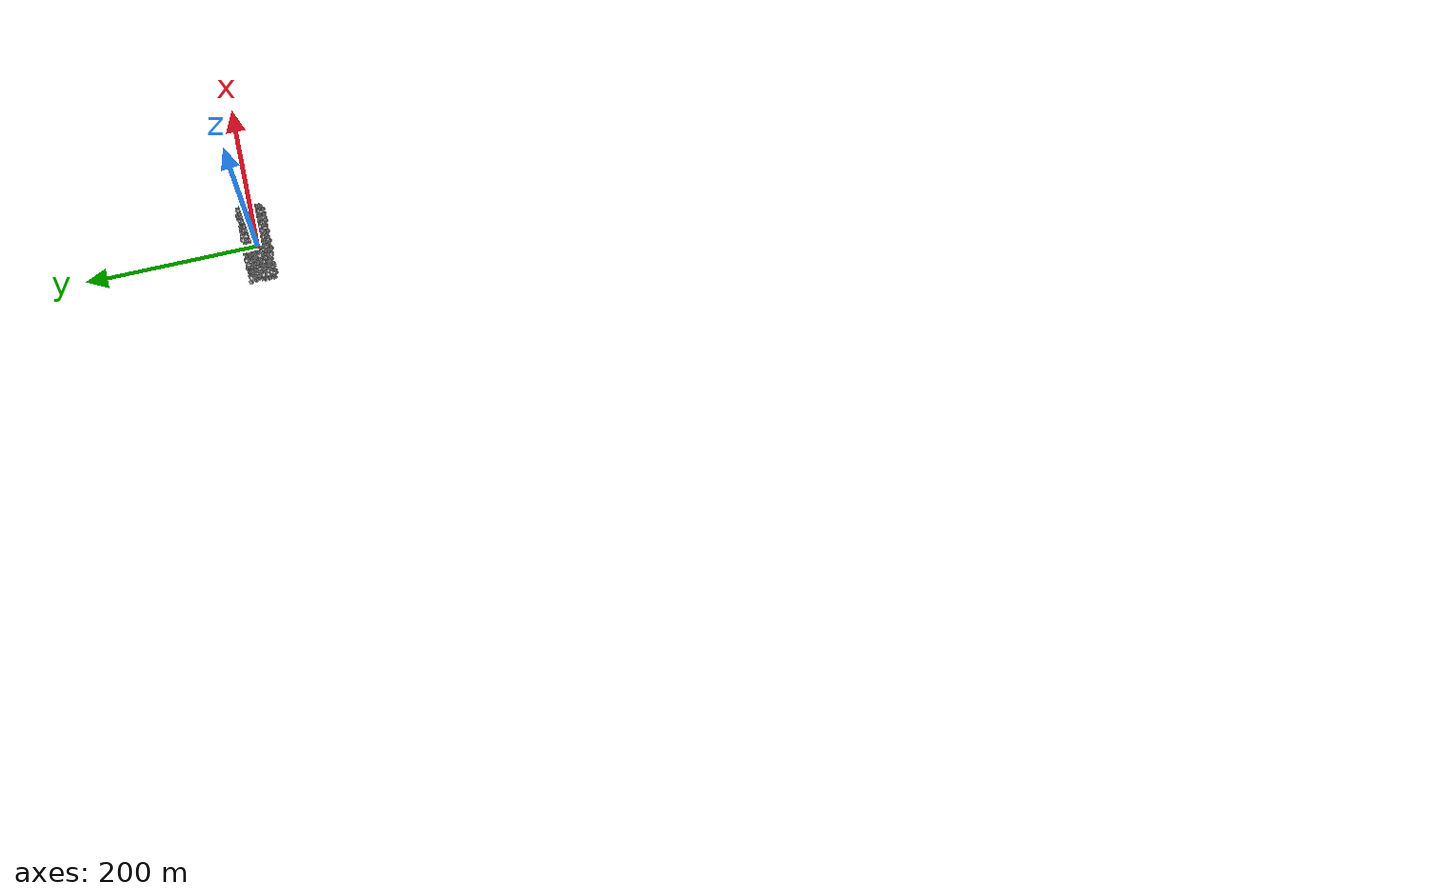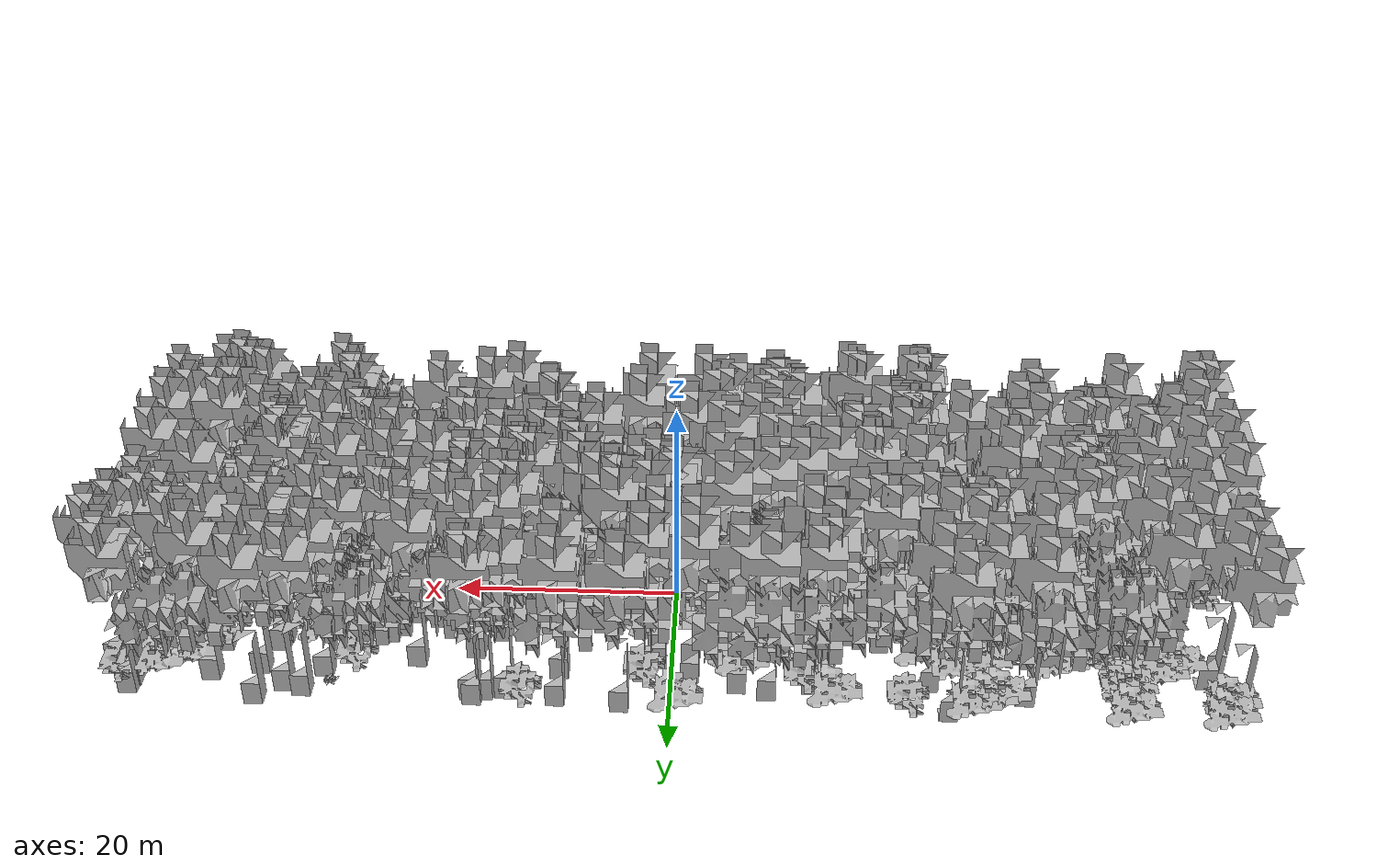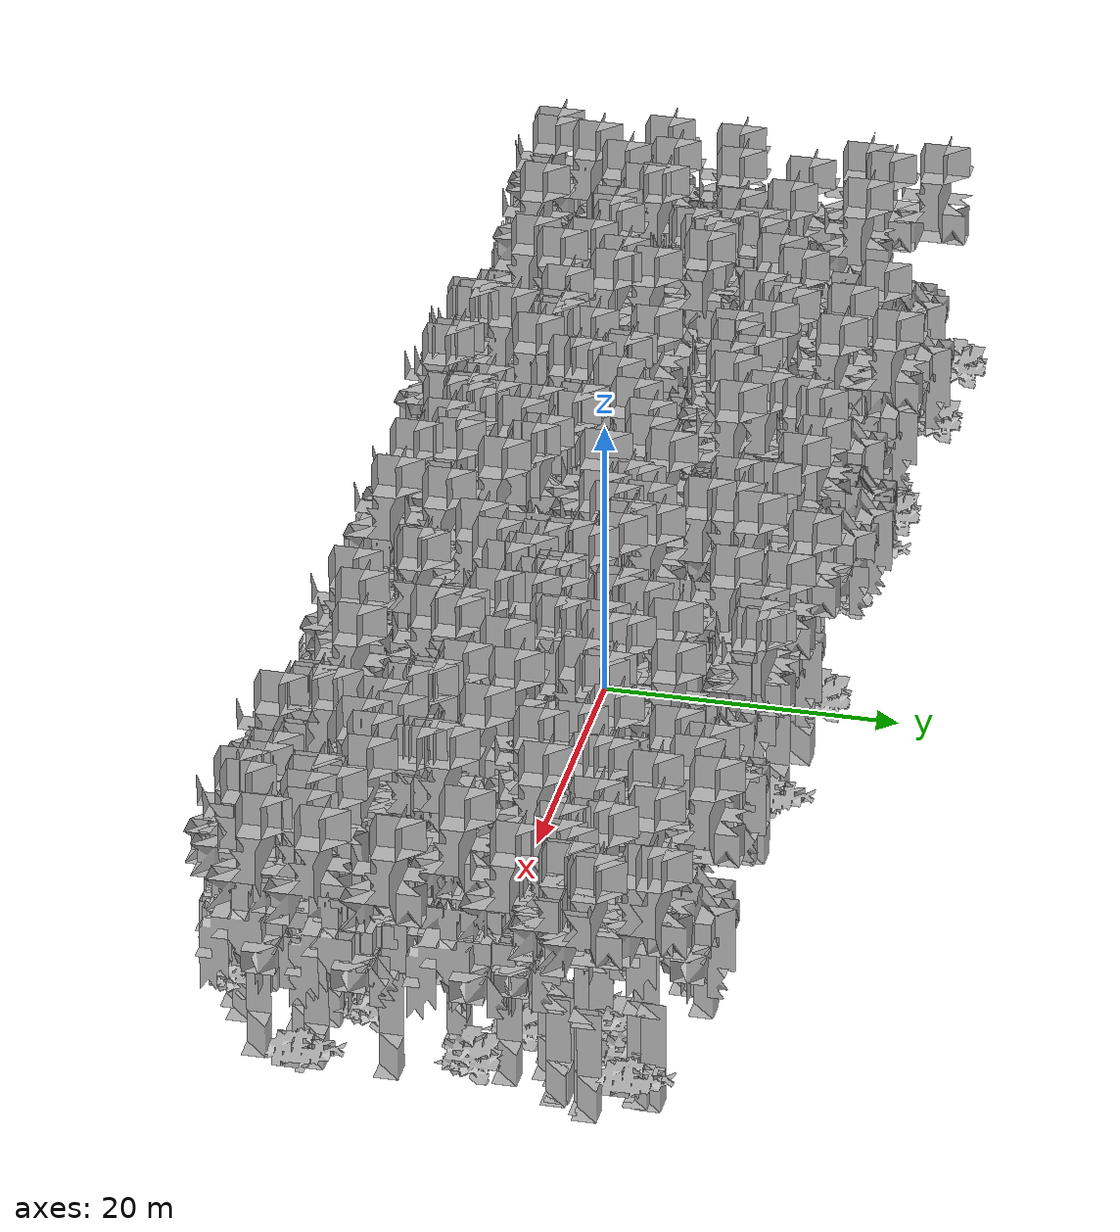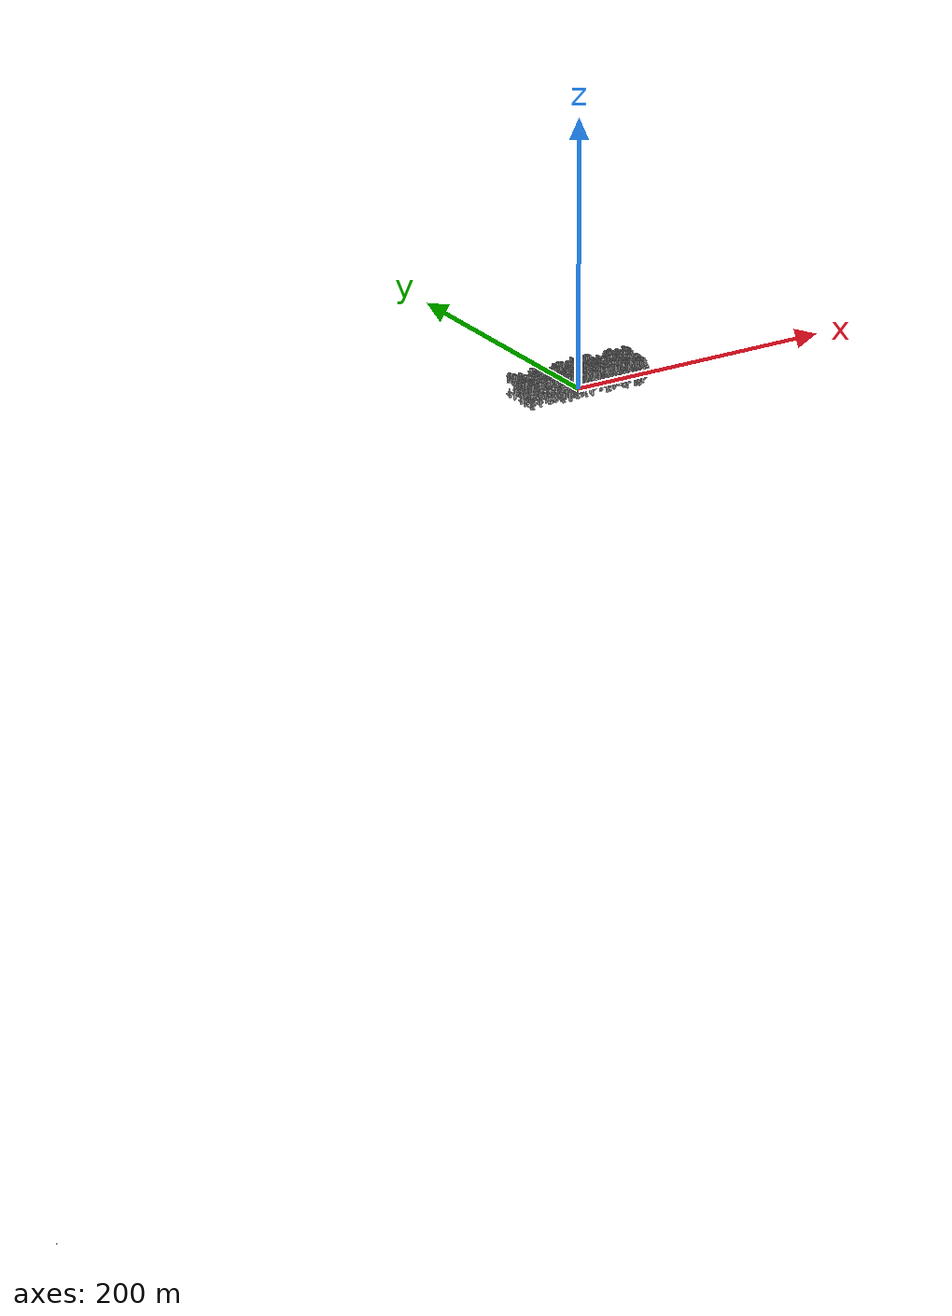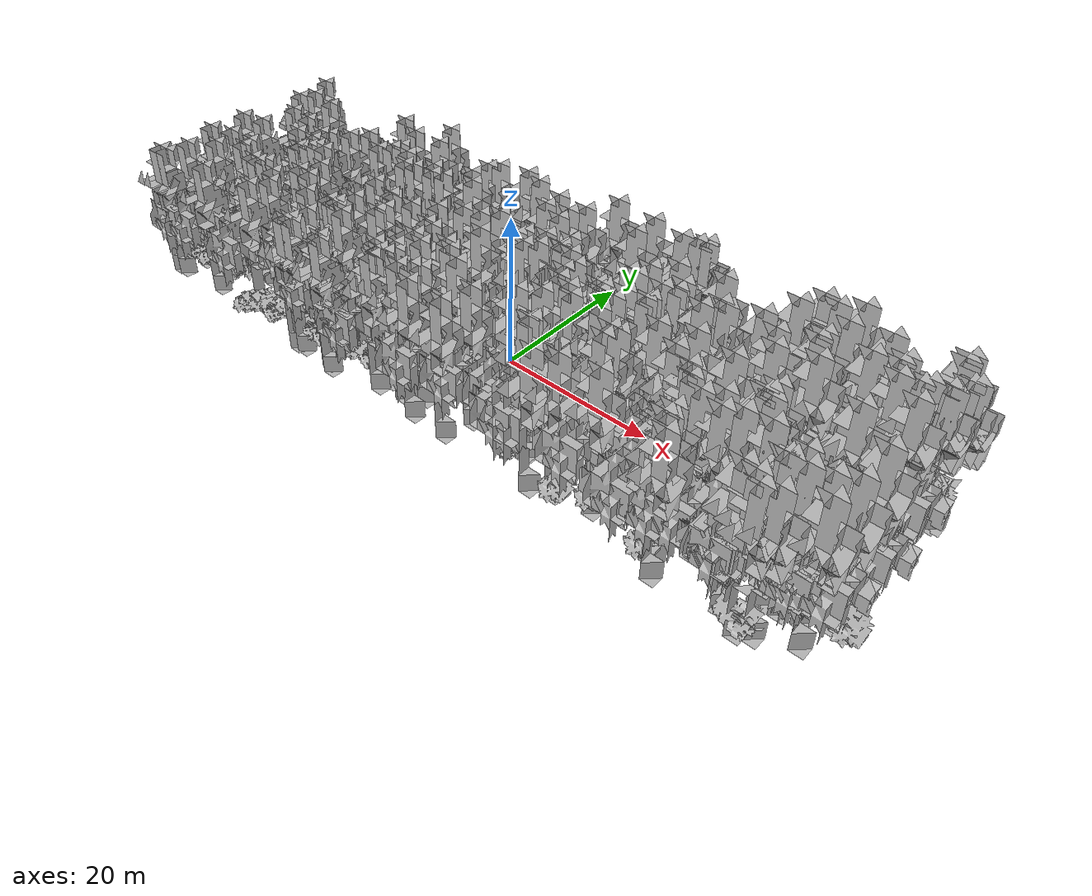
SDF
<sdf version="1.7">
    <world name="default">
        <plugin name="mrs_gazebo_static_transform_republisher_plugin" filename="libMrsGazeboCommonResources_StaticTransformRepublisher.so"/>
        <spherical_coordinates>
            <surface_model>EARTH_WGS84</surface_model>
            <latitude_deg>47.3977</latitude_deg>
            <longitude_deg>8.54559</longitude_deg>
            <elevation>0</elevation>
            <heading_deg>0</heading_deg>
        </spherical_coordinates>
        <physics name="default_physics" default="0" type="ode">
            <ode>
                <solver>
                    <type>quick</type>
                    <iters>10</iters>
                    <sor>1.3</sor>
                    <use_dynamic_moi_rescaling>0</use_dynamic_moi_rescaling>
                </solver>
                <constraints>
                    <cfm>0</cfm>
                    <erp>0.2</erp>
                    <contact_max_correcting_vel>1000</contact_max_correcting_vel>
                    <contact_surface_layer>0.001</contact_surface_layer>
                </constraints>
            </ode>
            <max_step_size>0.004</max_step_size>
            <real_time_factor>1</real_time_factor>
            <real_time_update_rate>250</real_time_update_rate>
        </physics>
        <scene>
            <shadows>0</shadows>
            <ambient>0.4 0.4 0.4 1</ambient>
            <background>0.7 0.7 0.7 1</background>
        </scene>
        <light name="sun" type="directional">
            <pose>0 0 1000 0.4 0.2 0</pose>
            <diffuse>1 1 1 1</diffuse>
            <specular>0.6 0.6 0.6 1</specular>
            <direction>0.1 0.1 -0.9</direction>
            <attenuation>
                <range>20</range>
                <constant>0.5</constant>
                <linear>0.01</linear>
                <quadratic>0.001</quadratic>
            </attenuation>
            <cast_shadows>1</cast_shadows>
            <spot>
                <inner_angle>0</inner_angle>
                <outer_angle>0</outer_angle>
                <falloff>0</falloff>
            </spot>
        </light>
        <model name="ground_plane">
            <static>1</static>
            <link name="link">
                <collision name="collision">
                    <pose>-50 0 0 0 -0 0</pose>
                    <geometry>
                        <plane>
                            <normal>0 0 1</normal>
                            <size>100 100</size>
                        </plane>
                    </geometry>
                    <surface>
                        <contact>
                            <ode>
                                <min_depth>0.01</min_depth>
                                <max_vel>0</max_vel>
                            </ode>
                        </contact>
                        <friction>
                            <ode/>
                            <torsional>
                                <ode/>
                            </torsional>
                        </friction>
                        <bounce/>
                    </surface>
                    <max_contacts>10</max_contacts>
                </collision>
                <visual name="grass">
                    <pose>0 0 0 0 -0 0</pose>
                    <cast_shadows>0</cast_shadows>
                    <geometry>
                        <mesh>
                            <scale>0.5814285714285714 0.18142857142857144 0.1</scale>
                            <uri>file://grass_plane/meshes/grass_plane.dae</uri>
                        </mesh>
                    </geometry>
                </visual>
                <self_collide>0</self_collide>
                <enable_wind>0</enable_wind>
                <kinematic>0</kinematic>
            </link>
        </model>
        <model name="the_void">
            <static>1</static>
            <link name="link">
                <pose>0 0 0.1 0 -0 0</pose>
                <visual name="the_void">
                    <pose>0 0 2 0 -0 0</pose>
                    <geometry>
                        <sphere>
                            <radius>0.25</radius>
                        </sphere>
                    </geometry>
                    <material>
                        <script>
                            <uri>file://media/materials/scripts/Gazebo.material</uri>
                            <name>Gazebo/Black</name>
                        </script>
                    </material>
                </visual>
                <self_collide>0</self_collide>
                <enable_wind>0</enable_wind>
                <kinematic>0</kinematic>
            </link>
            <pose>-1000 -1000 0 0 -0 0</pose>
        </model>
        <gui fullscreen="0">
            <camera name="camera">
                <pose>35.1577 98.6044 40.0204 0 0.407996 -1.99761</pose>
                <view_controller>orbit</view_controller>
                <projection_type>perspective</projection_type>
            </camera>
        </gui>
        <plugin name="mrs_gazebo_rviz_cam_synchronizer" filename="libMrsGazeboCommonResources_RvizCameraSynchronizer.so">
            <target_frame_id>gazebo_user_camera</target_frame_id>
            <world_origin_frame_id>uav1/gps_origin</world_origin_frame_id>
            <frame_to_follow>uav1</frame_to_follow>
        </plugin>
        <gravity>0 0 -9.8066</gravity>
        <magnetic_field>6e-06 2.3e-05 -4.2e-05</magnetic_field>
        <atmosphere type="adiabatic"/>
        <wind/>
        <model name="Tree 0">
            <static>1</static>
            <pose>-42.261111975902054 -4.697456809183089 0 1.57079 -0 0</pose>
            <link name="link">
                <pose>0 0 0 0 -0 0</pose>
                <collision name="collision">
                    <geometry>
                        <mesh>
                            <scale>3 2 3</scale>
                            <uri>model://tree_3/meshes/tree_3.obj</uri>
                        </mesh>
                    </geometry>
                    <max_contacts>10</max_contacts>
                    <surface>
                        <contact>
                            <ode/>
                        </contact>
                        <bounce/>
                        <friction>
                            <torsional>
                                <ode/>
                            </torsional>
                            <ode/>
                        </friction>
                    </surface>
                </collision>
                <visual name="visual">
                    <geometry>
                        <mesh>
                            <scale>3 2 3</scale>
                            <uri>model://tree_3/meshes/tree_3.obj</uri>
                        </mesh>
                    </geometry>
                </visual>
                <self_collide>0</self_collide>
                <enable_wind>0</enable_wind>
                <kinematic>0</kinematic>
            </link>
        </model>
        <model name="Tree 1">
            <static>1</static>
            <pose>2.9768143584794586 2.1918834567805376 0 1.57079 -0 0</pose>
            <link name="link">
                <pose>0 0 0 0 -0 0</pose>
                <collision name="collision">
                    <geometry>
                        <mesh>
                            <scale>4 2.5 4</scale>
                            <uri>model://tree_1/meshes/tree_1.obj</uri>
                        </mesh>
                    </geometry>
                    <max_contacts>10</max_contacts>
                    <surface>
                        <contact>
                            <ode/>
                        </contact>
                        <bounce/>
                        <friction>
                            <torsional>
                                <ode/>
                            </torsional>
                            <ode/>
                        </friction>
                    </surface>
                </collision>
                <visual name="visual">
                    <geometry>
                        <mesh>
                            <scale>4 2.5 4</scale>
                            <uri>model://tree_1/meshes/tree_1.obj</uri>
                        </mesh>
                    </geometry>
                </visual>
                <self_collide>0</self_collide>
                <enable_wind>0</enable_wind>
                <kinematic>0</kinematic>
            </link>
        </model>
        <model name="Tree 2">
            <static>1</static>
            <pose>42.655952371906366 4.007602021695671 0 1.57079 -0 0</pose>
            <link name="link">
                <pose>0 0 0 0 -0 0</pose>
                <collision name="collision">
                    <geometry>
                        <mesh>
                            <scale>3 2 3</scale>
                            <uri>model://tree_3/meshes/tree_3.obj</uri>
                        </mesh>
                    </geometry>
                    <max_contacts>10</max_contacts>
                    <surface>
                        <contact>
                            <ode/>
                        </contact>
                        <bounce/>
                        <friction>
                            <torsional>
                                <ode/>
                            </torsional>
                            <ode/>
                        </friction>
                    </surface>
                </collision>
                <visual name="visual">
                    <geometry>
                        <mesh>
                            <scale>3 2 3</scale>
                            <uri>model://tree_3/meshes/tree_3.obj</uri>
                        </mesh>
                    </geometry>
                </visual>
                <self_collide>0</self_collide>
                <enable_wind>0</enable_wind>
                <kinematic>0</kinematic>
            </link>
        </model>
        <model name="Tree 3">
            <static>1</static>
            <pose>21.59603311105822 -8.828315092953982 0 1.57079 -0 0</pose>
            <link name="link">
                <pose>0 0 0 0 -0 0</pose>
                <collision name="collision">
                    <geometry>
                        <mesh>
                            <scale>3.5 5 3.5</scale>
                            <uri>model://tree_2/meshes/tree_2.obj</uri>
                        </mesh>
                    </geometry>
                    <max_contacts>10</max_contacts>
                    <surface>
                        <contact>
                            <ode/>
                        </contact>
                        <bounce/>
                        <friction>
                            <torsional>
                                <ode/>
                            </torsional>
                            <ode/>
                        </friction>
                    </surface>
                </collision>
                <visual name="visual">
                    <geometry>
                        <mesh>
                            <scale>3.5 5 3.5</scale>
                            <uri>model://tree_2/meshes/tree_2.obj</uri>
                        </mesh>
                    </geometry>
                </visual>
                <self_collide>0</self_collide>
                <enable_wind>0</enable_wind>
                <kinematic>0</kinematic>
            </link>
        </model>
        <model name="Tree 4">
            <static>1</static>
            <pose>40.84279110203407 6.378118887128952 0 1.57079 -0 0</pose>
            <link name="link">
                <pose>0 0 0 0 -0 0</pose>
                <collision name="collision">
                    <geometry>
                        <mesh>
                            <scale>4 2.5 4</scale>
                            <uri>model://tree_1/meshes/tree_1.obj</uri>
                        </mesh>
                    </geometry>
                    <max_contacts>10</max_contacts>
                    <surface>
                        <contact>
                            <ode/>
                        </contact>
                        <bounce/>
                        <friction>
                            <torsional>
                                <ode/>
                            </torsional>
                            <ode/>
                        </friction>
                    </surface>
                </collision>
                <visual name="visual">
                    <geometry>
                        <mesh>
                            <scale>4 2.5 4</scale>
                            <uri>model://tree_1/meshes/tree_1.obj</uri>
                        </mesh>
                    </geometry>
                </visual>
                <self_collide>0</self_collide>
                <enable_wind>0</enable_wind>
                <kinematic>0</kinematic>
            </link>
        </model>
        <model name="Tree 5">
            <static>1</static>
            <pose>-26.627906791301722 -9.05891376173643 0 1.57079 -0 0</pose>
            <link name="link">
                <pose>0 0 0 0 -0 0</pose>
                <collision name="collision">
                    <geometry>
                        <mesh>
                            <scale>3.5 5 3.5</scale>
                            <uri>model://tree_2/meshes/tree_2.obj</uri>
                        </mesh>
                    </geometry>
                    <max_contacts>10</max_contacts>
                    <surface>
                        <contact>
                            <ode/>
                        </contact>
                        <bounce/>
                        <friction>
                            <torsional>
                                <ode/>
                            </torsional>
                            <ode/>
                        </friction>
                    </surface>
                </collision>
                <visual name="visual">
                    <geometry>
                        <mesh>
                            <scale>3.5 5 3.5</scale>
                            <uri>model://tree_2/meshes/tree_2.obj</uri>
                        </mesh>
                    </geometry>
                </visual>
                <self_collide>0</self_collide>
                <enable_wind>0</enable_wind>
                <kinematic>0</kinematic>
            </link>
        </model>
        <model name="Tree 6">
            <static>1</static>
            <pose>-3.488642249334532 -1.3340177643138027 0 1.57079 -0 0</pose>
            <link name="link">
                <pose>0 0 0 0 -0 0</pose>
                <collision name="collision">
                    <geometry>
                        <mesh>
                            <scale>3.5 5 3.5</scale>
                            <uri>model://tree_9/meshes/tree_9.obj</uri>
                        </mesh>
                    </geometry>
                    <max_contacts>10</max_contacts>
                    <surface>
                        <contact>
                            <ode/>
                        </contact>
                        <bounce/>
                        <friction>
                            <torsional>
                                <ode/>
                            </torsional>
                            <ode/>
                        </friction>
                    </surface>
                </collision>
                <visual name="visual">
                    <geometry>
                        <mesh>
                            <scale>3.5 5 3.5</scale>
                            <uri>model://tree_9/meshes/tree_9.obj</uri>
                        </mesh>
                    </geometry>
                </visual>
                <self_collide>0</self_collide>
                <enable_wind>0</enable_wind>
                <kinematic>0</kinematic>
            </link>
        </model>
        <model name="Tree 7">
            <static>1</static>
            <pose>15.129979773164116 5.504716589142198 0 1.57079 -0 0</pose>
            <link name="link">
                <pose>0 0 0 0 -0 0</pose>
                <collision name="collision">
                    <geometry>
                        <mesh>
                            <scale>3.5 5 3.5</scale>
                            <uri>model://tree_9/meshes/tree_9.obj</uri>
                        </mesh>
                    </geometry>
                    <max_contacts>10</max_contacts>
                    <surface>
                        <contact>
                            <ode/>
                        </contact>
                        <bounce/>
                        <friction>
                            <torsional>
                                <ode/>
                            </torsional>
                            <ode/>
                        </friction>
                    </surface>
                </collision>
                <visual name="visual">
                    <geometry>
                        <mesh>
                            <scale>3.5 5 3.5</scale>
                            <uri>model://tree_9/meshes/tree_9.obj</uri>
                        </mesh>
                    </geometry>
                </visual>
                <self_collide>0</self_collide>
                <enable_wind>0</enable_wind>
                <kinematic>0</kinematic>
            </link>
        </model>
        <model name="Tree 8">
            <static>1</static>
            <pose>19.640213285658405 3.5858710224812995 0 1.57079 -0 0</pose>
            <link name="link">
                <pose>0 0 0 0 -0 0</pose>
                <collision name="collision">
                    <geometry>
                        <mesh>
                            <scale>3 2 3</scale>
                            <uri>model://tree_3/meshes/tree_3.obj</uri>
                        </mesh>
                    </geometry>
                    <max_contacts>10</max_contacts>
                    <surface>
                        <contact>
                            <ode/>
                        </contact>
                        <bounce/>
                        <friction>
                            <torsional>
                                <ode/>
                            </torsional>
                            <ode/>
                        </friction>
                    </surface>
                </collision>
                <visual name="visual">
                    <geometry>
                        <mesh>
                            <scale>3 2 3</scale>
                            <uri>model://tree_3/meshes/tree_3.obj</uri>
                        </mesh>
                    </geometry>
                </visual>
                <self_collide>0</self_collide>
                <enable_wind>0</enable_wind>
                <kinematic>0</kinematic>
            </link>
        </model>
        <model name="Tree 9">
            <static>1</static>
            <pose>-19.254728085528576 0.3117061997227779 0 1.57079 -0 0</pose>
            <link name="link">
                <pose>0 0 0 0 -0 0</pose>
                <collision name="collision">
                    <geometry>
                        <mesh>
                            <scale>3.5 5 3.5</scale>
                            <uri>model://tree_2/meshes/tree_2.obj</uri>
                        </mesh>
                    </geometry>
                    <max_contacts>10</max_contacts>
                    <surface>
                        <contact>
                            <ode/>
                        </contact>
                        <bounce/>
                        <friction>
                            <torsional>
                                <ode/>
                            </torsional>
                            <ode/>
                        </friction>
                    </surface>
                </collision>
                <visual name="visual">
                    <geometry>
                        <mesh>
                            <scale>3.5 5 3.5</scale>
                            <uri>model://tree_2/meshes/tree_2.obj</uri>
                        </mesh>
                    </geometry>
                </visual>
                <self_collide>0</self_collide>
                <enable_wind>0</enable_wind>
                <kinematic>0</kinematic>
            </link>
        </model>
        <model name="Tree 10">
            <static>1</static>
            <pose>-28.88715911877962 7.5835889109082295 0 1.57079 -0 0</pose>
            <link name="link">
                <pose>0 0 0 0 -0 0</pose>
                <collision name="collision">
                    <geometry>
                        <mesh>
                            <scale>4 2.5 4</scale>
                            <uri>model://tree_1/meshes/tree_1.obj</uri>
                        </mesh>
                    </geometry>
                    <max_contacts>10</max_contacts>
                    <surface>
                        <contact>
                            <ode/>
                        </contact>
                        <bounce/>
                        <friction>
                            <torsional>
                                <ode/>
                            </torsional>
                            <ode/>
                        </friction>
                    </surface>
                </collision>
                <visual name="visual">
                    <geometry>
                        <mesh>
                            <scale>4 2.5 4</scale>
                            <uri>model://tree_1/meshes/tree_1.obj</uri>
                        </mesh>
                    </geometry>
                </visual>
                <self_collide>0</self_collide>
                <enable_wind>0</enable_wind>
                <kinematic>0</kinematic>
            </link>
        </model>
        <model name="Tree 11">
            <static>1</static>
            <pose>1.2711613512293525 6.7308629670485765 0 1.57079 -0 0</pose>
            <link name="link">
                <pose>0 0 0 0 -0 0</pose>
                <collision name="collision">
                    <geometry>
                        <mesh>
                            <scale>3.5 5 3.5</scale>
                            <uri>model://tree_9/meshes/tree_9.obj</uri>
                        </mesh>
                    </geometry>
                    <max_contacts>10</max_contacts>
                    <surface>
                        <contact>
                            <ode/>
                        </contact>
                        <bounce/>
                        <friction>
                            <torsional>
                                <ode/>
                            </torsional>
                            <ode/>
                        </friction>
                    </surface>
                </collision>
                <visual name="visual">
                    <geometry>
                        <mesh>
                            <scale>3.5 5 3.5</scale>
                            <uri>model://tree_9/meshes/tree_9.obj</uri>
                        </mesh>
                    </geometry>
                </visual>
                <self_collide>0</self_collide>
                <enable_wind>0</enable_wind>
                <kinematic>0</kinematic>
            </link>
        </model>
        <model name="Tree 12">
            <static>1</static>
            <pose>1.9493568093408271 -0.15671179720794726 0 1.57079 -0 0</pose>
            <link name="link">
                <pose>0 0 0 0 -0 0</pose>
                <collision name="collision">
                    <geometry>
                        <mesh>
                            <scale>3.5 5 3.5</scale>
                            <uri>model://tree_9/meshes/tree_9.obj</uri>
                        </mesh>
                    </geometry>
                    <max_contacts>10</max_contacts>
                    <surface>
                        <contact>
                            <ode/>
                        </contact>
                        <bounce/>
                        <friction>
                            <torsional>
                                <ode/>
                            </torsional>
                            <ode/>
                        </friction>
                    </surface>
                </collision>
                <visual name="visual">
                    <geometry>
                        <mesh>
                            <scale>3.5 5 3.5</scale>
                            <uri>model://tree_9/meshes/tree_9.obj</uri>
                        </mesh>
                    </geometry>
                </visual>
                <self_collide>0</self_collide>
                <enable_wind>0</enable_wind>
                <kinematic>0</kinematic>
            </link>
        </model>
        <model name="Tree 13">
            <static>1</static>
            <pose>-34.13500504389717 6.870767040708287 0 1.57079 -0 0</pose>
            <link name="link">
                <pose>0 0 0 0 -0 0</pose>
                <collision name="collision">
                    <geometry>
                        <mesh>
                            <scale>4 2.5 4</scale>
                            <uri>model://tree_1/meshes/tree_1.obj</uri>
                        </mesh>
                    </geometry>
                    <max_contacts>10</max_contacts>
                    <surface>
                        <contact>
                            <ode/>
                        </contact>
                        <bounce/>
                        <friction>
                            <torsional>
                                <ode/>
                            </torsional>
                            <ode/>
                        </friction>
                    </surface>
                </collision>
                <visual name="visual">
                    <geometry>
                        <mesh>
                            <scale>4 2.5 4</scale>
                            <uri>model://tree_1/meshes/tree_1.obj</uri>
                        </mesh>
                    </geometry>
                </visual>
                <self_collide>0</self_collide>
                <enable_wind>0</enable_wind>
                <kinematic>0</kinematic>
            </link>
        </model>
        <model name="Tree 14">
            <static>1</static>
            <pose>29.20099575470026 -12.79384205445032 0 1.57079 -0 0</pose>
            <link name="link">
                <pose>0 0 0 0 -0 0</pose>
                <collision name="collision">
                    <geometry>
                        <mesh>
                            <scale>4 2.5 4</scale>
                            <uri>model://tree_1/meshes/tree_1.obj</uri>
                        </mesh>
                    </geometry>
                    <max_contacts>10</max_contacts>
                    <surface>
                        <contact>
                            <ode/>
                        </contact>
                        <bounce/>
                        <friction>
                            <torsional>
                                <ode/>
                            </torsional>
                            <ode/>
                        </friction>
                    </surface>
                </collision>
                <visual name="visual">
                    <geometry>
                        <mesh>
                            <scale>4 2.5 4</scale>
                            <uri>model://tree_1/meshes/tree_1.obj</uri>
                        </mesh>
                    </geometry>
                </visual>
                <self_collide>0</self_collide>
                <enable_wind>0</enable_wind>
                <kinematic>0</kinematic>
            </link>
        </model>
        <model name="Tree 15">
            <static>1</static>
            <pose>-3.059016480101249 2.886148568219056 0 1.57079 -0 0</pose>
            <link name="link">
                <pose>0 0 0 0 -0 0</pose>
                <collision name="collision">
                    <geometry>
                        <mesh>
                            <scale>3 2 3</scale>
                            <uri>model://tree_3/meshes/tree_3.obj</uri>
                        </mesh>
                    </geometry>
                    <max_contacts>10</max_contacts>
                    <surface>
                        <contact>
                            <ode/>
                        </contact>
                        <bounce/>
                        <friction>
                            <torsional>
                                <ode/>
                            </torsional>
                            <ode/>
                        </friction>
                    </surface>
                </collision>
                <visual name="visual">
                    <geometry>
                        <mesh>
                            <scale>3 2 3</scale>
                            <uri>model://tree_3/meshes/tree_3.obj</uri>
                        </mesh>
                    </geometry>
                </visual>
                <self_collide>0</self_collide>
                <enable_wind>0</enable_wind>
                <kinematic>0</kinematic>
            </link>
        </model>
        <model name="Tree 16">
            <static>1</static>
            <pose>28.036003173326606 1.1155130580861758 0 1.57079 -0 0</pose>
            <link name="link">
                <pose>0 0 0 0 -0 0</pose>
                <collision name="collision">
                    <geometry>
                        <mesh>
                            <scale>3.5 5 3.5</scale>
                            <uri>model://tree_2/meshes/tree_2.obj</uri>
                        </mesh>
                    </geometry>
                    <max_contacts>10</max_contacts>
                    <surface>
                        <contact>
                            <ode/>
                        </contact>
                        <bounce/>
                        <friction>
                            <torsional>
                                <ode/>
                            </torsional>
                            <ode/>
                        </friction>
                    </surface>
                </collision>
                <visual name="visual">
                    <geometry>
                        <mesh>
                            <scale>3.5 5 3.5</scale>
                            <uri>model://tree_2/meshes/tree_2.obj</uri>
                        </mesh>
                    </geometry>
                </visual>
                <self_collide>0</self_collide>
                <enable_wind>0</enable_wind>
                <kinematic>0</kinematic>
            </link>
        </model>
        <model name="Tree 17">
            <static>1</static>
            <pose>-21.976754670032733 -14.721176243246461 0 1.57079 -0 0</pose>
            <link name="link">
                <pose>0 0 0 0 -0 0</pose>
                <collision name="collision">
                    <geometry>
                        <mesh>
                            <scale>3.5 5 3.5</scale>
                            <uri>model://tree_9/meshes/tree_9.obj</uri>
                        </mesh>
                    </geometry>
                    <max_contacts>10</max_contacts>
                    <surface>
                        <contact>
                            <ode/>
                        </contact>
                        <bounce/>
                        <friction>
                            <torsional>
                                <ode/>
                            </torsional>
                            <ode/>
                        </friction>
                    </surface>
                </collision>
                <visual name="visual">
                    <geometry>
                        <mesh>
                            <scale>3.5 5 3.5</scale>
                            <uri>model://tree_9/meshes/tree_9.obj</uri>
                        </mesh>
                    </geometry>
                </visual>
                <self_collide>0</self_collide>
                <enable_wind>0</enable_wind>
                <kinematic>0</kinematic>
            </link>
        </model>
        <model name="Tree 18">
            <static>1</static>
            <pose>44.49626839596736 11.67631269223818 0 1.57079 -0 0</pose>
            <link name="link">
                <pose>0 0 0 0 -0 0</pose>
                <collision name="collision">
                    <geometry>
                        <mesh>
                            <scale>3 2 3</scale>
                            <uri>model://tree_3/meshes/tree_3.obj</uri>
                        </mesh>
                    </geometry>
                    <max_contacts>10</max_contacts>
                    <surface>
                        <contact>
                            <ode/>
                        </contact>
                        <bounce/>
                        <friction>
                            <torsional>
                                <ode/>
                            </torsional>
                            <ode/>
                        </friction>
                    </surface>
                </collision>
                <visual name="visual">
                    <geometry>
                        <mesh>
                            <scale>3 2 3</scale>
                            <uri>model://tree_3/meshes/tree_3.obj</uri>
                        </mesh>
                    </geometry>
                </visual>
                <self_collide>0</self_collide>
                <enable_wind>0</enable_wind>
                <kinematic>0</kinematic>
            </link>
        </model>
        <model name="Tree 19">
            <static>1</static>
            <pose>-38.95482112076441 11.331748140919487 0 1.57079 -0 0</pose>
            <link name="link">
                <pose>0 0 0 0 -0 0</pose>
                <collision name="collision">
                    <geometry>
                        <mesh>
                            <scale>3.5 5 3.5</scale>
                            <uri>model://tree_2/meshes/tree_2.obj</uri>
                        </mesh>
                    </geometry>
                    <max_contacts>10</max_contacts>
                    <surface>
                        <contact>
                            <ode/>
                        </contact>
                        <bounce/>
                        <friction>
                            <torsional>
                                <ode/>
                            </torsional>
                            <ode/>
                        </friction>
                    </surface>
                </collision>
                <visual name="visual">
                    <geometry>
                        <mesh>
                            <scale>3.5 5 3.5</scale>
                            <uri>model://tree_2/meshes/tree_2.obj</uri>
                        </mesh>
                    </geometry>
                </visual>
                <self_collide>0</self_collide>
                <enable_wind>0</enable_wind>
                <kinematic>0</kinematic>
            </link>
        </model>
        <model name="Tree 20">
            <static>1</static>
            <pose>-19.827371772163044 -5.894363114808941 0 1.57079 -0 0</pose>
            <link name="link">
                <pose>0 0 0 0 -0 0</pose>
                <collision name="collision">
                    <geometry>
                        <mesh>
                            <scale>3.5 5 3.5</scale>
                            <uri>model://tree_9/meshes/tree_9.obj</uri>
                        </mesh>
                    </geometry>
                    <max_contacts>10</max_contacts>
                    <surface>
                        <contact>
                            <ode/>
                        </contact>
                        <bounce/>
                        <friction>
                            <torsional>
                                <ode/>
                            </torsional>
                            <ode/>
                        </friction>
                    </surface>
                </collision>
                <visual name="visual">
                    <geometry>
                        <mesh>
                            <scale>3.5 5 3.5</scale>
                            <uri>model://tree_9/meshes/tree_9.obj</uri>
                        </mesh>
                    </geometry>
                </visual>
                <self_collide>0</self_collide>
                <enable_wind>0</enable_wind>
                <kinematic>0</kinematic>
            </link>
        </model>
        <model name="Tree 21">
            <static>1</static>
            <pose>-5.244288710583049 -12.456172280738432 0 1.57079 -0 0</pose>
            <link name="link">
                <pose>0 0 0 0 -0 0</pose>
                <collision name="collision">
                    <geometry>
                        <mesh>
                            <scale>3.5 5 3.5</scale>
                            <uri>model://tree_9/meshes/tree_9.obj</uri>
                        </mesh>
                    </geometry>
                    <max_contacts>10</max_contacts>
                    <surface>
                        <contact>
                            <ode/>
                        </contact>
                        <bounce/>
                        <friction>
                            <torsional>
                                <ode/>
                            </torsional>
                            <ode/>
                        </friction>
                    </surface>
                </collision>
                <visual name="visual">
                    <geometry>
                        <mesh>
                            <scale>3.5 5 3.5</scale>
                            <uri>model://tree_9/meshes/tree_9.obj</uri>
                        </mesh>
                    </geometry>
                </visual>
                <self_collide>0</self_collide>
                <enable_wind>0</enable_wind>
                <kinematic>0</kinematic>
            </link>
        </model>
        <model name="Tree 22">
            <static>1</static>
            <pose>-48.03252027512432 -1.5942124357965781 0 1.57079 -0 0</pose>
            <link name="link">
                <pose>0 0 0 0 -0 0</pose>
                <collision name="collision">
                    <geometry>
                        <mesh>
                            <scale>3.5 5 3.5</scale>
                            <uri>model://tree_9/meshes/tree_9.obj</uri>
                        </mesh>
                    </geometry>
                    <max_contacts>10</max_contacts>
                    <surface>
                        <contact>
                            <ode/>
                        </contact>
                        <bounce/>
                        <friction>
                            <torsional>
                                <ode/>
                            </torsional>
                            <ode/>
                        </friction>
                    </surface>
                </collision>
                <visual name="visual">
                    <geometry>
                        <mesh>
                            <scale>3.5 5 3.5</scale>
                            <uri>model://tree_9/meshes/tree_9.obj</uri>
                        </mesh>
                    </geometry>
                </visual>
                <self_collide>0</self_collide>
                <enable_wind>0</enable_wind>
                <kinematic>0</kinematic>
            </link>
        </model>
        <model name="Tree 23">
            <static>1</static>
            <pose>-33.157972557217185 -1.3379758567242597 0 1.57079 -0 0</pose>
            <link name="link">
                <pose>0 0 0 0 -0 0</pose>
                <collision name="collision">
                    <geometry>
                        <mesh>
                            <scale>3 2 3</scale>
                            <uri>model://tree_3/meshes/tree_3.obj</uri>
                        </mesh>
                    </geometry>
                    <max_contacts>10</max_contacts>
                    <surface>
                        <contact>
                            <ode/>
                        </contact>
                        <bounce/>
                        <friction>
                            <torsional>
                                <ode/>
                            </torsional>
                            <ode/>
                        </friction>
                    </surface>
                </collision>
                <visual name="visual">
                    <geometry>
                        <mesh>
                            <scale>3 2 3</scale>
                            <uri>model://tree_3/meshes/tree_3.obj</uri>
                        </mesh>
                    </geometry>
                </visual>
                <self_collide>0</self_collide>
                <enable_wind>0</enable_wind>
                <kinematic>0</kinematic>
            </link>
        </model>
        <model name="Tree 24">
            <static>1</static>
            <pose>-46.3371986453799 -9.924449364917294 0 1.57079 -0 0</pose>
            <link name="link">
                <pose>0 0 0 0 -0 0</pose>
                <collision name="collision">
                    <geometry>
                        <mesh>
                            <scale>3.5 5 3.5</scale>
                            <uri>model://tree_2/meshes/tree_2.obj</uri>
                        </mesh>
                    </geometry>
                    <max_contacts>10</max_contacts>
                    <surface>
                        <contact>
                            <ode/>
                        </contact>
                        <bounce/>
                        <friction>
                            <torsional>
                                <ode/>
                            </torsional>
                            <ode/>
                        </friction>
                    </surface>
                </collision>
                <visual name="visual">
                    <geometry>
                        <mesh>
                            <scale>3.5 5 3.5</scale>
                            <uri>model://tree_2/meshes/tree_2.obj</uri>
                        </mesh>
                    </geometry>
                </visual>
                <self_collide>0</self_collide>
                <enable_wind>0</enable_wind>
                <kinematic>0</kinematic>
            </link>
        </model>
        <model name="Tree 25">
            <static>1</static>
            <pose>8.711538809172538 0.8453942712679599 0 1.57079 -0 0</pose>
            <link name="link">
                <pose>0 0 0 0 -0 0</pose>
                <collision name="collision">
                    <geometry>
                        <mesh>
                            <scale>3.5 5 3.5</scale>
                            <uri>model://tree_2/meshes/tree_2.obj</uri>
                        </mesh>
                    </geometry>
                    <max_contacts>10</max_contacts>
                    <surface>
                        <contact>
                            <ode/>
                        </contact>
                        <bounce/>
                        <friction>
                            <torsional>
                                <ode/>
                            </torsional>
                            <ode/>
                        </friction>
                    </surface>
                </collision>
                <visual name="visual">
                    <geometry>
                        <mesh>
                            <scale>3.5 5 3.5</scale>
                            <uri>model://tree_2/meshes/tree_2.obj</uri>
                        </mesh>
                    </geometry>
                </visual>
                <self_collide>0</self_collide>
                <enable_wind>0</enable_wind>
                <kinematic>0</kinematic>
            </link>
        </model>
        <model name="Tree 26">
            <static>1</static>
            <pose>26.38132896985053 -8.619902670378695 0 1.57079 -0 0</pose>
            <link name="link">
                <pose>0 0 0 0 -0 0</pose>
                <collision name="collision">
                    <geometry>
                        <mesh>
                            <scale>4 2.5 4</scale>
                            <uri>model://tree_1/meshes/tree_1.obj</uri>
                        </mesh>
                    </geometry>
                    <max_contacts>10</max_contacts>
                    <surface>
                        <contact>
                            <ode/>
                        </contact>
                        <bounce/>
                        <friction>
                            <torsional>
                                <ode/>
                            </torsional>
                            <ode/>
                        </friction>
                    </surface>
                </collision>
                <visual name="visual">
                    <geometry>
                        <mesh>
                            <scale>4 2.5 4</scale>
                            <uri>model://tree_1/meshes/tree_1.obj</uri>
                        </mesh>
                    </geometry>
                </visual>
                <self_collide>0</self_collide>
                <enable_wind>0</enable_wind>
                <kinematic>0</kinematic>
            </link>
        </model>
        <model name="Tree 27">
            <static>1</static>
            <pose>6.53860164202807 -0.5497911031416312 0 1.57079 -0 0</pose>
            <link name="link">
                <pose>0 0 0 0 -0 0</pose>
                <collision name="collision">
                    <geometry>
                        <mesh>
                            <scale>3 2 3</scale>
                            <uri>model://tree_3/meshes/tree_3.obj</uri>
                        </mesh>
                    </geometry>
                    <max_contacts>10</max_contacts>
                    <surface>
                        <contact>
                            <ode/>
                        </contact>
                        <bounce/>
                        <friction>
                            <torsional>
                                <ode/>
                            </torsional>
                            <ode/>
                        </friction>
                    </surface>
                </collision>
                <visual name="visual">
                    <geometry>
                        <mesh>
                            <scale>3 2 3</scale>
                            <uri>model://tree_3/meshes/tree_3.obj</uri>
                        </mesh>
                    </geometry>
                </visual>
                <self_collide>0</self_collide>
                <enable_wind>0</enable_wind>
                <kinematic>0</kinematic>
            </link>
        </model>
        <model name="Tree 28">
            <static>1</static>
            <pose>47.11242717140746 -11.686590214693581 0 1.57079 -0 0</pose>
            <link name="link">
                <pose>0 0 0 0 -0 0</pose>
                <collision name="collision">
                    <geometry>
                        <mesh>
                            <scale>3.5 5 3.5</scale>
                            <uri>model://tree_2/meshes/tree_2.obj</uri>
                        </mesh>
                    </geometry>
                    <max_contacts>10</max_contacts>
                    <surface>
                        <contact>
                            <ode/>
                        </contact>
                        <bounce/>
                        <friction>
                            <torsional>
                                <ode/>
                            </torsional>
                            <ode/>
                        </friction>
                    </surface>
                </collision>
                <visual name="visual">
                    <geometry>
                        <mesh>
                            <scale>3.5 5 3.5</scale>
                            <uri>model://tree_2/meshes/tree_2.obj</uri>
                        </mesh>
                    </geometry>
                </visual>
                <self_collide>0</self_collide>
                <enable_wind>0</enable_wind>
                <kinematic>0</kinematic>
            </link>
        </model>
        <model name="Tree 29">
            <static>1</static>
            <pose>36.32571474858473 -8.994952364970079 0 1.57079 -0 0</pose>
            <link name="link">
                <pose>0 0 0 0 -0 0</pose>
                <collision name="collision">
                    <geometry>
                        <mesh>
                            <scale>3.5 5 3.5</scale>
                            <uri>model://tree_2/meshes/tree_2.obj</uri>
                        </mesh>
                    </geometry>
                    <max_contacts>10</max_contacts>
                    <surface>
                        <contact>
                            <ode/>
                        </contact>
                        <bounce/>
                        <friction>
                            <torsional>
                                <ode/>
                            </torsional>
                            <ode/>
                        </friction>
                    </surface>
                </collision>
                <visual name="visual">
                    <geometry>
                        <mesh>
                            <scale>3.5 5 3.5</scale>
                            <uri>model://tree_2/meshes/tree_2.obj</uri>
                        </mesh>
                    </geometry>
                </visual>
                <self_collide>0</self_collide>
                <enable_wind>0</enable_wind>
                <kinematic>0</kinematic>
            </link>
        </model>
        <model name="Tree 30">
            <static>1</static>
            <pose>19.511945648848055 5.351323037663189 0 1.57079 -0 0</pose>
            <link name="link">
                <pose>0 0 0 0 -0 0</pose>
                <collision name="collision">
                    <geometry>
                        <mesh>
                            <scale>3.5 5 3.5</scale>
                            <uri>model://tree_9/meshes/tree_9.obj</uri>
                        </mesh>
                    </geometry>
                    <max_contacts>10</max_contacts>
                    <surface>
                        <contact>
                            <ode/>
                        </contact>
                        <bounce/>
                        <friction>
                            <torsional>
                                <ode/>
                            </torsional>
                            <ode/>
                        </friction>
                    </surface>
                </collision>
                <visual name="visual">
                    <geometry>
                        <mesh>
                            <scale>3.5 5 3.5</scale>
                            <uri>model://tree_9/meshes/tree_9.obj</uri>
                        </mesh>
                    </geometry>
                </visual>
                <self_collide>0</self_collide>
                <enable_wind>0</enable_wind>
                <kinematic>0</kinematic>
            </link>
        </model>
        <model name="Tree 31">
            <static>1</static>
            <pose>9.62641194046531 8.738126387564794 0 1.57079 -0 0</pose>
            <link name="link">
                <pose>0 0 0 0 -0 0</pose>
                <collision name="collision">
                    <geometry>
                        <mesh>
                            <scale>3.5 5 3.5</scale>
                            <uri>model://tree_2/meshes/tree_2.obj</uri>
                        </mesh>
                    </geometry>
                    <max_contacts>10</max_contacts>
                    <surface>
                        <contact>
                            <ode/>
                        </contact>
                        <bounce/>
                        <friction>
                            <torsional>
                                <ode/>
                            </torsional>
                            <ode/>
                        </friction>
                    </surface>
                </collision>
                <visual name="visual">
                    <geometry>
                        <mesh>
                            <scale>3.5 5 3.5</scale>
                            <uri>model://tree_2/meshes/tree_2.obj</uri>
                        </mesh>
                    </geometry>
                </visual>
                <self_collide>0</self_collide>
                <enable_wind>0</enable_wind>
                <kinematic>0</kinematic>
            </link>
        </model>
        <model name="Tree 32">
            <static>1</static>
            <pose>13.877538629962096 -1.5973208112124766 0 1.57079 -0 0</pose>
            <link name="link">
                <pose>0 0 0 0 -0 0</pose>
                <collision name="collision">
                    <geometry>
                        <mesh>
                            <scale>3.5 5 3.5</scale>
                            <uri>model://tree_9/meshes/tree_9.obj</uri>
                        </mesh>
                    </geometry>
                    <max_contacts>10</max_contacts>
                    <surface>
                        <contact>
                            <ode/>
                        </contact>
                        <bounce/>
                        <friction>
                            <torsional>
                                <ode/>
                            </torsional>
                            <ode/>
                        </friction>
                    </surface>
                </collision>
                <visual name="visual">
                    <geometry>
                        <mesh>
                            <scale>3.5 5 3.5</scale>
                            <uri>model://tree_9/meshes/tree_9.obj</uri>
                        </mesh>
                    </geometry>
                </visual>
                <self_collide>0</self_collide>
                <enable_wind>0</enable_wind>
                <kinematic>0</kinematic>
            </link>
        </model>
        <model name="Tree 33">
            <static>1</static>
            <pose>-41.93410900292786 9.804616000507142 0 1.57079 -0 0</pose>
            <link name="link">
                <pose>0 0 0 0 -0 0</pose>
                <collision name="collision">
                    <geometry>
                        <mesh>
                            <scale>3 2 3</scale>
                            <uri>model://tree_3/meshes/tree_3.obj</uri>
                        </mesh>
                    </geometry>
                    <max_contacts>10</max_contacts>
                    <surface>
                        <contact>
                            <ode/>
                        </contact>
                        <bounce/>
                        <friction>
                            <torsional>
                                <ode/>
                            </torsional>
                            <ode/>
                        </friction>
                    </surface>
                </collision>
                <visual name="visual">
                    <geometry>
                        <mesh>
                            <scale>3 2 3</scale>
                            <uri>model://tree_3/meshes/tree_3.obj</uri>
                        </mesh>
                    </geometry>
                </visual>
                <self_collide>0</self_collide>
                <enable_wind>0</enable_wind>
                <kinematic>0</kinematic>
            </link>
        </model>
        <model name="Tree 34">
            <static>1</static>
            <pose>-33.488685044354106 -14.143397886391122 0 1.57079 -0 0</pose>
            <link name="link">
                <pose>0 0 0 0 -0 0</pose>
                <collision name="collision">
                    <geometry>
                        <mesh>
                            <scale>3.5 5 3.5</scale>
                            <uri>model://tree_2/meshes/tree_2.obj</uri>
                        </mesh>
                    </geometry>
                    <max_contacts>10</max_contacts>
                    <surface>
                        <contact>
                            <ode/>
                        </contact>
                        <bounce/>
                        <friction>
                            <torsional>
                                <ode/>
                            </torsional>
                            <ode/>
                        </friction>
                    </surface>
                </collision>
                <visual name="visual">
                    <geometry>
                        <mesh>
                            <scale>3.5 5 3.5</scale>
                            <uri>model://tree_2/meshes/tree_2.obj</uri>
                        </mesh>
                    </geometry>
                </visual>
                <self_collide>0</self_collide>
                <enable_wind>0</enable_wind>
                <kinematic>0</kinematic>
            </link>
        </model>
        <model name="Tree 35">
            <static>1</static>
            <pose>-20.757345983520487 -14.519354435899087 0 1.57079 -0 0</pose>
            <link name="link">
                <pose>0 0 0 0 -0 0</pose>
                <collision name="collision">
                    <geometry>
                        <mesh>
                            <scale>3.5 5 3.5</scale>
                            <uri>model://tree_9/meshes/tree_9.obj</uri>
                        </mesh>
                    </geometry>
                    <max_contacts>10</max_contacts>
                    <surface>
                        <contact>
                            <ode/>
                        </contact>
                        <bounce/>
                        <friction>
                            <torsional>
                                <ode/>
                            </torsional>
                            <ode/>
                        </friction>
                    </surface>
                </collision>
                <visual name="visual">
                    <geometry>
                        <mesh>
                            <scale>3.5 5 3.5</scale>
                            <uri>model://tree_9/meshes/tree_9.obj</uri>
                        </mesh>
                    </geometry>
                </visual>
                <self_collide>0</self_collide>
                <enable_wind>0</enable_wind>
                <kinematic>0</kinematic>
            </link>
        </model>
        <model name="Tree 36">
            <static>1</static>
            <pose>-47.36124406308606 7.6024185314284125 0 1.57079 -0 0</pose>
            <link name="link">
                <pose>0 0 0 0 -0 0</pose>
                <collision name="collision">
                    <geometry>
                        <mesh>
                            <scale>3.5 5 3.5</scale>
                            <uri>model://tree_9/meshes/tree_9.obj</uri>
                        </mesh>
                    </geometry>
                    <max_contacts>10</max_contacts>
                    <surface>
                        <contact>
                            <ode/>
                        </contact>
                        <bounce/>
                        <friction>
                            <torsional>
                                <ode/>
                            </torsional>
                            <ode/>
                        </friction>
                    </surface>
                </collision>
                <visual name="visual">
                    <geometry>
                        <mesh>
                            <scale>3.5 5 3.5</scale>
                            <uri>model://tree_9/meshes/tree_9.obj</uri>
                        </mesh>
                    </geometry>
                </visual>
                <self_collide>0</self_collide>
                <enable_wind>0</enable_wind>
                <kinematic>0</kinematic>
            </link>
        </model>
        <model name="Tree 37">
            <static>1</static>
            <pose>-43.933003419726695 -8.920598598171168 0 1.57079 -0 0</pose>
            <link name="link">
                <pose>0 0 0 0 -0 0</pose>
                <collision name="collision">
                    <geometry>
                        <mesh>
                            <scale>3.5 5 3.5</scale>
                            <uri>model://tree_9/meshes/tree_9.obj</uri>
                        </mesh>
                    </geometry>
                    <max_contacts>10</max_contacts>
                    <surface>
                        <contact>
                            <ode/>
                        </contact>
                        <bounce/>
                        <friction>
                            <torsional>
                                <ode/>
                            </torsional>
                            <ode/>
                        </friction>
                    </surface>
                </collision>
                <visual name="visual">
                    <geometry>
                        <mesh>
                            <scale>3.5 5 3.5</scale>
                            <uri>model://tree_9/meshes/tree_9.obj</uri>
                        </mesh>
                    </geometry>
                </visual>
                <self_collide>0</self_collide>
                <enable_wind>0</enable_wind>
                <kinematic>0</kinematic>
            </link>
        </model>
        <model name="Tree 38">
            <static>1</static>
            <pose>-1.450514391069035 -14.540628486420221 0 1.57079 -0 0</pose>
            <link name="link">
                <pose>0 0 0 0 -0 0</pose>
                <collision name="collision">
                    <geometry>
                        <mesh>
                            <scale>3.5 5 3.5</scale>
                            <uri>model://tree_2/meshes/tree_2.obj</uri>
                        </mesh>
                    </geometry>
                    <max_contacts>10</max_contacts>
                    <surface>
                        <contact>
                            <ode/>
                        </contact>
                        <bounce/>
                        <friction>
                            <torsional>
                                <ode/>
                            </torsional>
                            <ode/>
                        </friction>
                    </surface>
                </collision>
                <visual name="visual">
                    <geometry>
                        <mesh>
                            <scale>3.5 5 3.5</scale>
                            <uri>model://tree_2/meshes/tree_2.obj</uri>
                        </mesh>
                    </geometry>
                </visual>
                <self_collide>0</self_collide>
                <enable_wind>0</enable_wind>
                <kinematic>0</kinematic>
            </link>
        </model>
        <model name="Tree 39">
            <static>1</static>
            <pose>-11.20924688243312 13.90650982413737 0 1.57079 -0 0</pose>
            <link name="link">
                <pose>0 0 0 0 -0 0</pose>
                <collision name="collision">
                    <geometry>
                        <mesh>
                            <scale>3.5 5 3.5</scale>
                            <uri>model://tree_2/meshes/tree_2.obj</uri>
                        </mesh>
                    </geometry>
                    <max_contacts>10</max_contacts>
                    <surface>
                        <contact>
                            <ode/>
                        </contact>
                        <bounce/>
                        <friction>
                            <torsional>
                                <ode/>
                            </torsional>
                            <ode/>
                        </friction>
                    </surface>
                </collision>
                <visual name="visual">
                    <geometry>
                        <mesh>
                            <scale>3.5 5 3.5</scale>
                            <uri>model://tree_2/meshes/tree_2.obj</uri>
                        </mesh>
                    </geometry>
                </visual>
                <self_collide>0</self_collide>
                <enable_wind>0</enable_wind>
                <kinematic>0</kinematic>
            </link>
        </model>
        <model name="Tree 40">
            <static>1</static>
            <pose>30.688549628434487 -7.968085301696398 0 1.57079 -0 0</pose>
            <link name="link">
                <pose>0 0 0 0 -0 0</pose>
                <collision name="collision">
                    <geometry>
                        <mesh>
                            <scale>3.5 5 3.5</scale>
                            <uri>model://tree_9/meshes/tree_9.obj</uri>
                        </mesh>
                    </geometry>
                    <max_contacts>10</max_contacts>
                    <surface>
                        <contact>
                            <ode/>
                        </contact>
                        <bounce/>
                        <friction>
                            <torsional>
                                <ode/>
                            </torsional>
                            <ode/>
                        </friction>
                    </surface>
                </collision>
                <visual name="visual">
                    <geometry>
                        <mesh>
                            <scale>3.5 5 3.5</scale>
                            <uri>model://tree_9/meshes/tree_9.obj</uri>
                        </mesh>
                    </geometry>
                </visual>
                <self_collide>0</self_collide>
                <enable_wind>0</enable_wind>
                <kinematic>0</kinematic>
            </link>
        </model>
        <model name="Tree 41">
            <static>1</static>
            <pose>-8.384244652193004 -1.8990153913368761 0 1.57079 -0 0</pose>
            <link name="link">
                <pose>0 0 0 0 -0 0</pose>
                <collision name="collision">
                    <geometry>
                        <mesh>
                            <scale>3.5 5 3.5</scale>
                            <uri>model://tree_2/meshes/tree_2.obj</uri>
                        </mesh>
                    </geometry>
                    <max_contacts>10</max_contacts>
                    <surface>
                        <contact>
                            <ode/>
                        </contact>
                        <bounce/>
                        <friction>
                            <torsional>
                                <ode/>
                            </torsional>
                            <ode/>
                        </friction>
                    </surface>
                </collision>
                <visual name="visual">
                    <geometry>
                        <mesh>
                            <scale>3.5 5 3.5</scale>
                            <uri>model://tree_2/meshes/tree_2.obj</uri>
                        </mesh>
                    </geometry>
                </visual>
                <self_collide>0</self_collide>
                <enable_wind>0</enable_wind>
                <kinematic>0</kinematic>
            </link>
        </model>
        <model name="Tree 42">
            <static>1</static>
            <pose>34.9254473961321 -7.58668823014683 0 1.57079 -0 0</pose>
            <link name="link">
                <pose>0 0 0 0 -0 0</pose>
                <collision name="collision">
                    <geometry>
                        <mesh>
                            <scale>3.5 5 3.5</scale>
                            <uri>model://tree_9/meshes/tree_9.obj</uri>
                        </mesh>
                    </geometry>
                    <max_contacts>10</max_contacts>
                    <surface>
                        <contact>
                            <ode/>
                        </contact>
                        <bounce/>
                        <friction>
                            <torsional>
                                <ode/>
                            </torsional>
                            <ode/>
                        </friction>
                    </surface>
                </collision>
                <visual name="visual">
                    <geometry>
                        <mesh>
                            <scale>3.5 5 3.5</scale>
                            <uri>model://tree_9/meshes/tree_9.obj</uri>
                        </mesh>
                    </geometry>
                </visual>
                <self_collide>0</self_collide>
                <enable_wind>0</enable_wind>
                <kinematic>0</kinematic>
            </link>
        </model>
        <model name="Tree 43">
            <static>1</static>
            <pose>44.73826522379696 6.542842063307415 0 1.57079 -0 0</pose>
            <link name="link">
                <pose>0 0 0 0 -0 0</pose>
                <collision name="collision">
                    <geometry>
                        <mesh>
                            <scale>3.5 5 3.5</scale>
                            <uri>model://tree_9/meshes/tree_9.obj</uri>
                        </mesh>
                    </geometry>
                    <max_contacts>10</max_contacts>
                    <surface>
                        <contact>
                            <ode/>
                        </contact>
                        <bounce/>
                        <friction>
                            <torsional>
                                <ode/>
                            </torsional>
                            <ode/>
                        </friction>
                    </surface>
                </collision>
                <visual name="visual">
                    <geometry>
                        <mesh>
                            <scale>3.5 5 3.5</scale>
                            <uri>model://tree_9/meshes/tree_9.obj</uri>
                        </mesh>
                    </geometry>
                </visual>
                <self_collide>0</self_collide>
                <enable_wind>0</enable_wind>
                <kinematic>0</kinematic>
            </link>
        </model>
        <model name="Tree 44">
            <static>1</static>
            <pose>-4.689761001673844 -5.575206330258887 0 1.57079 -0 0</pose>
            <link name="link">
                <pose>0 0 0 0 -0 0</pose>
                <collision name="collision">
                    <geometry>
                        <mesh>
                            <scale>3.5 5 3.5</scale>
                            <uri>model://tree_9/meshes/tree_9.obj</uri>
                        </mesh>
                    </geometry>
                    <max_contacts>10</max_contacts>
                    <surface>
                        <contact>
                            <ode/>
                        </contact>
                        <bounce/>
                        <friction>
                            <torsional>
                                <ode/>
                            </torsional>
                            <ode/>
                        </friction>
                    </surface>
                </collision>
                <visual name="visual">
                    <geometry>
                        <mesh>
                            <scale>3.5 5 3.5</scale>
                            <uri>model://tree_9/meshes/tree_9.obj</uri>
                        </mesh>
                    </geometry>
                </visual>
                <self_collide>0</self_collide>
                <enable_wind>0</enable_wind>
                <kinematic>0</kinematic>
            </link>
        </model>
        <model name="Tree 45">
            <static>1</static>
            <pose>25.172235003423623 -4.0417916910892 0 1.57079 -0 0</pose>
            <link name="link">
                <pose>0 0 0 0 -0 0</pose>
                <collision name="collision">
                    <geometry>
                        <mesh>
                            <scale>3.5 5 3.5</scale>
                            <uri>model://tree_9/meshes/tree_9.obj</uri>
                        </mesh>
                    </geometry>
                    <max_contacts>10</max_contacts>
                    <surface>
                        <contact>
                            <ode/>
                        </contact>
                        <bounce/>
                        <friction>
                            <torsional>
                                <ode/>
                            </torsional>
                            <ode/>
                        </friction>
                    </surface>
                </collision>
                <visual name="visual">
                    <geometry>
                        <mesh>
                            <scale>3.5 5 3.5</scale>
                            <uri>model://tree_9/meshes/tree_9.obj</uri>
                        </mesh>
                    </geometry>
                </visual>
                <self_collide>0</self_collide>
                <enable_wind>0</enable_wind>
                <kinematic>0</kinematic>
            </link>
        </model>
        <model name="Tree 46">
            <static>1</static>
            <pose>14.887947755847392 -6.249879719774006 0 1.57079 -0 0</pose>
            <link name="link">
                <pose>0 0 0 0 -0 0</pose>
                <collision name="collision">
                    <geometry>
                        <mesh>
                            <scale>3.5 5 3.5</scale>
                            <uri>model://tree_2/meshes/tree_2.obj</uri>
                        </mesh>
                    </geometry>
                    <max_contacts>10</max_contacts>
                    <surface>
                        <contact>
                            <ode/>
                        </contact>
                        <bounce/>
                        <friction>
                            <torsional>
                                <ode/>
                            </torsional>
                            <ode/>
                        </friction>
                    </surface>
                </collision>
                <visual name="visual">
                    <geometry>
                        <mesh>
                            <scale>3.5 5 3.5</scale>
                            <uri>model://tree_2/meshes/tree_2.obj</uri>
                        </mesh>
                    </geometry>
                </visual>
                <self_collide>0</self_collide>
                <enable_wind>0</enable_wind>
                <kinematic>0</kinematic>
            </link>
        </model>
        <model name="Tree 47">
            <static>1</static>
            <pose>-11.340149850533386 -14.591461262876273 0 1.57079 -0 0</pose>
            <link name="link">
                <pose>0 0 0 0 -0 0</pose>
                <collision name="collision">
                    <geometry>
                        <mesh>
                            <scale>3.5 5 3.5</scale>
                            <uri>model://tree_2/meshes/tree_2.obj</uri>
                        </mesh>
                    </geometry>
                    <max_contacts>10</max_contacts>
                    <surface>
                        <contact>
                            <ode/>
                        </contact>
                        <bounce/>
                        <friction>
                            <torsional>
                                <ode/>
                            </torsional>
                            <ode/>
                        </friction>
                    </surface>
                </collision>
                <visual name="visual">
                    <geometry>
                        <mesh>
                            <scale>3.5 5 3.5</scale>
                            <uri>model://tree_2/meshes/tree_2.obj</uri>
                        </mesh>
                    </geometry>
                </visual>
                <self_collide>0</self_collide>
                <enable_wind>0</enable_wind>
                <kinematic>0</kinematic>
            </link>
        </model>
        <model name="Tree 48">
            <static>1</static>
            <pose>16.33543997867966 -3.257514984942331 0 1.57079 -0 0</pose>
            <link name="link">
                <pose>0 0 0 0 -0 0</pose>
                <collision name="collision">
                    <geometry>
                        <mesh>
                            <scale>3 2 3</scale>
                            <uri>model://tree_3/meshes/tree_3.obj</uri>
                        </mesh>
                    </geometry>
                    <max_contacts>10</max_contacts>
                    <surface>
                        <contact>
                            <ode/>
                        </contact>
                        <bounce/>
                        <friction>
                            <torsional>
                                <ode/>
                            </torsional>
                            <ode/>
                        </friction>
                    </surface>
                </collision>
                <visual name="visual">
                    <geometry>
                        <mesh>
                            <scale>3 2 3</scale>
                            <uri>model://tree_3/meshes/tree_3.obj</uri>
                        </mesh>
                    </geometry>
                </visual>
                <self_collide>0</self_collide>
                <enable_wind>0</enable_wind>
                <kinematic>0</kinematic>
            </link>
        </model>
        <model name="Tree 49">
            <static>1</static>
            <pose>-40.82875830894135 -6.872186534187941 0 1.57079 -0 0</pose>
            <link name="link">
                <pose>0 0 0 0 -0 0</pose>
                <collision name="collision">
                    <geometry>
                        <mesh>
                            <scale>3.5 5 3.5</scale>
                            <uri>model://tree_9/meshes/tree_9.obj</uri>
                        </mesh>
                    </geometry>
                    <max_contacts>10</max_contacts>
                    <surface>
                        <contact>
                            <ode/>
                        </contact>
                        <bounce/>
                        <friction>
                            <torsional>
                                <ode/>
                            </torsional>
                            <ode/>
                        </friction>
                    </surface>
                </collision>
                <visual name="visual">
                    <geometry>
                        <mesh>
                            <scale>3.5 5 3.5</scale>
                            <uri>model://tree_9/meshes/tree_9.obj</uri>
                        </mesh>
                    </geometry>
                </visual>
                <self_collide>0</self_collide>
                <enable_wind>0</enable_wind>
                <kinematic>0</kinematic>
            </link>
        </model>
        <model name="Tree 50">
            <static>1</static>
            <pose>-11.510446245910678 6.082373281519526 0 1.57079 -0 0</pose>
            <link name="link">
                <pose>0 0 0 0 -0 0</pose>
                <collision name="collision">
                    <geometry>
                        <mesh>
                            <scale>3.5 5 3.5</scale>
                            <uri>model://tree_2/meshes/tree_2.obj</uri>
                        </mesh>
                    </geometry>
                    <max_contacts>10</max_contacts>
                    <surface>
                        <contact>
                            <ode/>
                        </contact>
                        <bounce/>
                        <friction>
                            <torsional>
                                <ode/>
                            </torsional>
                            <ode/>
                        </friction>
                    </surface>
                </collision>
                <visual name="visual">
                    <geometry>
                        <mesh>
                            <scale>3.5 5 3.5</scale>
                            <uri>model://tree_2/meshes/tree_2.obj</uri>
                        </mesh>
                    </geometry>
                </visual>
                <self_collide>0</self_collide>
                <enable_wind>0</enable_wind>
                <kinematic>0</kinematic>
            </link>
        </model>
        <model name="Tree 51">
            <static>1</static>
            <pose>-40.66382033064356 3.5948541314228137 0 1.57079 -0 0</pose>
            <link name="link">
                <pose>0 0 0 0 -0 0</pose>
                <collision name="collision">
                    <geometry>
                        <mesh>
                            <scale>3.5 5 3.5</scale>
                            <uri>model://tree_9/meshes/tree_9.obj</uri>
                        </mesh>
                    </geometry>
                    <max_contacts>10</max_contacts>
                    <surface>
                        <contact>
                            <ode/>
                        </contact>
                        <bounce/>
                        <friction>
                            <torsional>
                                <ode/>
                            </torsional>
                            <ode/>
                        </friction>
                    </surface>
                </collision>
                <visual name="visual">
                    <geometry>
                        <mesh>
                            <scale>3.5 5 3.5</scale>
                            <uri>model://tree_9/meshes/tree_9.obj</uri>
                        </mesh>
                    </geometry>
                </visual>
                <self_collide>0</self_collide>
                <enable_wind>0</enable_wind>
                <kinematic>0</kinematic>
            </link>
        </model>
        <model name="Tree 52">
            <static>1</static>
            <pose>4.874005939611514 -5.725399467528021 0 1.57079 -0 0</pose>
            <link name="link">
                <pose>0 0 0 0 -0 0</pose>
                <collision name="collision">
                    <geometry>
                        <mesh>
                            <scale>3.5 5 3.5</scale>
                            <uri>model://tree_2/meshes/tree_2.obj</uri>
                        </mesh>
                    </geometry>
                    <max_contacts>10</max_contacts>
                    <surface>
                        <contact>
                            <ode/>
                        </contact>
                        <bounce/>
                        <friction>
                            <torsional>
                                <ode/>
                            </torsional>
                            <ode/>
                        </friction>
                    </surface>
                </collision>
                <visual name="visual">
                    <geometry>
                        <mesh>
                            <scale>3.5 5 3.5</scale>
                            <uri>model://tree_2/meshes/tree_2.obj</uri>
                        </mesh>
                    </geometry>
                </visual>
                <self_collide>0</self_collide>
                <enable_wind>0</enable_wind>
                <kinematic>0</kinematic>
            </link>
        </model>
        <model name="Tree 53">
            <static>1</static>
            <pose>-17.664537626048087 -6.967088155963076 0 1.57079 -0 0</pose>
            <link name="link">
                <pose>0 0 0 0 -0 0</pose>
                <collision name="collision">
                    <geometry>
                        <mesh>
                            <scale>3.5 5 3.5</scale>
                            <uri>model://tree_2/meshes/tree_2.obj</uri>
                        </mesh>
                    </geometry>
                    <max_contacts>10</max_contacts>
                    <surface>
                        <contact>
                            <ode/>
                        </contact>
                        <bounce/>
                        <friction>
                            <torsional>
                                <ode/>
                            </torsional>
                            <ode/>
                        </friction>
                    </surface>
                </collision>
                <visual name="visual">
                    <geometry>
                        <mesh>
                            <scale>3.5 5 3.5</scale>
                            <uri>model://tree_2/meshes/tree_2.obj</uri>
                        </mesh>
                    </geometry>
                </visual>
                <self_collide>0</self_collide>
                <enable_wind>0</enable_wind>
                <kinematic>0</kinematic>
            </link>
        </model>
        <model name="Tree 54">
            <static>1</static>
            <pose>-47.25228393686099 -8.091556104227386 0 1.57079 -0 0</pose>
            <link name="link">
                <pose>0 0 0 0 -0 0</pose>
                <collision name="collision">
                    <geometry>
                        <mesh>
                            <scale>4 2.5 4</scale>
                            <uri>model://tree_1/meshes/tree_1.obj</uri>
                        </mesh>
                    </geometry>
                    <max_contacts>10</max_contacts>
                    <surface>
                        <contact>
                            <ode/>
                        </contact>
                        <bounce/>
                        <friction>
                            <torsional>
                                <ode/>
                            </torsional>
                            <ode/>
                        </friction>
                    </surface>
                </collision>
                <visual name="visual">
                    <geometry>
                        <mesh>
                            <scale>4 2.5 4</scale>
                            <uri>model://tree_1/meshes/tree_1.obj</uri>
                        </mesh>
                    </geometry>
                </visual>
                <self_collide>0</self_collide>
                <enable_wind>0</enable_wind>
                <kinematic>0</kinematic>
            </link>
        </model>
        <model name="Tree 55">
            <static>1</static>
            <pose>38.76825862329257 6.130242010541679 0 1.57079 -0 0</pose>
            <link name="link">
                <pose>0 0 0 0 -0 0</pose>
                <collision name="collision">
                    <geometry>
                        <mesh>
                            <scale>3.5 5 3.5</scale>
                            <uri>model://tree_2/meshes/tree_2.obj</uri>
                        </mesh>
                    </geometry>
                    <max_contacts>10</max_contacts>
                    <surface>
                        <contact>
                            <ode/>
                        </contact>
                        <bounce/>
                        <friction>
                            <torsional>
                                <ode/>
                            </torsional>
                            <ode/>
                        </friction>
                    </surface>
                </collision>
                <visual name="visual">
                    <geometry>
                        <mesh>
                            <scale>3.5 5 3.5</scale>
                            <uri>model://tree_2/meshes/tree_2.obj</uri>
                        </mesh>
                    </geometry>
                </visual>
                <self_collide>0</self_collide>
                <enable_wind>0</enable_wind>
                <kinematic>0</kinematic>
            </link>
        </model>
        <model name="Tree 56">
            <static>1</static>
            <pose>39.85740417021182 11.655379444632342 0 1.57079 -0 0</pose>
            <link name="link">
                <pose>0 0 0 0 -0 0</pose>
                <collision name="collision">
                    <geometry>
                        <mesh>
                            <scale>3.5 5 3.5</scale>
                            <uri>model://tree_9/meshes/tree_9.obj</uri>
                        </mesh>
                    </geometry>
                    <max_contacts>10</max_contacts>
                    <surface>
                        <contact>
                            <ode/>
                        </contact>
                        <bounce/>
                        <friction>
                            <torsional>
                                <ode/>
                            </torsional>
                            <ode/>
                        </friction>
                    </surface>
                </collision>
                <visual name="visual">
                    <geometry>
                        <mesh>
                            <scale>3.5 5 3.5</scale>
                            <uri>model://tree_9/meshes/tree_9.obj</uri>
                        </mesh>
                    </geometry>
                </visual>
                <self_collide>0</self_collide>
                <enable_wind>0</enable_wind>
                <kinematic>0</kinematic>
            </link>
        </model>
        <model name="Tree 57">
            <static>1</static>
            <pose>-12.247379011109956 11.465169934383916 0 1.57079 -0 0</pose>
            <link name="link">
                <pose>0 0 0 0 -0 0</pose>
                <collision name="collision">
                    <geometry>
                        <mesh>
                            <scale>3.5 5 3.5</scale>
                            <uri>model://tree_9/meshes/tree_9.obj</uri>
                        </mesh>
                    </geometry>
                    <max_contacts>10</max_contacts>
                    <surface>
                        <contact>
                            <ode/>
                        </contact>
                        <bounce/>
                        <friction>
                            <torsional>
                                <ode/>
                            </torsional>
                            <ode/>
                        </friction>
                    </surface>
                </collision>
                <visual name="visual">
                    <geometry>
                        <mesh>
                            <scale>3.5 5 3.5</scale>
                            <uri>model://tree_9/meshes/tree_9.obj</uri>
                        </mesh>
                    </geometry>
                </visual>
                <self_collide>0</self_collide>
                <enable_wind>0</enable_wind>
                <kinematic>0</kinematic>
            </link>
        </model>
        <model name="Tree 58">
            <static>1</static>
            <pose>30.605129826127268 -8.04232738240028 0 1.57079 -0 0</pose>
            <link name="link">
                <pose>0 0 0 0 -0 0</pose>
                <collision name="collision">
                    <geometry>
                        <mesh>
                            <scale>3.5 5 3.5</scale>
                            <uri>model://tree_2/meshes/tree_2.obj</uri>
                        </mesh>
                    </geometry>
                    <max_contacts>10</max_contacts>
                    <surface>
                        <contact>
                            <ode/>
                        </contact>
                        <bounce/>
                        <friction>
                            <torsional>
                                <ode/>
                            </torsional>
                            <ode/>
                        </friction>
                    </surface>
                </collision>
                <visual name="visual">
                    <geometry>
                        <mesh>
                            <scale>3.5 5 3.5</scale>
                            <uri>model://tree_2/meshes/tree_2.obj</uri>
                        </mesh>
                    </geometry>
                </visual>
                <self_collide>0</self_collide>
                <enable_wind>0</enable_wind>
                <kinematic>0</kinematic>
            </link>
        </model>
        <model name="Tree 59">
            <static>1</static>
            <pose>-48.6570979296232 -7.548154350008392 0 1.57079 -0 0</pose>
            <link name="link">
                <pose>0 0 0 0 -0 0</pose>
                <collision name="collision">
                    <geometry>
                        <mesh>
                            <scale>3.5 5 3.5</scale>
                            <uri>model://tree_2/meshes/tree_2.obj</uri>
                        </mesh>
                    </geometry>
                    <max_contacts>10</max_contacts>
                    <surface>
                        <contact>
                            <ode/>
                        </contact>
                        <bounce/>
                        <friction>
                            <torsional>
                                <ode/>
                            </torsional>
                            <ode/>
                        </friction>
                    </surface>
                </collision>
                <visual name="visual">
                    <geometry>
                        <mesh>
                            <scale>3.5 5 3.5</scale>
                            <uri>model://tree_2/meshes/tree_2.obj</uri>
                        </mesh>
                    </geometry>
                </visual>
                <self_collide>0</self_collide>
                <enable_wind>0</enable_wind>
                <kinematic>0</kinematic>
            </link>
        </model>
        <model name="Tree 60">
            <static>1</static>
            <pose>-5.2610322820203805 -11.72304628589248 0 1.57079 -0 0</pose>
            <link name="link">
                <pose>0 0 0 0 -0 0</pose>
                <collision name="collision">
                    <geometry>
                        <mesh>
                            <scale>3.5 5 3.5</scale>
                            <uri>model://tree_2/meshes/tree_2.obj</uri>
                        </mesh>
                    </geometry>
                    <max_contacts>10</max_contacts>
                    <surface>
                        <contact>
                            <ode/>
                        </contact>
                        <bounce/>
                        <friction>
                            <torsional>
                                <ode/>
                            </torsional>
                            <ode/>
                        </friction>
                    </surface>
                </collision>
                <visual name="visual">
                    <geometry>
                        <mesh>
                            <scale>3.5 5 3.5</scale>
                            <uri>model://tree_2/meshes/tree_2.obj</uri>
                        </mesh>
                    </geometry>
                </visual>
                <self_collide>0</self_collide>
                <enable_wind>0</enable_wind>
                <kinematic>0</kinematic>
            </link>
        </model>
        <model name="Tree 61">
            <static>1</static>
            <pose>-23.915137507496894 -8.2335381083434 0 1.57079 -0 0</pose>
            <link name="link">
                <pose>0 0 0 0 -0 0</pose>
                <collision name="collision">
                    <geometry>
                        <mesh>
                            <scale>3.5 5 3.5</scale>
                            <uri>model://tree_2/meshes/tree_2.obj</uri>
                        </mesh>
                    </geometry>
                    <max_contacts>10</max_contacts>
                    <surface>
                        <contact>
                            <ode/>
                        </contact>
                        <bounce/>
                        <friction>
                            <torsional>
                                <ode/>
                            </torsional>
                            <ode/>
                        </friction>
                    </surface>
                </collision>
                <visual name="visual">
                    <geometry>
                        <mesh>
                            <scale>3.5 5 3.5</scale>
                            <uri>model://tree_2/meshes/tree_2.obj</uri>
                        </mesh>
                    </geometry>
                </visual>
                <self_collide>0</self_collide>
                <enable_wind>0</enable_wind>
                <kinematic>0</kinematic>
            </link>
        </model>
        <model name="Tree 62">
            <static>1</static>
            <pose>2.4264584241604865 -5.945859515981043 0 1.57079 -0 0</pose>
            <link name="link">
                <pose>0 0 0 0 -0 0</pose>
                <collision name="collision">
                    <geometry>
                        <mesh>
                            <scale>3.5 5 3.5</scale>
                            <uri>model://tree_2/meshes/tree_2.obj</uri>
                        </mesh>
                    </geometry>
                    <max_contacts>10</max_contacts>
                    <surface>
                        <contact>
                            <ode/>
                        </contact>
                        <bounce/>
                        <friction>
                            <torsional>
                                <ode/>
                            </torsional>
                            <ode/>
                        </friction>
                    </surface>
                </collision>
                <visual name="visual">
                    <geometry>
                        <mesh>
                            <scale>3.5 5 3.5</scale>
                            <uri>model://tree_2/meshes/tree_2.obj</uri>
                        </mesh>
                    </geometry>
                </visual>
                <self_collide>0</self_collide>
                <enable_wind>0</enable_wind>
                <kinematic>0</kinematic>
            </link>
        </model>
        <model name="Tree 63">
            <static>1</static>
            <pose>-19.53062161760717 -8.112859638413173 0 1.57079 -0 0</pose>
            <link name="link">
                <pose>0 0 0 0 -0 0</pose>
                <collision name="collision">
                    <geometry>
                        <mesh>
                            <scale>3.5 5 3.5</scale>
                            <uri>model://tree_2/meshes/tree_2.obj</uri>
                        </mesh>
                    </geometry>
                    <max_contacts>10</max_contacts>
                    <surface>
                        <contact>
                            <ode/>
                        </contact>
                        <bounce/>
                        <friction>
                            <torsional>
                                <ode/>
                            </torsional>
                            <ode/>
                        </friction>
                    </surface>
                </collision>
                <visual name="visual">
                    <geometry>
                        <mesh>
                            <scale>3.5 5 3.5</scale>
                            <uri>model://tree_2/meshes/tree_2.obj</uri>
                        </mesh>
                    </geometry>
                </visual>
                <self_collide>0</self_collide>
                <enable_wind>0</enable_wind>
                <kinematic>0</kinematic>
            </link>
        </model>
        <model name="Tree 64">
            <static>1</static>
            <pose>-5.319679257388884 8.58729724973804 0 1.57079 -0 0</pose>
            <link name="link">
                <pose>0 0 0 0 -0 0</pose>
                <collision name="collision">
                    <geometry>
                        <mesh>
                            <scale>3 2 3</scale>
                            <uri>model://tree_3/meshes/tree_3.obj</uri>
                        </mesh>
                    </geometry>
                    <max_contacts>10</max_contacts>
                    <surface>
                        <contact>
                            <ode/>
                        </contact>
                        <bounce/>
                        <friction>
                            <torsional>
                                <ode/>
                            </torsional>
                            <ode/>
                        </friction>
                    </surface>
                </collision>
                <visual name="visual">
                    <geometry>
                        <mesh>
                            <scale>3 2 3</scale>
                            <uri>model://tree_3/meshes/tree_3.obj</uri>
                        </mesh>
                    </geometry>
                </visual>
                <self_collide>0</self_collide>
                <enable_wind>0</enable_wind>
                <kinematic>0</kinematic>
            </link>
        </model>
        <model name="Tree 65">
            <static>1</static>
            <pose>-0.3443051520950533 -3.6735498750197753 0 1.57079 -0 0</pose>
            <link name="link">
                <pose>0 0 0 0 -0 0</pose>
                <collision name="collision">
                    <geometry>
                        <mesh>
                            <scale>4 2.5 4</scale>
                            <uri>model://tree_1/meshes/tree_1.obj</uri>
                        </mesh>
                    </geometry>
                    <max_contacts>10</max_contacts>
                    <surface>
                        <contact>
                            <ode/>
                        </contact>
                        <bounce/>
                        <friction>
                            <torsional>
                                <ode/>
                            </torsional>
                            <ode/>
                        </friction>
                    </surface>
                </collision>
                <visual name="visual">
                    <geometry>
                        <mesh>
                            <scale>4 2.5 4</scale>
                            <uri>model://tree_1/meshes/tree_1.obj</uri>
                        </mesh>
                    </geometry>
                </visual>
                <self_collide>0</self_collide>
                <enable_wind>0</enable_wind>
                <kinematic>0</kinematic>
            </link>
        </model>
        <model name="Tree 66">
            <static>1</static>
            <pose>-16.48391731483963 -2.8516105511017447 0 1.57079 -0 0</pose>
            <link name="link">
                <pose>0 0 0 0 -0 0</pose>
                <collision name="collision">
                    <geometry>
                        <mesh>
                            <scale>3.5 5 3.5</scale>
                            <uri>model://tree_9/meshes/tree_9.obj</uri>
                        </mesh>
                    </geometry>
                    <max_contacts>10</max_contacts>
                    <surface>
                        <contact>
                            <ode/>
                        </contact>
                        <bounce/>
                        <friction>
                            <torsional>
                                <ode/>
                            </torsional>
                            <ode/>
                        </friction>
                    </surface>
                </collision>
                <visual name="visual">
                    <geometry>
                        <mesh>
                            <scale>3.5 5 3.5</scale>
                            <uri>model://tree_9/meshes/tree_9.obj</uri>
                        </mesh>
                    </geometry>
                </visual>
                <self_collide>0</self_collide>
                <enable_wind>0</enable_wind>
                <kinematic>0</kinematic>
            </link>
        </model>
        <model name="Tree 67">
            <static>1</static>
            <pose>-17.628979048486737 -10.496017884582969 0 1.57079 -0 0</pose>
            <link name="link">
                <pose>0 0 0 0 -0 0</pose>
                <collision name="collision">
                    <geometry>
                        <mesh>
                            <scale>3.5 5 3.5</scale>
                            <uri>model://tree_2/meshes/tree_2.obj</uri>
                        </mesh>
                    </geometry>
                    <max_contacts>10</max_contacts>
                    <surface>
                        <contact>
                            <ode/>
                        </contact>
                        <bounce/>
                        <friction>
                            <torsional>
                                <ode/>
                            </torsional>
                            <ode/>
                        </friction>
                    </surface>
                </collision>
                <visual name="visual">
                    <geometry>
                        <mesh>
                            <scale>3.5 5 3.5</scale>
                            <uri>model://tree_2/meshes/tree_2.obj</uri>
                        </mesh>
                    </geometry>
                </visual>
                <self_collide>0</self_collide>
                <enable_wind>0</enable_wind>
                <kinematic>0</kinematic>
            </link>
        </model>
        <model name="Tree 68">
            <static>1</static>
            <pose>15.186232361896664 4.724036120609785 0 1.57079 -0 0</pose>
            <link name="link">
                <pose>0 0 0 0 -0 0</pose>
                <collision name="collision">
                    <geometry>
                        <mesh>
                            <scale>3 2 3</scale>
                            <uri>model://tree_3/meshes/tree_3.obj</uri>
                        </mesh>
                    </geometry>
                    <max_contacts>10</max_contacts>
                    <surface>
                        <contact>
                            <ode/>
                        </contact>
                        <bounce/>
                        <friction>
                            <torsional>
                                <ode/>
                            </torsional>
                            <ode/>
                        </friction>
                    </surface>
                </collision>
                <visual name="visual">
                    <geometry>
                        <mesh>
                            <scale>3 2 3</scale>
                            <uri>model://tree_3/meshes/tree_3.obj</uri>
                        </mesh>
                    </geometry>
                </visual>
                <self_collide>0</self_collide>
                <enable_wind>0</enable_wind>
                <kinematic>0</kinematic>
            </link>
        </model>
        <model name="Tree 69">
            <static>1</static>
            <pose>25.287389897321887 -9.418051264039672 0 1.57079 -0 0</pose>
            <link name="link">
                <pose>0 0 0 0 -0 0</pose>
                <collision name="collision">
                    <geometry>
                        <mesh>
                            <scale>3.5 5 3.5</scale>
                            <uri>model://tree_2/meshes/tree_2.obj</uri>
                        </mesh>
                    </geometry>
                    <max_contacts>10</max_contacts>
                    <surface>
                        <contact>
                            <ode/>
                        </contact>
                        <bounce/>
                        <friction>
                            <torsional>
                                <ode/>
                            </torsional>
                            <ode/>
                        </friction>
                    </surface>
                </collision>
                <visual name="visual">
                    <geometry>
                        <mesh>
                            <scale>3.5 5 3.5</scale>
                            <uri>model://tree_2/meshes/tree_2.obj</uri>
                        </mesh>
                    </geometry>
                </visual>
                <self_collide>0</self_collide>
                <enable_wind>0</enable_wind>
                <kinematic>0</kinematic>
            </link>
        </model>
        <model name="Tree 70">
            <static>1</static>
            <pose>15.391407586992202 11.473836510191429 0 1.57079 -0 0</pose>
            <link name="link">
                <pose>0 0 0 0 -0 0</pose>
                <collision name="collision">
                    <geometry>
                        <mesh>
                            <scale>3.5 5 3.5</scale>
                            <uri>model://tree_2/meshes/tree_2.obj</uri>
                        </mesh>
                    </geometry>
                    <max_contacts>10</max_contacts>
                    <surface>
                        <contact>
                            <ode/>
                        </contact>
                        <bounce/>
                        <friction>
                            <torsional>
                                <ode/>
                            </torsional>
                            <ode/>
                        </friction>
                    </surface>
                </collision>
                <visual name="visual">
                    <geometry>
                        <mesh>
                            <scale>3.5 5 3.5</scale>
                            <uri>model://tree_2/meshes/tree_2.obj</uri>
                        </mesh>
                    </geometry>
                </visual>
                <self_collide>0</self_collide>
                <enable_wind>0</enable_wind>
                <kinematic>0</kinematic>
            </link>
        </model>
        <model name="Tree 71">
            <static>1</static>
            <pose>-0.4105227731862797 14.567927577450835 0 1.57079 -0 0</pose>
            <link name="link">
                <pose>0 0 0 0 -0 0</pose>
                <collision name="collision">
                    <geometry>
                        <mesh>
                            <scale>3 2 3</scale>
                            <uri>model://tree_3/meshes/tree_3.obj</uri>
                        </mesh>
                    </geometry>
                    <max_contacts>10</max_contacts>
                    <surface>
                        <contact>
                            <ode/>
                        </contact>
                        <bounce/>
                        <friction>
                            <torsional>
                                <ode/>
                            </torsional>
                            <ode/>
                        </friction>
                    </surface>
                </collision>
                <visual name="visual">
                    <geometry>
                        <mesh>
                            <scale>3 2 3</scale>
                            <uri>model://tree_3/meshes/tree_3.obj</uri>
                        </mesh>
                    </geometry>
                </visual>
                <self_collide>0</self_collide>
                <enable_wind>0</enable_wind>
                <kinematic>0</kinematic>
            </link>
        </model>
        <model name="Tree 72">
            <static>1</static>
            <pose>7.785652415691899 -4.934700376869326 0 1.57079 -0 0</pose>
            <link name="link">
                <pose>0 0 0 0 -0 0</pose>
                <collision name="collision">
                    <geometry>
                        <mesh>
                            <scale>3 2 3</scale>
                            <uri>model://tree_3/meshes/tree_3.obj</uri>
                        </mesh>
                    </geometry>
                    <max_contacts>10</max_contacts>
                    <surface>
                        <contact>
                            <ode/>
                        </contact>
                        <bounce/>
                        <friction>
                            <torsional>
                                <ode/>
                            </torsional>
                            <ode/>
                        </friction>
                    </surface>
                </collision>
                <visual name="visual">
                    <geometry>
                        <mesh>
                            <scale>3 2 3</scale>
                            <uri>model://tree_3/meshes/tree_3.obj</uri>
                        </mesh>
                    </geometry>
                </visual>
                <self_collide>0</self_collide>
                <enable_wind>0</enable_wind>
                <kinematic>0</kinematic>
            </link>
        </model>
        <model name="Tree 73">
            <static>1</static>
            <pose>16.82307370953653 13.932413472520214 0 1.57079 -0 0</pose>
            <link name="link">
                <pose>0 0 0 0 -0 0</pose>
                <collision name="collision">
                    <geometry>
                        <mesh>
                            <scale>3.5 5 3.5</scale>
                            <uri>model://tree_9/meshes/tree_9.obj</uri>
                        </mesh>
                    </geometry>
                    <max_contacts>10</max_contacts>
                    <surface>
                        <contact>
                            <ode/>
                        </contact>
                        <bounce/>
                        <friction>
                            <torsional>
                                <ode/>
                            </torsional>
                            <ode/>
                        </friction>
                    </surface>
                </collision>
                <visual name="visual">
                    <geometry>
                        <mesh>
                            <scale>3.5 5 3.5</scale>
                            <uri>model://tree_9/meshes/tree_9.obj</uri>
                        </mesh>
                    </geometry>
                </visual>
                <self_collide>0</self_collide>
                <enable_wind>0</enable_wind>
                <kinematic>0</kinematic>
            </link>
        </model>
        <model name="Tree 74">
            <static>1</static>
            <pose>14.863484475883851 -7.798150255050839 0 1.57079 -0 0</pose>
            <link name="link">
                <pose>0 0 0 0 -0 0</pose>
                <collision name="collision">
                    <geometry>
                        <mesh>
                            <scale>3 2 3</scale>
                            <uri>model://tree_3/meshes/tree_3.obj</uri>
                        </mesh>
                    </geometry>
                    <max_contacts>10</max_contacts>
                    <surface>
                        <contact>
                            <ode/>
                        </contact>
                        <bounce/>
                        <friction>
                            <torsional>
                                <ode/>
                            </torsional>
                            <ode/>
                        </friction>
                    </surface>
                </collision>
                <visual name="visual">
                    <geometry>
                        <mesh>
                            <scale>3 2 3</scale>
                            <uri>model://tree_3/meshes/tree_3.obj</uri>
                        </mesh>
                    </geometry>
                </visual>
                <self_collide>0</self_collide>
                <enable_wind>0</enable_wind>
                <kinematic>0</kinematic>
            </link>
        </model>
        <model name="Tree 75">
            <static>1</static>
            <pose>-8.51237406635179 -9.825266419108196 0 1.57079 -0 0</pose>
            <link name="link">
                <pose>0 0 0 0 -0 0</pose>
                <collision name="collision">
                    <geometry>
                        <mesh>
                            <scale>3.5 5 3.5</scale>
                            <uri>model://tree_9/meshes/tree_9.obj</uri>
                        </mesh>
                    </geometry>
                    <max_contacts>10</max_contacts>
                    <surface>
                        <contact>
                            <ode/>
                        </contact>
                        <bounce/>
                        <friction>
                            <torsional>
                                <ode/>
                            </torsional>
                            <ode/>
                        </friction>
                    </surface>
                </collision>
                <visual name="visual">
                    <geometry>
                        <mesh>
                            <scale>3.5 5 3.5</scale>
                            <uri>model://tree_9/meshes/tree_9.obj</uri>
                        </mesh>
                    </geometry>
                </visual>
                <self_collide>0</self_collide>
                <enable_wind>0</enable_wind>
                <kinematic>0</kinematic>
            </link>
        </model>
        <model name="Tree 76">
            <static>1</static>
            <pose>-6.635409642414942 -7.6614869023768595 0 1.57079 -0 0</pose>
            <link name="link">
                <pose>0 0 0 0 -0 0</pose>
                <collision name="collision">
                    <geometry>
                        <mesh>
                            <scale>3.5 5 3.5</scale>
                            <uri>model://tree_9/meshes/tree_9.obj</uri>
                        </mesh>
                    </geometry>
                    <max_contacts>10</max_contacts>
                    <surface>
                        <contact>
                            <ode/>
                        </contact>
                        <bounce/>
                        <friction>
                            <torsional>
                                <ode/>
                            </torsional>
                            <ode/>
                        </friction>
                    </surface>
                </collision>
                <visual name="visual">
                    <geometry>
                        <mesh>
                            <scale>3.5 5 3.5</scale>
                            <uri>model://tree_9/meshes/tree_9.obj</uri>
                        </mesh>
                    </geometry>
                </visual>
                <self_collide>0</self_collide>
                <enable_wind>0</enable_wind>
                <kinematic>0</kinematic>
            </link>
        </model>
        <model name="Tree 77">
            <static>1</static>
            <pose>12.26601882877575 -4.255188731559924 0 1.57079 -0 0</pose>
            <link name="link">
                <pose>0 0 0 0 -0 0</pose>
                <collision name="collision">
                    <geometry>
                        <mesh>
                            <scale>3.5 5 3.5</scale>
                            <uri>model://tree_9/meshes/tree_9.obj</uri>
                        </mesh>
                    </geometry>
                    <max_contacts>10</max_contacts>
                    <surface>
                        <contact>
                            <ode/>
                        </contact>
                        <bounce/>
                        <friction>
                            <torsional>
                                <ode/>
                            </torsional>
                            <ode/>
                        </friction>
                    </surface>
                </collision>
                <visual name="visual">
                    <geometry>
                        <mesh>
                            <scale>3.5 5 3.5</scale>
                            <uri>model://tree_9/meshes/tree_9.obj</uri>
                        </mesh>
                    </geometry>
                </visual>
                <self_collide>0</self_collide>
                <enable_wind>0</enable_wind>
                <kinematic>0</kinematic>
            </link>
        </model>
        <model name="Tree 78">
            <static>1</static>
            <pose>-8.228567643596854 0.6602233328547431 0 1.57079 -0 0</pose>
            <link name="link">
                <pose>0 0 0 0 -0 0</pose>
                <collision name="collision">
                    <geometry>
                        <mesh>
                            <scale>3.5 5 3.5</scale>
                            <uri>model://tree_9/meshes/tree_9.obj</uri>
                        </mesh>
                    </geometry>
                    <max_contacts>10</max_contacts>
                    <surface>
                        <contact>
                            <ode/>
                        </contact>
                        <bounce/>
                        <friction>
                            <torsional>
                                <ode/>
                            </torsional>
                            <ode/>
                        </friction>
                    </surface>
                </collision>
                <visual name="visual">
                    <geometry>
                        <mesh>
                            <scale>3.5 5 3.5</scale>
                            <uri>model://tree_9/meshes/tree_9.obj</uri>
                        </mesh>
                    </geometry>
                </visual>
                <self_collide>0</self_collide>
                <enable_wind>0</enable_wind>
                <kinematic>0</kinematic>
            </link>
        </model>
        <model name="Tree 79">
            <static>1</static>
            <pose>-38.12157944110077 -2.5522789776158668 0 1.57079 -0 0</pose>
            <link name="link">
                <pose>0 0 0 0 -0 0</pose>
                <collision name="collision">
                    <geometry>
                        <mesh>
                            <scale>3.5 5 3.5</scale>
                            <uri>model://tree_2/meshes/tree_2.obj</uri>
                        </mesh>
                    </geometry>
                    <max_contacts>10</max_contacts>
                    <surface>
                        <contact>
                            <ode/>
                        </contact>
                        <bounce/>
                        <friction>
                            <torsional>
                                <ode/>
                            </torsional>
                            <ode/>
                        </friction>
                    </surface>
                </collision>
                <visual name="visual">
                    <geometry>
                        <mesh>
                            <scale>3.5 5 3.5</scale>
                            <uri>model://tree_2/meshes/tree_2.obj</uri>
                        </mesh>
                    </geometry>
                </visual>
                <self_collide>0</self_collide>
                <enable_wind>0</enable_wind>
                <kinematic>0</kinematic>
            </link>
        </model>
        <model name="Tree 80">
            <static>1</static>
            <pose>2.5931984307938123 3.0056339749698537 0 1.57079 -0 0</pose>
            <link name="link">
                <pose>0 0 0 0 -0 0</pose>
                <collision name="collision">
                    <geometry>
                        <mesh>
                            <scale>3.5 5 3.5</scale>
                            <uri>model://tree_9/meshes/tree_9.obj</uri>
                        </mesh>
                    </geometry>
                    <max_contacts>10</max_contacts>
                    <surface>
                        <contact>
                            <ode/>
                        </contact>
                        <bounce/>
                        <friction>
                            <torsional>
                                <ode/>
                            </torsional>
                            <ode/>
                        </friction>
                    </surface>
                </collision>
                <visual name="visual">
                    <geometry>
                        <mesh>
                            <scale>3.5 5 3.5</scale>
                            <uri>model://tree_9/meshes/tree_9.obj</uri>
                        </mesh>
                    </geometry>
                </visual>
                <self_collide>0</self_collide>
                <enable_wind>0</enable_wind>
                <kinematic>0</kinematic>
            </link>
        </model>
        <model name="Tree 81">
            <static>1</static>
            <pose>35.373778588794934 -2.4698964358086624 0 1.57079 -0 0</pose>
            <link name="link">
                <pose>0 0 0 0 -0 0</pose>
                <collision name="collision">
                    <geometry>
                        <mesh>
                            <scale>3.5 5 3.5</scale>
                            <uri>model://tree_9/meshes/tree_9.obj</uri>
                        </mesh>
                    </geometry>
                    <max_contacts>10</max_contacts>
                    <surface>
                        <contact>
                            <ode/>
                        </contact>
                        <bounce/>
                        <friction>
                            <torsional>
                                <ode/>
                            </torsional>
                            <ode/>
                        </friction>
                    </surface>
                </collision>
                <visual name="visual">
                    <geometry>
                        <mesh>
                            <scale>3.5 5 3.5</scale>
                            <uri>model://tree_9/meshes/tree_9.obj</uri>
                        </mesh>
                    </geometry>
                </visual>
                <self_collide>0</self_collide>
                <enable_wind>0</enable_wind>
                <kinematic>0</kinematic>
            </link>
        </model>
        <model name="Tree 82">
            <static>1</static>
            <pose>-25.16903294130209 -8.88107428817848 0 1.57079 -0 0</pose>
            <link name="link">
                <pose>0 0 0 0 -0 0</pose>
                <collision name="collision">
                    <geometry>
                        <mesh>
                            <scale>3.5 5 3.5</scale>
                            <uri>model://tree_9/meshes/tree_9.obj</uri>
                        </mesh>
                    </geometry>
                    <max_contacts>10</max_contacts>
                    <surface>
                        <contact>
                            <ode/>
                        </contact>
                        <bounce/>
                        <friction>
                            <torsional>
                                <ode/>
                            </torsional>
                            <ode/>
                        </friction>
                    </surface>
                </collision>
                <visual name="visual">
                    <geometry>
                        <mesh>
                            <scale>3.5 5 3.5</scale>
                            <uri>model://tree_9/meshes/tree_9.obj</uri>
                        </mesh>
                    </geometry>
                </visual>
                <self_collide>0</self_collide>
                <enable_wind>0</enable_wind>
                <kinematic>0</kinematic>
            </link>
        </model>
        <model name="Tree 83">
            <static>1</static>
            <pose>11.747947677339383 -12.992910351329265 0 1.57079 -0 0</pose>
            <link name="link">
                <pose>0 0 0 0 -0 0</pose>
                <collision name="collision">
                    <geometry>
                        <mesh>
                            <scale>3.5 5 3.5</scale>
                            <uri>model://tree_2/meshes/tree_2.obj</uri>
                        </mesh>
                    </geometry>
                    <max_contacts>10</max_contacts>
                    <surface>
                        <contact>
                            <ode/>
                        </contact>
                        <bounce/>
                        <friction>
                            <torsional>
                                <ode/>
                            </torsional>
                            <ode/>
                        </friction>
                    </surface>
                </collision>
                <visual name="visual">
                    <geometry>
                        <mesh>
                            <scale>3.5 5 3.5</scale>
                            <uri>model://tree_2/meshes/tree_2.obj</uri>
                        </mesh>
                    </geometry>
                </visual>
                <self_collide>0</self_collide>
                <enable_wind>0</enable_wind>
                <kinematic>0</kinematic>
            </link>
        </model>
        <model name="Tree 84">
            <static>1</static>
            <pose>42.24227388884721 9.245253654225301 0 1.57079 -0 0</pose>
            <link name="link">
                <pose>0 0 0 0 -0 0</pose>
                <collision name="collision">
                    <geometry>
                        <mesh>
                            <scale>3.5 5 3.5</scale>
                            <uri>model://tree_9/meshes/tree_9.obj</uri>
                        </mesh>
                    </geometry>
                    <max_contacts>10</max_contacts>
                    <surface>
                        <contact>
                            <ode/>
                        </contact>
                        <bounce/>
                        <friction>
                            <torsional>
                                <ode/>
                            </torsional>
                            <ode/>
                        </friction>
                    </surface>
                </collision>
                <visual name="visual">
                    <geometry>
                        <mesh>
                            <scale>3.5 5 3.5</scale>
                            <uri>model://tree_9/meshes/tree_9.obj</uri>
                        </mesh>
                    </geometry>
                </visual>
                <self_collide>0</self_collide>
                <enable_wind>0</enable_wind>
                <kinematic>0</kinematic>
            </link>
        </model>
        <model name="Tree 85">
            <static>1</static>
            <pose>0.8469695697537247 -1.5333780740357135 0 1.57079 -0 0</pose>
            <link name="link">
                <pose>0 0 0 0 -0 0</pose>
                <collision name="collision">
                    <geometry>
                        <mesh>
                            <scale>4 2.5 4</scale>
                            <uri>model://tree_1/meshes/tree_1.obj</uri>
                        </mesh>
                    </geometry>
                    <max_contacts>10</max_contacts>
                    <surface>
                        <contact>
                            <ode/>
                        </contact>
                        <bounce/>
                        <friction>
                            <torsional>
                                <ode/>
                            </torsional>
                            <ode/>
                        </friction>
                    </surface>
                </collision>
                <visual name="visual">
                    <geometry>
                        <mesh>
                            <scale>4 2.5 4</scale>
                            <uri>model://tree_1/meshes/tree_1.obj</uri>
                        </mesh>
                    </geometry>
                </visual>
                <self_collide>0</self_collide>
                <enable_wind>0</enable_wind>
                <kinematic>0</kinematic>
            </link>
        </model>
        <model name="Tree 86">
            <static>1</static>
            <pose>9.425787152612315 -5.561654688300413 0 1.57079 -0 0</pose>
            <link name="link">
                <pose>0 0 0 0 -0 0</pose>
                <collision name="collision">
                    <geometry>
                        <mesh>
                            <scale>3.5 5 3.5</scale>
                            <uri>model://tree_9/meshes/tree_9.obj</uri>
                        </mesh>
                    </geometry>
                    <max_contacts>10</max_contacts>
                    <surface>
                        <contact>
                            <ode/>
                        </contact>
                        <bounce/>
                        <friction>
                            <torsional>
                                <ode/>
                            </torsional>
                            <ode/>
                        </friction>
                    </surface>
                </collision>
                <visual name="visual">
                    <geometry>
                        <mesh>
                            <scale>3.5 5 3.5</scale>
                            <uri>model://tree_9/meshes/tree_9.obj</uri>
                        </mesh>
                    </geometry>
                </visual>
                <self_collide>0</self_collide>
                <enable_wind>0</enable_wind>
                <kinematic>0</kinematic>
            </link>
        </model>
        <model name="Tree 87">
            <static>1</static>
            <pose>-15.133794516465372 5.442347879812605 0 1.57079 -0 0</pose>
            <link name="link">
                <pose>0 0 0 0 -0 0</pose>
                <collision name="collision">
                    <geometry>
                        <mesh>
                            <scale>3.5 5 3.5</scale>
                            <uri>model://tree_2/meshes/tree_2.obj</uri>
                        </mesh>
                    </geometry>
                    <max_contacts>10</max_contacts>
                    <surface>
                        <contact>
                            <ode/>
                        </contact>
                        <bounce/>
                        <friction>
                            <torsional>
                                <ode/>
                            </torsional>
                            <ode/>
                        </friction>
                    </surface>
                </collision>
                <visual name="visual">
                    <geometry>
                        <mesh>
                            <scale>3.5 5 3.5</scale>
                            <uri>model://tree_2/meshes/tree_2.obj</uri>
                        </mesh>
                    </geometry>
                </visual>
                <self_collide>0</self_collide>
                <enable_wind>0</enable_wind>
                <kinematic>0</kinematic>
            </link>
        </model>
        <model name="Tree 88">
            <static>1</static>
            <pose>-38.30331137244642 7.327090761392288 0 1.57079 -0 0</pose>
            <link name="link">
                <pose>0 0 0 0 -0 0</pose>
                <collision name="collision">
                    <geometry>
                        <mesh>
                            <scale>3 2 3</scale>
                            <uri>model://tree_3/meshes/tree_3.obj</uri>
                        </mesh>
                    </geometry>
                    <max_contacts>10</max_contacts>
                    <surface>
                        <contact>
                            <ode/>
                        </contact>
                        <bounce/>
                        <friction>
                            <torsional>
                                <ode/>
                            </torsional>
                            <ode/>
                        </friction>
                    </surface>
                </collision>
                <visual name="visual">
                    <geometry>
                        <mesh>
                            <scale>3 2 3</scale>
                            <uri>model://tree_3/meshes/tree_3.obj</uri>
                        </mesh>
                    </geometry>
                </visual>
                <self_collide>0</self_collide>
                <enable_wind>0</enable_wind>
                <kinematic>0</kinematic>
            </link>
        </model>
        <model name="Tree 89">
            <static>1</static>
            <pose>-40.49140518430086 -5.447730420229197 0 1.57079 -0 0</pose>
            <link name="link">
                <pose>0 0 0 0 -0 0</pose>
                <collision name="collision">
                    <geometry>
                        <mesh>
                            <scale>3.5 5 3.5</scale>
                            <uri>model://tree_2/meshes/tree_2.obj</uri>
                        </mesh>
                    </geometry>
                    <max_contacts>10</max_contacts>
                    <surface>
                        <contact>
                            <ode/>
                        </contact>
                        <bounce/>
                        <friction>
                            <torsional>
                                <ode/>
                            </torsional>
                            <ode/>
                        </friction>
                    </surface>
                </collision>
                <visual name="visual">
                    <geometry>
                        <mesh>
                            <scale>3.5 5 3.5</scale>
                            <uri>model://tree_2/meshes/tree_2.obj</uri>
                        </mesh>
                    </geometry>
                </visual>
                <self_collide>0</self_collide>
                <enable_wind>0</enable_wind>
                <kinematic>0</kinematic>
            </link>
        </model>
        <model name="Tree 90">
            <static>1</static>
            <pose>-20.60768814464203 -7.546389355138992 0 1.57079 -0 0</pose>
            <link name="link">
                <pose>0 0 0 0 -0 0</pose>
                <collision name="collision">
                    <geometry>
                        <mesh>
                            <scale>3.5 5 3.5</scale>
                            <uri>model://tree_2/meshes/tree_2.obj</uri>
                        </mesh>
                    </geometry>
                    <max_contacts>10</max_contacts>
                    <surface>
                        <contact>
                            <ode/>
                        </contact>
                        <bounce/>
                        <friction>
                            <torsional>
                                <ode/>
                            </torsional>
                            <ode/>
                        </friction>
                    </surface>
                </collision>
                <visual name="visual">
                    <geometry>
                        <mesh>
                            <scale>3.5 5 3.5</scale>
                            <uri>model://tree_2/meshes/tree_2.obj</uri>
                        </mesh>
                    </geometry>
                </visual>
                <self_collide>0</self_collide>
                <enable_wind>0</enable_wind>
                <kinematic>0</kinematic>
            </link>
        </model>
        <model name="Tree 91">
            <static>1</static>
            <pose>26.74194513806782 -2.815628276112662 0 1.57079 -0 0</pose>
            <link name="link">
                <pose>0 0 0 0 -0 0</pose>
                <collision name="collision">
                    <geometry>
                        <mesh>
                            <scale>3.5 5 3.5</scale>
                            <uri>model://tree_2/meshes/tree_2.obj</uri>
                        </mesh>
                    </geometry>
                    <max_contacts>10</max_contacts>
                    <surface>
                        <contact>
                            <ode/>
                        </contact>
                        <bounce/>
                        <friction>
                            <torsional>
                                <ode/>
                            </torsional>
                            <ode/>
                        </friction>
                    </surface>
                </collision>
                <visual name="visual">
                    <geometry>
                        <mesh>
                            <scale>3.5 5 3.5</scale>
                            <uri>model://tree_2/meshes/tree_2.obj</uri>
                        </mesh>
                    </geometry>
                </visual>
                <self_collide>0</self_collide>
                <enable_wind>0</enable_wind>
                <kinematic>0</kinematic>
            </link>
        </model>
        <model name="Tree 92">
            <static>1</static>
            <pose>5.135952587438652 2.3632091822381476 0 1.57079 -0 0</pose>
            <link name="link">
                <pose>0 0 0 0 -0 0</pose>
                <collision name="collision">
                    <geometry>
                        <mesh>
                            <scale>3.5 5 3.5</scale>
                            <uri>model://tree_9/meshes/tree_9.obj</uri>
                        </mesh>
                    </geometry>
                    <max_contacts>10</max_contacts>
                    <surface>
                        <contact>
                            <ode/>
                        </contact>
                        <bounce/>
                        <friction>
                            <torsional>
                                <ode/>
                            </torsional>
                            <ode/>
                        </friction>
                    </surface>
                </collision>
                <visual name="visual">
                    <geometry>
                        <mesh>
                            <scale>3.5 5 3.5</scale>
                            <uri>model://tree_9/meshes/tree_9.obj</uri>
                        </mesh>
                    </geometry>
                </visual>
                <self_collide>0</self_collide>
                <enable_wind>0</enable_wind>
                <kinematic>0</kinematic>
            </link>
        </model>
        <model name="Tree 93">
            <static>1</static>
            <pose>30.930673600962933 4.780202633714705 0 1.57079 -0 0</pose>
            <link name="link">
                <pose>0 0 0 0 -0 0</pose>
                <collision name="collision">
                    <geometry>
                        <mesh>
                            <scale>3.5 5 3.5</scale>
                            <uri>model://tree_9/meshes/tree_9.obj</uri>
                        </mesh>
                    </geometry>
                    <max_contacts>10</max_contacts>
                    <surface>
                        <contact>
                            <ode/>
                        </contact>
                        <bounce/>
                        <friction>
                            <torsional>
                                <ode/>
                            </torsional>
                            <ode/>
                        </friction>
                    </surface>
                </collision>
                <visual name="visual">
                    <geometry>
                        <mesh>
                            <scale>3.5 5 3.5</scale>
                            <uri>model://tree_9/meshes/tree_9.obj</uri>
                        </mesh>
                    </geometry>
                </visual>
                <self_collide>0</self_collide>
                <enable_wind>0</enable_wind>
                <kinematic>0</kinematic>
            </link>
        </model>
        <model name="Tree 94">
            <static>1</static>
            <pose>32.79566492050654 -13.093585895643212 0 1.57079 -0 0</pose>
            <link name="link">
                <pose>0 0 0 0 -0 0</pose>
                <collision name="collision">
                    <geometry>
                        <mesh>
                            <scale>3.5 5 3.5</scale>
                            <uri>model://tree_2/meshes/tree_2.obj</uri>
                        </mesh>
                    </geometry>
                    <max_contacts>10</max_contacts>
                    <surface>
                        <contact>
                            <ode/>
                        </contact>
                        <bounce/>
                        <friction>
                            <torsional>
                                <ode/>
                            </torsional>
                            <ode/>
                        </friction>
                    </surface>
                </collision>
                <visual name="visual">
                    <geometry>
                        <mesh>
                            <scale>3.5 5 3.5</scale>
                            <uri>model://tree_2/meshes/tree_2.obj</uri>
                        </mesh>
                    </geometry>
                </visual>
                <self_collide>0</self_collide>
                <enable_wind>0</enable_wind>
                <kinematic>0</kinematic>
            </link>
        </model>
        <model name="Tree 95">
            <static>1</static>
            <pose>12.770970832783433 -0.6187416446715801 0 1.57079 -0 0</pose>
            <link name="link">
                <pose>0 0 0 0 -0 0</pose>
                <collision name="collision">
                    <geometry>
                        <mesh>
                            <scale>3.5 5 3.5</scale>
                            <uri>model://tree_9/meshes/tree_9.obj</uri>
                        </mesh>
                    </geometry>
                    <max_contacts>10</max_contacts>
                    <surface>
                        <contact>
                            <ode/>
                        </contact>
                        <bounce/>
                        <friction>
                            <torsional>
                                <ode/>
                            </torsional>
                            <ode/>
                        </friction>
                    </surface>
                </collision>
                <visual name="visual">
                    <geometry>
                        <mesh>
                            <scale>3.5 5 3.5</scale>
                            <uri>model://tree_9/meshes/tree_9.obj</uri>
                        </mesh>
                    </geometry>
                </visual>
                <self_collide>0</self_collide>
                <enable_wind>0</enable_wind>
                <kinematic>0</kinematic>
            </link>
        </model>
        <model name="Tree 96">
            <static>1</static>
            <pose>-18.232461544115257 4.631867852825472 0 1.57079 -0 0</pose>
            <link name="link">
                <pose>0 0 0 0 -0 0</pose>
                <collision name="collision">
                    <geometry>
                        <mesh>
                            <scale>3 2 3</scale>
                            <uri>model://tree_3/meshes/tree_3.obj</uri>
                        </mesh>
                    </geometry>
                    <max_contacts>10</max_contacts>
                    <surface>
                        <contact>
                            <ode/>
                        </contact>
                        <bounce/>
                        <friction>
                            <torsional>
                                <ode/>
                            </torsional>
                            <ode/>
                        </friction>
                    </surface>
                </collision>
                <visual name="visual">
                    <geometry>
                        <mesh>
                            <scale>3 2 3</scale>
                            <uri>model://tree_3/meshes/tree_3.obj</uri>
                        </mesh>
                    </geometry>
                </visual>
                <self_collide>0</self_collide>
                <enable_wind>0</enable_wind>
                <kinematic>0</kinematic>
            </link>
        </model>
        <model name="Tree 97">
            <static>1</static>
            <pose>19.583527401719422 -5.881549785066554 0 1.57079 -0 0</pose>
            <link name="link">
                <pose>0 0 0 0 -0 0</pose>
                <collision name="collision">
                    <geometry>
                        <mesh>
                            <scale>3.5 5 3.5</scale>
                            <uri>model://tree_9/meshes/tree_9.obj</uri>
                        </mesh>
                    </geometry>
                    <max_contacts>10</max_contacts>
                    <surface>
                        <contact>
                            <ode/>
                        </contact>
                        <bounce/>
                        <friction>
                            <torsional>
                                <ode/>
                            </torsional>
                            <ode/>
                        </friction>
                    </surface>
                </collision>
                <visual name="visual">
                    <geometry>
                        <mesh>
                            <scale>3.5 5 3.5</scale>
                            <uri>model://tree_9/meshes/tree_9.obj</uri>
                        </mesh>
                    </geometry>
                </visual>
                <self_collide>0</self_collide>
                <enable_wind>0</enable_wind>
                <kinematic>0</kinematic>
            </link>
        </model>
        <model name="Tree 98">
            <static>1</static>
            <pose>-2.1660733287028506 -1.3212831630848072 0 1.57079 -0 0</pose>
            <link name="link">
                <pose>0 0 0 0 -0 0</pose>
                <collision name="collision">
                    <geometry>
                        <mesh>
                            <scale>3.5 5 3.5</scale>
                            <uri>model://tree_2/meshes/tree_2.obj</uri>
                        </mesh>
                    </geometry>
                    <max_contacts>10</max_contacts>
                    <surface>
                        <contact>
                            <ode/>
                        </contact>
                        <bounce/>
                        <friction>
                            <torsional>
                                <ode/>
                            </torsional>
                            <ode/>
                        </friction>
                    </surface>
                </collision>
                <visual name="visual">
                    <geometry>
                        <mesh>
                            <scale>3.5 5 3.5</scale>
                            <uri>model://tree_2/meshes/tree_2.obj</uri>
                        </mesh>
                    </geometry>
                </visual>
                <self_collide>0</self_collide>
                <enable_wind>0</enable_wind>
                <kinematic>0</kinematic>
            </link>
        </model>
        <model name="Tree 99">
            <static>1</static>
            <pose>-9.193329285281521 -11.929071543344504 0 1.57079 -0 0</pose>
            <link name="link">
                <pose>0 0 0 0 -0 0</pose>
                <collision name="collision">
                    <geometry>
                        <mesh>
                            <scale>3.5 5 3.5</scale>
                            <uri>model://tree_9/meshes/tree_9.obj</uri>
                        </mesh>
                    </geometry>
                    <max_contacts>10</max_contacts>
                    <surface>
                        <contact>
                            <ode/>
                        </contact>
                        <bounce/>
                        <friction>
                            <torsional>
                                <ode/>
                            </torsional>
                            <ode/>
                        </friction>
                    </surface>
                </collision>
                <visual name="visual">
                    <geometry>
                        <mesh>
                            <scale>3.5 5 3.5</scale>
                            <uri>model://tree_9/meshes/tree_9.obj</uri>
                        </mesh>
                    </geometry>
                </visual>
                <self_collide>0</self_collide>
                <enable_wind>0</enable_wind>
                <kinematic>0</kinematic>
            </link>
        </model>
        <model name="Tree 100">
            <static>1</static>
            <pose>-8.07878747297007 -4.498854689858355 0 1.57079 -0 0</pose>
            <link name="link">
                <pose>0 0 0 0 -0 0</pose>
                <collision name="collision">
                    <geometry>
                        <mesh>
                            <scale>3.5 5 3.5</scale>
                            <uri>model://tree_9/meshes/tree_9.obj</uri>
                        </mesh>
                    </geometry>
                    <max_contacts>10</max_contacts>
                    <surface>
                        <contact>
                            <ode/>
                        </contact>
                        <bounce/>
                        <friction>
                            <torsional>
                                <ode/>
                            </torsional>
                            <ode/>
                        </friction>
                    </surface>
                </collision>
                <visual name="visual">
                    <geometry>
                        <mesh>
                            <scale>3.5 5 3.5</scale>
                            <uri>model://tree_9/meshes/tree_9.obj</uri>
                        </mesh>
                    </geometry>
                </visual>
                <self_collide>0</self_collide>
                <enable_wind>0</enable_wind>
                <kinematic>0</kinematic>
            </link>
        </model>
        <model name="Tree 101">
            <static>1</static>
            <pose>-2.7842763088680513 -7.7225261226052675 0 1.57079 -0 0</pose>
            <link name="link">
                <pose>0 0 0 0 -0 0</pose>
                <collision name="collision">
                    <geometry>
                        <mesh>
                            <scale>3.5 5 3.5</scale>
                            <uri>model://tree_2/meshes/tree_2.obj</uri>
                        </mesh>
                    </geometry>
                    <max_contacts>10</max_contacts>
                    <surface>
                        <contact>
                            <ode/>
                        </contact>
                        <bounce/>
                        <friction>
                            <torsional>
                                <ode/>
                            </torsional>
                            <ode/>
                        </friction>
                    </surface>
                </collision>
                <visual name="visual">
                    <geometry>
                        <mesh>
                            <scale>3.5 5 3.5</scale>
                            <uri>model://tree_2/meshes/tree_2.obj</uri>
                        </mesh>
                    </geometry>
                </visual>
                <self_collide>0</self_collide>
                <enable_wind>0</enable_wind>
                <kinematic>0</kinematic>
            </link>
        </model>
        <model name="Tree 102">
            <static>1</static>
            <pose>35.6959814997343 -0.07437951537089127 0 1.57079 -0 0</pose>
            <link name="link">
                <pose>0 0 0 0 -0 0</pose>
                <collision name="collision">
                    <geometry>
                        <mesh>
                            <scale>3.5 5 3.5</scale>
                            <uri>model://tree_2/meshes/tree_2.obj</uri>
                        </mesh>
                    </geometry>
                    <max_contacts>10</max_contacts>
                    <surface>
                        <contact>
                            <ode/>
                        </contact>
                        <bounce/>
                        <friction>
                            <torsional>
                                <ode/>
                            </torsional>
                            <ode/>
                        </friction>
                    </surface>
                </collision>
                <visual name="visual">
                    <geometry>
                        <mesh>
                            <scale>3.5 5 3.5</scale>
                            <uri>model://tree_2/meshes/tree_2.obj</uri>
                        </mesh>
                    </geometry>
                </visual>
                <self_collide>0</self_collide>
                <enable_wind>0</enable_wind>
                <kinematic>0</kinematic>
            </link>
        </model>
        <model name="Tree 103">
            <static>1</static>
            <pose>-39.50529357092759 -13.784382426918123 0 1.57079 -0 0</pose>
            <link name="link">
                <pose>0 0 0 0 -0 0</pose>
                <collision name="collision">
                    <geometry>
                        <mesh>
                            <scale>3.5 5 3.5</scale>
                            <uri>model://tree_9/meshes/tree_9.obj</uri>
                        </mesh>
                    </geometry>
                    <max_contacts>10</max_contacts>
                    <surface>
                        <contact>
                            <ode/>
                        </contact>
                        <bounce/>
                        <friction>
                            <torsional>
                                <ode/>
                            </torsional>
                            <ode/>
                        </friction>
                    </surface>
                </collision>
                <visual name="visual">
                    <geometry>
                        <mesh>
                            <scale>3.5 5 3.5</scale>
                            <uri>model://tree_9/meshes/tree_9.obj</uri>
                        </mesh>
                    </geometry>
                </visual>
                <self_collide>0</self_collide>
                <enable_wind>0</enable_wind>
                <kinematic>0</kinematic>
            </link>
        </model>
        <model name="Tree 104">
            <static>1</static>
            <pose>5.468760467974612 2.2380477263403655 0 1.57079 -0 0</pose>
            <link name="link">
                <pose>0 0 0 0 -0 0</pose>
                <collision name="collision">
                    <geometry>
                        <mesh>
                            <scale>3.5 5 3.5</scale>
                            <uri>model://tree_9/meshes/tree_9.obj</uri>
                        </mesh>
                    </geometry>
                    <max_contacts>10</max_contacts>
                    <surface>
                        <contact>
                            <ode/>
                        </contact>
                        <bounce/>
                        <friction>
                            <torsional>
                                <ode/>
                            </torsional>
                            <ode/>
                        </friction>
                    </surface>
                </collision>
                <visual name="visual">
                    <geometry>
                        <mesh>
                            <scale>3.5 5 3.5</scale>
                            <uri>model://tree_9/meshes/tree_9.obj</uri>
                        </mesh>
                    </geometry>
                </visual>
                <self_collide>0</self_collide>
                <enable_wind>0</enable_wind>
                <kinematic>0</kinematic>
            </link>
        </model>
        <model name="Tree 105">
            <static>1</static>
            <pose>-43.453585702268605 -9.267200880738908 0 1.57079 -0 0</pose>
            <link name="link">
                <pose>0 0 0 0 -0 0</pose>
                <collision name="collision">
                    <geometry>
                        <mesh>
                            <scale>3.5 5 3.5</scale>
                            <uri>model://tree_2/meshes/tree_2.obj</uri>
                        </mesh>
                    </geometry>
                    <max_contacts>10</max_contacts>
                    <surface>
                        <contact>
                            <ode/>
                        </contact>
                        <bounce/>
                        <friction>
                            <torsional>
                                <ode/>
                            </torsional>
                            <ode/>
                        </friction>
                    </surface>
                </collision>
                <visual name="visual">
                    <geometry>
                        <mesh>
                            <scale>3.5 5 3.5</scale>
                            <uri>model://tree_2/meshes/tree_2.obj</uri>
                        </mesh>
                    </geometry>
                </visual>
                <self_collide>0</self_collide>
                <enable_wind>0</enable_wind>
                <kinematic>0</kinematic>
            </link>
        </model>
        <model name="Tree 106">
            <static>1</static>
            <pose>17.284565137650915 -4.104656485704842 0 1.57079 -0 0</pose>
            <link name="link">
                <pose>0 0 0 0 -0 0</pose>
                <collision name="collision">
                    <geometry>
                        <mesh>
                            <scale>3.5 5 3.5</scale>
                            <uri>model://tree_2/meshes/tree_2.obj</uri>
                        </mesh>
                    </geometry>
                    <max_contacts>10</max_contacts>
                    <surface>
                        <contact>
                            <ode/>
                        </contact>
                        <bounce/>
                        <friction>
                            <torsional>
                                <ode/>
                            </torsional>
                            <ode/>
                        </friction>
                    </surface>
                </collision>
                <visual name="visual">
                    <geometry>
                        <mesh>
                            <scale>3.5 5 3.5</scale>
                            <uri>model://tree_2/meshes/tree_2.obj</uri>
                        </mesh>
                    </geometry>
                </visual>
                <self_collide>0</self_collide>
                <enable_wind>0</enable_wind>
                <kinematic>0</kinematic>
            </link>
        </model>
        <model name="Tree 107">
            <static>1</static>
            <pose>48.704224053340596 9.947067350408084 0 1.57079 -0 0</pose>
            <link name="link">
                <pose>0 0 0 0 -0 0</pose>
                <collision name="collision">
                    <geometry>
                        <mesh>
                            <scale>3.5 5 3.5</scale>
                            <uri>model://tree_9/meshes/tree_9.obj</uri>
                        </mesh>
                    </geometry>
                    <max_contacts>10</max_contacts>
                    <surface>
                        <contact>
                            <ode/>
                        </contact>
                        <bounce/>
                        <friction>
                            <torsional>
                                <ode/>
                            </torsional>
                            <ode/>
                        </friction>
                    </surface>
                </collision>
                <visual name="visual">
                    <geometry>
                        <mesh>
                            <scale>3.5 5 3.5</scale>
                            <uri>model://tree_9/meshes/tree_9.obj</uri>
                        </mesh>
                    </geometry>
                </visual>
                <self_collide>0</self_collide>
                <enable_wind>0</enable_wind>
                <kinematic>0</kinematic>
            </link>
        </model>
        <model name="Tree 108">
            <static>1</static>
            <pose>-48.17651424423315 -6.71792750050664 0 1.57079 -0 0</pose>
            <link name="link">
                <pose>0 0 0 0 -0 0</pose>
                <collision name="collision">
                    <geometry>
                        <mesh>
                            <scale>3.5 5 3.5</scale>
                            <uri>model://tree_9/meshes/tree_9.obj</uri>
                        </mesh>
                    </geometry>
                    <max_contacts>10</max_contacts>
                    <surface>
                        <contact>
                            <ode/>
                        </contact>
                        <bounce/>
                        <friction>
                            <torsional>
                                <ode/>
                            </torsional>
                            <ode/>
                        </friction>
                    </surface>
                </collision>
                <visual name="visual">
                    <geometry>
                        <mesh>
                            <scale>3.5 5 3.5</scale>
                            <uri>model://tree_9/meshes/tree_9.obj</uri>
                        </mesh>
                    </geometry>
                </visual>
                <self_collide>0</self_collide>
                <enable_wind>0</enable_wind>
                <kinematic>0</kinematic>
            </link>
        </model>
        <model name="Tree 109">
            <static>1</static>
            <pose>-34.53248356127857 -11.615914448232715 0 1.57079 -0 0</pose>
            <link name="link">
                <pose>0 0 0 0 -0 0</pose>
                <collision name="collision">
                    <geometry>
                        <mesh>
                            <scale>3.5 5 3.5</scale>
                            <uri>model://tree_2/meshes/tree_2.obj</uri>
                        </mesh>
                    </geometry>
                    <max_contacts>10</max_contacts>
                    <surface>
                        <contact>
                            <ode/>
                        </contact>
                        <bounce/>
                        <friction>
                            <torsional>
                                <ode/>
                            </torsional>
                            <ode/>
                        </friction>
                    </surface>
                </collision>
                <visual name="visual">
                    <geometry>
                        <mesh>
                            <scale>3.5 5 3.5</scale>
                            <uri>model://tree_2/meshes/tree_2.obj</uri>
                        </mesh>
                    </geometry>
                </visual>
                <self_collide>0</self_collide>
                <enable_wind>0</enable_wind>
                <kinematic>0</kinematic>
            </link>
        </model>
        <model name="Tree 110">
            <static>1</static>
            <pose>-21.52793328889495 7.850153374294667 0 1.57079 -0 0</pose>
            <link name="link">
                <pose>0 0 0 0 -0 0</pose>
                <collision name="collision">
                    <geometry>
                        <mesh>
                            <scale>3 2 3</scale>
                            <uri>model://tree_3/meshes/tree_3.obj</uri>
                        </mesh>
                    </geometry>
                    <max_contacts>10</max_contacts>
                    <surface>
                        <contact>
                            <ode/>
                        </contact>
                        <bounce/>
                        <friction>
                            <torsional>
                                <ode/>
                            </torsional>
                            <ode/>
                        </friction>
                    </surface>
                </collision>
                <visual name="visual">
                    <geometry>
                        <mesh>
                            <scale>3 2 3</scale>
                            <uri>model://tree_3/meshes/tree_3.obj</uri>
                        </mesh>
                    </geometry>
                </visual>
                <self_collide>0</self_collide>
                <enable_wind>0</enable_wind>
                <kinematic>0</kinematic>
            </link>
        </model>
        <model name="Tree 111">
            <static>1</static>
            <pose>2.5336864234873957 9.504444543869852 0 1.57079 -0 0</pose>
            <link name="link">
                <pose>0 0 0 0 -0 0</pose>
                <collision name="collision">
                    <geometry>
                        <mesh>
                            <scale>3.5 5 3.5</scale>
                            <uri>model://tree_2/meshes/tree_2.obj</uri>
                        </mesh>
                    </geometry>
                    <max_contacts>10</max_contacts>
                    <surface>
                        <contact>
                            <ode/>
                        </contact>
                        <bounce/>
                        <friction>
                            <torsional>
                                <ode/>
                            </torsional>
                            <ode/>
                        </friction>
                    </surface>
                </collision>
                <visual name="visual">
                    <geometry>
                        <mesh>
                            <scale>3.5 5 3.5</scale>
                            <uri>model://tree_2/meshes/tree_2.obj</uri>
                        </mesh>
                    </geometry>
                </visual>
                <self_collide>0</self_collide>
                <enable_wind>0</enable_wind>
                <kinematic>0</kinematic>
            </link>
        </model>
        <model name="Tree 112">
            <static>1</static>
            <pose>-7.394197062162405 -4.8452213005071325 0 1.57079 -0 0</pose>
            <link name="link">
                <pose>0 0 0 0 -0 0</pose>
                <collision name="collision">
                    <geometry>
                        <mesh>
                            <scale>3.5 5 3.5</scale>
                            <uri>model://tree_2/meshes/tree_2.obj</uri>
                        </mesh>
                    </geometry>
                    <max_contacts>10</max_contacts>
                    <surface>
                        <contact>
                            <ode/>
                        </contact>
                        <bounce/>
                        <friction>
                            <torsional>
                                <ode/>
                            </torsional>
                            <ode/>
                        </friction>
                    </surface>
                </collision>
                <visual name="visual">
                    <geometry>
                        <mesh>
                            <scale>3.5 5 3.5</scale>
                            <uri>model://tree_2/meshes/tree_2.obj</uri>
                        </mesh>
                    </geometry>
                </visual>
                <self_collide>0</self_collide>
                <enable_wind>0</enable_wind>
                <kinematic>0</kinematic>
            </link>
        </model>
        <model name="Tree 113">
            <static>1</static>
            <pose>-37.37324689512453 12.471284391333548 0 1.57079 -0 0</pose>
            <link name="link">
                <pose>0 0 0 0 -0 0</pose>
                <collision name="collision">
                    <geometry>
                        <mesh>
                            <scale>3.5 5 3.5</scale>
                            <uri>model://tree_2/meshes/tree_2.obj</uri>
                        </mesh>
                    </geometry>
                    <max_contacts>10</max_contacts>
                    <surface>
                        <contact>
                            <ode/>
                        </contact>
                        <bounce/>
                        <friction>
                            <torsional>
                                <ode/>
                            </torsional>
                            <ode/>
                        </friction>
                    </surface>
                </collision>
                <visual name="visual">
                    <geometry>
                        <mesh>
                            <scale>3.5 5 3.5</scale>
                            <uri>model://tree_2/meshes/tree_2.obj</uri>
                        </mesh>
                    </geometry>
                </visual>
                <self_collide>0</self_collide>
                <enable_wind>0</enable_wind>
                <kinematic>0</kinematic>
            </link>
        </model>
        <model name="Tree 114">
            <static>1</static>
            <pose>-47.592263319537565 -0.9270593265213627 0 1.57079 -0 0</pose>
            <link name="link">
                <pose>0 0 0 0 -0 0</pose>
                <collision name="collision">
                    <geometry>
                        <mesh>
                            <scale>4 2.5 4</scale>
                            <uri>model://tree_1/meshes/tree_1.obj</uri>
                        </mesh>
                    </geometry>
                    <max_contacts>10</max_contacts>
                    <surface>
                        <contact>
                            <ode/>
                        </contact>
                        <bounce/>
                        <friction>
                            <torsional>
                                <ode/>
                            </torsional>
                            <ode/>
                        </friction>
                    </surface>
                </collision>
                <visual name="visual">
                    <geometry>
                        <mesh>
                            <scale>4 2.5 4</scale>
                            <uri>model://tree_1/meshes/tree_1.obj</uri>
                        </mesh>
                    </geometry>
                </visual>
                <self_collide>0</self_collide>
                <enable_wind>0</enable_wind>
                <kinematic>0</kinematic>
            </link>
        </model>
        <model name="Tree 115">
            <static>1</static>
            <pose>-7.446401476906949 -10.626989928416037 0 1.57079 -0 0</pose>
            <link name="link">
                <pose>0 0 0 0 -0 0</pose>
                <collision name="collision">
                    <geometry>
                        <mesh>
                            <scale>3.5 5 3.5</scale>
                            <uri>model://tree_9/meshes/tree_9.obj</uri>
                        </mesh>
                    </geometry>
                    <max_contacts>10</max_contacts>
                    <surface>
                        <contact>
                            <ode/>
                        </contact>
                        <bounce/>
                        <friction>
                            <torsional>
                                <ode/>
                            </torsional>
                            <ode/>
                        </friction>
                    </surface>
                </collision>
                <visual name="visual">
                    <geometry>
                        <mesh>
                            <scale>3.5 5 3.5</scale>
                            <uri>model://tree_9/meshes/tree_9.obj</uri>
                        </mesh>
                    </geometry>
                </visual>
                <self_collide>0</self_collide>
                <enable_wind>0</enable_wind>
                <kinematic>0</kinematic>
            </link>
        </model>
        <model name="Tree 116">
            <static>1</static>
            <pose>41.65307214252017 8.128079704820419 0 1.57079 -0 0</pose>
            <link name="link">
                <pose>0 0 0 0 -0 0</pose>
                <collision name="collision">
                    <geometry>
                        <mesh>
                            <scale>3.5 5 3.5</scale>
                            <uri>model://tree_2/meshes/tree_2.obj</uri>
                        </mesh>
                    </geometry>
                    <max_contacts>10</max_contacts>
                    <surface>
                        <contact>
                            <ode/>
                        </contact>
                        <bounce/>
                        <friction>
                            <torsional>
                                <ode/>
                            </torsional>
                            <ode/>
                        </friction>
                    </surface>
                </collision>
                <visual name="visual">
                    <geometry>
                        <mesh>
                            <scale>3.5 5 3.5</scale>
                            <uri>model://tree_2/meshes/tree_2.obj</uri>
                        </mesh>
                    </geometry>
                </visual>
                <self_collide>0</self_collide>
                <enable_wind>0</enable_wind>
                <kinematic>0</kinematic>
            </link>
        </model>
        <model name="Tree 117">
            <static>1</static>
            <pose>42.71905393366397 -5.556024605455804 0 1.57079 -0 0</pose>
            <link name="link">
                <pose>0 0 0 0 -0 0</pose>
                <collision name="collision">
                    <geometry>
                        <mesh>
                            <scale>3 2 3</scale>
                            <uri>model://tree_3/meshes/tree_3.obj</uri>
                        </mesh>
                    </geometry>
                    <max_contacts>10</max_contacts>
                    <surface>
                        <contact>
                            <ode/>
                        </contact>
                        <bounce/>
                        <friction>
                            <torsional>
                                <ode/>
                            </torsional>
                            <ode/>
                        </friction>
                    </surface>
                </collision>
                <visual name="visual">
                    <geometry>
                        <mesh>
                            <scale>3 2 3</scale>
                            <uri>model://tree_3/meshes/tree_3.obj</uri>
                        </mesh>
                    </geometry>
                </visual>
                <self_collide>0</self_collide>
                <enable_wind>0</enable_wind>
                <kinematic>0</kinematic>
            </link>
        </model>
        <model name="Tree 118">
            <static>1</static>
            <pose>23.469241781858372 -7.728007768536619 0 1.57079 -0 0</pose>
            <link name="link">
                <pose>0 0 0 0 -0 0</pose>
                <collision name="collision">
                    <geometry>
                        <mesh>
                            <scale>3.5 5 3.5</scale>
                            <uri>model://tree_2/meshes/tree_2.obj</uri>
                        </mesh>
                    </geometry>
                    <max_contacts>10</max_contacts>
                    <surface>
                        <contact>
                            <ode/>
                        </contact>
                        <bounce/>
                        <friction>
                            <torsional>
                                <ode/>
                            </torsional>
                            <ode/>
                        </friction>
                    </surface>
                </collision>
                <visual name="visual">
                    <geometry>
                        <mesh>
                            <scale>3.5 5 3.5</scale>
                            <uri>model://tree_2/meshes/tree_2.obj</uri>
                        </mesh>
                    </geometry>
                </visual>
                <self_collide>0</self_collide>
                <enable_wind>0</enable_wind>
                <kinematic>0</kinematic>
            </link>
        </model>
        <model name="Tree 119">
            <static>1</static>
            <pose>-31.313357245313295 10.710575903376334 0 1.57079 -0 0</pose>
            <link name="link">
                <pose>0 0 0 0 -0 0</pose>
                <collision name="collision">
                    <geometry>
                        <mesh>
                            <scale>3.5 5 3.5</scale>
                            <uri>model://tree_2/meshes/tree_2.obj</uri>
                        </mesh>
                    </geometry>
                    <max_contacts>10</max_contacts>
                    <surface>
                        <contact>
                            <ode/>
                        </contact>
                        <bounce/>
                        <friction>
                            <torsional>
                                <ode/>
                            </torsional>
                            <ode/>
                        </friction>
                    </surface>
                </collision>
                <visual name="visual">
                    <geometry>
                        <mesh>
                            <scale>3.5 5 3.5</scale>
                            <uri>model://tree_2/meshes/tree_2.obj</uri>
                        </mesh>
                    </geometry>
                </visual>
                <self_collide>0</self_collide>
                <enable_wind>0</enable_wind>
                <kinematic>0</kinematic>
            </link>
        </model>
        <model name="Tree 120">
            <static>1</static>
            <pose>-31.72703118824966 -1.3340469462834506 0 1.57079 -0 0</pose>
            <link name="link">
                <pose>0 0 0 0 -0 0</pose>
                <collision name="collision">
                    <geometry>
                        <mesh>
                            <scale>3.5 5 3.5</scale>
                            <uri>model://tree_2/meshes/tree_2.obj</uri>
                        </mesh>
                    </geometry>
                    <max_contacts>10</max_contacts>
                    <surface>
                        <contact>
                            <ode/>
                        </contact>
                        <bounce/>
                        <friction>
                            <torsional>
                                <ode/>
                            </torsional>
                            <ode/>
                        </friction>
                    </surface>
                </collision>
                <visual name="visual">
                    <geometry>
                        <mesh>
                            <scale>3.5 5 3.5</scale>
                            <uri>model://tree_2/meshes/tree_2.obj</uri>
                        </mesh>
                    </geometry>
                </visual>
                <self_collide>0</self_collide>
                <enable_wind>0</enable_wind>
                <kinematic>0</kinematic>
            </link>
        </model>
        <model name="Tree 121">
            <static>1</static>
            <pose>-39.83757102940875 1.5273704383194762 0 1.57079 -0 0</pose>
            <link name="link">
                <pose>0 0 0 0 -0 0</pose>
                <collision name="collision">
                    <geometry>
                        <mesh>
                            <scale>3 2 3</scale>
                            <uri>model://tree_3/meshes/tree_3.obj</uri>
                        </mesh>
                    </geometry>
                    <max_contacts>10</max_contacts>
                    <surface>
                        <contact>
                            <ode/>
                        </contact>
                        <bounce/>
                        <friction>
                            <torsional>
                                <ode/>
                            </torsional>
                            <ode/>
                        </friction>
                    </surface>
                </collision>
                <visual name="visual">
                    <geometry>
                        <mesh>
                            <scale>3 2 3</scale>
                            <uri>model://tree_3/meshes/tree_3.obj</uri>
                        </mesh>
                    </geometry>
                </visual>
                <self_collide>0</self_collide>
                <enable_wind>0</enable_wind>
                <kinematic>0</kinematic>
            </link>
        </model>
        <model name="Tree 122">
            <static>1</static>
            <pose>2.3813106649626192 10.336020309960649 0 1.57079 -0 0</pose>
            <link name="link">
                <pose>0 0 0 0 -0 0</pose>
                <collision name="collision">
                    <geometry>
                        <mesh>
                            <scale>3.5 5 3.5</scale>
                            <uri>model://tree_9/meshes/tree_9.obj</uri>
                        </mesh>
                    </geometry>
                    <max_contacts>10</max_contacts>
                    <surface>
                        <contact>
                            <ode/>
                        </contact>
                        <bounce/>
                        <friction>
                            <torsional>
                                <ode/>
                            </torsional>
                            <ode/>
                        </friction>
                    </surface>
                </collision>
                <visual name="visual">
                    <geometry>
                        <mesh>
                            <scale>3.5 5 3.5</scale>
                            <uri>model://tree_9/meshes/tree_9.obj</uri>
                        </mesh>
                    </geometry>
                </visual>
                <self_collide>0</self_collide>
                <enable_wind>0</enable_wind>
                <kinematic>0</kinematic>
            </link>
        </model>
        <model name="Tree 123">
            <static>1</static>
            <pose>-35.16788557259518 -2.0317393601325264 0 1.57079 -0 0</pose>
            <link name="link">
                <pose>0 0 0 0 -0 0</pose>
                <collision name="collision">
                    <geometry>
                        <mesh>
                            <scale>3.5 5 3.5</scale>
                            <uri>model://tree_9/meshes/tree_9.obj</uri>
                        </mesh>
                    </geometry>
                    <max_contacts>10</max_contacts>
                    <surface>
                        <contact>
                            <ode/>
                        </contact>
                        <bounce/>
                        <friction>
                            <torsional>
                                <ode/>
                            </torsional>
                            <ode/>
                        </friction>
                    </surface>
                </collision>
                <visual name="visual">
                    <geometry>
                        <mesh>
                            <scale>3.5 5 3.5</scale>
                            <uri>model://tree_9/meshes/tree_9.obj</uri>
                        </mesh>
                    </geometry>
                </visual>
                <self_collide>0</self_collide>
                <enable_wind>0</enable_wind>
                <kinematic>0</kinematic>
            </link>
        </model>
        <model name="Tree 124">
            <static>1</static>
            <pose>-17.11439797778724 -2.6732983524604226 0 1.57079 -0 0</pose>
            <link name="link">
                <pose>0 0 0 0 -0 0</pose>
                <collision name="collision">
                    <geometry>
                        <mesh>
                            <scale>3.5 5 3.5</scale>
                            <uri>model://tree_9/meshes/tree_9.obj</uri>
                        </mesh>
                    </geometry>
                    <max_contacts>10</max_contacts>
                    <surface>
                        <contact>
                            <ode/>
                        </contact>
                        <bounce/>
                        <friction>
                            <torsional>
                                <ode/>
                            </torsional>
                            <ode/>
                        </friction>
                    </surface>
                </collision>
                <visual name="visual">
                    <geometry>
                        <mesh>
                            <scale>3.5 5 3.5</scale>
                            <uri>model://tree_9/meshes/tree_9.obj</uri>
                        </mesh>
                    </geometry>
                </visual>
                <self_collide>0</self_collide>
                <enable_wind>0</enable_wind>
                <kinematic>0</kinematic>
            </link>
        </model>
        <model name="Tree 125">
            <static>1</static>
            <pose>25.306755489831986 -1.0065204067243823 0 1.57079 -0 0</pose>
            <link name="link">
                <pose>0 0 0 0 -0 0</pose>
                <collision name="collision">
                    <geometry>
                        <mesh>
                            <scale>3 2 3</scale>
                            <uri>model://tree_3/meshes/tree_3.obj</uri>
                        </mesh>
                    </geometry>
                    <max_contacts>10</max_contacts>
                    <surface>
                        <contact>
                            <ode/>
                        </contact>
                        <bounce/>
                        <friction>
                            <torsional>
                                <ode/>
                            </torsional>
                            <ode/>
                        </friction>
                    </surface>
                </collision>
                <visual name="visual">
                    <geometry>
                        <mesh>
                            <scale>3 2 3</scale>
                            <uri>model://tree_3/meshes/tree_3.obj</uri>
                        </mesh>
                    </geometry>
                </visual>
                <self_collide>0</self_collide>
                <enable_wind>0</enable_wind>
                <kinematic>0</kinematic>
            </link>
        </model>
        <model name="Tree 126">
            <static>1</static>
            <pose>-16.075942841719588 -14.425159163887413 0 1.57079 -0 0</pose>
            <link name="link">
                <pose>0 0 0 0 -0 0</pose>
                <collision name="collision">
                    <geometry>
                        <mesh>
                            <scale>3.5 5 3.5</scale>
                            <uri>model://tree_9/meshes/tree_9.obj</uri>
                        </mesh>
                    </geometry>
                    <max_contacts>10</max_contacts>
                    <surface>
                        <contact>
                            <ode/>
                        </contact>
                        <bounce/>
                        <friction>
                            <torsional>
                                <ode/>
                            </torsional>
                            <ode/>
                        </friction>
                    </surface>
                </collision>
                <visual name="visual">
                    <geometry>
                        <mesh>
                            <scale>3.5 5 3.5</scale>
                            <uri>model://tree_9/meshes/tree_9.obj</uri>
                        </mesh>
                    </geometry>
                </visual>
                <self_collide>0</self_collide>
                <enable_wind>0</enable_wind>
                <kinematic>0</kinematic>
            </link>
        </model>
        <model name="Tree 127">
            <static>1</static>
            <pose>18.746111175804373 -1.6879353445712368 0 1.57079 -0 0</pose>
            <link name="link">
                <pose>0 0 0 0 -0 0</pose>
                <collision name="collision">
                    <geometry>
                        <mesh>
                            <scale>3.5 5 3.5</scale>
                            <uri>model://tree_2/meshes/tree_2.obj</uri>
                        </mesh>
                    </geometry>
                    <max_contacts>10</max_contacts>
                    <surface>
                        <contact>
                            <ode/>
                        </contact>
                        <bounce/>
                        <friction>
                            <torsional>
                                <ode/>
                            </torsional>
                            <ode/>
                        </friction>
                    </surface>
                </collision>
                <visual name="visual">
                    <geometry>
                        <mesh>
                            <scale>3.5 5 3.5</scale>
                            <uri>model://tree_2/meshes/tree_2.obj</uri>
                        </mesh>
                    </geometry>
                </visual>
                <self_collide>0</self_collide>
                <enable_wind>0</enable_wind>
                <kinematic>0</kinematic>
            </link>
        </model>
        <model name="Tree 128">
            <static>1</static>
            <pose>30.79365734551814 -11.833518962760973 0 1.57079 -0 0</pose>
            <link name="link">
                <pose>0 0 0 0 -0 0</pose>
                <collision name="collision">
                    <geometry>
                        <mesh>
                            <scale>3.5 5 3.5</scale>
                            <uri>model://tree_2/meshes/tree_2.obj</uri>
                        </mesh>
                    </geometry>
                    <max_contacts>10</max_contacts>
                    <surface>
                        <contact>
                            <ode/>
                        </contact>
                        <bounce/>
                        <friction>
                            <torsional>
                                <ode/>
                            </torsional>
                            <ode/>
                        </friction>
                    </surface>
                </collision>
                <visual name="visual">
                    <geometry>
                        <mesh>
                            <scale>3.5 5 3.5</scale>
                            <uri>model://tree_2/meshes/tree_2.obj</uri>
                        </mesh>
                    </geometry>
                </visual>
                <self_collide>0</self_collide>
                <enable_wind>0</enable_wind>
                <kinematic>0</kinematic>
            </link>
        </model>
        <model name="Tree 129">
            <static>1</static>
            <pose>17.130087567508596 13.339105836048994 0 1.57079 -0 0</pose>
            <link name="link">
                <pose>0 0 0 0 -0 0</pose>
                <collision name="collision">
                    <geometry>
                        <mesh>
                            <scale>3.5 5 3.5</scale>
                            <uri>model://tree_9/meshes/tree_9.obj</uri>
                        </mesh>
                    </geometry>
                    <max_contacts>10</max_contacts>
                    <surface>
                        <contact>
                            <ode/>
                        </contact>
                        <bounce/>
                        <friction>
                            <torsional>
                                <ode/>
                            </torsional>
                            <ode/>
                        </friction>
                    </surface>
                </collision>
                <visual name="visual">
                    <geometry>
                        <mesh>
                            <scale>3.5 5 3.5</scale>
                            <uri>model://tree_9/meshes/tree_9.obj</uri>
                        </mesh>
                    </geometry>
                </visual>
                <self_collide>0</self_collide>
                <enable_wind>0</enable_wind>
                <kinematic>0</kinematic>
            </link>
        </model>
        <model name="Tree 130">
            <static>1</static>
            <pose>-46.58857299792611 -14.505638505293712 0 1.57079 -0 0</pose>
            <link name="link">
                <pose>0 0 0 0 -0 0</pose>
                <collision name="collision">
                    <geometry>
                        <mesh>
                            <scale>3.5 5 3.5</scale>
                            <uri>model://tree_9/meshes/tree_9.obj</uri>
                        </mesh>
                    </geometry>
                    <max_contacts>10</max_contacts>
                    <surface>
                        <contact>
                            <ode/>
                        </contact>
                        <bounce/>
                        <friction>
                            <torsional>
                                <ode/>
                            </torsional>
                            <ode/>
                        </friction>
                    </surface>
                </collision>
                <visual name="visual">
                    <geometry>
                        <mesh>
                            <scale>3.5 5 3.5</scale>
                            <uri>model://tree_9/meshes/tree_9.obj</uri>
                        </mesh>
                    </geometry>
                </visual>
                <self_collide>0</self_collide>
                <enable_wind>0</enable_wind>
                <kinematic>0</kinematic>
            </link>
        </model>
        <model name="Tree 131">
            <static>1</static>
            <pose>-27.194245725797266 10.415924979810708 0 1.57079 -0 0</pose>
            <link name="link">
                <pose>0 0 0 0 -0 0</pose>
                <collision name="collision">
                    <geometry>
                        <mesh>
                            <scale>3.5 5 3.5</scale>
                            <uri>model://tree_2/meshes/tree_2.obj</uri>
                        </mesh>
                    </geometry>
                    <max_contacts>10</max_contacts>
                    <surface>
                        <contact>
                            <ode/>
                        </contact>
                        <bounce/>
                        <friction>
                            <torsional>
                                <ode/>
                            </torsional>
                            <ode/>
                        </friction>
                    </surface>
                </collision>
                <visual name="visual">
                    <geometry>
                        <mesh>
                            <scale>3.5 5 3.5</scale>
                            <uri>model://tree_2/meshes/tree_2.obj</uri>
                        </mesh>
                    </geometry>
                </visual>
                <self_collide>0</self_collide>
                <enable_wind>0</enable_wind>
                <kinematic>0</kinematic>
            </link>
        </model>
        <model name="Tree 132">
            <static>1</static>
            <pose>-13.656162843707314 7.813319681621309 0 1.57079 -0 0</pose>
            <link name="link">
                <pose>0 0 0 0 -0 0</pose>
                <collision name="collision">
                    <geometry>
                        <mesh>
                            <scale>3.5 5 3.5</scale>
                            <uri>model://tree_9/meshes/tree_9.obj</uri>
                        </mesh>
                    </geometry>
                    <max_contacts>10</max_contacts>
                    <surface>
                        <contact>
                            <ode/>
                        </contact>
                        <bounce/>
                        <friction>
                            <torsional>
                                <ode/>
                            </torsional>
                            <ode/>
                        </friction>
                    </surface>
                </collision>
                <visual name="visual">
                    <geometry>
                        <mesh>
                            <scale>3.5 5 3.5</scale>
                            <uri>model://tree_9/meshes/tree_9.obj</uri>
                        </mesh>
                    </geometry>
                </visual>
                <self_collide>0</self_collide>
                <enable_wind>0</enable_wind>
                <kinematic>0</kinematic>
            </link>
        </model>
        <model name="Tree 133">
            <static>1</static>
            <pose>-7.875646374536423 4.651870620772691 0 1.57079 -0 0</pose>
            <link name="link">
                <pose>0 0 0 0 -0 0</pose>
                <collision name="collision">
                    <geometry>
                        <mesh>
                            <scale>3.5 5 3.5</scale>
                            <uri>model://tree_2/meshes/tree_2.obj</uri>
                        </mesh>
                    </geometry>
                    <max_contacts>10</max_contacts>
                    <surface>
                        <contact>
                            <ode/>
                        </contact>
                        <bounce/>
                        <friction>
                            <torsional>
                                <ode/>
                            </torsional>
                            <ode/>
                        </friction>
                    </surface>
                </collision>
                <visual name="visual">
                    <geometry>
                        <mesh>
                            <scale>3.5 5 3.5</scale>
                            <uri>model://tree_2/meshes/tree_2.obj</uri>
                        </mesh>
                    </geometry>
                </visual>
                <self_collide>0</self_collide>
                <enable_wind>0</enable_wind>
                <kinematic>0</kinematic>
            </link>
        </model>
        <model name="Tree 134">
            <static>1</static>
            <pose>32.0561835513881 1.6915817885447346 0 1.57079 -0 0</pose>
            <link name="link">
                <pose>0 0 0 0 -0 0</pose>
                <collision name="collision">
                    <geometry>
                        <mesh>
                            <scale>3.5 5 3.5</scale>
                            <uri>model://tree_2/meshes/tree_2.obj</uri>
                        </mesh>
                    </geometry>
                    <max_contacts>10</max_contacts>
                    <surface>
                        <contact>
                            <ode/>
                        </contact>
                        <bounce/>
                        <friction>
                            <torsional>
                                <ode/>
                            </torsional>
                            <ode/>
                        </friction>
                    </surface>
                </collision>
                <visual name="visual">
                    <geometry>
                        <mesh>
                            <scale>3.5 5 3.5</scale>
                            <uri>model://tree_2/meshes/tree_2.obj</uri>
                        </mesh>
                    </geometry>
                </visual>
                <self_collide>0</self_collide>
                <enable_wind>0</enable_wind>
                <kinematic>0</kinematic>
            </link>
        </model>
        <model name="Tree 135">
            <static>1</static>
            <pose>-40.03514325567145 11.36109530523349 0 1.57079 -0 0</pose>
            <link name="link">
                <pose>0 0 0 0 -0 0</pose>
                <collision name="collision">
                    <geometry>
                        <mesh>
                            <scale>4 2.5 4</scale>
                            <uri>model://tree_1/meshes/tree_1.obj</uri>
                        </mesh>
                    </geometry>
                    <max_contacts>10</max_contacts>
                    <surface>
                        <contact>
                            <ode/>
                        </contact>
                        <bounce/>
                        <friction>
                            <torsional>
                                <ode/>
                            </torsional>
                            <ode/>
                        </friction>
                    </surface>
                </collision>
                <visual name="visual">
                    <geometry>
                        <mesh>
                            <scale>4 2.5 4</scale>
                            <uri>model://tree_1/meshes/tree_1.obj</uri>
                        </mesh>
                    </geometry>
                </visual>
                <self_collide>0</self_collide>
                <enable_wind>0</enable_wind>
                <kinematic>0</kinematic>
            </link>
        </model>
        <model name="Tree 136">
            <static>1</static>
            <pose>16.495349784116357 -1.5006106443590959 0 1.57079 -0 0</pose>
            <link name="link">
                <pose>0 0 0 0 -0 0</pose>
                <collision name="collision">
                    <geometry>
                        <mesh>
                            <scale>3.5 5 3.5</scale>
                            <uri>model://tree_2/meshes/tree_2.obj</uri>
                        </mesh>
                    </geometry>
                    <max_contacts>10</max_contacts>
                    <surface>
                        <contact>
                            <ode/>
                        </contact>
                        <bounce/>
                        <friction>
                            <torsional>
                                <ode/>
                            </torsional>
                            <ode/>
                        </friction>
                    </surface>
                </collision>
                <visual name="visual">
                    <geometry>
                        <mesh>
                            <scale>3.5 5 3.5</scale>
                            <uri>model://tree_2/meshes/tree_2.obj</uri>
                        </mesh>
                    </geometry>
                </visual>
                <self_collide>0</self_collide>
                <enable_wind>0</enable_wind>
                <kinematic>0</kinematic>
            </link>
        </model>
        <model name="Tree 137">
            <static>1</static>
            <pose>28.14259154742993 -5.6017838124814965 0 1.57079 -0 0</pose>
            <link name="link">
                <pose>0 0 0 0 -0 0</pose>
                <collision name="collision">
                    <geometry>
                        <mesh>
                            <scale>3.5 5 3.5</scale>
                            <uri>model://tree_9/meshes/tree_9.obj</uri>
                        </mesh>
                    </geometry>
                    <max_contacts>10</max_contacts>
                    <surface>
                        <contact>
                            <ode/>
                        </contact>
                        <bounce/>
                        <friction>
                            <torsional>
                                <ode/>
                            </torsional>
                            <ode/>
                        </friction>
                    </surface>
                </collision>
                <visual name="visual">
                    <geometry>
                        <mesh>
                            <scale>3.5 5 3.5</scale>
                            <uri>model://tree_9/meshes/tree_9.obj</uri>
                        </mesh>
                    </geometry>
                </visual>
                <self_collide>0</self_collide>
                <enable_wind>0</enable_wind>
                <kinematic>0</kinematic>
            </link>
        </model>
        <model name="Tree 138">
            <static>1</static>
            <pose>24.299170860394426 5.1223104175981895 0 1.57079 -0 0</pose>
            <link name="link">
                <pose>0 0 0 0 -0 0</pose>
                <collision name="collision">
                    <geometry>
                        <mesh>
                            <scale>3.5 5 3.5</scale>
                            <uri>model://tree_9/meshes/tree_9.obj</uri>
                        </mesh>
                    </geometry>
                    <max_contacts>10</max_contacts>
                    <surface>
                        <contact>
                            <ode/>
                        </contact>
                        <bounce/>
                        <friction>
                            <torsional>
                                <ode/>
                            </torsional>
                            <ode/>
                        </friction>
                    </surface>
                </collision>
                <visual name="visual">
                    <geometry>
                        <mesh>
                            <scale>3.5 5 3.5</scale>
                            <uri>model://tree_9/meshes/tree_9.obj</uri>
                        </mesh>
                    </geometry>
                </visual>
                <self_collide>0</self_collide>
                <enable_wind>0</enable_wind>
                <kinematic>0</kinematic>
            </link>
        </model>
        <model name="Tree 139">
            <static>1</static>
            <pose>33.291494305657366 12.791173688180784 0 1.57079 -0 0</pose>
            <link name="link">
                <pose>0 0 0 0 -0 0</pose>
                <collision name="collision">
                    <geometry>
                        <mesh>
                            <scale>3.5 5 3.5</scale>
                            <uri>model://tree_9/meshes/tree_9.obj</uri>
                        </mesh>
                    </geometry>
                    <max_contacts>10</max_contacts>
                    <surface>
                        <contact>
                            <ode/>
                        </contact>
                        <bounce/>
                        <friction>
                            <torsional>
                                <ode/>
                            </torsional>
                            <ode/>
                        </friction>
                    </surface>
                </collision>
                <visual name="visual">
                    <geometry>
                        <mesh>
                            <scale>3.5 5 3.5</scale>
                            <uri>model://tree_9/meshes/tree_9.obj</uri>
                        </mesh>
                    </geometry>
                </visual>
                <self_collide>0</self_collide>
                <enable_wind>0</enable_wind>
                <kinematic>0</kinematic>
            </link>
        </model>
        <model name="Tree 140">
            <static>1</static>
            <pose>47.0773700562568 7.800837692570177 0 1.57079 -0 0</pose>
            <link name="link">
                <pose>0 0 0 0 -0 0</pose>
                <collision name="collision">
                    <geometry>
                        <mesh>
                            <scale>3.5 5 3.5</scale>
                            <uri>model://tree_9/meshes/tree_9.obj</uri>
                        </mesh>
                    </geometry>
                    <max_contacts>10</max_contacts>
                    <surface>
                        <contact>
                            <ode/>
                        </contact>
                        <bounce/>
                        <friction>
                            <torsional>
                                <ode/>
                            </torsional>
                            <ode/>
                        </friction>
                    </surface>
                </collision>
                <visual name="visual">
                    <geometry>
                        <mesh>
                            <scale>3.5 5 3.5</scale>
                            <uri>model://tree_9/meshes/tree_9.obj</uri>
                        </mesh>
                    </geometry>
                </visual>
                <self_collide>0</self_collide>
                <enable_wind>0</enable_wind>
                <kinematic>0</kinematic>
            </link>
        </model>
        <model name="Tree 141">
            <static>1</static>
            <pose>25.54574848526289 12.667621047227229 0 1.57079 -0 0</pose>
            <link name="link">
                <pose>0 0 0 0 -0 0</pose>
                <collision name="collision">
                    <geometry>
                        <mesh>
                            <scale>3.5 5 3.5</scale>
                            <uri>model://tree_2/meshes/tree_2.obj</uri>
                        </mesh>
                    </geometry>
                    <max_contacts>10</max_contacts>
                    <surface>
                        <contact>
                            <ode/>
                        </contact>
                        <bounce/>
                        <friction>
                            <torsional>
                                <ode/>
                            </torsional>
                            <ode/>
                        </friction>
                    </surface>
                </collision>
                <visual name="visual">
                    <geometry>
                        <mesh>
                            <scale>3.5 5 3.5</scale>
                            <uri>model://tree_2/meshes/tree_2.obj</uri>
                        </mesh>
                    </geometry>
                </visual>
                <self_collide>0</self_collide>
                <enable_wind>0</enable_wind>
                <kinematic>0</kinematic>
            </link>
        </model>
        <model name="Tree 142">
            <static>1</static>
            <pose>34.456195218511766 6.580893161147376 0 1.57079 -0 0</pose>
            <link name="link">
                <pose>0 0 0 0 -0 0</pose>
                <collision name="collision">
                    <geometry>
                        <mesh>
                            <scale>3.5 5 3.5</scale>
                            <uri>model://tree_9/meshes/tree_9.obj</uri>
                        </mesh>
                    </geometry>
                    <max_contacts>10</max_contacts>
                    <surface>
                        <contact>
                            <ode/>
                        </contact>
                        <bounce/>
                        <friction>
                            <torsional>
                                <ode/>
                            </torsional>
                            <ode/>
                        </friction>
                    </surface>
                </collision>
                <visual name="visual">
                    <geometry>
                        <mesh>
                            <scale>3.5 5 3.5</scale>
                            <uri>model://tree_9/meshes/tree_9.obj</uri>
                        </mesh>
                    </geometry>
                </visual>
                <self_collide>0</self_collide>
                <enable_wind>0</enable_wind>
                <kinematic>0</kinematic>
            </link>
        </model>
        <model name="Tree 143">
            <static>1</static>
            <pose>23.08256647444503 3.3096567821033673 0 1.57079 -0 0</pose>
            <link name="link">
                <pose>0 0 0 0 -0 0</pose>
                <collision name="collision">
                    <geometry>
                        <mesh>
                            <scale>3.5 5 3.5</scale>
                            <uri>model://tree_9/meshes/tree_9.obj</uri>
                        </mesh>
                    </geometry>
                    <max_contacts>10</max_contacts>
                    <surface>
                        <contact>
                            <ode/>
                        </contact>
                        <bounce/>
                        <friction>
                            <torsional>
                                <ode/>
                            </torsional>
                            <ode/>
                        </friction>
                    </surface>
                </collision>
                <visual name="visual">
                    <geometry>
                        <mesh>
                            <scale>3.5 5 3.5</scale>
                            <uri>model://tree_9/meshes/tree_9.obj</uri>
                        </mesh>
                    </geometry>
                </visual>
                <self_collide>0</self_collide>
                <enable_wind>0</enable_wind>
                <kinematic>0</kinematic>
            </link>
        </model>
        <model name="Tree 144">
            <static>1</static>
            <pose>35.52596002934823 14.552836260975237 0 1.57079 -0 0</pose>
            <link name="link">
                <pose>0 0 0 0 -0 0</pose>
                <collision name="collision">
                    <geometry>
                        <mesh>
                            <scale>3.5 5 3.5</scale>
                            <uri>model://tree_9/meshes/tree_9.obj</uri>
                        </mesh>
                    </geometry>
                    <max_contacts>10</max_contacts>
                    <surface>
                        <contact>
                            <ode/>
                        </contact>
                        <bounce/>
                        <friction>
                            <torsional>
                                <ode/>
                            </torsional>
                            <ode/>
                        </friction>
                    </surface>
                </collision>
                <visual name="visual">
                    <geometry>
                        <mesh>
                            <scale>3.5 5 3.5</scale>
                            <uri>model://tree_9/meshes/tree_9.obj</uri>
                        </mesh>
                    </geometry>
                </visual>
                <self_collide>0</self_collide>
                <enable_wind>0</enable_wind>
                <kinematic>0</kinematic>
            </link>
        </model>
        <model name="Tree 145">
            <static>1</static>
            <pose>47.029507015528154 -5.406966407888502 0 1.57079 -0 0</pose>
            <link name="link">
                <pose>0 0 0 0 -0 0</pose>
                <collision name="collision">
                    <geometry>
                        <mesh>
                            <scale>3.5 5 3.5</scale>
                            <uri>model://tree_2/meshes/tree_2.obj</uri>
                        </mesh>
                    </geometry>
                    <max_contacts>10</max_contacts>
                    <surface>
                        <contact>
                            <ode/>
                        </contact>
                        <bounce/>
                        <friction>
                            <torsional>
                                <ode/>
                            </torsional>
                            <ode/>
                        </friction>
                    </surface>
                </collision>
                <visual name="visual">
                    <geometry>
                        <mesh>
                            <scale>3.5 5 3.5</scale>
                            <uri>model://tree_2/meshes/tree_2.obj</uri>
                        </mesh>
                    </geometry>
                </visual>
                <self_collide>0</self_collide>
                <enable_wind>0</enable_wind>
                <kinematic>0</kinematic>
            </link>
        </model>
        <model name="Tree 146">
            <static>1</static>
            <pose>15.76716830714237 0.1980404297972811 0 1.57079 -0 0</pose>
            <link name="link">
                <pose>0 0 0 0 -0 0</pose>
                <collision name="collision">
                    <geometry>
                        <mesh>
                            <scale>3.5 5 3.5</scale>
                            <uri>model://tree_9/meshes/tree_9.obj</uri>
                        </mesh>
                    </geometry>
                    <max_contacts>10</max_contacts>
                    <surface>
                        <contact>
                            <ode/>
                        </contact>
                        <bounce/>
                        <friction>
                            <torsional>
                                <ode/>
                            </torsional>
                            <ode/>
                        </friction>
                    </surface>
                </collision>
                <visual name="visual">
                    <geometry>
                        <mesh>
                            <scale>3.5 5 3.5</scale>
                            <uri>model://tree_9/meshes/tree_9.obj</uri>
                        </mesh>
                    </geometry>
                </visual>
                <self_collide>0</self_collide>
                <enable_wind>0</enable_wind>
                <kinematic>0</kinematic>
            </link>
        </model>
        <model name="Tree 147">
            <static>1</static>
            <pose>-36.45254102220715 11.571622010807474 0 1.57079 -0 0</pose>
            <link name="link">
                <pose>0 0 0 0 -0 0</pose>
                <collision name="collision">
                    <geometry>
                        <mesh>
                            <scale>3.5 5 3.5</scale>
                            <uri>model://tree_2/meshes/tree_2.obj</uri>
                        </mesh>
                    </geometry>
                    <max_contacts>10</max_contacts>
                    <surface>
                        <contact>
                            <ode/>
                        </contact>
                        <bounce/>
                        <friction>
                            <torsional>
                                <ode/>
                            </torsional>
                            <ode/>
                        </friction>
                    </surface>
                </collision>
                <visual name="visual">
                    <geometry>
                        <mesh>
                            <scale>3.5 5 3.5</scale>
                            <uri>model://tree_2/meshes/tree_2.obj</uri>
                        </mesh>
                    </geometry>
                </visual>
                <self_collide>0</self_collide>
                <enable_wind>0</enable_wind>
                <kinematic>0</kinematic>
            </link>
        </model>
        <model name="Tree 148">
            <static>1</static>
            <pose>9.235538737940303 -12.086095247946405 0 1.57079 -0 0</pose>
            <link name="link">
                <pose>0 0 0 0 -0 0</pose>
                <collision name="collision">
                    <geometry>
                        <mesh>
                            <scale>3.5 5 3.5</scale>
                            <uri>model://tree_2/meshes/tree_2.obj</uri>
                        </mesh>
                    </geometry>
                    <max_contacts>10</max_contacts>
                    <surface>
                        <contact>
                            <ode/>
                        </contact>
                        <bounce/>
                        <friction>
                            <torsional>
                                <ode/>
                            </torsional>
                            <ode/>
                        </friction>
                    </surface>
                </collision>
                <visual name="visual">
                    <geometry>
                        <mesh>
                            <scale>3.5 5 3.5</scale>
                            <uri>model://tree_2/meshes/tree_2.obj</uri>
                        </mesh>
                    </geometry>
                </visual>
                <self_collide>0</self_collide>
                <enable_wind>0</enable_wind>
                <kinematic>0</kinematic>
            </link>
        </model>
        <model name="Tree 149">
            <static>1</static>
            <pose>-1.7350411465494986 7.921373255774419 0 1.57079 -0 0</pose>
            <link name="link">
                <pose>0 0 0 0 -0 0</pose>
                <collision name="collision">
                    <geometry>
                        <mesh>
                            <scale>3.5 5 3.5</scale>
                            <uri>model://tree_9/meshes/tree_9.obj</uri>
                        </mesh>
                    </geometry>
                    <max_contacts>10</max_contacts>
                    <surface>
                        <contact>
                            <ode/>
                        </contact>
                        <bounce/>
                        <friction>
                            <torsional>
                                <ode/>
                            </torsional>
                            <ode/>
                        </friction>
                    </surface>
                </collision>
                <visual name="visual">
                    <geometry>
                        <mesh>
                            <scale>3.5 5 3.5</scale>
                            <uri>model://tree_9/meshes/tree_9.obj</uri>
                        </mesh>
                    </geometry>
                </visual>
                <self_collide>0</self_collide>
                <enable_wind>0</enable_wind>
                <kinematic>0</kinematic>
            </link>
        </model>
        <model name="Tree 150">
            <static>1</static>
            <pose>-37.65894827389879 8.315803896445686 0 1.57079 -0 0</pose>
            <link name="link">
                <pose>0 0 0 0 -0 0</pose>
                <collision name="collision">
                    <geometry>
                        <mesh>
                            <scale>4 2.5 4</scale>
                            <uri>model://tree_1/meshes/tree_1.obj</uri>
                        </mesh>
                    </geometry>
                    <max_contacts>10</max_contacts>
                    <surface>
                        <contact>
                            <ode/>
                        </contact>
                        <bounce/>
                        <friction>
                            <torsional>
                                <ode/>
                            </torsional>
                            <ode/>
                        </friction>
                    </surface>
                </collision>
                <visual name="visual">
                    <geometry>
                        <mesh>
                            <scale>4 2.5 4</scale>
                            <uri>model://tree_1/meshes/tree_1.obj</uri>
                        </mesh>
                    </geometry>
                </visual>
                <self_collide>0</self_collide>
                <enable_wind>0</enable_wind>
                <kinematic>0</kinematic>
            </link>
        </model>
        <model name="Tree 151">
            <static>1</static>
            <pose>46.074264058123774 4.0331765882205985 0 1.57079 -0 0</pose>
            <link name="link">
                <pose>0 0 0 0 -0 0</pose>
                <collision name="collision">
                    <geometry>
                        <mesh>
                            <scale>3.5 5 3.5</scale>
                            <uri>model://tree_2/meshes/tree_2.obj</uri>
                        </mesh>
                    </geometry>
                    <max_contacts>10</max_contacts>
                    <surface>
                        <contact>
                            <ode/>
                        </contact>
                        <bounce/>
                        <friction>
                            <torsional>
                                <ode/>
                            </torsional>
                            <ode/>
                        </friction>
                    </surface>
                </collision>
                <visual name="visual">
                    <geometry>
                        <mesh>
                            <scale>3.5 5 3.5</scale>
                            <uri>model://tree_2/meshes/tree_2.obj</uri>
                        </mesh>
                    </geometry>
                </visual>
                <self_collide>0</self_collide>
                <enable_wind>0</enable_wind>
                <kinematic>0</kinematic>
            </link>
        </model>
        <model name="Tree 152">
            <static>1</static>
            <pose>17.768766635602134 -12.674822383898766 0 1.57079 -0 0</pose>
            <link name="link">
                <pose>0 0 0 0 -0 0</pose>
                <collision name="collision">
                    <geometry>
                        <mesh>
                            <scale>3.5 5 3.5</scale>
                            <uri>model://tree_9/meshes/tree_9.obj</uri>
                        </mesh>
                    </geometry>
                    <max_contacts>10</max_contacts>
                    <surface>
                        <contact>
                            <ode/>
                        </contact>
                        <bounce/>
                        <friction>
                            <torsional>
                                <ode/>
                            </torsional>
                            <ode/>
                        </friction>
                    </surface>
                </collision>
                <visual name="visual">
                    <geometry>
                        <mesh>
                            <scale>3.5 5 3.5</scale>
                            <uri>model://tree_9/meshes/tree_9.obj</uri>
                        </mesh>
                    </geometry>
                </visual>
                <self_collide>0</self_collide>
                <enable_wind>0</enable_wind>
                <kinematic>0</kinematic>
            </link>
        </model>
        <model name="Tree 153">
            <static>1</static>
            <pose>5.225008590443302 4.149534002863987 0 1.57079 -0 0</pose>
            <link name="link">
                <pose>0 0 0 0 -0 0</pose>
                <collision name="collision">
                    <geometry>
                        <mesh>
                            <scale>3.5 5 3.5</scale>
                            <uri>model://tree_9/meshes/tree_9.obj</uri>
                        </mesh>
                    </geometry>
                    <max_contacts>10</max_contacts>
                    <surface>
                        <contact>
                            <ode/>
                        </contact>
                        <bounce/>
                        <friction>
                            <torsional>
                                <ode/>
                            </torsional>
                            <ode/>
                        </friction>
                    </surface>
                </collision>
                <visual name="visual">
                    <geometry>
                        <mesh>
                            <scale>3.5 5 3.5</scale>
                            <uri>model://tree_9/meshes/tree_9.obj</uri>
                        </mesh>
                    </geometry>
                </visual>
                <self_collide>0</self_collide>
                <enable_wind>0</enable_wind>
                <kinematic>0</kinematic>
            </link>
        </model>
        <model name="Tree 154">
            <static>1</static>
            <pose>47.42613843579346 7.671969162460989 0 1.57079 -0 0</pose>
            <link name="link">
                <pose>0 0 0 0 -0 0</pose>
                <collision name="collision">
                    <geometry>
                        <mesh>
                            <scale>3.5 5 3.5</scale>
                            <uri>model://tree_9/meshes/tree_9.obj</uri>
                        </mesh>
                    </geometry>
                    <max_contacts>10</max_contacts>
                    <surface>
                        <contact>
                            <ode/>
                        </contact>
                        <bounce/>
                        <friction>
                            <torsional>
                                <ode/>
                            </torsional>
                            <ode/>
                        </friction>
                    </surface>
                </collision>
                <visual name="visual">
                    <geometry>
                        <mesh>
                            <scale>3.5 5 3.5</scale>
                            <uri>model://tree_9/meshes/tree_9.obj</uri>
                        </mesh>
                    </geometry>
                </visual>
                <self_collide>0</self_collide>
                <enable_wind>0</enable_wind>
                <kinematic>0</kinematic>
            </link>
        </model>
        <model name="Tree 155">
            <static>1</static>
            <pose>-28.185803099111215 -2.163787672048045 0 1.57079 -0 0</pose>
            <link name="link">
                <pose>0 0 0 0 -0 0</pose>
                <collision name="collision">
                    <geometry>
                        <mesh>
                            <scale>3.5 5 3.5</scale>
                            <uri>model://tree_2/meshes/tree_2.obj</uri>
                        </mesh>
                    </geometry>
                    <max_contacts>10</max_contacts>
                    <surface>
                        <contact>
                            <ode/>
                        </contact>
                        <bounce/>
                        <friction>
                            <torsional>
                                <ode/>
                            </torsional>
                            <ode/>
                        </friction>
                    </surface>
                </collision>
                <visual name="visual">
                    <geometry>
                        <mesh>
                            <scale>3.5 5 3.5</scale>
                            <uri>model://tree_2/meshes/tree_2.obj</uri>
                        </mesh>
                    </geometry>
                </visual>
                <self_collide>0</self_collide>
                <enable_wind>0</enable_wind>
                <kinematic>0</kinematic>
            </link>
        </model>
        <model name="Tree 156">
            <static>1</static>
            <pose>26.909735092571935 2.7369447788487413 0 1.57079 -0 0</pose>
            <link name="link">
                <pose>0 0 0 0 -0 0</pose>
                <collision name="collision">
                    <geometry>
                        <mesh>
                            <scale>3.5 5 3.5</scale>
                            <uri>model://tree_2/meshes/tree_2.obj</uri>
                        </mesh>
                    </geometry>
                    <max_contacts>10</max_contacts>
                    <surface>
                        <contact>
                            <ode/>
                        </contact>
                        <bounce/>
                        <friction>
                            <torsional>
                                <ode/>
                            </torsional>
                            <ode/>
                        </friction>
                    </surface>
                </collision>
                <visual name="visual">
                    <geometry>
                        <mesh>
                            <scale>3.5 5 3.5</scale>
                            <uri>model://tree_2/meshes/tree_2.obj</uri>
                        </mesh>
                    </geometry>
                </visual>
                <self_collide>0</self_collide>
                <enable_wind>0</enable_wind>
                <kinematic>0</kinematic>
            </link>
        </model>
        <model name="Tree 157">
            <static>1</static>
            <pose>-25.578603045592498 14.377982741091063 0 1.57079 -0 0</pose>
            <link name="link">
                <pose>0 0 0 0 -0 0</pose>
                <collision name="collision">
                    <geometry>
                        <mesh>
                            <scale>3 2 3</scale>
                            <uri>model://tree_3/meshes/tree_3.obj</uri>
                        </mesh>
                    </geometry>
                    <max_contacts>10</max_contacts>
                    <surface>
                        <contact>
                            <ode/>
                        </contact>
                        <bounce/>
                        <friction>
                            <torsional>
                                <ode/>
                            </torsional>
                            <ode/>
                        </friction>
                    </surface>
                </collision>
                <visual name="visual">
                    <geometry>
                        <mesh>
                            <scale>3 2 3</scale>
                            <uri>model://tree_3/meshes/tree_3.obj</uri>
                        </mesh>
                    </geometry>
                </visual>
                <self_collide>0</self_collide>
                <enable_wind>0</enable_wind>
                <kinematic>0</kinematic>
            </link>
        </model>
        <model name="Tree 158">
            <static>1</static>
            <pose>-23.874978138646004 14.36603040559913 0 1.57079 -0 0</pose>
            <link name="link">
                <pose>0 0 0 0 -0 0</pose>
                <collision name="collision">
                    <geometry>
                        <mesh>
                            <scale>3.5 5 3.5</scale>
                            <uri>model://tree_9/meshes/tree_9.obj</uri>
                        </mesh>
                    </geometry>
                    <max_contacts>10</max_contacts>
                    <surface>
                        <contact>
                            <ode/>
                        </contact>
                        <bounce/>
                        <friction>
                            <torsional>
                                <ode/>
                            </torsional>
                            <ode/>
                        </friction>
                    </surface>
                </collision>
                <visual name="visual">
                    <geometry>
                        <mesh>
                            <scale>3.5 5 3.5</scale>
                            <uri>model://tree_9/meshes/tree_9.obj</uri>
                        </mesh>
                    </geometry>
                </visual>
                <self_collide>0</self_collide>
                <enable_wind>0</enable_wind>
                <kinematic>0</kinematic>
            </link>
        </model>
        <model name="Tree 159">
            <static>1</static>
            <pose>1.1919828114035198 8.599450049801973 0 1.57079 -0 0</pose>
            <link name="link">
                <pose>0 0 0 0 -0 0</pose>
                <collision name="collision">
                    <geometry>
                        <mesh>
                            <scale>3.5 5 3.5</scale>
                            <uri>model://tree_9/meshes/tree_9.obj</uri>
                        </mesh>
                    </geometry>
                    <max_contacts>10</max_contacts>
                    <surface>
                        <contact>
                            <ode/>
                        </contact>
                        <bounce/>
                        <friction>
                            <torsional>
                                <ode/>
                            </torsional>
                            <ode/>
                        </friction>
                    </surface>
                </collision>
                <visual name="visual">
                    <geometry>
                        <mesh>
                            <scale>3.5 5 3.5</scale>
                            <uri>model://tree_9/meshes/tree_9.obj</uri>
                        </mesh>
                    </geometry>
                </visual>
                <self_collide>0</self_collide>
                <enable_wind>0</enable_wind>
                <kinematic>0</kinematic>
            </link>
        </model>
        <model name="Tree 160">
            <static>1</static>
            <pose>-44.784520652544145 -2.4830405813957395 0 1.57079 -0 0</pose>
            <link name="link">
                <pose>0 0 0 0 -0 0</pose>
                <collision name="collision">
                    <geometry>
                        <mesh>
                            <scale>4 2.5 4</scale>
                            <uri>model://tree_1/meshes/tree_1.obj</uri>
                        </mesh>
                    </geometry>
                    <max_contacts>10</max_contacts>
                    <surface>
                        <contact>
                            <ode/>
                        </contact>
                        <bounce/>
                        <friction>
                            <torsional>
                                <ode/>
                            </torsional>
                            <ode/>
                        </friction>
                    </surface>
                </collision>
                <visual name="visual">
                    <geometry>
                        <mesh>
                            <scale>4 2.5 4</scale>
                            <uri>model://tree_1/meshes/tree_1.obj</uri>
                        </mesh>
                    </geometry>
                </visual>
                <self_collide>0</self_collide>
                <enable_wind>0</enable_wind>
                <kinematic>0</kinematic>
            </link>
        </model>
        <model name="Tree 161">
            <static>1</static>
            <pose>9.695603297702533 13.777058998648197 0 1.57079 -0 0</pose>
            <link name="link">
                <pose>0 0 0 0 -0 0</pose>
                <collision name="collision">
                    <geometry>
                        <mesh>
                            <scale>3.5 5 3.5</scale>
                            <uri>model://tree_9/meshes/tree_9.obj</uri>
                        </mesh>
                    </geometry>
                    <max_contacts>10</max_contacts>
                    <surface>
                        <contact>
                            <ode/>
                        </contact>
                        <bounce/>
                        <friction>
                            <torsional>
                                <ode/>
                            </torsional>
                            <ode/>
                        </friction>
                    </surface>
                </collision>
                <visual name="visual">
                    <geometry>
                        <mesh>
                            <scale>3.5 5 3.5</scale>
                            <uri>model://tree_9/meshes/tree_9.obj</uri>
                        </mesh>
                    </geometry>
                </visual>
                <self_collide>0</self_collide>
                <enable_wind>0</enable_wind>
                <kinematic>0</kinematic>
            </link>
        </model>
        <model name="Tree 162">
            <static>1</static>
            <pose>19.571099987906152 4.060107502592874 0 1.57079 -0 0</pose>
            <link name="link">
                <pose>0 0 0 0 -0 0</pose>
                <collision name="collision">
                    <geometry>
                        <mesh>
                            <scale>3.5 5 3.5</scale>
                            <uri>model://tree_9/meshes/tree_9.obj</uri>
                        </mesh>
                    </geometry>
                    <max_contacts>10</max_contacts>
                    <surface>
                        <contact>
                            <ode/>
                        </contact>
                        <bounce/>
                        <friction>
                            <torsional>
                                <ode/>
                            </torsional>
                            <ode/>
                        </friction>
                    </surface>
                </collision>
                <visual name="visual">
                    <geometry>
                        <mesh>
                            <scale>3.5 5 3.5</scale>
                            <uri>model://tree_9/meshes/tree_9.obj</uri>
                        </mesh>
                    </geometry>
                </visual>
                <self_collide>0</self_collide>
                <enable_wind>0</enable_wind>
                <kinematic>0</kinematic>
            </link>
        </model>
        <model name="Tree 163">
            <static>1</static>
            <pose>-23.890283403146512 3.656524585853436 0 1.57079 -0 0</pose>
            <link name="link">
                <pose>0 0 0 0 -0 0</pose>
                <collision name="collision">
                    <geometry>
                        <mesh>
                            <scale>3.5 5 3.5</scale>
                            <uri>model://tree_2/meshes/tree_2.obj</uri>
                        </mesh>
                    </geometry>
                    <max_contacts>10</max_contacts>
                    <surface>
                        <contact>
                            <ode/>
                        </contact>
                        <bounce/>
                        <friction>
                            <torsional>
                                <ode/>
                            </torsional>
                            <ode/>
                        </friction>
                    </surface>
                </collision>
                <visual name="visual">
                    <geometry>
                        <mesh>
                            <scale>3.5 5 3.5</scale>
                            <uri>model://tree_2/meshes/tree_2.obj</uri>
                        </mesh>
                    </geometry>
                </visual>
                <self_collide>0</self_collide>
                <enable_wind>0</enable_wind>
                <kinematic>0</kinematic>
            </link>
        </model>
        <model name="Tree 164">
            <static>1</static>
            <pose>-14.961017270363634 -11.738567511511182 0 1.57079 -0 0</pose>
            <link name="link">
                <pose>0 0 0 0 -0 0</pose>
                <collision name="collision">
                    <geometry>
                        <mesh>
                            <scale>4 2.5 4</scale>
                            <uri>model://tree_1/meshes/tree_1.obj</uri>
                        </mesh>
                    </geometry>
                    <max_contacts>10</max_contacts>
                    <surface>
                        <contact>
                            <ode/>
                        </contact>
                        <bounce/>
                        <friction>
                            <torsional>
                                <ode/>
                            </torsional>
                            <ode/>
                        </friction>
                    </surface>
                </collision>
                <visual name="visual">
                    <geometry>
                        <mesh>
                            <scale>4 2.5 4</scale>
                            <uri>model://tree_1/meshes/tree_1.obj</uri>
                        </mesh>
                    </geometry>
                </visual>
                <self_collide>0</self_collide>
                <enable_wind>0</enable_wind>
                <kinematic>0</kinematic>
            </link>
        </model>
        <model name="Tree 165">
            <static>1</static>
            <pose>14.869681523419374 3.39131713447998 0 1.57079 -0 0</pose>
            <link name="link">
                <pose>0 0 0 0 -0 0</pose>
                <collision name="collision">
                    <geometry>
                        <mesh>
                            <scale>3.5 5 3.5</scale>
                            <uri>model://tree_9/meshes/tree_9.obj</uri>
                        </mesh>
                    </geometry>
                    <max_contacts>10</max_contacts>
                    <surface>
                        <contact>
                            <ode/>
                        </contact>
                        <bounce/>
                        <friction>
                            <torsional>
                                <ode/>
                            </torsional>
                            <ode/>
                        </friction>
                    </surface>
                </collision>
                <visual name="visual">
                    <geometry>
                        <mesh>
                            <scale>3.5 5 3.5</scale>
                            <uri>model://tree_9/meshes/tree_9.obj</uri>
                        </mesh>
                    </geometry>
                </visual>
                <self_collide>0</self_collide>
                <enable_wind>0</enable_wind>
                <kinematic>0</kinematic>
            </link>
        </model>
        <model name="Tree 166">
            <static>1</static>
            <pose>47.058337674399525 1.8976143645502788 0 1.57079 -0 0</pose>
            <link name="link">
                <pose>0 0 0 0 -0 0</pose>
                <collision name="collision">
                    <geometry>
                        <mesh>
                            <scale>3 2 3</scale>
                            <uri>model://tree_3/meshes/tree_3.obj</uri>
                        </mesh>
                    </geometry>
                    <max_contacts>10</max_contacts>
                    <surface>
                        <contact>
                            <ode/>
                        </contact>
                        <bounce/>
                        <friction>
                            <torsional>
                                <ode/>
                            </torsional>
                            <ode/>
                        </friction>
                    </surface>
                </collision>
                <visual name="visual">
                    <geometry>
                        <mesh>
                            <scale>3 2 3</scale>
                            <uri>model://tree_3/meshes/tree_3.obj</uri>
                        </mesh>
                    </geometry>
                </visual>
                <self_collide>0</self_collide>
                <enable_wind>0</enable_wind>
                <kinematic>0</kinematic>
            </link>
        </model>
        <model name="Tree 167">
            <static>1</static>
            <pose>-42.95631994112603 3.7105164798934567 0 1.57079 -0 0</pose>
            <link name="link">
                <pose>0 0 0 0 -0 0</pose>
                <collision name="collision">
                    <geometry>
                        <mesh>
                            <scale>3.5 5 3.5</scale>
                            <uri>model://tree_2/meshes/tree_2.obj</uri>
                        </mesh>
                    </geometry>
                    <max_contacts>10</max_contacts>
                    <surface>
                        <contact>
                            <ode/>
                        </contact>
                        <bounce/>
                        <friction>
                            <torsional>
                                <ode/>
                            </torsional>
                            <ode/>
                        </friction>
                    </surface>
                </collision>
                <visual name="visual">
                    <geometry>
                        <mesh>
                            <scale>3.5 5 3.5</scale>
                            <uri>model://tree_2/meshes/tree_2.obj</uri>
                        </mesh>
                    </geometry>
                </visual>
                <self_collide>0</self_collide>
                <enable_wind>0</enable_wind>
                <kinematic>0</kinematic>
            </link>
        </model>
        <model name="Tree 168">
            <static>1</static>
            <pose>39.11307026242321 7.12239907537257 0 1.57079 -0 0</pose>
            <link name="link">
                <pose>0 0 0 0 -0 0</pose>
                <collision name="collision">
                    <geometry>
                        <mesh>
                            <scale>4 2.5 4</scale>
                            <uri>model://tree_1/meshes/tree_1.obj</uri>
                        </mesh>
                    </geometry>
                    <max_contacts>10</max_contacts>
                    <surface>
                        <contact>
                            <ode/>
                        </contact>
                        <bounce/>
                        <friction>
                            <torsional>
                                <ode/>
                            </torsional>
                            <ode/>
                        </friction>
                    </surface>
                </collision>
                <visual name="visual">
                    <geometry>
                        <mesh>
                            <scale>4 2.5 4</scale>
                            <uri>model://tree_1/meshes/tree_1.obj</uri>
                        </mesh>
                    </geometry>
                </visual>
                <self_collide>0</self_collide>
                <enable_wind>0</enable_wind>
                <kinematic>0</kinematic>
            </link>
        </model>
        <model name="Tree 169">
            <static>1</static>
            <pose>37.76007086675561 -7.217405416850485 0 1.57079 -0 0</pose>
            <link name="link">
                <pose>0 0 0 0 -0 0</pose>
                <collision name="collision">
                    <geometry>
                        <mesh>
                            <scale>3.5 5 3.5</scale>
                            <uri>model://tree_9/meshes/tree_9.obj</uri>
                        </mesh>
                    </geometry>
                    <max_contacts>10</max_contacts>
                    <surface>
                        <contact>
                            <ode/>
                        </contact>
                        <bounce/>
                        <friction>
                            <torsional>
                                <ode/>
                            </torsional>
                            <ode/>
                        </friction>
                    </surface>
                </collision>
                <visual name="visual">
                    <geometry>
                        <mesh>
                            <scale>3.5 5 3.5</scale>
                            <uri>model://tree_9/meshes/tree_9.obj</uri>
                        </mesh>
                    </geometry>
                </visual>
                <self_collide>0</self_collide>
                <enable_wind>0</enable_wind>
                <kinematic>0</kinematic>
            </link>
        </model>
        <model name="Tree 170">
            <static>1</static>
            <pose>46.59023489139912 -8.050694566971053 0 1.57079 -0 0</pose>
            <link name="link">
                <pose>0 0 0 0 -0 0</pose>
                <collision name="collision">
                    <geometry>
                        <mesh>
                            <scale>3.5 5 3.5</scale>
                            <uri>model://tree_9/meshes/tree_9.obj</uri>
                        </mesh>
                    </geometry>
                    <max_contacts>10</max_contacts>
                    <surface>
                        <contact>
                            <ode/>
                        </contact>
                        <bounce/>
                        <friction>
                            <torsional>
                                <ode/>
                            </torsional>
                            <ode/>
                        </friction>
                    </surface>
                </collision>
                <visual name="visual">
                    <geometry>
                        <mesh>
                            <scale>3.5 5 3.5</scale>
                            <uri>model://tree_9/meshes/tree_9.obj</uri>
                        </mesh>
                    </geometry>
                </visual>
                <self_collide>0</self_collide>
                <enable_wind>0</enable_wind>
                <kinematic>0</kinematic>
            </link>
        </model>
        <model name="Tree 171">
            <static>1</static>
            <pose>-45.50401570623635 -14.532807302406892 0 1.57079 -0 0</pose>
            <link name="link">
                <pose>0 0 0 0 -0 0</pose>
                <collision name="collision">
                    <geometry>
                        <mesh>
                            <scale>3.5 5 3.5</scale>
                            <uri>model://tree_2/meshes/tree_2.obj</uri>
                        </mesh>
                    </geometry>
                    <max_contacts>10</max_contacts>
                    <surface>
                        <contact>
                            <ode/>
                        </contact>
                        <bounce/>
                        <friction>
                            <torsional>
                                <ode/>
                            </torsional>
                            <ode/>
                        </friction>
                    </surface>
                </collision>
                <visual name="visual">
                    <geometry>
                        <mesh>
                            <scale>3.5 5 3.5</scale>
                            <uri>model://tree_2/meshes/tree_2.obj</uri>
                        </mesh>
                    </geometry>
                </visual>
                <self_collide>0</self_collide>
                <enable_wind>0</enable_wind>
                <kinematic>0</kinematic>
            </link>
        </model>
        <model name="Tree 172">
            <static>1</static>
            <pose>39.57211750953273 7.763751077115604 0 1.57079 -0 0</pose>
            <link name="link">
                <pose>0 0 0 0 -0 0</pose>
                <collision name="collision">
                    <geometry>
                        <mesh>
                            <scale>3.5 5 3.5</scale>
                            <uri>model://tree_9/meshes/tree_9.obj</uri>
                        </mesh>
                    </geometry>
                    <max_contacts>10</max_contacts>
                    <surface>
                        <contact>
                            <ode/>
                        </contact>
                        <bounce/>
                        <friction>
                            <torsional>
                                <ode/>
                            </torsional>
                            <ode/>
                        </friction>
                    </surface>
                </collision>
                <visual name="visual">
                    <geometry>
                        <mesh>
                            <scale>3.5 5 3.5</scale>
                            <uri>model://tree_9/meshes/tree_9.obj</uri>
                        </mesh>
                    </geometry>
                </visual>
                <self_collide>0</self_collide>
                <enable_wind>0</enable_wind>
                <kinematic>0</kinematic>
            </link>
        </model>
        <model name="Tree 173">
            <static>1</static>
            <pose>-21.38979172372415 2.323781086374492 0 1.57079 -0 0</pose>
            <link name="link">
                <pose>0 0 0 0 -0 0</pose>
                <collision name="collision">
                    <geometry>
                        <mesh>
                            <scale>4 2.5 4</scale>
                            <uri>model://tree_1/meshes/tree_1.obj</uri>
                        </mesh>
                    </geometry>
                    <max_contacts>10</max_contacts>
                    <surface>
                        <contact>
                            <ode/>
                        </contact>
                        <bounce/>
                        <friction>
                            <torsional>
                                <ode/>
                            </torsional>
                            <ode/>
                        </friction>
                    </surface>
                </collision>
                <visual name="visual">
                    <geometry>
                        <mesh>
                            <scale>4 2.5 4</scale>
                            <uri>model://tree_1/meshes/tree_1.obj</uri>
                        </mesh>
                    </geometry>
                </visual>
                <self_collide>0</self_collide>
                <enable_wind>0</enable_wind>
                <kinematic>0</kinematic>
            </link>
        </model>
        <model name="Tree 174">
            <static>1</static>
            <pose>-12.011472719715478 -11.878946606821223 0 1.57079 -0 0</pose>
            <link name="link">
                <pose>0 0 0 0 -0 0</pose>
                <collision name="collision">
                    <geometry>
                        <mesh>
                            <scale>3 2 3</scale>
                            <uri>model://tree_3/meshes/tree_3.obj</uri>
                        </mesh>
                    </geometry>
                    <max_contacts>10</max_contacts>
                    <surface>
                        <contact>
                            <ode/>
                        </contact>
                        <bounce/>
                        <friction>
                            <torsional>
                                <ode/>
                            </torsional>
                            <ode/>
                        </friction>
                    </surface>
                </collision>
                <visual name="visual">
                    <geometry>
                        <mesh>
                            <scale>3 2 3</scale>
                            <uri>model://tree_3/meshes/tree_3.obj</uri>
                        </mesh>
                    </geometry>
                </visual>
                <self_collide>0</self_collide>
                <enable_wind>0</enable_wind>
                <kinematic>0</kinematic>
            </link>
        </model>
        <model name="Tree 175">
            <static>1</static>
            <pose>-19.803428143092813 -8.579964323294078 0 1.57079 -0 0</pose>
            <link name="link">
                <pose>0 0 0 0 -0 0</pose>
                <collision name="collision">
                    <geometry>
                        <mesh>
                            <scale>3.5 5 3.5</scale>
                            <uri>model://tree_9/meshes/tree_9.obj</uri>
                        </mesh>
                    </geometry>
                    <max_contacts>10</max_contacts>
                    <surface>
                        <contact>
                            <ode/>
                        </contact>
                        <bounce/>
                        <friction>
                            <torsional>
                                <ode/>
                            </torsional>
                            <ode/>
                        </friction>
                    </surface>
                </collision>
                <visual name="visual">
                    <geometry>
                        <mesh>
                            <scale>3.5 5 3.5</scale>
                            <uri>model://tree_9/meshes/tree_9.obj</uri>
                        </mesh>
                    </geometry>
                </visual>
                <self_collide>0</self_collide>
                <enable_wind>0</enable_wind>
                <kinematic>0</kinematic>
            </link>
        </model>
        <model name="Tree 176">
            <static>1</static>
            <pose>11.275322963949577 8.179518117050677 0 1.57079 -0 0</pose>
            <link name="link">
                <pose>0 0 0 0 -0 0</pose>
                <collision name="collision">
                    <geometry>
                        <mesh>
                            <scale>3.5 5 3.5</scale>
                            <uri>model://tree_2/meshes/tree_2.obj</uri>
                        </mesh>
                    </geometry>
                    <max_contacts>10</max_contacts>
                    <surface>
                        <contact>
                            <ode/>
                        </contact>
                        <bounce/>
                        <friction>
                            <torsional>
                                <ode/>
                            </torsional>
                            <ode/>
                        </friction>
                    </surface>
                </collision>
                <visual name="visual">
                    <geometry>
                        <mesh>
                            <scale>3.5 5 3.5</scale>
                            <uri>model://tree_2/meshes/tree_2.obj</uri>
                        </mesh>
                    </geometry>
                </visual>
                <self_collide>0</self_collide>
                <enable_wind>0</enable_wind>
                <kinematic>0</kinematic>
            </link>
        </model>
        <model name="Tree 177">
            <static>1</static>
            <pose>40.76821783945631 0.4888879819969265 0 1.57079 -0 0</pose>
            <link name="link">
                <pose>0 0 0 0 -0 0</pose>
                <collision name="collision">
                    <geometry>
                        <mesh>
                            <scale>3.5 5 3.5</scale>
                            <uri>model://tree_2/meshes/tree_2.obj</uri>
                        </mesh>
                    </geometry>
                    <max_contacts>10</max_contacts>
                    <surface>
                        <contact>
                            <ode/>
                        </contact>
                        <bounce/>
                        <friction>
                            <torsional>
                                <ode/>
                            </torsional>
                            <ode/>
                        </friction>
                    </surface>
                </collision>
                <visual name="visual">
                    <geometry>
                        <mesh>
                            <scale>3.5 5 3.5</scale>
                            <uri>model://tree_2/meshes/tree_2.obj</uri>
                        </mesh>
                    </geometry>
                </visual>
                <self_collide>0</self_collide>
                <enable_wind>0</enable_wind>
                <kinematic>0</kinematic>
            </link>
        </model>
        <model name="Tree 178">
            <static>1</static>
            <pose>43.66409821982367 -12.375781247987323 0 1.57079 -0 0</pose>
            <link name="link">
                <pose>0 0 0 0 -0 0</pose>
                <collision name="collision">
                    <geometry>
                        <mesh>
                            <scale>3.5 5 3.5</scale>
                            <uri>model://tree_2/meshes/tree_2.obj</uri>
                        </mesh>
                    </geometry>
                    <max_contacts>10</max_contacts>
                    <surface>
                        <contact>
                            <ode/>
                        </contact>
                        <bounce/>
                        <friction>
                            <torsional>
                                <ode/>
                            </torsional>
                            <ode/>
                        </friction>
                    </surface>
                </collision>
                <visual name="visual">
                    <geometry>
                        <mesh>
                            <scale>3.5 5 3.5</scale>
                            <uri>model://tree_2/meshes/tree_2.obj</uri>
                        </mesh>
                    </geometry>
                </visual>
                <self_collide>0</self_collide>
                <enable_wind>0</enable_wind>
                <kinematic>0</kinematic>
            </link>
        </model>
        <model name="Tree 179">
            <static>1</static>
            <pose>15.869021720896427 13.257823415536603 0 1.57079 -0 0</pose>
            <link name="link">
                <pose>0 0 0 0 -0 0</pose>
                <collision name="collision">
                    <geometry>
                        <mesh>
                            <scale>3.5 5 3.5</scale>
                            <uri>model://tree_9/meshes/tree_9.obj</uri>
                        </mesh>
                    </geometry>
                    <max_contacts>10</max_contacts>
                    <surface>
                        <contact>
                            <ode/>
                        </contact>
                        <bounce/>
                        <friction>
                            <torsional>
                                <ode/>
                            </torsional>
                            <ode/>
                        </friction>
                    </surface>
                </collision>
                <visual name="visual">
                    <geometry>
                        <mesh>
                            <scale>3.5 5 3.5</scale>
                            <uri>model://tree_9/meshes/tree_9.obj</uri>
                        </mesh>
                    </geometry>
                </visual>
                <self_collide>0</self_collide>
                <enable_wind>0</enable_wind>
                <kinematic>0</kinematic>
            </link>
        </model>
        <model name="Tree 180">
            <static>1</static>
            <pose>11.60309459598507 -10.293101615653114 0 1.57079 -0 0</pose>
            <link name="link">
                <pose>0 0 0 0 -0 0</pose>
                <collision name="collision">
                    <geometry>
                        <mesh>
                            <scale>3.5 5 3.5</scale>
                            <uri>model://tree_9/meshes/tree_9.obj</uri>
                        </mesh>
                    </geometry>
                    <max_contacts>10</max_contacts>
                    <surface>
                        <contact>
                            <ode/>
                        </contact>
                        <bounce/>
                        <friction>
                            <torsional>
                                <ode/>
                            </torsional>
                            <ode/>
                        </friction>
                    </surface>
                </collision>
                <visual name="visual">
                    <geometry>
                        <mesh>
                            <scale>3.5 5 3.5</scale>
                            <uri>model://tree_9/meshes/tree_9.obj</uri>
                        </mesh>
                    </geometry>
                </visual>
                <self_collide>0</self_collide>
                <enable_wind>0</enable_wind>
                <kinematic>0</kinematic>
            </link>
        </model>
        <model name="Tree 181">
            <static>1</static>
            <pose>-30.517120141030738 12.242243128229148 0 1.57079 -0 0</pose>
            <link name="link">
                <pose>0 0 0 0 -0 0</pose>
                <collision name="collision">
                    <geometry>
                        <mesh>
                            <scale>3.5 5 3.5</scale>
                            <uri>model://tree_9/meshes/tree_9.obj</uri>
                        </mesh>
                    </geometry>
                    <max_contacts>10</max_contacts>
                    <surface>
                        <contact>
                            <ode/>
                        </contact>
                        <bounce/>
                        <friction>
                            <torsional>
                                <ode/>
                            </torsional>
                            <ode/>
                        </friction>
                    </surface>
                </collision>
                <visual name="visual">
                    <geometry>
                        <mesh>
                            <scale>3.5 5 3.5</scale>
                            <uri>model://tree_9/meshes/tree_9.obj</uri>
                        </mesh>
                    </geometry>
                </visual>
                <self_collide>0</self_collide>
                <enable_wind>0</enable_wind>
                <kinematic>0</kinematic>
            </link>
        </model>
        <model name="Tree 182">
            <static>1</static>
            <pose>35.958897464913576 -4.47246208059078 0 1.57079 -0 0</pose>
            <link name="link">
                <pose>0 0 0 0 -0 0</pose>
                <collision name="collision">
                    <geometry>
                        <mesh>
                            <scale>3.5 5 3.5</scale>
                            <uri>model://tree_9/meshes/tree_9.obj</uri>
                        </mesh>
                    </geometry>
                    <max_contacts>10</max_contacts>
                    <surface>
                        <contact>
                            <ode/>
                        </contact>
                        <bounce/>
                        <friction>
                            <torsional>
                                <ode/>
                            </torsional>
                            <ode/>
                        </friction>
                    </surface>
                </collision>
                <visual name="visual">
                    <geometry>
                        <mesh>
                            <scale>3.5 5 3.5</scale>
                            <uri>model://tree_9/meshes/tree_9.obj</uri>
                        </mesh>
                    </geometry>
                </visual>
                <self_collide>0</self_collide>
                <enable_wind>0</enable_wind>
                <kinematic>0</kinematic>
            </link>
        </model>
        <model name="Tree 183">
            <static>1</static>
            <pose>-20.593565399929027 -8.134208529808827 0 1.57079 -0 0</pose>
            <link name="link">
                <pose>0 0 0 0 -0 0</pose>
                <collision name="collision">
                    <geometry>
                        <mesh>
                            <scale>3.5 5 3.5</scale>
                            <uri>model://tree_9/meshes/tree_9.obj</uri>
                        </mesh>
                    </geometry>
                    <max_contacts>10</max_contacts>
                    <surface>
                        <contact>
                            <ode/>
                        </contact>
                        <bounce/>
                        <friction>
                            <torsional>
                                <ode/>
                            </torsional>
                            <ode/>
                        </friction>
                    </surface>
                </collision>
                <visual name="visual">
                    <geometry>
                        <mesh>
                            <scale>3.5 5 3.5</scale>
                            <uri>model://tree_9/meshes/tree_9.obj</uri>
                        </mesh>
                    </geometry>
                </visual>
                <self_collide>0</self_collide>
                <enable_wind>0</enable_wind>
                <kinematic>0</kinematic>
            </link>
        </model>
        <model name="Tree 184">
            <static>1</static>
            <pose>-33.798739994826406 -0.4799445855020643 0 1.57079 -0 0</pose>
            <link name="link">
                <pose>0 0 0 0 -0 0</pose>
                <collision name="collision">
                    <geometry>
                        <mesh>
                            <scale>3.5 5 3.5</scale>
                            <uri>model://tree_9/meshes/tree_9.obj</uri>
                        </mesh>
                    </geometry>
                    <max_contacts>10</max_contacts>
                    <surface>
                        <contact>
                            <ode/>
                        </contact>
                        <bounce/>
                        <friction>
                            <torsional>
                                <ode/>
                            </torsional>
                            <ode/>
                        </friction>
                    </surface>
                </collision>
                <visual name="visual">
                    <geometry>
                        <mesh>
                            <scale>3.5 5 3.5</scale>
                            <uri>model://tree_9/meshes/tree_9.obj</uri>
                        </mesh>
                    </geometry>
                </visual>
                <self_collide>0</self_collide>
                <enable_wind>0</enable_wind>
                <kinematic>0</kinematic>
            </link>
        </model>
        <model name="Tree 185">
            <static>1</static>
            <pose>12.174963393100441 -0.707707280470121 0 1.57079 -0 0</pose>
            <link name="link">
                <pose>0 0 0 0 -0 0</pose>
                <collision name="collision">
                    <geometry>
                        <mesh>
                            <scale>3 2 3</scale>
                            <uri>model://tree_3/meshes/tree_3.obj</uri>
                        </mesh>
                    </geometry>
                    <max_contacts>10</max_contacts>
                    <surface>
                        <contact>
                            <ode/>
                        </contact>
                        <bounce/>
                        <friction>
                            <torsional>
                                <ode/>
                            </torsional>
                            <ode/>
                        </friction>
                    </surface>
                </collision>
                <visual name="visual">
                    <geometry>
                        <mesh>
                            <scale>3 2 3</scale>
                            <uri>model://tree_3/meshes/tree_3.obj</uri>
                        </mesh>
                    </geometry>
                </visual>
                <self_collide>0</self_collide>
                <enable_wind>0</enable_wind>
                <kinematic>0</kinematic>
            </link>
        </model>
        <model name="Tree 186">
            <static>1</static>
            <pose>-41.19025205534239 -5.603396881726136 0 1.57079 -0 0</pose>
            <link name="link">
                <pose>0 0 0 0 -0 0</pose>
                <collision name="collision">
                    <geometry>
                        <mesh>
                            <scale>3.5 5 3.5</scale>
                            <uri>model://tree_9/meshes/tree_9.obj</uri>
                        </mesh>
                    </geometry>
                    <max_contacts>10</max_contacts>
                    <surface>
                        <contact>
                            <ode/>
                        </contact>
                        <bounce/>
                        <friction>
                            <torsional>
                                <ode/>
                            </torsional>
                            <ode/>
                        </friction>
                    </surface>
                </collision>
                <visual name="visual">
                    <geometry>
                        <mesh>
                            <scale>3.5 5 3.5</scale>
                            <uri>model://tree_9/meshes/tree_9.obj</uri>
                        </mesh>
                    </geometry>
                </visual>
                <self_collide>0</self_collide>
                <enable_wind>0</enable_wind>
                <kinematic>0</kinematic>
            </link>
        </model>
        <model name="Tree 187">
            <static>1</static>
            <pose>-28.142248873499764 13.188231949588058 0 1.57079 -0 0</pose>
            <link name="link">
                <pose>0 0 0 0 -0 0</pose>
                <collision name="collision">
                    <geometry>
                        <mesh>
                            <scale>3 2 3</scale>
                            <uri>model://tree_3/meshes/tree_3.obj</uri>
                        </mesh>
                    </geometry>
                    <max_contacts>10</max_contacts>
                    <surface>
                        <contact>
                            <ode/>
                        </contact>
                        <bounce/>
                        <friction>
                            <torsional>
                                <ode/>
                            </torsional>
                            <ode/>
                        </friction>
                    </surface>
                </collision>
                <visual name="visual">
                    <geometry>
                        <mesh>
                            <scale>3 2 3</scale>
                            <uri>model://tree_3/meshes/tree_3.obj</uri>
                        </mesh>
                    </geometry>
                </visual>
                <self_collide>0</self_collide>
                <enable_wind>0</enable_wind>
                <kinematic>0</kinematic>
            </link>
        </model>
        <model name="Tree 188">
            <static>1</static>
            <pose>-32.26415668385563 -0.47855789451170594 0 1.57079 -0 0</pose>
            <link name="link">
                <pose>0 0 0 0 -0 0</pose>
                <collision name="collision">
                    <geometry>
                        <mesh>
                            <scale>3.5 5 3.5</scale>
                            <uri>model://tree_9/meshes/tree_9.obj</uri>
                        </mesh>
                    </geometry>
                    <max_contacts>10</max_contacts>
                    <surface>
                        <contact>
                            <ode/>
                        </contact>
                        <bounce/>
                        <friction>
                            <torsional>
                                <ode/>
                            </torsional>
                            <ode/>
                        </friction>
                    </surface>
                </collision>
                <visual name="visual">
                    <geometry>
                        <mesh>
                            <scale>3.5 5 3.5</scale>
                            <uri>model://tree_9/meshes/tree_9.obj</uri>
                        </mesh>
                    </geometry>
                </visual>
                <self_collide>0</self_collide>
                <enable_wind>0</enable_wind>
                <kinematic>0</kinematic>
            </link>
        </model>
        <model name="Tree 189">
            <static>1</static>
            <pose>1.5428746860918778 3.045330921053786 0 1.57079 -0 0</pose>
            <link name="link">
                <pose>0 0 0 0 -0 0</pose>
                <collision name="collision">
                    <geometry>
                        <mesh>
                            <scale>3.5 5 3.5</scale>
                            <uri>model://tree_2/meshes/tree_2.obj</uri>
                        </mesh>
                    </geometry>
                    <max_contacts>10</max_contacts>
                    <surface>
                        <contact>
                            <ode/>
                        </contact>
                        <bounce/>
                        <friction>
                            <torsional>
                                <ode/>
                            </torsional>
                            <ode/>
                        </friction>
                    </surface>
                </collision>
                <visual name="visual">
                    <geometry>
                        <mesh>
                            <scale>3.5 5 3.5</scale>
                            <uri>model://tree_2/meshes/tree_2.obj</uri>
                        </mesh>
                    </geometry>
                </visual>
                <self_collide>0</self_collide>
                <enable_wind>0</enable_wind>
                <kinematic>0</kinematic>
            </link>
        </model>
        <model name="Tree 190">
            <static>1</static>
            <pose>35.705312371667816 10.644746256244964 0 1.57079 -0 0</pose>
            <link name="link">
                <pose>0 0 0 0 -0 0</pose>
                <collision name="collision">
                    <geometry>
                        <mesh>
                            <scale>3.5 5 3.5</scale>
                            <uri>model://tree_9/meshes/tree_9.obj</uri>
                        </mesh>
                    </geometry>
                    <max_contacts>10</max_contacts>
                    <surface>
                        <contact>
                            <ode/>
                        </contact>
                        <bounce/>
                        <friction>
                            <torsional>
                                <ode/>
                            </torsional>
                            <ode/>
                        </friction>
                    </surface>
                </collision>
                <visual name="visual">
                    <geometry>
                        <mesh>
                            <scale>3.5 5 3.5</scale>
                            <uri>model://tree_9/meshes/tree_9.obj</uri>
                        </mesh>
                    </geometry>
                </visual>
                <self_collide>0</self_collide>
                <enable_wind>0</enable_wind>
                <kinematic>0</kinematic>
            </link>
        </model>
        <model name="Tree 191">
            <static>1</static>
            <pose>-26.9154526082345 8.944625015221114 0 1.57079 -0 0</pose>
            <link name="link">
                <pose>0 0 0 0 -0 0</pose>
                <collision name="collision">
                    <geometry>
                        <mesh>
                            <scale>3 2 3</scale>
                            <uri>model://tree_3/meshes/tree_3.obj</uri>
                        </mesh>
                    </geometry>
                    <max_contacts>10</max_contacts>
                    <surface>
                        <contact>
                            <ode/>
                        </contact>
                        <bounce/>
                        <friction>
                            <torsional>
                                <ode/>
                            </torsional>
                            <ode/>
                        </friction>
                    </surface>
                </collision>
                <visual name="visual">
                    <geometry>
                        <mesh>
                            <scale>3 2 3</scale>
                            <uri>model://tree_3/meshes/tree_3.obj</uri>
                        </mesh>
                    </geometry>
                </visual>
                <self_collide>0</self_collide>
                <enable_wind>0</enable_wind>
                <kinematic>0</kinematic>
            </link>
        </model>
        <model name="Tree 192">
            <static>1</static>
            <pose>-17.23198005761328 4.277026043963609 0 1.57079 -0 0</pose>
            <link name="link">
                <pose>0 0 0 0 -0 0</pose>
                <collision name="collision">
                    <geometry>
                        <mesh>
                            <scale>3.5 5 3.5</scale>
                            <uri>model://tree_9/meshes/tree_9.obj</uri>
                        </mesh>
                    </geometry>
                    <max_contacts>10</max_contacts>
                    <surface>
                        <contact>
                            <ode/>
                        </contact>
                        <bounce/>
                        <friction>
                            <torsional>
                                <ode/>
                            </torsional>
                            <ode/>
                        </friction>
                    </surface>
                </collision>
                <visual name="visual">
                    <geometry>
                        <mesh>
                            <scale>3.5 5 3.5</scale>
                            <uri>model://tree_9/meshes/tree_9.obj</uri>
                        </mesh>
                    </geometry>
                </visual>
                <self_collide>0</self_collide>
                <enable_wind>0</enable_wind>
                <kinematic>0</kinematic>
            </link>
        </model>
        <model name="Tree 193">
            <static>1</static>
            <pose>20.545684558875195 9.199755449292844 0 1.57079 -0 0</pose>
            <link name="link">
                <pose>0 0 0 0 -0 0</pose>
                <collision name="collision">
                    <geometry>
                        <mesh>
                            <scale>3.5 5 3.5</scale>
                            <uri>model://tree_2/meshes/tree_2.obj</uri>
                        </mesh>
                    </geometry>
                    <max_contacts>10</max_contacts>
                    <surface>
                        <contact>
                            <ode/>
                        </contact>
                        <bounce/>
                        <friction>
                            <torsional>
                                <ode/>
                            </torsional>
                            <ode/>
                        </friction>
                    </surface>
                </collision>
                <visual name="visual">
                    <geometry>
                        <mesh>
                            <scale>3.5 5 3.5</scale>
                            <uri>model://tree_2/meshes/tree_2.obj</uri>
                        </mesh>
                    </geometry>
                </visual>
                <self_collide>0</self_collide>
                <enable_wind>0</enable_wind>
                <kinematic>0</kinematic>
            </link>
        </model>
        <model name="Tree 194">
            <static>1</static>
            <pose>-9.093060875010941 -11.781699598189148 0 1.57079 -0 0</pose>
            <link name="link">
                <pose>0 0 0 0 -0 0</pose>
                <collision name="collision">
                    <geometry>
                        <mesh>
                            <scale>3.5 5 3.5</scale>
                            <uri>model://tree_9/meshes/tree_9.obj</uri>
                        </mesh>
                    </geometry>
                    <max_contacts>10</max_contacts>
                    <surface>
                        <contact>
                            <ode/>
                        </contact>
                        <bounce/>
                        <friction>
                            <torsional>
                                <ode/>
                            </torsional>
                            <ode/>
                        </friction>
                    </surface>
                </collision>
                <visual name="visual">
                    <geometry>
                        <mesh>
                            <scale>3.5 5 3.5</scale>
                            <uri>model://tree_9/meshes/tree_9.obj</uri>
                        </mesh>
                    </geometry>
                </visual>
                <self_collide>0</self_collide>
                <enable_wind>0</enable_wind>
                <kinematic>0</kinematic>
            </link>
        </model>
        <model name="Tree 195">
            <static>1</static>
            <pose>15.797690909072728 -4.932327410484088 0 1.57079 -0 0</pose>
            <link name="link">
                <pose>0 0 0 0 -0 0</pose>
                <collision name="collision">
                    <geometry>
                        <mesh>
                            <scale>3.5 5 3.5</scale>
                            <uri>model://tree_2/meshes/tree_2.obj</uri>
                        </mesh>
                    </geometry>
                    <max_contacts>10</max_contacts>
                    <surface>
                        <contact>
                            <ode/>
                        </contact>
                        <bounce/>
                        <friction>
                            <torsional>
                                <ode/>
                            </torsional>
                            <ode/>
                        </friction>
                    </surface>
                </collision>
                <visual name="visual">
                    <geometry>
                        <mesh>
                            <scale>3.5 5 3.5</scale>
                            <uri>model://tree_2/meshes/tree_2.obj</uri>
                        </mesh>
                    </geometry>
                </visual>
                <self_collide>0</self_collide>
                <enable_wind>0</enable_wind>
                <kinematic>0</kinematic>
            </link>
        </model>
        <model name="Tree 196">
            <static>1</static>
            <pose>-3.44034080631117 -5.022433667444071 0 1.57079 -0 0</pose>
            <link name="link">
                <pose>0 0 0 0 -0 0</pose>
                <collision name="collision">
                    <geometry>
                        <mesh>
                            <scale>4 2.5 4</scale>
                            <uri>model://tree_1/meshes/tree_1.obj</uri>
                        </mesh>
                    </geometry>
                    <max_contacts>10</max_contacts>
                    <surface>
                        <contact>
                            <ode/>
                        </contact>
                        <bounce/>
                        <friction>
                            <torsional>
                                <ode/>
                            </torsional>
                            <ode/>
                        </friction>
                    </surface>
                </collision>
                <visual name="visual">
                    <geometry>
                        <mesh>
                            <scale>4 2.5 4</scale>
                            <uri>model://tree_1/meshes/tree_1.obj</uri>
                        </mesh>
                    </geometry>
                </visual>
                <self_collide>0</self_collide>
                <enable_wind>0</enable_wind>
                <kinematic>0</kinematic>
            </link>
        </model>
        <model name="Tree 197">
            <static>1</static>
            <pose>42.38240371955979 14.518831946486436 0 1.57079 -0 0</pose>
            <link name="link">
                <pose>0 0 0 0 -0 0</pose>
                <collision name="collision">
                    <geometry>
                        <mesh>
                            <scale>3.5 5 3.5</scale>
                            <uri>model://tree_2/meshes/tree_2.obj</uri>
                        </mesh>
                    </geometry>
                    <max_contacts>10</max_contacts>
                    <surface>
                        <contact>
                            <ode/>
                        </contact>
                        <bounce/>
                        <friction>
                            <torsional>
                                <ode/>
                            </torsional>
                            <ode/>
                        </friction>
                    </surface>
                </collision>
                <visual name="visual">
                    <geometry>
                        <mesh>
                            <scale>3.5 5 3.5</scale>
                            <uri>model://tree_2/meshes/tree_2.obj</uri>
                        </mesh>
                    </geometry>
                </visual>
                <self_collide>0</self_collide>
                <enable_wind>0</enable_wind>
                <kinematic>0</kinematic>
            </link>
        </model>
        <model name="Tree 198">
            <static>1</static>
            <pose>-41.7455036201321 0.16812786981578043 0 1.57079 -0 0</pose>
            <link name="link">
                <pose>0 0 0 0 -0 0</pose>
                <collision name="collision">
                    <geometry>
                        <mesh>
                            <scale>3 2 3</scale>
                            <uri>model://tree_3/meshes/tree_3.obj</uri>
                        </mesh>
                    </geometry>
                    <max_contacts>10</max_contacts>
                    <surface>
                        <contact>
                            <ode/>
                        </contact>
                        <bounce/>
                        <friction>
                            <torsional>
                                <ode/>
                            </torsional>
                            <ode/>
                        </friction>
                    </surface>
                </collision>
                <visual name="visual">
                    <geometry>
                        <mesh>
                            <scale>3 2 3</scale>
                            <uri>model://tree_3/meshes/tree_3.obj</uri>
                        </mesh>
                    </geometry>
                </visual>
                <self_collide>0</self_collide>
                <enable_wind>0</enable_wind>
                <kinematic>0</kinematic>
            </link>
        </model>
        <model name="Tree 199">
            <static>1</static>
            <pose>-46.988516947150174 14.953436832558111 0 1.57079 -0 0</pose>
            <link name="link">
                <pose>0 0 0 0 -0 0</pose>
                <collision name="collision">
                    <geometry>
                        <mesh>
                            <scale>3 2 3</scale>
                            <uri>model://tree_3/meshes/tree_3.obj</uri>
                        </mesh>
                    </geometry>
                    <max_contacts>10</max_contacts>
                    <surface>
                        <contact>
                            <ode/>
                        </contact>
                        <bounce/>
                        <friction>
                            <torsional>
                                <ode/>
                            </torsional>
                            <ode/>
                        </friction>
                    </surface>
                </collision>
                <visual name="visual">
                    <geometry>
                        <mesh>
                            <scale>3 2 3</scale>
                            <uri>model://tree_3/meshes/tree_3.obj</uri>
                        </mesh>
                    </geometry>
                </visual>
                <self_collide>0</self_collide>
                <enable_wind>0</enable_wind>
                <kinematic>0</kinematic>
            </link>
        </model>
        <model name="Tree 200">
            <static>1</static>
            <pose>-36.315694243021184 -8.512989018925415 0 1.57079 -0 0</pose>
            <link name="link">
                <pose>0 0 0 0 -0 0</pose>
                <collision name="collision">
                    <geometry>
                        <mesh>
                            <scale>3.5 5 3.5</scale>
                            <uri>model://tree_2/meshes/tree_2.obj</uri>
                        </mesh>
                    </geometry>
                    <max_contacts>10</max_contacts>
                    <surface>
                        <contact>
                            <ode/>
                        </contact>
                        <bounce/>
                        <friction>
                            <torsional>
                                <ode/>
                            </torsional>
                            <ode/>
                        </friction>
                    </surface>
                </collision>
                <visual name="visual">
                    <geometry>
                        <mesh>
                            <scale>3.5 5 3.5</scale>
                            <uri>model://tree_2/meshes/tree_2.obj</uri>
                        </mesh>
                    </geometry>
                </visual>
                <self_collide>0</self_collide>
                <enable_wind>0</enable_wind>
                <kinematic>0</kinematic>
            </link>
        </model>
        <model name="Tree 201">
            <static>1</static>
            <pose>3.2090852516246287 0.8835617806367893 0 1.57079 -0 0</pose>
            <link name="link">
                <pose>0 0 0 0 -0 0</pose>
                <collision name="collision">
                    <geometry>
                        <mesh>
                            <scale>3.5 5 3.5</scale>
                            <uri>model://tree_9/meshes/tree_9.obj</uri>
                        </mesh>
                    </geometry>
                    <max_contacts>10</max_contacts>
                    <surface>
                        <contact>
                            <ode/>
                        </contact>
                        <bounce/>
                        <friction>
                            <torsional>
                                <ode/>
                            </torsional>
                            <ode/>
                        </friction>
                    </surface>
                </collision>
                <visual name="visual">
                    <geometry>
                        <mesh>
                            <scale>3.5 5 3.5</scale>
                            <uri>model://tree_9/meshes/tree_9.obj</uri>
                        </mesh>
                    </geometry>
                </visual>
                <self_collide>0</self_collide>
                <enable_wind>0</enable_wind>
                <kinematic>0</kinematic>
            </link>
        </model>
        <model name="Tree 202">
            <static>1</static>
            <pose>12.24352504820532 -14.110191551068628 0 1.57079 -0 0</pose>
            <link name="link">
                <pose>0 0 0 0 -0 0</pose>
                <collision name="collision">
                    <geometry>
                        <mesh>
                            <scale>3.5 5 3.5</scale>
                            <uri>model://tree_2/meshes/tree_2.obj</uri>
                        </mesh>
                    </geometry>
                    <max_contacts>10</max_contacts>
                    <surface>
                        <contact>
                            <ode/>
                        </contact>
                        <bounce/>
                        <friction>
                            <torsional>
                                <ode/>
                            </torsional>
                            <ode/>
                        </friction>
                    </surface>
                </collision>
                <visual name="visual">
                    <geometry>
                        <mesh>
                            <scale>3.5 5 3.5</scale>
                            <uri>model://tree_2/meshes/tree_2.obj</uri>
                        </mesh>
                    </geometry>
                </visual>
                <self_collide>0</self_collide>
                <enable_wind>0</enable_wind>
                <kinematic>0</kinematic>
            </link>
        </model>
        <model name="Tree 203">
            <static>1</static>
            <pose>-8.065576167677882 4.343472900862199 0 1.57079 -0 0</pose>
            <link name="link">
                <pose>0 0 0 0 -0 0</pose>
                <collision name="collision">
                    <geometry>
                        <mesh>
                            <scale>3.5 5 3.5</scale>
                            <uri>model://tree_2/meshes/tree_2.obj</uri>
                        </mesh>
                    </geometry>
                    <max_contacts>10</max_contacts>
                    <surface>
                        <contact>
                            <ode/>
                        </contact>
                        <bounce/>
                        <friction>
                            <torsional>
                                <ode/>
                            </torsional>
                            <ode/>
                        </friction>
                    </surface>
                </collision>
                <visual name="visual">
                    <geometry>
                        <mesh>
                            <scale>3.5 5 3.5</scale>
                            <uri>model://tree_2/meshes/tree_2.obj</uri>
                        </mesh>
                    </geometry>
                </visual>
                <self_collide>0</self_collide>
                <enable_wind>0</enable_wind>
                <kinematic>0</kinematic>
            </link>
        </model>
        <model name="Tree 204">
            <static>1</static>
            <pose>-47.06534167921612 -0.6365685391866993 0 1.57079 -0 0</pose>
            <link name="link">
                <pose>0 0 0 0 -0 0</pose>
                <collision name="collision">
                    <geometry>
                        <mesh>
                            <scale>3.5 5 3.5</scale>
                            <uri>model://tree_2/meshes/tree_2.obj</uri>
                        </mesh>
                    </geometry>
                    <max_contacts>10</max_contacts>
                    <surface>
                        <contact>
                            <ode/>
                        </contact>
                        <bounce/>
                        <friction>
                            <torsional>
                                <ode/>
                            </torsional>
                            <ode/>
                        </friction>
                    </surface>
                </collision>
                <visual name="visual">
                    <geometry>
                        <mesh>
                            <scale>3.5 5 3.5</scale>
                            <uri>model://tree_2/meshes/tree_2.obj</uri>
                        </mesh>
                    </geometry>
                </visual>
                <self_collide>0</self_collide>
                <enable_wind>0</enable_wind>
                <kinematic>0</kinematic>
            </link>
        </model>
        <model name="Tree 205">
            <static>1</static>
            <pose>-17.670670163162818 0.37865927198769 0 1.57079 -0 0</pose>
            <link name="link">
                <pose>0 0 0 0 -0 0</pose>
                <collision name="collision">
                    <geometry>
                        <mesh>
                            <scale>3.5 5 3.5</scale>
                            <uri>model://tree_2/meshes/tree_2.obj</uri>
                        </mesh>
                    </geometry>
                    <max_contacts>10</max_contacts>
                    <surface>
                        <contact>
                            <ode/>
                        </contact>
                        <bounce/>
                        <friction>
                            <torsional>
                                <ode/>
                            </torsional>
                            <ode/>
                        </friction>
                    </surface>
                </collision>
                <visual name="visual">
                    <geometry>
                        <mesh>
                            <scale>3.5 5 3.5</scale>
                            <uri>model://tree_2/meshes/tree_2.obj</uri>
                        </mesh>
                    </geometry>
                </visual>
                <self_collide>0</self_collide>
                <enable_wind>0</enable_wind>
                <kinematic>0</kinematic>
            </link>
        </model>
        <model name="Tree 206">
            <static>1</static>
            <pose>37.837810863013374 -13.72571391643914 0 1.57079 -0 0</pose>
            <link name="link">
                <pose>0 0 0 0 -0 0</pose>
                <collision name="collision">
                    <geometry>
                        <mesh>
                            <scale>3.5 5 3.5</scale>
                            <uri>model://tree_2/meshes/tree_2.obj</uri>
                        </mesh>
                    </geometry>
                    <max_contacts>10</max_contacts>
                    <surface>
                        <contact>
                            <ode/>
                        </contact>
                        <bounce/>
                        <friction>
                            <torsional>
                                <ode/>
                            </torsional>
                            <ode/>
                        </friction>
                    </surface>
                </collision>
                <visual name="visual">
                    <geometry>
                        <mesh>
                            <scale>3.5 5 3.5</scale>
                            <uri>model://tree_2/meshes/tree_2.obj</uri>
                        </mesh>
                    </geometry>
                </visual>
                <self_collide>0</self_collide>
                <enable_wind>0</enable_wind>
                <kinematic>0</kinematic>
            </link>
        </model>
        <model name="Tree 207">
            <static>1</static>
            <pose>-24.82375051640912 -11.64991320778293 0 1.57079 -0 0</pose>
            <link name="link">
                <pose>0 0 0 0 -0 0</pose>
                <collision name="collision">
                    <geometry>
                        <mesh>
                            <scale>3 2 3</scale>
                            <uri>model://tree_3/meshes/tree_3.obj</uri>
                        </mesh>
                    </geometry>
                    <max_contacts>10</max_contacts>
                    <surface>
                        <contact>
                            <ode/>
                        </contact>
                        <bounce/>
                        <friction>
                            <torsional>
                                <ode/>
                            </torsional>
                            <ode/>
                        </friction>
                    </surface>
                </collision>
                <visual name="visual">
                    <geometry>
                        <mesh>
                            <scale>3 2 3</scale>
                            <uri>model://tree_3/meshes/tree_3.obj</uri>
                        </mesh>
                    </geometry>
                </visual>
                <self_collide>0</self_collide>
                <enable_wind>0</enable_wind>
                <kinematic>0</kinematic>
            </link>
        </model>
        <model name="Tree 208">
            <static>1</static>
            <pose>-42.07251242623873 8.68138652700188 0 1.57079 -0 0</pose>
            <link name="link">
                <pose>0 0 0 0 -0 0</pose>
                <collision name="collision">
                    <geometry>
                        <mesh>
                            <scale>3.5 5 3.5</scale>
                            <uri>model://tree_9/meshes/tree_9.obj</uri>
                        </mesh>
                    </geometry>
                    <max_contacts>10</max_contacts>
                    <surface>
                        <contact>
                            <ode/>
                        </contact>
                        <bounce/>
                        <friction>
                            <torsional>
                                <ode/>
                            </torsional>
                            <ode/>
                        </friction>
                    </surface>
                </collision>
                <visual name="visual">
                    <geometry>
                        <mesh>
                            <scale>3.5 5 3.5</scale>
                            <uri>model://tree_9/meshes/tree_9.obj</uri>
                        </mesh>
                    </geometry>
                </visual>
                <self_collide>0</self_collide>
                <enable_wind>0</enable_wind>
                <kinematic>0</kinematic>
            </link>
        </model>
        <model name="Tree 209">
            <static>1</static>
            <pose>21.538505121199037 -0.10871446336400581 0 1.57079 -0 0</pose>
            <link name="link">
                <pose>0 0 0 0 -0 0</pose>
                <collision name="collision">
                    <geometry>
                        <mesh>
                            <scale>3 2 3</scale>
                            <uri>model://tree_3/meshes/tree_3.obj</uri>
                        </mesh>
                    </geometry>
                    <max_contacts>10</max_contacts>
                    <surface>
                        <contact>
                            <ode/>
                        </contact>
                        <bounce/>
                        <friction>
                            <torsional>
                                <ode/>
                            </torsional>
                            <ode/>
                        </friction>
                    </surface>
                </collision>
                <visual name="visual">
                    <geometry>
                        <mesh>
                            <scale>3 2 3</scale>
                            <uri>model://tree_3/meshes/tree_3.obj</uri>
                        </mesh>
                    </geometry>
                </visual>
                <self_collide>0</self_collide>
                <enable_wind>0</enable_wind>
                <kinematic>0</kinematic>
            </link>
        </model>
        <model name="Tree 210">
            <static>1</static>
            <pose>-8.628760696745083 -13.230736531345546 0 1.57079 -0 0</pose>
            <link name="link">
                <pose>0 0 0 0 -0 0</pose>
                <collision name="collision">
                    <geometry>
                        <mesh>
                            <scale>3.5 5 3.5</scale>
                            <uri>model://tree_9/meshes/tree_9.obj</uri>
                        </mesh>
                    </geometry>
                    <max_contacts>10</max_contacts>
                    <surface>
                        <contact>
                            <ode/>
                        </contact>
                        <bounce/>
                        <friction>
                            <torsional>
                                <ode/>
                            </torsional>
                            <ode/>
                        </friction>
                    </surface>
                </collision>
                <visual name="visual">
                    <geometry>
                        <mesh>
                            <scale>3.5 5 3.5</scale>
                            <uri>model://tree_9/meshes/tree_9.obj</uri>
                        </mesh>
                    </geometry>
                </visual>
                <self_collide>0</self_collide>
                <enable_wind>0</enable_wind>
                <kinematic>0</kinematic>
            </link>
        </model>
        <model name="Tree 211">
            <static>1</static>
            <pose>31.630133917899343 13.374087245559622 0 1.57079 -0 0</pose>
            <link name="link">
                <pose>0 0 0 0 -0 0</pose>
                <collision name="collision">
                    <geometry>
                        <mesh>
                            <scale>3.5 5 3.5</scale>
                            <uri>model://tree_9/meshes/tree_9.obj</uri>
                        </mesh>
                    </geometry>
                    <max_contacts>10</max_contacts>
                    <surface>
                        <contact>
                            <ode/>
                        </contact>
                        <bounce/>
                        <friction>
                            <torsional>
                                <ode/>
                            </torsional>
                            <ode/>
                        </friction>
                    </surface>
                </collision>
                <visual name="visual">
                    <geometry>
                        <mesh>
                            <scale>3.5 5 3.5</scale>
                            <uri>model://tree_9/meshes/tree_9.obj</uri>
                        </mesh>
                    </geometry>
                </visual>
                <self_collide>0</self_collide>
                <enable_wind>0</enable_wind>
                <kinematic>0</kinematic>
            </link>
        </model>
        <model name="Tree 212">
            <static>1</static>
            <pose>10.78705737856096 5.318151774020912 0 1.57079 -0 0</pose>
            <link name="link">
                <pose>0 0 0 0 -0 0</pose>
                <collision name="collision">
                    <geometry>
                        <mesh>
                            <scale>3 2 3</scale>
                            <uri>model://tree_3/meshes/tree_3.obj</uri>
                        </mesh>
                    </geometry>
                    <max_contacts>10</max_contacts>
                    <surface>
                        <contact>
                            <ode/>
                        </contact>
                        <bounce/>
                        <friction>
                            <torsional>
                                <ode/>
                            </torsional>
                            <ode/>
                        </friction>
                    </surface>
                </collision>
                <visual name="visual">
                    <geometry>
                        <mesh>
                            <scale>3 2 3</scale>
                            <uri>model://tree_3/meshes/tree_3.obj</uri>
                        </mesh>
                    </geometry>
                </visual>
                <self_collide>0</self_collide>
                <enable_wind>0</enable_wind>
                <kinematic>0</kinematic>
            </link>
        </model>
        <model name="Tree 213">
            <static>1</static>
            <pose>-32.85020364303112 4.475748769744481 0 1.57079 -0 0</pose>
            <link name="link">
                <pose>0 0 0 0 -0 0</pose>
                <collision name="collision">
                    <geometry>
                        <mesh>
                            <scale>3.5 5 3.5</scale>
                            <uri>model://tree_9/meshes/tree_9.obj</uri>
                        </mesh>
                    </geometry>
                    <max_contacts>10</max_contacts>
                    <surface>
                        <contact>
                            <ode/>
                        </contact>
                        <bounce/>
                        <friction>
                            <torsional>
                                <ode/>
                            </torsional>
                            <ode/>
                        </friction>
                    </surface>
                </collision>
                <visual name="visual">
                    <geometry>
                        <mesh>
                            <scale>3.5 5 3.5</scale>
                            <uri>model://tree_9/meshes/tree_9.obj</uri>
                        </mesh>
                    </geometry>
                </visual>
                <self_collide>0</self_collide>
                <enable_wind>0</enable_wind>
                <kinematic>0</kinematic>
            </link>
        </model>
        <model name="Tree 214">
            <static>1</static>
            <pose>30.440304793333084 -12.616544074018387 0 1.57079 -0 0</pose>
            <link name="link">
                <pose>0 0 0 0 -0 0</pose>
                <collision name="collision">
                    <geometry>
                        <mesh>
                            <scale>3.5 5 3.5</scale>
                            <uri>model://tree_9/meshes/tree_9.obj</uri>
                        </mesh>
                    </geometry>
                    <max_contacts>10</max_contacts>
                    <surface>
                        <contact>
                            <ode/>
                        </contact>
                        <bounce/>
                        <friction>
                            <torsional>
                                <ode/>
                            </torsional>
                            <ode/>
                        </friction>
                    </surface>
                </collision>
                <visual name="visual">
                    <geometry>
                        <mesh>
                            <scale>3.5 5 3.5</scale>
                            <uri>model://tree_9/meshes/tree_9.obj</uri>
                        </mesh>
                    </geometry>
                </visual>
                <self_collide>0</self_collide>
                <enable_wind>0</enable_wind>
                <kinematic>0</kinematic>
            </link>
        </model>
        <model name="Tree 215">
            <static>1</static>
            <pose>-15.37407047218089 -5.085395943359336 0 1.57079 -0 0</pose>
            <link name="link">
                <pose>0 0 0 0 -0 0</pose>
                <collision name="collision">
                    <geometry>
                        <mesh>
                            <scale>3.5 5 3.5</scale>
                            <uri>model://tree_9/meshes/tree_9.obj</uri>
                        </mesh>
                    </geometry>
                    <max_contacts>10</max_contacts>
                    <surface>
                        <contact>
                            <ode/>
                        </contact>
                        <bounce/>
                        <friction>
                            <torsional>
                                <ode/>
                            </torsional>
                            <ode/>
                        </friction>
                    </surface>
                </collision>
                <visual name="visual">
                    <geometry>
                        <mesh>
                            <scale>3.5 5 3.5</scale>
                            <uri>model://tree_9/meshes/tree_9.obj</uri>
                        </mesh>
                    </geometry>
                </visual>
                <self_collide>0</self_collide>
                <enable_wind>0</enable_wind>
                <kinematic>0</kinematic>
            </link>
        </model>
        <model name="Tree 216">
            <static>1</static>
            <pose>-4.094437193311762 -11.486647552569494 0 1.57079 -0 0</pose>
            <link name="link">
                <pose>0 0 0 0 -0 0</pose>
                <collision name="collision">
                    <geometry>
                        <mesh>
                            <scale>3.5 5 3.5</scale>
                            <uri>model://tree_9/meshes/tree_9.obj</uri>
                        </mesh>
                    </geometry>
                    <max_contacts>10</max_contacts>
                    <surface>
                        <contact>
                            <ode/>
                        </contact>
                        <bounce/>
                        <friction>
                            <torsional>
                                <ode/>
                            </torsional>
                            <ode/>
                        </friction>
                    </surface>
                </collision>
                <visual name="visual">
                    <geometry>
                        <mesh>
                            <scale>3.5 5 3.5</scale>
                            <uri>model://tree_9/meshes/tree_9.obj</uri>
                        </mesh>
                    </geometry>
                </visual>
                <self_collide>0</self_collide>
                <enable_wind>0</enable_wind>
                <kinematic>0</kinematic>
            </link>
        </model>
        <model name="Tree 217">
            <static>1</static>
            <pose>19.09712178238553 -5.363023419824218 0 1.57079 -0 0</pose>
            <link name="link">
                <pose>0 0 0 0 -0 0</pose>
                <collision name="collision">
                    <geometry>
                        <mesh>
                            <scale>3.5 5 3.5</scale>
                            <uri>model://tree_2/meshes/tree_2.obj</uri>
                        </mesh>
                    </geometry>
                    <max_contacts>10</max_contacts>
                    <surface>
                        <contact>
                            <ode/>
                        </contact>
                        <bounce/>
                        <friction>
                            <torsional>
                                <ode/>
                            </torsional>
                            <ode/>
                        </friction>
                    </surface>
                </collision>
                <visual name="visual">
                    <geometry>
                        <mesh>
                            <scale>3.5 5 3.5</scale>
                            <uri>model://tree_2/meshes/tree_2.obj</uri>
                        </mesh>
                    </geometry>
                </visual>
                <self_collide>0</self_collide>
                <enable_wind>0</enable_wind>
                <kinematic>0</kinematic>
            </link>
        </model>
        <model name="Tree 218">
            <static>1</static>
            <pose>40.43995844700997 -9.968782964605484 0 1.57079 -0 0</pose>
            <link name="link">
                <pose>0 0 0 0 -0 0</pose>
                <collision name="collision">
                    <geometry>
                        <mesh>
                            <scale>3.5 5 3.5</scale>
                            <uri>model://tree_9/meshes/tree_9.obj</uri>
                        </mesh>
                    </geometry>
                    <max_contacts>10</max_contacts>
                    <surface>
                        <contact>
                            <ode/>
                        </contact>
                        <bounce/>
                        <friction>
                            <torsional>
                                <ode/>
                            </torsional>
                            <ode/>
                        </friction>
                    </surface>
                </collision>
                <visual name="visual">
                    <geometry>
                        <mesh>
                            <scale>3.5 5 3.5</scale>
                            <uri>model://tree_9/meshes/tree_9.obj</uri>
                        </mesh>
                    </geometry>
                </visual>
                <self_collide>0</self_collide>
                <enable_wind>0</enable_wind>
                <kinematic>0</kinematic>
            </link>
        </model>
        <model name="Tree 219">
            <static>1</static>
            <pose>-12.01215661221125 -10.78864690001782 0 1.57079 -0 0</pose>
            <link name="link">
                <pose>0 0 0 0 -0 0</pose>
                <collision name="collision">
                    <geometry>
                        <mesh>
                            <scale>3.5 5 3.5</scale>
                            <uri>model://tree_2/meshes/tree_2.obj</uri>
                        </mesh>
                    </geometry>
                    <max_contacts>10</max_contacts>
                    <surface>
                        <contact>
                            <ode/>
                        </contact>
                        <bounce/>
                        <friction>
                            <torsional>
                                <ode/>
                            </torsional>
                            <ode/>
                        </friction>
                    </surface>
                </collision>
                <visual name="visual">
                    <geometry>
                        <mesh>
                            <scale>3.5 5 3.5</scale>
                            <uri>model://tree_2/meshes/tree_2.obj</uri>
                        </mesh>
                    </geometry>
                </visual>
                <self_collide>0</self_collide>
                <enable_wind>0</enable_wind>
                <kinematic>0</kinematic>
            </link>
        </model>
        <model name="Tree 220">
            <static>1</static>
            <pose>-11.897047402137176 6.034604951431319 0 1.57079 -0 0</pose>
            <link name="link">
                <pose>0 0 0 0 -0 0</pose>
                <collision name="collision">
                    <geometry>
                        <mesh>
                            <scale>3.5 5 3.5</scale>
                            <uri>model://tree_9/meshes/tree_9.obj</uri>
                        </mesh>
                    </geometry>
                    <max_contacts>10</max_contacts>
                    <surface>
                        <contact>
                            <ode/>
                        </contact>
                        <bounce/>
                        <friction>
                            <torsional>
                                <ode/>
                            </torsional>
                            <ode/>
                        </friction>
                    </surface>
                </collision>
                <visual name="visual">
                    <geometry>
                        <mesh>
                            <scale>3.5 5 3.5</scale>
                            <uri>model://tree_9/meshes/tree_9.obj</uri>
                        </mesh>
                    </geometry>
                </visual>
                <self_collide>0</self_collide>
                <enable_wind>0</enable_wind>
                <kinematic>0</kinematic>
            </link>
        </model>
        <model name="Tree 221">
            <static>1</static>
            <pose>-33.38983309410424 5.6366093259766785 0 1.57079 -0 0</pose>
            <link name="link">
                <pose>0 0 0 0 -0 0</pose>
                <collision name="collision">
                    <geometry>
                        <mesh>
                            <scale>3.5 5 3.5</scale>
                            <uri>model://tree_2/meshes/tree_2.obj</uri>
                        </mesh>
                    </geometry>
                    <max_contacts>10</max_contacts>
                    <surface>
                        <contact>
                            <ode/>
                        </contact>
                        <bounce/>
                        <friction>
                            <torsional>
                                <ode/>
                            </torsional>
                            <ode/>
                        </friction>
                    </surface>
                </collision>
                <visual name="visual">
                    <geometry>
                        <mesh>
                            <scale>3.5 5 3.5</scale>
                            <uri>model://tree_2/meshes/tree_2.obj</uri>
                        </mesh>
                    </geometry>
                </visual>
                <self_collide>0</self_collide>
                <enable_wind>0</enable_wind>
                <kinematic>0</kinematic>
            </link>
        </model>
        <model name="Tree 222">
            <static>1</static>
            <pose>-35.952351521223264 -8.247904839160096 0 1.57079 -0 0</pose>
            <link name="link">
                <pose>0 0 0 0 -0 0</pose>
                <collision name="collision">
                    <geometry>
                        <mesh>
                            <scale>3.5 5 3.5</scale>
                            <uri>model://tree_2/meshes/tree_2.obj</uri>
                        </mesh>
                    </geometry>
                    <max_contacts>10</max_contacts>
                    <surface>
                        <contact>
                            <ode/>
                        </contact>
                        <bounce/>
                        <friction>
                            <torsional>
                                <ode/>
                            </torsional>
                            <ode/>
                        </friction>
                    </surface>
                </collision>
                <visual name="visual">
                    <geometry>
                        <mesh>
                            <scale>3.5 5 3.5</scale>
                            <uri>model://tree_2/meshes/tree_2.obj</uri>
                        </mesh>
                    </geometry>
                </visual>
                <self_collide>0</self_collide>
                <enable_wind>0</enable_wind>
                <kinematic>0</kinematic>
            </link>
        </model>
        <model name="Tree 223">
            <static>1</static>
            <pose>40.9033094482367 -14.63225013678687 0 1.57079 -0 0</pose>
            <link name="link">
                <pose>0 0 0 0 -0 0</pose>
                <collision name="collision">
                    <geometry>
                        <mesh>
                            <scale>3.5 5 3.5</scale>
                            <uri>model://tree_9/meshes/tree_9.obj</uri>
                        </mesh>
                    </geometry>
                    <max_contacts>10</max_contacts>
                    <surface>
                        <contact>
                            <ode/>
                        </contact>
                        <bounce/>
                        <friction>
                            <torsional>
                                <ode/>
                            </torsional>
                            <ode/>
                        </friction>
                    </surface>
                </collision>
                <visual name="visual">
                    <geometry>
                        <mesh>
                            <scale>3.5 5 3.5</scale>
                            <uri>model://tree_9/meshes/tree_9.obj</uri>
                        </mesh>
                    </geometry>
                </visual>
                <self_collide>0</self_collide>
                <enable_wind>0</enable_wind>
                <kinematic>0</kinematic>
            </link>
        </model>
        <model name="Tree 224">
            <static>1</static>
            <pose>0.38586800855991754 1.777851857588825 0 1.57079 -0 0</pose>
            <link name="link">
                <pose>0 0 0 0 -0 0</pose>
                <collision name="collision">
                    <geometry>
                        <mesh>
                            <scale>3.5 5 3.5</scale>
                            <uri>model://tree_9/meshes/tree_9.obj</uri>
                        </mesh>
                    </geometry>
                    <max_contacts>10</max_contacts>
                    <surface>
                        <contact>
                            <ode/>
                        </contact>
                        <bounce/>
                        <friction>
                            <torsional>
                                <ode/>
                            </torsional>
                            <ode/>
                        </friction>
                    </surface>
                </collision>
                <visual name="visual">
                    <geometry>
                        <mesh>
                            <scale>3.5 5 3.5</scale>
                            <uri>model://tree_9/meshes/tree_9.obj</uri>
                        </mesh>
                    </geometry>
                </visual>
                <self_collide>0</self_collide>
                <enable_wind>0</enable_wind>
                <kinematic>0</kinematic>
            </link>
        </model>
        <model name="Tree 225">
            <static>1</static>
            <pose>-0.2630937348884501 -1.3498957156352382 0 1.57079 -0 0</pose>
            <link name="link">
                <pose>0 0 0 0 -0 0</pose>
                <collision name="collision">
                    <geometry>
                        <mesh>
                            <scale>3.5 5 3.5</scale>
                            <uri>model://tree_2/meshes/tree_2.obj</uri>
                        </mesh>
                    </geometry>
                    <max_contacts>10</max_contacts>
                    <surface>
                        <contact>
                            <ode/>
                        </contact>
                        <bounce/>
                        <friction>
                            <torsional>
                                <ode/>
                            </torsional>
                            <ode/>
                        </friction>
                    </surface>
                </collision>
                <visual name="visual">
                    <geometry>
                        <mesh>
                            <scale>3.5 5 3.5</scale>
                            <uri>model://tree_2/meshes/tree_2.obj</uri>
                        </mesh>
                    </geometry>
                </visual>
                <self_collide>0</self_collide>
                <enable_wind>0</enable_wind>
                <kinematic>0</kinematic>
            </link>
        </model>
        <model name="Tree 226">
            <static>1</static>
            <pose>-8.486214034047705 -2.3212339475501267 0 1.57079 -0 0</pose>
            <link name="link">
                <pose>0 0 0 0 -0 0</pose>
                <collision name="collision">
                    <geometry>
                        <mesh>
                            <scale>3.5 5 3.5</scale>
                            <uri>model://tree_2/meshes/tree_2.obj</uri>
                        </mesh>
                    </geometry>
                    <max_contacts>10</max_contacts>
                    <surface>
                        <contact>
                            <ode/>
                        </contact>
                        <bounce/>
                        <friction>
                            <torsional>
                                <ode/>
                            </torsional>
                            <ode/>
                        </friction>
                    </surface>
                </collision>
                <visual name="visual">
                    <geometry>
                        <mesh>
                            <scale>3.5 5 3.5</scale>
                            <uri>model://tree_2/meshes/tree_2.obj</uri>
                        </mesh>
                    </geometry>
                </visual>
                <self_collide>0</self_collide>
                <enable_wind>0</enable_wind>
                <kinematic>0</kinematic>
            </link>
        </model>
        <model name="Tree 227">
            <static>1</static>
            <pose>-6.784717769682693 -1.6471282393939628 0 1.57079 -0 0</pose>
            <link name="link">
                <pose>0 0 0 0 -0 0</pose>
                <collision name="collision">
                    <geometry>
                        <mesh>
                            <scale>4 2.5 4</scale>
                            <uri>model://tree_1/meshes/tree_1.obj</uri>
                        </mesh>
                    </geometry>
                    <max_contacts>10</max_contacts>
                    <surface>
                        <contact>
                            <ode/>
                        </contact>
                        <bounce/>
                        <friction>
                            <torsional>
                                <ode/>
                            </torsional>
                            <ode/>
                        </friction>
                    </surface>
                </collision>
                <visual name="visual">
                    <geometry>
                        <mesh>
                            <scale>4 2.5 4</scale>
                            <uri>model://tree_1/meshes/tree_1.obj</uri>
                        </mesh>
                    </geometry>
                </visual>
                <self_collide>0</self_collide>
                <enable_wind>0</enable_wind>
                <kinematic>0</kinematic>
            </link>
        </model>
        <model name="Tree 228">
            <static>1</static>
            <pose>-26.98368474049924 13.660931717117943 0 1.57079 -0 0</pose>
            <link name="link">
                <pose>0 0 0 0 -0 0</pose>
                <collision name="collision">
                    <geometry>
                        <mesh>
                            <scale>3 2 3</scale>
                            <uri>model://tree_3/meshes/tree_3.obj</uri>
                        </mesh>
                    </geometry>
                    <max_contacts>10</max_contacts>
                    <surface>
                        <contact>
                            <ode/>
                        </contact>
                        <bounce/>
                        <friction>
                            <torsional>
                                <ode/>
                            </torsional>
                            <ode/>
                        </friction>
                    </surface>
                </collision>
                <visual name="visual">
                    <geometry>
                        <mesh>
                            <scale>3 2 3</scale>
                            <uri>model://tree_3/meshes/tree_3.obj</uri>
                        </mesh>
                    </geometry>
                </visual>
                <self_collide>0</self_collide>
                <enable_wind>0</enable_wind>
                <kinematic>0</kinematic>
            </link>
        </model>
        <model name="Tree 229">
            <static>1</static>
            <pose>-14.575380982845772 -7.394949132032237 0 1.57079 -0 0</pose>
            <link name="link">
                <pose>0 0 0 0 -0 0</pose>
                <collision name="collision">
                    <geometry>
                        <mesh>
                            <scale>4 2.5 4</scale>
                            <uri>model://tree_1/meshes/tree_1.obj</uri>
                        </mesh>
                    </geometry>
                    <max_contacts>10</max_contacts>
                    <surface>
                        <contact>
                            <ode/>
                        </contact>
                        <bounce/>
                        <friction>
                            <torsional>
                                <ode/>
                            </torsional>
                            <ode/>
                        </friction>
                    </surface>
                </collision>
                <visual name="visual">
                    <geometry>
                        <mesh>
                            <scale>4 2.5 4</scale>
                            <uri>model://tree_1/meshes/tree_1.obj</uri>
                        </mesh>
                    </geometry>
                </visual>
                <self_collide>0</self_collide>
                <enable_wind>0</enable_wind>
                <kinematic>0</kinematic>
            </link>
        </model>
        <model name="Tree 230">
            <static>1</static>
            <pose>-36.54157075360831 4.345798203596928 0 1.57079 -0 0</pose>
            <link name="link">
                <pose>0 0 0 0 -0 0</pose>
                <collision name="collision">
                    <geometry>
                        <mesh>
                            <scale>3.5 5 3.5</scale>
                            <uri>model://tree_2/meshes/tree_2.obj</uri>
                        </mesh>
                    </geometry>
                    <max_contacts>10</max_contacts>
                    <surface>
                        <contact>
                            <ode/>
                        </contact>
                        <bounce/>
                        <friction>
                            <torsional>
                                <ode/>
                            </torsional>
                            <ode/>
                        </friction>
                    </surface>
                </collision>
                <visual name="visual">
                    <geometry>
                        <mesh>
                            <scale>3.5 5 3.5</scale>
                            <uri>model://tree_2/meshes/tree_2.obj</uri>
                        </mesh>
                    </geometry>
                </visual>
                <self_collide>0</self_collide>
                <enable_wind>0</enable_wind>
                <kinematic>0</kinematic>
            </link>
        </model>
        <model name="Tree 231">
            <static>1</static>
            <pose>18.86972513244035 -7.403484341774524 0 1.57079 -0 0</pose>
            <link name="link">
                <pose>0 0 0 0 -0 0</pose>
                <collision name="collision">
                    <geometry>
                        <mesh>
                            <scale>3.5 5 3.5</scale>
                            <uri>model://tree_9/meshes/tree_9.obj</uri>
                        </mesh>
                    </geometry>
                    <max_contacts>10</max_contacts>
                    <surface>
                        <contact>
                            <ode/>
                        </contact>
                        <bounce/>
                        <friction>
                            <torsional>
                                <ode/>
                            </torsional>
                            <ode/>
                        </friction>
                    </surface>
                </collision>
                <visual name="visual">
                    <geometry>
                        <mesh>
                            <scale>3.5 5 3.5</scale>
                            <uri>model://tree_9/meshes/tree_9.obj</uri>
                        </mesh>
                    </geometry>
                </visual>
                <self_collide>0</self_collide>
                <enable_wind>0</enable_wind>
                <kinematic>0</kinematic>
            </link>
        </model>
        <model name="Tree 232">
            <static>1</static>
            <pose>31.194889627995025 9.707342183043945 0 1.57079 -0 0</pose>
            <link name="link">
                <pose>0 0 0 0 -0 0</pose>
                <collision name="collision">
                    <geometry>
                        <mesh>
                            <scale>3.5 5 3.5</scale>
                            <uri>model://tree_2/meshes/tree_2.obj</uri>
                        </mesh>
                    </geometry>
                    <max_contacts>10</max_contacts>
                    <surface>
                        <contact>
                            <ode/>
                        </contact>
                        <bounce/>
                        <friction>
                            <torsional>
                                <ode/>
                            </torsional>
                            <ode/>
                        </friction>
                    </surface>
                </collision>
                <visual name="visual">
                    <geometry>
                        <mesh>
                            <scale>3.5 5 3.5</scale>
                            <uri>model://tree_2/meshes/tree_2.obj</uri>
                        </mesh>
                    </geometry>
                </visual>
                <self_collide>0</self_collide>
                <enable_wind>0</enable_wind>
                <kinematic>0</kinematic>
            </link>
        </model>
        <model name="Tree 233">
            <static>1</static>
            <pose>-1.3427816848899212 -11.661853517957939 0 1.57079 -0 0</pose>
            <link name="link">
                <pose>0 0 0 0 -0 0</pose>
                <collision name="collision">
                    <geometry>
                        <mesh>
                            <scale>3.5 5 3.5</scale>
                            <uri>model://tree_2/meshes/tree_2.obj</uri>
                        </mesh>
                    </geometry>
                    <max_contacts>10</max_contacts>
                    <surface>
                        <contact>
                            <ode/>
                        </contact>
                        <bounce/>
                        <friction>
                            <torsional>
                                <ode/>
                            </torsional>
                            <ode/>
                        </friction>
                    </surface>
                </collision>
                <visual name="visual">
                    <geometry>
                        <mesh>
                            <scale>3.5 5 3.5</scale>
                            <uri>model://tree_2/meshes/tree_2.obj</uri>
                        </mesh>
                    </geometry>
                </visual>
                <self_collide>0</self_collide>
                <enable_wind>0</enable_wind>
                <kinematic>0</kinematic>
            </link>
        </model>
        <model name="Tree 234">
            <static>1</static>
            <pose>14.080866777696826 10.443006170314906 0 1.57079 -0 0</pose>
            <link name="link">
                <pose>0 0 0 0 -0 0</pose>
                <collision name="collision">
                    <geometry>
                        <mesh>
                            <scale>3.5 5 3.5</scale>
                            <uri>model://tree_2/meshes/tree_2.obj</uri>
                        </mesh>
                    </geometry>
                    <max_contacts>10</max_contacts>
                    <surface>
                        <contact>
                            <ode/>
                        </contact>
                        <bounce/>
                        <friction>
                            <torsional>
                                <ode/>
                            </torsional>
                            <ode/>
                        </friction>
                    </surface>
                </collision>
                <visual name="visual">
                    <geometry>
                        <mesh>
                            <scale>3.5 5 3.5</scale>
                            <uri>model://tree_2/meshes/tree_2.obj</uri>
                        </mesh>
                    </geometry>
                </visual>
                <self_collide>0</self_collide>
                <enable_wind>0</enable_wind>
                <kinematic>0</kinematic>
            </link>
        </model>
        <model name="Tree 235">
            <static>1</static>
            <pose>30.0360590151801 -11.337113434527987 0 1.57079 -0 0</pose>
            <link name="link">
                <pose>0 0 0 0 -0 0</pose>
                <collision name="collision">
                    <geometry>
                        <mesh>
                            <scale>3.5 5 3.5</scale>
                            <uri>model://tree_9/meshes/tree_9.obj</uri>
                        </mesh>
                    </geometry>
                    <max_contacts>10</max_contacts>
                    <surface>
                        <contact>
                            <ode/>
                        </contact>
                        <bounce/>
                        <friction>
                            <torsional>
                                <ode/>
                            </torsional>
                            <ode/>
                        </friction>
                    </surface>
                </collision>
                <visual name="visual">
                    <geometry>
                        <mesh>
                            <scale>3.5 5 3.5</scale>
                            <uri>model://tree_9/meshes/tree_9.obj</uri>
                        </mesh>
                    </geometry>
                </visual>
                <self_collide>0</self_collide>
                <enable_wind>0</enable_wind>
                <kinematic>0</kinematic>
            </link>
        </model>
        <model name="Tree 236">
            <static>1</static>
            <pose>11.814907770017435 -10.013340054982798 0 1.57079 -0 0</pose>
            <link name="link">
                <pose>0 0 0 0 -0 0</pose>
                <collision name="collision">
                    <geometry>
                        <mesh>
                            <scale>3.5 5 3.5</scale>
                            <uri>model://tree_9/meshes/tree_9.obj</uri>
                        </mesh>
                    </geometry>
                    <max_contacts>10</max_contacts>
                    <surface>
                        <contact>
                            <ode/>
                        </contact>
                        <bounce/>
                        <friction>
                            <torsional>
                                <ode/>
                            </torsional>
                            <ode/>
                        </friction>
                    </surface>
                </collision>
                <visual name="visual">
                    <geometry>
                        <mesh>
                            <scale>3.5 5 3.5</scale>
                            <uri>model://tree_9/meshes/tree_9.obj</uri>
                        </mesh>
                    </geometry>
                </visual>
                <self_collide>0</self_collide>
                <enable_wind>0</enable_wind>
                <kinematic>0</kinematic>
            </link>
        </model>
        <model name="Tree 237">
            <static>1</static>
            <pose>28.085774125506077 10.774587682690605 0 1.57079 -0 0</pose>
            <link name="link">
                <pose>0 0 0 0 -0 0</pose>
                <collision name="collision">
                    <geometry>
                        <mesh>
                            <scale>3.5 5 3.5</scale>
                            <uri>model://tree_2/meshes/tree_2.obj</uri>
                        </mesh>
                    </geometry>
                    <max_contacts>10</max_contacts>
                    <surface>
                        <contact>
                            <ode/>
                        </contact>
                        <bounce/>
                        <friction>
                            <torsional>
                                <ode/>
                            </torsional>
                            <ode/>
                        </friction>
                    </surface>
                </collision>
                <visual name="visual">
                    <geometry>
                        <mesh>
                            <scale>3.5 5 3.5</scale>
                            <uri>model://tree_2/meshes/tree_2.obj</uri>
                        </mesh>
                    </geometry>
                </visual>
                <self_collide>0</self_collide>
                <enable_wind>0</enable_wind>
                <kinematic>0</kinematic>
            </link>
        </model>
        <model name="Tree 238">
            <static>1</static>
            <pose>26.21412148301475 -3.7606381350038234 0 1.57079 -0 0</pose>
            <link name="link">
                <pose>0 0 0 0 -0 0</pose>
                <collision name="collision">
                    <geometry>
                        <mesh>
                            <scale>3.5 5 3.5</scale>
                            <uri>model://tree_2/meshes/tree_2.obj</uri>
                        </mesh>
                    </geometry>
                    <max_contacts>10</max_contacts>
                    <surface>
                        <contact>
                            <ode/>
                        </contact>
                        <bounce/>
                        <friction>
                            <torsional>
                                <ode/>
                            </torsional>
                            <ode/>
                        </friction>
                    </surface>
                </collision>
                <visual name="visual">
                    <geometry>
                        <mesh>
                            <scale>3.5 5 3.5</scale>
                            <uri>model://tree_2/meshes/tree_2.obj</uri>
                        </mesh>
                    </geometry>
                </visual>
                <self_collide>0</self_collide>
                <enable_wind>0</enable_wind>
                <kinematic>0</kinematic>
            </link>
        </model>
        <model name="Tree 239">
            <static>1</static>
            <pose>-25.80428832938338 11.109389706047274 0 1.57079 -0 0</pose>
            <link name="link">
                <pose>0 0 0 0 -0 0</pose>
                <collision name="collision">
                    <geometry>
                        <mesh>
                            <scale>3.5 5 3.5</scale>
                            <uri>model://tree_2/meshes/tree_2.obj</uri>
                        </mesh>
                    </geometry>
                    <max_contacts>10</max_contacts>
                    <surface>
                        <contact>
                            <ode/>
                        </contact>
                        <bounce/>
                        <friction>
                            <torsional>
                                <ode/>
                            </torsional>
                            <ode/>
                        </friction>
                    </surface>
                </collision>
                <visual name="visual">
                    <geometry>
                        <mesh>
                            <scale>3.5 5 3.5</scale>
                            <uri>model://tree_2/meshes/tree_2.obj</uri>
                        </mesh>
                    </geometry>
                </visual>
                <self_collide>0</self_collide>
                <enable_wind>0</enable_wind>
                <kinematic>0</kinematic>
            </link>
        </model>
        <model name="Tree 240">
            <static>1</static>
            <pose>22.146252274456117 -5.488572102967458 0 1.57079 -0 0</pose>
            <link name="link">
                <pose>0 0 0 0 -0 0</pose>
                <collision name="collision">
                    <geometry>
                        <mesh>
                            <scale>3.5 5 3.5</scale>
                            <uri>model://tree_2/meshes/tree_2.obj</uri>
                        </mesh>
                    </geometry>
                    <max_contacts>10</max_contacts>
                    <surface>
                        <contact>
                            <ode/>
                        </contact>
                        <bounce/>
                        <friction>
                            <torsional>
                                <ode/>
                            </torsional>
                            <ode/>
                        </friction>
                    </surface>
                </collision>
                <visual name="visual">
                    <geometry>
                        <mesh>
                            <scale>3.5 5 3.5</scale>
                            <uri>model://tree_2/meshes/tree_2.obj</uri>
                        </mesh>
                    </geometry>
                </visual>
                <self_collide>0</self_collide>
                <enable_wind>0</enable_wind>
                <kinematic>0</kinematic>
            </link>
        </model>
        <model name="Tree 241">
            <static>1</static>
            <pose>41.654274047542785 -8.215077856788154 0 1.57079 -0 0</pose>
            <link name="link">
                <pose>0 0 0 0 -0 0</pose>
                <collision name="collision">
                    <geometry>
                        <mesh>
                            <scale>3.5 5 3.5</scale>
                            <uri>model://tree_9/meshes/tree_9.obj</uri>
                        </mesh>
                    </geometry>
                    <max_contacts>10</max_contacts>
                    <surface>
                        <contact>
                            <ode/>
                        </contact>
                        <bounce/>
                        <friction>
                            <torsional>
                                <ode/>
                            </torsional>
                            <ode/>
                        </friction>
                    </surface>
                </collision>
                <visual name="visual">
                    <geometry>
                        <mesh>
                            <scale>3.5 5 3.5</scale>
                            <uri>model://tree_9/meshes/tree_9.obj</uri>
                        </mesh>
                    </geometry>
                </visual>
                <self_collide>0</self_collide>
                <enable_wind>0</enable_wind>
                <kinematic>0</kinematic>
            </link>
        </model>
        <model name="Tree 242">
            <static>1</static>
            <pose>41.67905122594499 10.288439682378229 0 1.57079 -0 0</pose>
            <link name="link">
                <pose>0 0 0 0 -0 0</pose>
                <collision name="collision">
                    <geometry>
                        <mesh>
                            <scale>3 2 3</scale>
                            <uri>model://tree_3/meshes/tree_3.obj</uri>
                        </mesh>
                    </geometry>
                    <max_contacts>10</max_contacts>
                    <surface>
                        <contact>
                            <ode/>
                        </contact>
                        <bounce/>
                        <friction>
                            <torsional>
                                <ode/>
                            </torsional>
                            <ode/>
                        </friction>
                    </surface>
                </collision>
                <visual name="visual">
                    <geometry>
                        <mesh>
                            <scale>3 2 3</scale>
                            <uri>model://tree_3/meshes/tree_3.obj</uri>
                        </mesh>
                    </geometry>
                </visual>
                <self_collide>0</self_collide>
                <enable_wind>0</enable_wind>
                <kinematic>0</kinematic>
            </link>
        </model>
        <model name="Tree 243">
            <static>1</static>
            <pose>15.178595930994945 -13.740216424127508 0 1.57079 -0 0</pose>
            <link name="link">
                <pose>0 0 0 0 -0 0</pose>
                <collision name="collision">
                    <geometry>
                        <mesh>
                            <scale>3.5 5 3.5</scale>
                            <uri>model://tree_9/meshes/tree_9.obj</uri>
                        </mesh>
                    </geometry>
                    <max_contacts>10</max_contacts>
                    <surface>
                        <contact>
                            <ode/>
                        </contact>
                        <bounce/>
                        <friction>
                            <torsional>
                                <ode/>
                            </torsional>
                            <ode/>
                        </friction>
                    </surface>
                </collision>
                <visual name="visual">
                    <geometry>
                        <mesh>
                            <scale>3.5 5 3.5</scale>
                            <uri>model://tree_9/meshes/tree_9.obj</uri>
                        </mesh>
                    </geometry>
                </visual>
                <self_collide>0</self_collide>
                <enable_wind>0</enable_wind>
                <kinematic>0</kinematic>
            </link>
        </model>
        <model name="Tree 244">
            <static>1</static>
            <pose>-5.391771114423328 13.843080955090443 0 1.57079 -0 0</pose>
            <link name="link">
                <pose>0 0 0 0 -0 0</pose>
                <collision name="collision">
                    <geometry>
                        <mesh>
                            <scale>3.5 5 3.5</scale>
                            <uri>model://tree_2/meshes/tree_2.obj</uri>
                        </mesh>
                    </geometry>
                    <max_contacts>10</max_contacts>
                    <surface>
                        <contact>
                            <ode/>
                        </contact>
                        <bounce/>
                        <friction>
                            <torsional>
                                <ode/>
                            </torsional>
                            <ode/>
                        </friction>
                    </surface>
                </collision>
                <visual name="visual">
                    <geometry>
                        <mesh>
                            <scale>3.5 5 3.5</scale>
                            <uri>model://tree_2/meshes/tree_2.obj</uri>
                        </mesh>
                    </geometry>
                </visual>
                <self_collide>0</self_collide>
                <enable_wind>0</enable_wind>
                <kinematic>0</kinematic>
            </link>
        </model>
        <model name="Tree 245">
            <static>1</static>
            <pose>7.360658377266354 -7.192690888282468 0 1.57079 -0 0</pose>
            <link name="link">
                <pose>0 0 0 0 -0 0</pose>
                <collision name="collision">
                    <geometry>
                        <mesh>
                            <scale>3.5 5 3.5</scale>
                            <uri>model://tree_9/meshes/tree_9.obj</uri>
                        </mesh>
                    </geometry>
                    <max_contacts>10</max_contacts>
                    <surface>
                        <contact>
                            <ode/>
                        </contact>
                        <bounce/>
                        <friction>
                            <torsional>
                                <ode/>
                            </torsional>
                            <ode/>
                        </friction>
                    </surface>
                </collision>
                <visual name="visual">
                    <geometry>
                        <mesh>
                            <scale>3.5 5 3.5</scale>
                            <uri>model://tree_9/meshes/tree_9.obj</uri>
                        </mesh>
                    </geometry>
                </visual>
                <self_collide>0</self_collide>
                <enable_wind>0</enable_wind>
                <kinematic>0</kinematic>
            </link>
        </model>
        <model name="Tree 246">
            <static>1</static>
            <pose>-28.81466528547705 11.215560409852817 0 1.57079 -0 0</pose>
            <link name="link">
                <pose>0 0 0 0 -0 0</pose>
                <collision name="collision">
                    <geometry>
                        <mesh>
                            <scale>3.5 5 3.5</scale>
                            <uri>model://tree_2/meshes/tree_2.obj</uri>
                        </mesh>
                    </geometry>
                    <max_contacts>10</max_contacts>
                    <surface>
                        <contact>
                            <ode/>
                        </contact>
                        <bounce/>
                        <friction>
                            <torsional>
                                <ode/>
                            </torsional>
                            <ode/>
                        </friction>
                    </surface>
                </collision>
                <visual name="visual">
                    <geometry>
                        <mesh>
                            <scale>3.5 5 3.5</scale>
                            <uri>model://tree_2/meshes/tree_2.obj</uri>
                        </mesh>
                    </geometry>
                </visual>
                <self_collide>0</self_collide>
                <enable_wind>0</enable_wind>
                <kinematic>0</kinematic>
            </link>
        </model>
        <model name="Tree 247">
            <static>1</static>
            <pose>-5.998105206371747 1.2319365034546337 0 1.57079 -0 0</pose>
            <link name="link">
                <pose>0 0 0 0 -0 0</pose>
                <collision name="collision">
                    <geometry>
                        <mesh>
                            <scale>3.5 5 3.5</scale>
                            <uri>model://tree_9/meshes/tree_9.obj</uri>
                        </mesh>
                    </geometry>
                    <max_contacts>10</max_contacts>
                    <surface>
                        <contact>
                            <ode/>
                        </contact>
                        <bounce/>
                        <friction>
                            <torsional>
                                <ode/>
                            </torsional>
                            <ode/>
                        </friction>
                    </surface>
                </collision>
                <visual name="visual">
                    <geometry>
                        <mesh>
                            <scale>3.5 5 3.5</scale>
                            <uri>model://tree_9/meshes/tree_9.obj</uri>
                        </mesh>
                    </geometry>
                </visual>
                <self_collide>0</self_collide>
                <enable_wind>0</enable_wind>
                <kinematic>0</kinematic>
            </link>
        </model>
        <model name="Tree 248">
            <static>1</static>
            <pose>-38.78617609711604 0.43099210494666096 0 1.57079 -0 0</pose>
            <link name="link">
                <pose>0 0 0 0 -0 0</pose>
                <collision name="collision">
                    <geometry>
                        <mesh>
                            <scale>3.5 5 3.5</scale>
                            <uri>model://tree_9/meshes/tree_9.obj</uri>
                        </mesh>
                    </geometry>
                    <max_contacts>10</max_contacts>
                    <surface>
                        <contact>
                            <ode/>
                        </contact>
                        <bounce/>
                        <friction>
                            <torsional>
                                <ode/>
                            </torsional>
                            <ode/>
                        </friction>
                    </surface>
                </collision>
                <visual name="visual">
                    <geometry>
                        <mesh>
                            <scale>3.5 5 3.5</scale>
                            <uri>model://tree_9/meshes/tree_9.obj</uri>
                        </mesh>
                    </geometry>
                </visual>
                <self_collide>0</self_collide>
                <enable_wind>0</enable_wind>
                <kinematic>0</kinematic>
            </link>
        </model>
        <model name="Tree 249">
            <static>1</static>
            <pose>-11.512095098617287 11.54771325122353 0 1.57079 -0 0</pose>
            <link name="link">
                <pose>0 0 0 0 -0 0</pose>
                <collision name="collision">
                    <geometry>
                        <mesh>
                            <scale>4 2.5 4</scale>
                            <uri>model://tree_1/meshes/tree_1.obj</uri>
                        </mesh>
                    </geometry>
                    <max_contacts>10</max_contacts>
                    <surface>
                        <contact>
                            <ode/>
                        </contact>
                        <bounce/>
                        <friction>
                            <torsional>
                                <ode/>
                            </torsional>
                            <ode/>
                        </friction>
                    </surface>
                </collision>
                <visual name="visual">
                    <geometry>
                        <mesh>
                            <scale>4 2.5 4</scale>
                            <uri>model://tree_1/meshes/tree_1.obj</uri>
                        </mesh>
                    </geometry>
                </visual>
                <self_collide>0</self_collide>
                <enable_wind>0</enable_wind>
                <kinematic>0</kinematic>
            </link>
        </model>
        <model name="Tree 250">
            <static>1</static>
            <pose>18.62389390392042 -9.552202354429937 0 1.57079 -0 0</pose>
            <link name="link">
                <pose>0 0 0 0 -0 0</pose>
                <collision name="collision">
                    <geometry>
                        <mesh>
                            <scale>3.5 5 3.5</scale>
                            <uri>model://tree_2/meshes/tree_2.obj</uri>
                        </mesh>
                    </geometry>
                    <max_contacts>10</max_contacts>
                    <surface>
                        <contact>
                            <ode/>
                        </contact>
                        <bounce/>
                        <friction>
                            <torsional>
                                <ode/>
                            </torsional>
                            <ode/>
                        </friction>
                    </surface>
                </collision>
                <visual name="visual">
                    <geometry>
                        <mesh>
                            <scale>3.5 5 3.5</scale>
                            <uri>model://tree_2/meshes/tree_2.obj</uri>
                        </mesh>
                    </geometry>
                </visual>
                <self_collide>0</self_collide>
                <enable_wind>0</enable_wind>
                <kinematic>0</kinematic>
            </link>
        </model>
        <model name="Tree 251">
            <static>1</static>
            <pose>37.598162064004185 -13.91899001240618 0 1.57079 -0 0</pose>
            <link name="link">
                <pose>0 0 0 0 -0 0</pose>
                <collision name="collision">
                    <geometry>
                        <mesh>
                            <scale>3.5 5 3.5</scale>
                            <uri>model://tree_2/meshes/tree_2.obj</uri>
                        </mesh>
                    </geometry>
                    <max_contacts>10</max_contacts>
                    <surface>
                        <contact>
                            <ode/>
                        </contact>
                        <bounce/>
                        <friction>
                            <torsional>
                                <ode/>
                            </torsional>
                            <ode/>
                        </friction>
                    </surface>
                </collision>
                <visual name="visual">
                    <geometry>
                        <mesh>
                            <scale>3.5 5 3.5</scale>
                            <uri>model://tree_2/meshes/tree_2.obj</uri>
                        </mesh>
                    </geometry>
                </visual>
                <self_collide>0</self_collide>
                <enable_wind>0</enable_wind>
                <kinematic>0</kinematic>
            </link>
        </model>
        <model name="Tree 252">
            <static>1</static>
            <pose>25.09396098023359 4.834683765892368 0 1.57079 -0 0</pose>
            <link name="link">
                <pose>0 0 0 0 -0 0</pose>
                <collision name="collision">
                    <geometry>
                        <mesh>
                            <scale>3.5 5 3.5</scale>
                            <uri>model://tree_9/meshes/tree_9.obj</uri>
                        </mesh>
                    </geometry>
                    <max_contacts>10</max_contacts>
                    <surface>
                        <contact>
                            <ode/>
                        </contact>
                        <bounce/>
                        <friction>
                            <torsional>
                                <ode/>
                            </torsional>
                            <ode/>
                        </friction>
                    </surface>
                </collision>
                <visual name="visual">
                    <geometry>
                        <mesh>
                            <scale>3.5 5 3.5</scale>
                            <uri>model://tree_9/meshes/tree_9.obj</uri>
                        </mesh>
                    </geometry>
                </visual>
                <self_collide>0</self_collide>
                <enable_wind>0</enable_wind>
                <kinematic>0</kinematic>
            </link>
        </model>
        <model name="Tree 253">
            <static>1</static>
            <pose>21.880489793692846 3.237697912522485 0 1.57079 -0 0</pose>
            <link name="link">
                <pose>0 0 0 0 -0 0</pose>
                <collision name="collision">
                    <geometry>
                        <mesh>
                            <scale>3.5 5 3.5</scale>
                            <uri>model://tree_2/meshes/tree_2.obj</uri>
                        </mesh>
                    </geometry>
                    <max_contacts>10</max_contacts>
                    <surface>
                        <contact>
                            <ode/>
                        </contact>
                        <bounce/>
                        <friction>
                            <torsional>
                                <ode/>
                            </torsional>
                            <ode/>
                        </friction>
                    </surface>
                </collision>
                <visual name="visual">
                    <geometry>
                        <mesh>
                            <scale>3.5 5 3.5</scale>
                            <uri>model://tree_2/meshes/tree_2.obj</uri>
                        </mesh>
                    </geometry>
                </visual>
                <self_collide>0</self_collide>
                <enable_wind>0</enable_wind>
                <kinematic>0</kinematic>
            </link>
        </model>
        <model name="Tree 254">
            <static>1</static>
            <pose>43.05225127101811 -2.0673521782474307 0 1.57079 -0 0</pose>
            <link name="link">
                <pose>0 0 0 0 -0 0</pose>
                <collision name="collision">
                    <geometry>
                        <mesh>
                            <scale>3.5 5 3.5</scale>
                            <uri>model://tree_2/meshes/tree_2.obj</uri>
                        </mesh>
                    </geometry>
                    <max_contacts>10</max_contacts>
                    <surface>
                        <contact>
                            <ode/>
                        </contact>
                        <bounce/>
                        <friction>
                            <torsional>
                                <ode/>
                            </torsional>
                            <ode/>
                        </friction>
                    </surface>
                </collision>
                <visual name="visual">
                    <geometry>
                        <mesh>
                            <scale>3.5 5 3.5</scale>
                            <uri>model://tree_2/meshes/tree_2.obj</uri>
                        </mesh>
                    </geometry>
                </visual>
                <self_collide>0</self_collide>
                <enable_wind>0</enable_wind>
                <kinematic>0</kinematic>
            </link>
        </model>
        <model name="Tree 255">
            <static>1</static>
            <pose>2.4988909800807093 3.874488966499051 0 1.57079 -0 0</pose>
            <link name="link">
                <pose>0 0 0 0 -0 0</pose>
                <collision name="collision">
                    <geometry>
                        <mesh>
                            <scale>3 2 3</scale>
                            <uri>model://tree_3/meshes/tree_3.obj</uri>
                        </mesh>
                    </geometry>
                    <max_contacts>10</max_contacts>
                    <surface>
                        <contact>
                            <ode/>
                        </contact>
                        <bounce/>
                        <friction>
                            <torsional>
                                <ode/>
                            </torsional>
                            <ode/>
                        </friction>
                    </surface>
                </collision>
                <visual name="visual">
                    <geometry>
                        <mesh>
                            <scale>3 2 3</scale>
                            <uri>model://tree_3/meshes/tree_3.obj</uri>
                        </mesh>
                    </geometry>
                </visual>
                <self_collide>0</self_collide>
                <enable_wind>0</enable_wind>
                <kinematic>0</kinematic>
            </link>
        </model>
        <model name="Tree 256">
            <static>1</static>
            <pose>29.79658592757349 1.0102118535115494 0 1.57079 -0 0</pose>
            <link name="link">
                <pose>0 0 0 0 -0 0</pose>
                <collision name="collision">
                    <geometry>
                        <mesh>
                            <scale>3.5 5 3.5</scale>
                            <uri>model://tree_2/meshes/tree_2.obj</uri>
                        </mesh>
                    </geometry>
                    <max_contacts>10</max_contacts>
                    <surface>
                        <contact>
                            <ode/>
                        </contact>
                        <bounce/>
                        <friction>
                            <torsional>
                                <ode/>
                            </torsional>
                            <ode/>
                        </friction>
                    </surface>
                </collision>
                <visual name="visual">
                    <geometry>
                        <mesh>
                            <scale>3.5 5 3.5</scale>
                            <uri>model://tree_2/meshes/tree_2.obj</uri>
                        </mesh>
                    </geometry>
                </visual>
                <self_collide>0</self_collide>
                <enable_wind>0</enable_wind>
                <kinematic>0</kinematic>
            </link>
        </model>
        <model name="Tree 257">
            <static>1</static>
            <pose>-44.85070811042039 -7.834992782915626 0 1.57079 -0 0</pose>
            <link name="link">
                <pose>0 0 0 0 -0 0</pose>
                <collision name="collision">
                    <geometry>
                        <mesh>
                            <scale>4 2.5 4</scale>
                            <uri>model://tree_1/meshes/tree_1.obj</uri>
                        </mesh>
                    </geometry>
                    <max_contacts>10</max_contacts>
                    <surface>
                        <contact>
                            <ode/>
                        </contact>
                        <bounce/>
                        <friction>
                            <torsional>
                                <ode/>
                            </torsional>
                            <ode/>
                        </friction>
                    </surface>
                </collision>
                <visual name="visual">
                    <geometry>
                        <mesh>
                            <scale>4 2.5 4</scale>
                            <uri>model://tree_1/meshes/tree_1.obj</uri>
                        </mesh>
                    </geometry>
                </visual>
                <self_collide>0</self_collide>
                <enable_wind>0</enable_wind>
                <kinematic>0</kinematic>
            </link>
        </model>
        <model name="Tree 258">
            <static>1</static>
            <pose>-25.54420659742585 6.857464613318346 0 1.57079 -0 0</pose>
            <link name="link">
                <pose>0 0 0 0 -0 0</pose>
                <collision name="collision">
                    <geometry>
                        <mesh>
                            <scale>3.5 5 3.5</scale>
                            <uri>model://tree_9/meshes/tree_9.obj</uri>
                        </mesh>
                    </geometry>
                    <max_contacts>10</max_contacts>
                    <surface>
                        <contact>
                            <ode/>
                        </contact>
                        <bounce/>
                        <friction>
                            <torsional>
                                <ode/>
                            </torsional>
                            <ode/>
                        </friction>
                    </surface>
                </collision>
                <visual name="visual">
                    <geometry>
                        <mesh>
                            <scale>3.5 5 3.5</scale>
                            <uri>model://tree_9/meshes/tree_9.obj</uri>
                        </mesh>
                    </geometry>
                </visual>
                <self_collide>0</self_collide>
                <enable_wind>0</enable_wind>
                <kinematic>0</kinematic>
            </link>
        </model>
        <model name="Tree 259">
            <static>1</static>
            <pose>-30.401054842803177 -10.436409035625143 0 1.57079 -0 0</pose>
            <link name="link">
                <pose>0 0 0 0 -0 0</pose>
                <collision name="collision">
                    <geometry>
                        <mesh>
                            <scale>3.5 5 3.5</scale>
                            <uri>model://tree_9/meshes/tree_9.obj</uri>
                        </mesh>
                    </geometry>
                    <max_contacts>10</max_contacts>
                    <surface>
                        <contact>
                            <ode/>
                        </contact>
                        <bounce/>
                        <friction>
                            <torsional>
                                <ode/>
                            </torsional>
                            <ode/>
                        </friction>
                    </surface>
                </collision>
                <visual name="visual">
                    <geometry>
                        <mesh>
                            <scale>3.5 5 3.5</scale>
                            <uri>model://tree_9/meshes/tree_9.obj</uri>
                        </mesh>
                    </geometry>
                </visual>
                <self_collide>0</self_collide>
                <enable_wind>0</enable_wind>
                <kinematic>0</kinematic>
            </link>
        </model>
        <model name="Tree 260">
            <static>1</static>
            <pose>-15.730697778385874 4.853940933311769 0 1.57079 -0 0</pose>
            <link name="link">
                <pose>0 0 0 0 -0 0</pose>
                <collision name="collision">
                    <geometry>
                        <mesh>
                            <scale>3.5 5 3.5</scale>
                            <uri>model://tree_9/meshes/tree_9.obj</uri>
                        </mesh>
                    </geometry>
                    <max_contacts>10</max_contacts>
                    <surface>
                        <contact>
                            <ode/>
                        </contact>
                        <bounce/>
                        <friction>
                            <torsional>
                                <ode/>
                            </torsional>
                            <ode/>
                        </friction>
                    </surface>
                </collision>
                <visual name="visual">
                    <geometry>
                        <mesh>
                            <scale>3.5 5 3.5</scale>
                            <uri>model://tree_9/meshes/tree_9.obj</uri>
                        </mesh>
                    </geometry>
                </visual>
                <self_collide>0</self_collide>
                <enable_wind>0</enable_wind>
                <kinematic>0</kinematic>
            </link>
        </model>
        <model name="Tree 261">
            <static>1</static>
            <pose>6.639118150222195 -0.4025475482094656 0 1.57079 -0 0</pose>
            <link name="link">
                <pose>0 0 0 0 -0 0</pose>
                <collision name="collision">
                    <geometry>
                        <mesh>
                            <scale>4 2.5 4</scale>
                            <uri>model://tree_1/meshes/tree_1.obj</uri>
                        </mesh>
                    </geometry>
                    <max_contacts>10</max_contacts>
                    <surface>
                        <contact>
                            <ode/>
                        </contact>
                        <bounce/>
                        <friction>
                            <torsional>
                                <ode/>
                            </torsional>
                            <ode/>
                        </friction>
                    </surface>
                </collision>
                <visual name="visual">
                    <geometry>
                        <mesh>
                            <scale>4 2.5 4</scale>
                            <uri>model://tree_1/meshes/tree_1.obj</uri>
                        </mesh>
                    </geometry>
                </visual>
                <self_collide>0</self_collide>
                <enable_wind>0</enable_wind>
                <kinematic>0</kinematic>
            </link>
        </model>
        <model name="Tree 262">
            <static>1</static>
            <pose>-11.543247619113494 -14.309863500789605 0 1.57079 -0 0</pose>
            <link name="link">
                <pose>0 0 0 0 -0 0</pose>
                <collision name="collision">
                    <geometry>
                        <mesh>
                            <scale>3.5 5 3.5</scale>
                            <uri>model://tree_2/meshes/tree_2.obj</uri>
                        </mesh>
                    </geometry>
                    <max_contacts>10</max_contacts>
                    <surface>
                        <contact>
                            <ode/>
                        </contact>
                        <bounce/>
                        <friction>
                            <torsional>
                                <ode/>
                            </torsional>
                            <ode/>
                        </friction>
                    </surface>
                </collision>
                <visual name="visual">
                    <geometry>
                        <mesh>
                            <scale>3.5 5 3.5</scale>
                            <uri>model://tree_2/meshes/tree_2.obj</uri>
                        </mesh>
                    </geometry>
                </visual>
                <self_collide>0</self_collide>
                <enable_wind>0</enable_wind>
                <kinematic>0</kinematic>
            </link>
        </model>
        <model name="Tree 263">
            <static>1</static>
            <pose>-28.01193709633142 -13.945285462714363 0 1.57079 -0 0</pose>
            <link name="link">
                <pose>0 0 0 0 -0 0</pose>
                <collision name="collision">
                    <geometry>
                        <mesh>
                            <scale>3 2 3</scale>
                            <uri>model://tree_3/meshes/tree_3.obj</uri>
                        </mesh>
                    </geometry>
                    <max_contacts>10</max_contacts>
                    <surface>
                        <contact>
                            <ode/>
                        </contact>
                        <bounce/>
                        <friction>
                            <torsional>
                                <ode/>
                            </torsional>
                            <ode/>
                        </friction>
                    </surface>
                </collision>
                <visual name="visual">
                    <geometry>
                        <mesh>
                            <scale>3 2 3</scale>
                            <uri>model://tree_3/meshes/tree_3.obj</uri>
                        </mesh>
                    </geometry>
                </visual>
                <self_collide>0</self_collide>
                <enable_wind>0</enable_wind>
                <kinematic>0</kinematic>
            </link>
        </model>
        <model name="Tree 264">
            <static>1</static>
            <pose>-26.809065620616103 10.625870122952442 0 1.57079 -0 0</pose>
            <link name="link">
                <pose>0 0 0 0 -0 0</pose>
                <collision name="collision">
                    <geometry>
                        <mesh>
                            <scale>3.5 5 3.5</scale>
                            <uri>model://tree_9/meshes/tree_9.obj</uri>
                        </mesh>
                    </geometry>
                    <max_contacts>10</max_contacts>
                    <surface>
                        <contact>
                            <ode/>
                        </contact>
                        <bounce/>
                        <friction>
                            <torsional>
                                <ode/>
                            </torsional>
                            <ode/>
                        </friction>
                    </surface>
                </collision>
                <visual name="visual">
                    <geometry>
                        <mesh>
                            <scale>3.5 5 3.5</scale>
                            <uri>model://tree_9/meshes/tree_9.obj</uri>
                        </mesh>
                    </geometry>
                </visual>
                <self_collide>0</self_collide>
                <enable_wind>0</enable_wind>
                <kinematic>0</kinematic>
            </link>
        </model>
        <model name="Tree 265">
            <static>1</static>
            <pose>21.684730317243734 -11.25063648163564 0 1.57079 -0 0</pose>
            <link name="link">
                <pose>0 0 0 0 -0 0</pose>
                <collision name="collision">
                    <geometry>
                        <mesh>
                            <scale>4 2.5 4</scale>
                            <uri>model://tree_1/meshes/tree_1.obj</uri>
                        </mesh>
                    </geometry>
                    <max_contacts>10</max_contacts>
                    <surface>
                        <contact>
                            <ode/>
                        </contact>
                        <bounce/>
                        <friction>
                            <torsional>
                                <ode/>
                            </torsional>
                            <ode/>
                        </friction>
                    </surface>
                </collision>
                <visual name="visual">
                    <geometry>
                        <mesh>
                            <scale>4 2.5 4</scale>
                            <uri>model://tree_1/meshes/tree_1.obj</uri>
                        </mesh>
                    </geometry>
                </visual>
                <self_collide>0</self_collide>
                <enable_wind>0</enable_wind>
                <kinematic>0</kinematic>
            </link>
        </model>
        <model name="Tree 266">
            <static>1</static>
            <pose>46.58246104370399 12.701042707131023 0 1.57079 -0 0</pose>
            <link name="link">
                <pose>0 0 0 0 -0 0</pose>
                <collision name="collision">
                    <geometry>
                        <mesh>
                            <scale>3.5 5 3.5</scale>
                            <uri>model://tree_9/meshes/tree_9.obj</uri>
                        </mesh>
                    </geometry>
                    <max_contacts>10</max_contacts>
                    <surface>
                        <contact>
                            <ode/>
                        </contact>
                        <bounce/>
                        <friction>
                            <torsional>
                                <ode/>
                            </torsional>
                            <ode/>
                        </friction>
                    </surface>
                </collision>
                <visual name="visual">
                    <geometry>
                        <mesh>
                            <scale>3.5 5 3.5</scale>
                            <uri>model://tree_9/meshes/tree_9.obj</uri>
                        </mesh>
                    </geometry>
                </visual>
                <self_collide>0</self_collide>
                <enable_wind>0</enable_wind>
                <kinematic>0</kinematic>
            </link>
        </model>
        <model name="Tree 267">
            <static>1</static>
            <pose>-47.84620106597681 -12.963274795547418 0 1.57079 -0 0</pose>
            <link name="link">
                <pose>0 0 0 0 -0 0</pose>
                <collision name="collision">
                    <geometry>
                        <mesh>
                            <scale>3 2 3</scale>
                            <uri>model://tree_3/meshes/tree_3.obj</uri>
                        </mesh>
                    </geometry>
                    <max_contacts>10</max_contacts>
                    <surface>
                        <contact>
                            <ode/>
                        </contact>
                        <bounce/>
                        <friction>
                            <torsional>
                                <ode/>
                            </torsional>
                            <ode/>
                        </friction>
                    </surface>
                </collision>
                <visual name="visual">
                    <geometry>
                        <mesh>
                            <scale>3 2 3</scale>
                            <uri>model://tree_3/meshes/tree_3.obj</uri>
                        </mesh>
                    </geometry>
                </visual>
                <self_collide>0</self_collide>
                <enable_wind>0</enable_wind>
                <kinematic>0</kinematic>
            </link>
        </model>
        <model name="Tree 268">
            <static>1</static>
            <pose>18.0047458368323 -7.7238811587121114 0 1.57079 -0 0</pose>
            <link name="link">
                <pose>0 0 0 0 -0 0</pose>
                <collision name="collision">
                    <geometry>
                        <mesh>
                            <scale>3.5 5 3.5</scale>
                            <uri>model://tree_2/meshes/tree_2.obj</uri>
                        </mesh>
                    </geometry>
                    <max_contacts>10</max_contacts>
                    <surface>
                        <contact>
                            <ode/>
                        </contact>
                        <bounce/>
                        <friction>
                            <torsional>
                                <ode/>
                            </torsional>
                            <ode/>
                        </friction>
                    </surface>
                </collision>
                <visual name="visual">
                    <geometry>
                        <mesh>
                            <scale>3.5 5 3.5</scale>
                            <uri>model://tree_2/meshes/tree_2.obj</uri>
                        </mesh>
                    </geometry>
                </visual>
                <self_collide>0</self_collide>
                <enable_wind>0</enable_wind>
                <kinematic>0</kinematic>
            </link>
        </model>
        <model name="Tree 269">
            <static>1</static>
            <pose>22.17548336362782 9.193007034190376 0 1.57079 -0 0</pose>
            <link name="link">
                <pose>0 0 0 0 -0 0</pose>
                <collision name="collision">
                    <geometry>
                        <mesh>
                            <scale>3.5 5 3.5</scale>
                            <uri>model://tree_9/meshes/tree_9.obj</uri>
                        </mesh>
                    </geometry>
                    <max_contacts>10</max_contacts>
                    <surface>
                        <contact>
                            <ode/>
                        </contact>
                        <bounce/>
                        <friction>
                            <torsional>
                                <ode/>
                            </torsional>
                            <ode/>
                        </friction>
                    </surface>
                </collision>
                <visual name="visual">
                    <geometry>
                        <mesh>
                            <scale>3.5 5 3.5</scale>
                            <uri>model://tree_9/meshes/tree_9.obj</uri>
                        </mesh>
                    </geometry>
                </visual>
                <self_collide>0</self_collide>
                <enable_wind>0</enable_wind>
                <kinematic>0</kinematic>
            </link>
        </model>
        <model name="Tree 270">
            <static>1</static>
            <pose>44.24258908737478 -12.429635227666632 0 1.57079 -0 0</pose>
            <link name="link">
                <pose>0 0 0 0 -0 0</pose>
                <collision name="collision">
                    <geometry>
                        <mesh>
                            <scale>3.5 5 3.5</scale>
                            <uri>model://tree_2/meshes/tree_2.obj</uri>
                        </mesh>
                    </geometry>
                    <max_contacts>10</max_contacts>
                    <surface>
                        <contact>
                            <ode/>
                        </contact>
                        <bounce/>
                        <friction>
                            <torsional>
                                <ode/>
                            </torsional>
                            <ode/>
                        </friction>
                    </surface>
                </collision>
                <visual name="visual">
                    <geometry>
                        <mesh>
                            <scale>3.5 5 3.5</scale>
                            <uri>model://tree_2/meshes/tree_2.obj</uri>
                        </mesh>
                    </geometry>
                </visual>
                <self_collide>0</self_collide>
                <enable_wind>0</enable_wind>
                <kinematic>0</kinematic>
            </link>
        </model>
        <model name="Tree 271">
            <static>1</static>
            <pose>30.890206517575464 6.832543822564446 0 1.57079 -0 0</pose>
            <link name="link">
                <pose>0 0 0 0 -0 0</pose>
                <collision name="collision">
                    <geometry>
                        <mesh>
                            <scale>3 2 3</scale>
                            <uri>model://tree_3/meshes/tree_3.obj</uri>
                        </mesh>
                    </geometry>
                    <max_contacts>10</max_contacts>
                    <surface>
                        <contact>
                            <ode/>
                        </contact>
                        <bounce/>
                        <friction>
                            <torsional>
                                <ode/>
                            </torsional>
                            <ode/>
                        </friction>
                    </surface>
                </collision>
                <visual name="visual">
                    <geometry>
                        <mesh>
                            <scale>3 2 3</scale>
                            <uri>model://tree_3/meshes/tree_3.obj</uri>
                        </mesh>
                    </geometry>
                </visual>
                <self_collide>0</self_collide>
                <enable_wind>0</enable_wind>
                <kinematic>0</kinematic>
            </link>
        </model>
        <model name="Tree 272">
            <static>1</static>
            <pose>9.886999554702903 2.739790909999975 0 1.57079 -0 0</pose>
            <link name="link">
                <pose>0 0 0 0 -0 0</pose>
                <collision name="collision">
                    <geometry>
                        <mesh>
                            <scale>3.5 5 3.5</scale>
                            <uri>model://tree_2/meshes/tree_2.obj</uri>
                        </mesh>
                    </geometry>
                    <max_contacts>10</max_contacts>
                    <surface>
                        <contact>
                            <ode/>
                        </contact>
                        <bounce/>
                        <friction>
                            <torsional>
                                <ode/>
                            </torsional>
                            <ode/>
                        </friction>
                    </surface>
                </collision>
                <visual name="visual">
                    <geometry>
                        <mesh>
                            <scale>3.5 5 3.5</scale>
                            <uri>model://tree_2/meshes/tree_2.obj</uri>
                        </mesh>
                    </geometry>
                </visual>
                <self_collide>0</self_collide>
                <enable_wind>0</enable_wind>
                <kinematic>0</kinematic>
            </link>
        </model>
        <model name="Tree 273">
            <static>1</static>
            <pose>8.47984127325698 -0.9648792487045537 0 1.57079 -0 0</pose>
            <link name="link">
                <pose>0 0 0 0 -0 0</pose>
                <collision name="collision">
                    <geometry>
                        <mesh>
                            <scale>3.5 5 3.5</scale>
                            <uri>model://tree_9/meshes/tree_9.obj</uri>
                        </mesh>
                    </geometry>
                    <max_contacts>10</max_contacts>
                    <surface>
                        <contact>
                            <ode/>
                        </contact>
                        <bounce/>
                        <friction>
                            <torsional>
                                <ode/>
                            </torsional>
                            <ode/>
                        </friction>
                    </surface>
                </collision>
                <visual name="visual">
                    <geometry>
                        <mesh>
                            <scale>3.5 5 3.5</scale>
                            <uri>model://tree_9/meshes/tree_9.obj</uri>
                        </mesh>
                    </geometry>
                </visual>
                <self_collide>0</self_collide>
                <enable_wind>0</enable_wind>
                <kinematic>0</kinematic>
            </link>
        </model>
        <model name="Tree 274">
            <static>1</static>
            <pose>-46.34234463976024 9.468162379635196 0 1.57079 -0 0</pose>
            <link name="link">
                <pose>0 0 0 0 -0 0</pose>
                <collision name="collision">
                    <geometry>
                        <mesh>
                            <scale>3.5 5 3.5</scale>
                            <uri>model://tree_9/meshes/tree_9.obj</uri>
                        </mesh>
                    </geometry>
                    <max_contacts>10</max_contacts>
                    <surface>
                        <contact>
                            <ode/>
                        </contact>
                        <bounce/>
                        <friction>
                            <torsional>
                                <ode/>
                            </torsional>
                            <ode/>
                        </friction>
                    </surface>
                </collision>
                <visual name="visual">
                    <geometry>
                        <mesh>
                            <scale>3.5 5 3.5</scale>
                            <uri>model://tree_9/meshes/tree_9.obj</uri>
                        </mesh>
                    </geometry>
                </visual>
                <self_collide>0</self_collide>
                <enable_wind>0</enable_wind>
                <kinematic>0</kinematic>
            </link>
        </model>
        <model name="Tree 275">
            <static>1</static>
            <pose>-45.12746067029055 -5.623839775521255 0 1.57079 -0 0</pose>
            <link name="link">
                <pose>0 0 0 0 -0 0</pose>
                <collision name="collision">
                    <geometry>
                        <mesh>
                            <scale>3.5 5 3.5</scale>
                            <uri>model://tree_9/meshes/tree_9.obj</uri>
                        </mesh>
                    </geometry>
                    <max_contacts>10</max_contacts>
                    <surface>
                        <contact>
                            <ode/>
                        </contact>
                        <bounce/>
                        <friction>
                            <torsional>
                                <ode/>
                            </torsional>
                            <ode/>
                        </friction>
                    </surface>
                </collision>
                <visual name="visual">
                    <geometry>
                        <mesh>
                            <scale>3.5 5 3.5</scale>
                            <uri>model://tree_9/meshes/tree_9.obj</uri>
                        </mesh>
                    </geometry>
                </visual>
                <self_collide>0</self_collide>
                <enable_wind>0</enable_wind>
                <kinematic>0</kinematic>
            </link>
        </model>
        <model name="Tree 276">
            <static>1</static>
            <pose>38.374602566290534 -12.854754569283113 0 1.57079 -0 0</pose>
            <link name="link">
                <pose>0 0 0 0 -0 0</pose>
                <collision name="collision">
                    <geometry>
                        <mesh>
                            <scale>3.5 5 3.5</scale>
                            <uri>model://tree_2/meshes/tree_2.obj</uri>
                        </mesh>
                    </geometry>
                    <max_contacts>10</max_contacts>
                    <surface>
                        <contact>
                            <ode/>
                        </contact>
                        <bounce/>
                        <friction>
                            <torsional>
                                <ode/>
                            </torsional>
                            <ode/>
                        </friction>
                    </surface>
                </collision>
                <visual name="visual">
                    <geometry>
                        <mesh>
                            <scale>3.5 5 3.5</scale>
                            <uri>model://tree_2/meshes/tree_2.obj</uri>
                        </mesh>
                    </geometry>
                </visual>
                <self_collide>0</self_collide>
                <enable_wind>0</enable_wind>
                <kinematic>0</kinematic>
            </link>
        </model>
        <model name="Tree 277">
            <static>1</static>
            <pose>-15.256788433914181 -14.907477472027775 0 1.57079 -0 0</pose>
            <link name="link">
                <pose>0 0 0 0 -0 0</pose>
                <collision name="collision">
                    <geometry>
                        <mesh>
                            <scale>3.5 5 3.5</scale>
                            <uri>model://tree_9/meshes/tree_9.obj</uri>
                        </mesh>
                    </geometry>
                    <max_contacts>10</max_contacts>
                    <surface>
                        <contact>
                            <ode/>
                        </contact>
                        <bounce/>
                        <friction>
                            <torsional>
                                <ode/>
                            </torsional>
                            <ode/>
                        </friction>
                    </surface>
                </collision>
                <visual name="visual">
                    <geometry>
                        <mesh>
                            <scale>3.5 5 3.5</scale>
                            <uri>model://tree_9/meshes/tree_9.obj</uri>
                        </mesh>
                    </geometry>
                </visual>
                <self_collide>0</self_collide>
                <enable_wind>0</enable_wind>
                <kinematic>0</kinematic>
            </link>
        </model>
        <model name="Tree 278">
            <static>1</static>
            <pose>-15.926965442965695 -5.14218142637956 0 1.57079 -0 0</pose>
            <link name="link">
                <pose>0 0 0 0 -0 0</pose>
                <collision name="collision">
                    <geometry>
                        <mesh>
                            <scale>3.5 5 3.5</scale>
                            <uri>model://tree_2/meshes/tree_2.obj</uri>
                        </mesh>
                    </geometry>
                    <max_contacts>10</max_contacts>
                    <surface>
                        <contact>
                            <ode/>
                        </contact>
                        <bounce/>
                        <friction>
                            <torsional>
                                <ode/>
                            </torsional>
                            <ode/>
                        </friction>
                    </surface>
                </collision>
                <visual name="visual">
                    <geometry>
                        <mesh>
                            <scale>3.5 5 3.5</scale>
                            <uri>model://tree_2/meshes/tree_2.obj</uri>
                        </mesh>
                    </geometry>
                </visual>
                <self_collide>0</self_collide>
                <enable_wind>0</enable_wind>
                <kinematic>0</kinematic>
            </link>
        </model>
        <model name="Tree 279">
            <static>1</static>
            <pose>47.592455073345604 1.697116286551811 0 1.57079 -0 0</pose>
            <link name="link">
                <pose>0 0 0 0 -0 0</pose>
                <collision name="collision">
                    <geometry>
                        <mesh>
                            <scale>3.5 5 3.5</scale>
                            <uri>model://tree_2/meshes/tree_2.obj</uri>
                        </mesh>
                    </geometry>
                    <max_contacts>10</max_contacts>
                    <surface>
                        <contact>
                            <ode/>
                        </contact>
                        <bounce/>
                        <friction>
                            <torsional>
                                <ode/>
                            </torsional>
                            <ode/>
                        </friction>
                    </surface>
                </collision>
                <visual name="visual">
                    <geometry>
                        <mesh>
                            <scale>3.5 5 3.5</scale>
                            <uri>model://tree_2/meshes/tree_2.obj</uri>
                        </mesh>
                    </geometry>
                </visual>
                <self_collide>0</self_collide>
                <enable_wind>0</enable_wind>
                <kinematic>0</kinematic>
            </link>
        </model>
        <model name="Tree 280">
            <static>1</static>
            <pose>42.75729637267881 -1.4835622846595626 0 1.57079 -0 0</pose>
            <link name="link">
                <pose>0 0 0 0 -0 0</pose>
                <collision name="collision">
                    <geometry>
                        <mesh>
                            <scale>3.5 5 3.5</scale>
                            <uri>model://tree_2/meshes/tree_2.obj</uri>
                        </mesh>
                    </geometry>
                    <max_contacts>10</max_contacts>
                    <surface>
                        <contact>
                            <ode/>
                        </contact>
                        <bounce/>
                        <friction>
                            <torsional>
                                <ode/>
                            </torsional>
                            <ode/>
                        </friction>
                    </surface>
                </collision>
                <visual name="visual">
                    <geometry>
                        <mesh>
                            <scale>3.5 5 3.5</scale>
                            <uri>model://tree_2/meshes/tree_2.obj</uri>
                        </mesh>
                    </geometry>
                </visual>
                <self_collide>0</self_collide>
                <enable_wind>0</enable_wind>
                <kinematic>0</kinematic>
            </link>
        </model>
        <model name="Tree 281">
            <static>1</static>
            <pose>-44.915504068710355 -11.37219442446808 0 1.57079 -0 0</pose>
            <link name="link">
                <pose>0 0 0 0 -0 0</pose>
                <collision name="collision">
                    <geometry>
                        <mesh>
                            <scale>4 2.5 4</scale>
                            <uri>model://tree_1/meshes/tree_1.obj</uri>
                        </mesh>
                    </geometry>
                    <max_contacts>10</max_contacts>
                    <surface>
                        <contact>
                            <ode/>
                        </contact>
                        <bounce/>
                        <friction>
                            <torsional>
                                <ode/>
                            </torsional>
                            <ode/>
                        </friction>
                    </surface>
                </collision>
                <visual name="visual">
                    <geometry>
                        <mesh>
                            <scale>4 2.5 4</scale>
                            <uri>model://tree_1/meshes/tree_1.obj</uri>
                        </mesh>
                    </geometry>
                </visual>
                <self_collide>0</self_collide>
                <enable_wind>0</enable_wind>
                <kinematic>0</kinematic>
            </link>
        </model>
        <model name="Tree 282">
            <static>1</static>
            <pose>18.753487047514312 -2.4357668933588386 0 1.57079 -0 0</pose>
            <link name="link">
                <pose>0 0 0 0 -0 0</pose>
                <collision name="collision">
                    <geometry>
                        <mesh>
                            <scale>3 2 3</scale>
                            <uri>model://tree_3/meshes/tree_3.obj</uri>
                        </mesh>
                    </geometry>
                    <max_contacts>10</max_contacts>
                    <surface>
                        <contact>
                            <ode/>
                        </contact>
                        <bounce/>
                        <friction>
                            <torsional>
                                <ode/>
                            </torsional>
                            <ode/>
                        </friction>
                    </surface>
                </collision>
                <visual name="visual">
                    <geometry>
                        <mesh>
                            <scale>3 2 3</scale>
                            <uri>model://tree_3/meshes/tree_3.obj</uri>
                        </mesh>
                    </geometry>
                </visual>
                <self_collide>0</self_collide>
                <enable_wind>0</enable_wind>
                <kinematic>0</kinematic>
            </link>
        </model>
        <model name="Tree 283">
            <static>1</static>
            <pose>-44.734024877919005 -0.8651370383260719 0 1.57079 -0 0</pose>
            <link name="link">
                <pose>0 0 0 0 -0 0</pose>
                <collision name="collision">
                    <geometry>
                        <mesh>
                            <scale>3.5 5 3.5</scale>
                            <uri>model://tree_9/meshes/tree_9.obj</uri>
                        </mesh>
                    </geometry>
                    <max_contacts>10</max_contacts>
                    <surface>
                        <contact>
                            <ode/>
                        </contact>
                        <bounce/>
                        <friction>
                            <torsional>
                                <ode/>
                            </torsional>
                            <ode/>
                        </friction>
                    </surface>
                </collision>
                <visual name="visual">
                    <geometry>
                        <mesh>
                            <scale>3.5 5 3.5</scale>
                            <uri>model://tree_9/meshes/tree_9.obj</uri>
                        </mesh>
                    </geometry>
                </visual>
                <self_collide>0</self_collide>
                <enable_wind>0</enable_wind>
                <kinematic>0</kinematic>
            </link>
        </model>
        <model name="Tree 284">
            <static>1</static>
            <pose>-3.668150448873739 -6.21721437671191 0 1.57079 -0 0</pose>
            <link name="link">
                <pose>0 0 0 0 -0 0</pose>
                <collision name="collision">
                    <geometry>
                        <mesh>
                            <scale>4 2.5 4</scale>
                            <uri>model://tree_1/meshes/tree_1.obj</uri>
                        </mesh>
                    </geometry>
                    <max_contacts>10</max_contacts>
                    <surface>
                        <contact>
                            <ode/>
                        </contact>
                        <bounce/>
                        <friction>
                            <torsional>
                                <ode/>
                            </torsional>
                            <ode/>
                        </friction>
                    </surface>
                </collision>
                <visual name="visual">
                    <geometry>
                        <mesh>
                            <scale>4 2.5 4</scale>
                            <uri>model://tree_1/meshes/tree_1.obj</uri>
                        </mesh>
                    </geometry>
                </visual>
                <self_collide>0</self_collide>
                <enable_wind>0</enable_wind>
                <kinematic>0</kinematic>
            </link>
        </model>
        <model name="Tree 285">
            <static>1</static>
            <pose>-29.970217457176776 -5.780632660796755 0 1.57079 -0 0</pose>
            <link name="link">
                <pose>0 0 0 0 -0 0</pose>
                <collision name="collision">
                    <geometry>
                        <mesh>
                            <scale>3.5 5 3.5</scale>
                            <uri>model://tree_2/meshes/tree_2.obj</uri>
                        </mesh>
                    </geometry>
                    <max_contacts>10</max_contacts>
                    <surface>
                        <contact>
                            <ode/>
                        </contact>
                        <bounce/>
                        <friction>
                            <torsional>
                                <ode/>
                            </torsional>
                            <ode/>
                        </friction>
                    </surface>
                </collision>
                <visual name="visual">
                    <geometry>
                        <mesh>
                            <scale>3.5 5 3.5</scale>
                            <uri>model://tree_2/meshes/tree_2.obj</uri>
                        </mesh>
                    </geometry>
                </visual>
                <self_collide>0</self_collide>
                <enable_wind>0</enable_wind>
                <kinematic>0</kinematic>
            </link>
        </model>
        <model name="Tree 286">
            <static>1</static>
            <pose>-31.768480231558833 -12.60663119297029 0 1.57079 -0 0</pose>
            <link name="link">
                <pose>0 0 0 0 -0 0</pose>
                <collision name="collision">
                    <geometry>
                        <mesh>
                            <scale>3.5 5 3.5</scale>
                            <uri>model://tree_9/meshes/tree_9.obj</uri>
                        </mesh>
                    </geometry>
                    <max_contacts>10</max_contacts>
                    <surface>
                        <contact>
                            <ode/>
                        </contact>
                        <bounce/>
                        <friction>
                            <torsional>
                                <ode/>
                            </torsional>
                            <ode/>
                        </friction>
                    </surface>
                </collision>
                <visual name="visual">
                    <geometry>
                        <mesh>
                            <scale>3.5 5 3.5</scale>
                            <uri>model://tree_9/meshes/tree_9.obj</uri>
                        </mesh>
                    </geometry>
                </visual>
                <self_collide>0</self_collide>
                <enable_wind>0</enable_wind>
                <kinematic>0</kinematic>
            </link>
        </model>
        <model name="Tree 287">
            <static>1</static>
            <pose>-25.74651247130686 -5.67896730126194 0 1.57079 -0 0</pose>
            <link name="link">
                <pose>0 0 0 0 -0 0</pose>
                <collision name="collision">
                    <geometry>
                        <mesh>
                            <scale>3 2 3</scale>
                            <uri>model://tree_3/meshes/tree_3.obj</uri>
                        </mesh>
                    </geometry>
                    <max_contacts>10</max_contacts>
                    <surface>
                        <contact>
                            <ode/>
                        </contact>
                        <bounce/>
                        <friction>
                            <torsional>
                                <ode/>
                            </torsional>
                            <ode/>
                        </friction>
                    </surface>
                </collision>
                <visual name="visual">
                    <geometry>
                        <mesh>
                            <scale>3 2 3</scale>
                            <uri>model://tree_3/meshes/tree_3.obj</uri>
                        </mesh>
                    </geometry>
                </visual>
                <self_collide>0</self_collide>
                <enable_wind>0</enable_wind>
                <kinematic>0</kinematic>
            </link>
        </model>
        <model name="Tree 288">
            <static>1</static>
            <pose>18.69348663344998 4.838154840549528 0 1.57079 -0 0</pose>
            <link name="link">
                <pose>0 0 0 0 -0 0</pose>
                <collision name="collision">
                    <geometry>
                        <mesh>
                            <scale>3.5 5 3.5</scale>
                            <uri>model://tree_2/meshes/tree_2.obj</uri>
                        </mesh>
                    </geometry>
                    <max_contacts>10</max_contacts>
                    <surface>
                        <contact>
                            <ode/>
                        </contact>
                        <bounce/>
                        <friction>
                            <torsional>
                                <ode/>
                            </torsional>
                            <ode/>
                        </friction>
                    </surface>
                </collision>
                <visual name="visual">
                    <geometry>
                        <mesh>
                            <scale>3.5 5 3.5</scale>
                            <uri>model://tree_2/meshes/tree_2.obj</uri>
                        </mesh>
                    </geometry>
                </visual>
                <self_collide>0</self_collide>
                <enable_wind>0</enable_wind>
                <kinematic>0</kinematic>
            </link>
        </model>
        <model name="Tree 289">
            <static>1</static>
            <pose>30.824203980064198 -7.706449232430213 0 1.57079 -0 0</pose>
            <link name="link">
                <pose>0 0 0 0 -0 0</pose>
                <collision name="collision">
                    <geometry>
                        <mesh>
                            <scale>3.5 5 3.5</scale>
                            <uri>model://tree_2/meshes/tree_2.obj</uri>
                        </mesh>
                    </geometry>
                    <max_contacts>10</max_contacts>
                    <surface>
                        <contact>
                            <ode/>
                        </contact>
                        <bounce/>
                        <friction>
                            <torsional>
                                <ode/>
                            </torsional>
                            <ode/>
                        </friction>
                    </surface>
                </collision>
                <visual name="visual">
                    <geometry>
                        <mesh>
                            <scale>3.5 5 3.5</scale>
                            <uri>model://tree_2/meshes/tree_2.obj</uri>
                        </mesh>
                    </geometry>
                </visual>
                <self_collide>0</self_collide>
                <enable_wind>0</enable_wind>
                <kinematic>0</kinematic>
            </link>
        </model>
        <model name="Tree 290">
            <static>1</static>
            <pose>20.33899509080949 11.025745627005122 0 1.57079 -0 0</pose>
            <link name="link">
                <pose>0 0 0 0 -0 0</pose>
                <collision name="collision">
                    <geometry>
                        <mesh>
                            <scale>3.5 5 3.5</scale>
                            <uri>model://tree_2/meshes/tree_2.obj</uri>
                        </mesh>
                    </geometry>
                    <max_contacts>10</max_contacts>
                    <surface>
                        <contact>
                            <ode/>
                        </contact>
                        <bounce/>
                        <friction>
                            <torsional>
                                <ode/>
                            </torsional>
                            <ode/>
                        </friction>
                    </surface>
                </collision>
                <visual name="visual">
                    <geometry>
                        <mesh>
                            <scale>3.5 5 3.5</scale>
                            <uri>model://tree_2/meshes/tree_2.obj</uri>
                        </mesh>
                    </geometry>
                </visual>
                <self_collide>0</self_collide>
                <enable_wind>0</enable_wind>
                <kinematic>0</kinematic>
            </link>
        </model>
        <model name="Tree 291">
            <static>1</static>
            <pose>-35.37718763701514 -2.2792620194789386 0 1.57079 -0 0</pose>
            <link name="link">
                <pose>0 0 0 0 -0 0</pose>
                <collision name="collision">
                    <geometry>
                        <mesh>
                            <scale>3.5 5 3.5</scale>
                            <uri>model://tree_9/meshes/tree_9.obj</uri>
                        </mesh>
                    </geometry>
                    <max_contacts>10</max_contacts>
                    <surface>
                        <contact>
                            <ode/>
                        </contact>
                        <bounce/>
                        <friction>
                            <torsional>
                                <ode/>
                            </torsional>
                            <ode/>
                        </friction>
                    </surface>
                </collision>
                <visual name="visual">
                    <geometry>
                        <mesh>
                            <scale>3.5 5 3.5</scale>
                            <uri>model://tree_9/meshes/tree_9.obj</uri>
                        </mesh>
                    </geometry>
                </visual>
                <self_collide>0</self_collide>
                <enable_wind>0</enable_wind>
                <kinematic>0</kinematic>
            </link>
        </model>
        <model name="Tree 292">
            <static>1</static>
            <pose>-3.4612419326539694 -6.229060055251466 0 1.57079 -0 0</pose>
            <link name="link">
                <pose>0 0 0 0 -0 0</pose>
                <collision name="collision">
                    <geometry>
                        <mesh>
                            <scale>3.5 5 3.5</scale>
                            <uri>model://tree_9/meshes/tree_9.obj</uri>
                        </mesh>
                    </geometry>
                    <max_contacts>10</max_contacts>
                    <surface>
                        <contact>
                            <ode/>
                        </contact>
                        <bounce/>
                        <friction>
                            <torsional>
                                <ode/>
                            </torsional>
                            <ode/>
                        </friction>
                    </surface>
                </collision>
                <visual name="visual">
                    <geometry>
                        <mesh>
                            <scale>3.5 5 3.5</scale>
                            <uri>model://tree_9/meshes/tree_9.obj</uri>
                        </mesh>
                    </geometry>
                </visual>
                <self_collide>0</self_collide>
                <enable_wind>0</enable_wind>
                <kinematic>0</kinematic>
            </link>
        </model>
        <model name="Tree 293">
            <static>1</static>
            <pose>-31.47581485803246 -13.706908360890871 0 1.57079 -0 0</pose>
            <link name="link">
                <pose>0 0 0 0 -0 0</pose>
                <collision name="collision">
                    <geometry>
                        <mesh>
                            <scale>4 2.5 4</scale>
                            <uri>model://tree_1/meshes/tree_1.obj</uri>
                        </mesh>
                    </geometry>
                    <max_contacts>10</max_contacts>
                    <surface>
                        <contact>
                            <ode/>
                        </contact>
                        <bounce/>
                        <friction>
                            <torsional>
                                <ode/>
                            </torsional>
                            <ode/>
                        </friction>
                    </surface>
                </collision>
                <visual name="visual">
                    <geometry>
                        <mesh>
                            <scale>4 2.5 4</scale>
                            <uri>model://tree_1/meshes/tree_1.obj</uri>
                        </mesh>
                    </geometry>
                </visual>
                <self_collide>0</self_collide>
                <enable_wind>0</enable_wind>
                <kinematic>0</kinematic>
            </link>
        </model>
        <model name="Tree 294">
            <static>1</static>
            <pose>36.82829258282817 11.123948222114798 0 1.57079 -0 0</pose>
            <link name="link">
                <pose>0 0 0 0 -0 0</pose>
                <collision name="collision">
                    <geometry>
                        <mesh>
                            <scale>3.5 5 3.5</scale>
                            <uri>model://tree_2/meshes/tree_2.obj</uri>
                        </mesh>
                    </geometry>
                    <max_contacts>10</max_contacts>
                    <surface>
                        <contact>
                            <ode/>
                        </contact>
                        <bounce/>
                        <friction>
                            <torsional>
                                <ode/>
                            </torsional>
                            <ode/>
                        </friction>
                    </surface>
                </collision>
                <visual name="visual">
                    <geometry>
                        <mesh>
                            <scale>3.5 5 3.5</scale>
                            <uri>model://tree_2/meshes/tree_2.obj</uri>
                        </mesh>
                    </geometry>
                </visual>
                <self_collide>0</self_collide>
                <enable_wind>0</enable_wind>
                <kinematic>0</kinematic>
            </link>
        </model>
        <model name="Tree 295">
            <static>1</static>
            <pose>-4.916692277484188 8.06575641936682 0 1.57079 -0 0</pose>
            <link name="link">
                <pose>0 0 0 0 -0 0</pose>
                <collision name="collision">
                    <geometry>
                        <mesh>
                            <scale>3.5 5 3.5</scale>
                            <uri>model://tree_2/meshes/tree_2.obj</uri>
                        </mesh>
                    </geometry>
                    <max_contacts>10</max_contacts>
                    <surface>
                        <contact>
                            <ode/>
                        </contact>
                        <bounce/>
                        <friction>
                            <torsional>
                                <ode/>
                            </torsional>
                            <ode/>
                        </friction>
                    </surface>
                </collision>
                <visual name="visual">
                    <geometry>
                        <mesh>
                            <scale>3.5 5 3.5</scale>
                            <uri>model://tree_2/meshes/tree_2.obj</uri>
                        </mesh>
                    </geometry>
                </visual>
                <self_collide>0</self_collide>
                <enable_wind>0</enable_wind>
                <kinematic>0</kinematic>
            </link>
        </model>
        <model name="Tree 296">
            <static>1</static>
            <pose>18.177856488304897 -12.888061121490441 0 1.57079 -0 0</pose>
            <link name="link">
                <pose>0 0 0 0 -0 0</pose>
                <collision name="collision">
                    <geometry>
                        <mesh>
                            <scale>4 2.5 4</scale>
                            <uri>model://tree_1/meshes/tree_1.obj</uri>
                        </mesh>
                    </geometry>
                    <max_contacts>10</max_contacts>
                    <surface>
                        <contact>
                            <ode/>
                        </contact>
                        <bounce/>
                        <friction>
                            <torsional>
                                <ode/>
                            </torsional>
                            <ode/>
                        </friction>
                    </surface>
                </collision>
                <visual name="visual">
                    <geometry>
                        <mesh>
                            <scale>4 2.5 4</scale>
                            <uri>model://tree_1/meshes/tree_1.obj</uri>
                        </mesh>
                    </geometry>
                </visual>
                <self_collide>0</self_collide>
                <enable_wind>0</enable_wind>
                <kinematic>0</kinematic>
            </link>
        </model>
        <model name="Tree 297">
            <static>1</static>
            <pose>28.72192166997678 -6.846514892172184 0 1.57079 -0 0</pose>
            <link name="link">
                <pose>0 0 0 0 -0 0</pose>
                <collision name="collision">
                    <geometry>
                        <mesh>
                            <scale>3.5 5 3.5</scale>
                            <uri>model://tree_9/meshes/tree_9.obj</uri>
                        </mesh>
                    </geometry>
                    <max_contacts>10</max_contacts>
                    <surface>
                        <contact>
                            <ode/>
                        </contact>
                        <bounce/>
                        <friction>
                            <torsional>
                                <ode/>
                            </torsional>
                            <ode/>
                        </friction>
                    </surface>
                </collision>
                <visual name="visual">
                    <geometry>
                        <mesh>
                            <scale>3.5 5 3.5</scale>
                            <uri>model://tree_9/meshes/tree_9.obj</uri>
                        </mesh>
                    </geometry>
                </visual>
                <self_collide>0</self_collide>
                <enable_wind>0</enable_wind>
                <kinematic>0</kinematic>
            </link>
        </model>
        <model name="Tree 298">
            <static>1</static>
            <pose>2.894230501235107 11.887512312333616 0 1.57079 -0 0</pose>
            <link name="link">
                <pose>0 0 0 0 -0 0</pose>
                <collision name="collision">
                    <geometry>
                        <mesh>
                            <scale>3.5 5 3.5</scale>
                            <uri>model://tree_2/meshes/tree_2.obj</uri>
                        </mesh>
                    </geometry>
                    <max_contacts>10</max_contacts>
                    <surface>
                        <contact>
                            <ode/>
                        </contact>
                        <bounce/>
                        <friction>
                            <torsional>
                                <ode/>
                            </torsional>
                            <ode/>
                        </friction>
                    </surface>
                </collision>
                <visual name="visual">
                    <geometry>
                        <mesh>
                            <scale>3.5 5 3.5</scale>
                            <uri>model://tree_2/meshes/tree_2.obj</uri>
                        </mesh>
                    </geometry>
                </visual>
                <self_collide>0</self_collide>
                <enable_wind>0</enable_wind>
                <kinematic>0</kinematic>
            </link>
        </model>
        <model name="Tree 299">
            <static>1</static>
            <pose>30.972207013689058 6.517914159830454 0 1.57079 -0 0</pose>
            <link name="link">
                <pose>0 0 0 0 -0 0</pose>
                <collision name="collision">
                    <geometry>
                        <mesh>
                            <scale>3.5 5 3.5</scale>
                            <uri>model://tree_2/meshes/tree_2.obj</uri>
                        </mesh>
                    </geometry>
                    <max_contacts>10</max_contacts>
                    <surface>
                        <contact>
                            <ode/>
                        </contact>
                        <bounce/>
                        <friction>
                            <torsional>
                                <ode/>
                            </torsional>
                            <ode/>
                        </friction>
                    </surface>
                </collision>
                <visual name="visual">
                    <geometry>
                        <mesh>
                            <scale>3.5 5 3.5</scale>
                            <uri>model://tree_2/meshes/tree_2.obj</uri>
                        </mesh>
                    </geometry>
                </visual>
                <self_collide>0</self_collide>
                <enable_wind>0</enable_wind>
                <kinematic>0</kinematic>
            </link>
        </model>
        <model name="Tree 300">
            <static>1</static>
            <pose>-18.05801055993466 -7.6042702223353364 0 1.57079 -0 0</pose>
            <link name="link">
                <pose>0 0 0 0 -0 0</pose>
                <collision name="collision">
                    <geometry>
                        <mesh>
                            <scale>4 2.5 4</scale>
                            <uri>model://tree_1/meshes/tree_1.obj</uri>
                        </mesh>
                    </geometry>
                    <max_contacts>10</max_contacts>
                    <surface>
                        <contact>
                            <ode/>
                        </contact>
                        <bounce/>
                        <friction>
                            <torsional>
                                <ode/>
                            </torsional>
                            <ode/>
                        </friction>
                    </surface>
                </collision>
                <visual name="visual">
                    <geometry>
                        <mesh>
                            <scale>4 2.5 4</scale>
                            <uri>model://tree_1/meshes/tree_1.obj</uri>
                        </mesh>
                    </geometry>
                </visual>
                <self_collide>0</self_collide>
                <enable_wind>0</enable_wind>
                <kinematic>0</kinematic>
            </link>
        </model>
        <model name="Tree 301">
            <static>1</static>
            <pose>-35.737341295330864 -8.602410484219044 0 1.57079 -0 0</pose>
            <link name="link">
                <pose>0 0 0 0 -0 0</pose>
                <collision name="collision">
                    <geometry>
                        <mesh>
                            <scale>3.5 5 3.5</scale>
                            <uri>model://tree_2/meshes/tree_2.obj</uri>
                        </mesh>
                    </geometry>
                    <max_contacts>10</max_contacts>
                    <surface>
                        <contact>
                            <ode/>
                        </contact>
                        <bounce/>
                        <friction>
                            <torsional>
                                <ode/>
                            </torsional>
                            <ode/>
                        </friction>
                    </surface>
                </collision>
                <visual name="visual">
                    <geometry>
                        <mesh>
                            <scale>3.5 5 3.5</scale>
                            <uri>model://tree_2/meshes/tree_2.obj</uri>
                        </mesh>
                    </geometry>
                </visual>
                <self_collide>0</self_collide>
                <enable_wind>0</enable_wind>
                <kinematic>0</kinematic>
            </link>
        </model>
        <model name="Tree 302">
            <static>1</static>
            <pose>40.877530363933744 -14.757851707746283 0 1.57079 -0 0</pose>
            <link name="link">
                <pose>0 0 0 0 -0 0</pose>
                <collision name="collision">
                    <geometry>
                        <mesh>
                            <scale>3 2 3</scale>
                            <uri>model://tree_3/meshes/tree_3.obj</uri>
                        </mesh>
                    </geometry>
                    <max_contacts>10</max_contacts>
                    <surface>
                        <contact>
                            <ode/>
                        </contact>
                        <bounce/>
                        <friction>
                            <torsional>
                                <ode/>
                            </torsional>
                            <ode/>
                        </friction>
                    </surface>
                </collision>
                <visual name="visual">
                    <geometry>
                        <mesh>
                            <scale>3 2 3</scale>
                            <uri>model://tree_3/meshes/tree_3.obj</uri>
                        </mesh>
                    </geometry>
                </visual>
                <self_collide>0</self_collide>
                <enable_wind>0</enable_wind>
                <kinematic>0</kinematic>
            </link>
        </model>
        <model name="Tree 303">
            <static>1</static>
            <pose>25.347805980141686 -0.662011833590741 0 1.57079 -0 0</pose>
            <link name="link">
                <pose>0 0 0 0 -0 0</pose>
                <collision name="collision">
                    <geometry>
                        <mesh>
                            <scale>3.5 5 3.5</scale>
                            <uri>model://tree_9/meshes/tree_9.obj</uri>
                        </mesh>
                    </geometry>
                    <max_contacts>10</max_contacts>
                    <surface>
                        <contact>
                            <ode/>
                        </contact>
                        <bounce/>
                        <friction>
                            <torsional>
                                <ode/>
                            </torsional>
                            <ode/>
                        </friction>
                    </surface>
                </collision>
                <visual name="visual">
                    <geometry>
                        <mesh>
                            <scale>3.5 5 3.5</scale>
                            <uri>model://tree_9/meshes/tree_9.obj</uri>
                        </mesh>
                    </geometry>
                </visual>
                <self_collide>0</self_collide>
                <enable_wind>0</enable_wind>
                <kinematic>0</kinematic>
            </link>
        </model>
        <model name="Tree 304">
            <static>1</static>
            <pose>-31.186266440322623 14.022753636362705 0 1.57079 -0 0</pose>
            <link name="link">
                <pose>0 0 0 0 -0 0</pose>
                <collision name="collision">
                    <geometry>
                        <mesh>
                            <scale>3.5 5 3.5</scale>
                            <uri>model://tree_2/meshes/tree_2.obj</uri>
                        </mesh>
                    </geometry>
                    <max_contacts>10</max_contacts>
                    <surface>
                        <contact>
                            <ode/>
                        </contact>
                        <bounce/>
                        <friction>
                            <torsional>
                                <ode/>
                            </torsional>
                            <ode/>
                        </friction>
                    </surface>
                </collision>
                <visual name="visual">
                    <geometry>
                        <mesh>
                            <scale>3.5 5 3.5</scale>
                            <uri>model://tree_2/meshes/tree_2.obj</uri>
                        </mesh>
                    </geometry>
                </visual>
                <self_collide>0</self_collide>
                <enable_wind>0</enable_wind>
                <kinematic>0</kinematic>
            </link>
        </model>
        <model name="Tree 305">
            <static>1</static>
            <pose>-23.034023333634973 1.1994238117250973 0 1.57079 -0 0</pose>
            <link name="link">
                <pose>0 0 0 0 -0 0</pose>
                <collision name="collision">
                    <geometry>
                        <mesh>
                            <scale>4 2.5 4</scale>
                            <uri>model://tree_1/meshes/tree_1.obj</uri>
                        </mesh>
                    </geometry>
                    <max_contacts>10</max_contacts>
                    <surface>
                        <contact>
                            <ode/>
                        </contact>
                        <bounce/>
                        <friction>
                            <torsional>
                                <ode/>
                            </torsional>
                            <ode/>
                        </friction>
                    </surface>
                </collision>
                <visual name="visual">
                    <geometry>
                        <mesh>
                            <scale>4 2.5 4</scale>
                            <uri>model://tree_1/meshes/tree_1.obj</uri>
                        </mesh>
                    </geometry>
                </visual>
                <self_collide>0</self_collide>
                <enable_wind>0</enable_wind>
                <kinematic>0</kinematic>
            </link>
        </model>
        <model name="Tree 306">
            <static>1</static>
            <pose>-23.306367386037326 5.8314856464236335 0 1.57079 -0 0</pose>
            <link name="link">
                <pose>0 0 0 0 -0 0</pose>
                <collision name="collision">
                    <geometry>
                        <mesh>
                            <scale>3.5 5 3.5</scale>
                            <uri>model://tree_9/meshes/tree_9.obj</uri>
                        </mesh>
                    </geometry>
                    <max_contacts>10</max_contacts>
                    <surface>
                        <contact>
                            <ode/>
                        </contact>
                        <bounce/>
                        <friction>
                            <torsional>
                                <ode/>
                            </torsional>
                            <ode/>
                        </friction>
                    </surface>
                </collision>
                <visual name="visual">
                    <geometry>
                        <mesh>
                            <scale>3.5 5 3.5</scale>
                            <uri>model://tree_9/meshes/tree_9.obj</uri>
                        </mesh>
                    </geometry>
                </visual>
                <self_collide>0</self_collide>
                <enable_wind>0</enable_wind>
                <kinematic>0</kinematic>
            </link>
        </model>
        <model name="Tree 307">
            <static>1</static>
            <pose>-48.19820029876878 12.934901912404886 0 1.57079 -0 0</pose>
            <link name="link">
                <pose>0 0 0 0 -0 0</pose>
                <collision name="collision">
                    <geometry>
                        <mesh>
                            <scale>3.5 5 3.5</scale>
                            <uri>model://tree_9/meshes/tree_9.obj</uri>
                        </mesh>
                    </geometry>
                    <max_contacts>10</max_contacts>
                    <surface>
                        <contact>
                            <ode/>
                        </contact>
                        <bounce/>
                        <friction>
                            <torsional>
                                <ode/>
                            </torsional>
                            <ode/>
                        </friction>
                    </surface>
                </collision>
                <visual name="visual">
                    <geometry>
                        <mesh>
                            <scale>3.5 5 3.5</scale>
                            <uri>model://tree_9/meshes/tree_9.obj</uri>
                        </mesh>
                    </geometry>
                </visual>
                <self_collide>0</self_collide>
                <enable_wind>0</enable_wind>
                <kinematic>0</kinematic>
            </link>
        </model>
        <model name="Tree 308">
            <static>1</static>
            <pose>45.35399453964577 7.370468211473561 0 1.57079 -0 0</pose>
            <link name="link">
                <pose>0 0 0 0 -0 0</pose>
                <collision name="collision">
                    <geometry>
                        <mesh>
                            <scale>3.5 5 3.5</scale>
                            <uri>model://tree_9/meshes/tree_9.obj</uri>
                        </mesh>
                    </geometry>
                    <max_contacts>10</max_contacts>
                    <surface>
                        <contact>
                            <ode/>
                        </contact>
                        <bounce/>
                        <friction>
                            <torsional>
                                <ode/>
                            </torsional>
                            <ode/>
                        </friction>
                    </surface>
                </collision>
                <visual name="visual">
                    <geometry>
                        <mesh>
                            <scale>3.5 5 3.5</scale>
                            <uri>model://tree_9/meshes/tree_9.obj</uri>
                        </mesh>
                    </geometry>
                </visual>
                <self_collide>0</self_collide>
                <enable_wind>0</enable_wind>
                <kinematic>0</kinematic>
            </link>
        </model>
        <model name="Tree 309">
            <static>1</static>
            <pose>39.252714217759774 4.1344571030873105 0 1.57079 -0 0</pose>
            <link name="link">
                <pose>0 0 0 0 -0 0</pose>
                <collision name="collision">
                    <geometry>
                        <mesh>
                            <scale>3.5 5 3.5</scale>
                            <uri>model://tree_2/meshes/tree_2.obj</uri>
                        </mesh>
                    </geometry>
                    <max_contacts>10</max_contacts>
                    <surface>
                        <contact>
                            <ode/>
                        </contact>
                        <bounce/>
                        <friction>
                            <torsional>
                                <ode/>
                            </torsional>
                            <ode/>
                        </friction>
                    </surface>
                </collision>
                <visual name="visual">
                    <geometry>
                        <mesh>
                            <scale>3.5 5 3.5</scale>
                            <uri>model://tree_2/meshes/tree_2.obj</uri>
                        </mesh>
                    </geometry>
                </visual>
                <self_collide>0</self_collide>
                <enable_wind>0</enable_wind>
                <kinematic>0</kinematic>
            </link>
        </model>
        <model name="Tree 310">
            <static>1</static>
            <pose>-47.233073272335616 -3.797981007071588 0 1.57079 -0 0</pose>
            <link name="link">
                <pose>0 0 0 0 -0 0</pose>
                <collision name="collision">
                    <geometry>
                        <mesh>
                            <scale>3.5 5 3.5</scale>
                            <uri>model://tree_2/meshes/tree_2.obj</uri>
                        </mesh>
                    </geometry>
                    <max_contacts>10</max_contacts>
                    <surface>
                        <contact>
                            <ode/>
                        </contact>
                        <bounce/>
                        <friction>
                            <torsional>
                                <ode/>
                            </torsional>
                            <ode/>
                        </friction>
                    </surface>
                </collision>
                <visual name="visual">
                    <geometry>
                        <mesh>
                            <scale>3.5 5 3.5</scale>
                            <uri>model://tree_2/meshes/tree_2.obj</uri>
                        </mesh>
                    </geometry>
                </visual>
                <self_collide>0</self_collide>
                <enable_wind>0</enable_wind>
                <kinematic>0</kinematic>
            </link>
        </model>
        <model name="Tree 311">
            <static>1</static>
            <pose>35.10260598075915 -3.575478467219554 0 1.57079 -0 0</pose>
            <link name="link">
                <pose>0 0 0 0 -0 0</pose>
                <collision name="collision">
                    <geometry>
                        <mesh>
                            <scale>3.5 5 3.5</scale>
                            <uri>model://tree_9/meshes/tree_9.obj</uri>
                        </mesh>
                    </geometry>
                    <max_contacts>10</max_contacts>
                    <surface>
                        <contact>
                            <ode/>
                        </contact>
                        <bounce/>
                        <friction>
                            <torsional>
                                <ode/>
                            </torsional>
                            <ode/>
                        </friction>
                    </surface>
                </collision>
                <visual name="visual">
                    <geometry>
                        <mesh>
                            <scale>3.5 5 3.5</scale>
                            <uri>model://tree_9/meshes/tree_9.obj</uri>
                        </mesh>
                    </geometry>
                </visual>
                <self_collide>0</self_collide>
                <enable_wind>0</enable_wind>
                <kinematic>0</kinematic>
            </link>
        </model>
        <model name="Tree 312">
            <static>1</static>
            <pose>-32.269854995438564 10.710411051614283 0 1.57079 -0 0</pose>
            <link name="link">
                <pose>0 0 0 0 -0 0</pose>
                <collision name="collision">
                    <geometry>
                        <mesh>
                            <scale>3.5 5 3.5</scale>
                            <uri>model://tree_2/meshes/tree_2.obj</uri>
                        </mesh>
                    </geometry>
                    <max_contacts>10</max_contacts>
                    <surface>
                        <contact>
                            <ode/>
                        </contact>
                        <bounce/>
                        <friction>
                            <torsional>
                                <ode/>
                            </torsional>
                            <ode/>
                        </friction>
                    </surface>
                </collision>
                <visual name="visual">
                    <geometry>
                        <mesh>
                            <scale>3.5 5 3.5</scale>
                            <uri>model://tree_2/meshes/tree_2.obj</uri>
                        </mesh>
                    </geometry>
                </visual>
                <self_collide>0</self_collide>
                <enable_wind>0</enable_wind>
                <kinematic>0</kinematic>
            </link>
        </model>
        <model name="Tree 313">
            <static>1</static>
            <pose>15.864053459929252 -4.148449301414093 0 1.57079 -0 0</pose>
            <link name="link">
                <pose>0 0 0 0 -0 0</pose>
                <collision name="collision">
                    <geometry>
                        <mesh>
                            <scale>3.5 5 3.5</scale>
                            <uri>model://tree_9/meshes/tree_9.obj</uri>
                        </mesh>
                    </geometry>
                    <max_contacts>10</max_contacts>
                    <surface>
                        <contact>
                            <ode/>
                        </contact>
                        <bounce/>
                        <friction>
                            <torsional>
                                <ode/>
                            </torsional>
                            <ode/>
                        </friction>
                    </surface>
                </collision>
                <visual name="visual">
                    <geometry>
                        <mesh>
                            <scale>3.5 5 3.5</scale>
                            <uri>model://tree_9/meshes/tree_9.obj</uri>
                        </mesh>
                    </geometry>
                </visual>
                <self_collide>0</self_collide>
                <enable_wind>0</enable_wind>
                <kinematic>0</kinematic>
            </link>
        </model>
        <model name="Tree 314">
            <static>1</static>
            <pose>14.13749855337523 12.954243087182665 0 1.57079 -0 0</pose>
            <link name="link">
                <pose>0 0 0 0 -0 0</pose>
                <collision name="collision">
                    <geometry>
                        <mesh>
                            <scale>3.5 5 3.5</scale>
                            <uri>model://tree_9/meshes/tree_9.obj</uri>
                        </mesh>
                    </geometry>
                    <max_contacts>10</max_contacts>
                    <surface>
                        <contact>
                            <ode/>
                        </contact>
                        <bounce/>
                        <friction>
                            <torsional>
                                <ode/>
                            </torsional>
                            <ode/>
                        </friction>
                    </surface>
                </collision>
                <visual name="visual">
                    <geometry>
                        <mesh>
                            <scale>3.5 5 3.5</scale>
                            <uri>model://tree_9/meshes/tree_9.obj</uri>
                        </mesh>
                    </geometry>
                </visual>
                <self_collide>0</self_collide>
                <enable_wind>0</enable_wind>
                <kinematic>0</kinematic>
            </link>
        </model>
        <model name="Tree 315">
            <static>1</static>
            <pose>-13.321517771124938 10.331661898140364 0 1.57079 -0 0</pose>
            <link name="link">
                <pose>0 0 0 0 -0 0</pose>
                <collision name="collision">
                    <geometry>
                        <mesh>
                            <scale>3.5 5 3.5</scale>
                            <uri>model://tree_9/meshes/tree_9.obj</uri>
                        </mesh>
                    </geometry>
                    <max_contacts>10</max_contacts>
                    <surface>
                        <contact>
                            <ode/>
                        </contact>
                        <bounce/>
                        <friction>
                            <torsional>
                                <ode/>
                            </torsional>
                            <ode/>
                        </friction>
                    </surface>
                </collision>
                <visual name="visual">
                    <geometry>
                        <mesh>
                            <scale>3.5 5 3.5</scale>
                            <uri>model://tree_9/meshes/tree_9.obj</uri>
                        </mesh>
                    </geometry>
                </visual>
                <self_collide>0</self_collide>
                <enable_wind>0</enable_wind>
                <kinematic>0</kinematic>
            </link>
        </model>
        <model name="Tree 316">
            <static>1</static>
            <pose>-37.1362569199456 -8.085520986241942 0 1.57079 -0 0</pose>
            <link name="link">
                <pose>0 0 0 0 -0 0</pose>
                <collision name="collision">
                    <geometry>
                        <mesh>
                            <scale>3.5 5 3.5</scale>
                            <uri>model://tree_9/meshes/tree_9.obj</uri>
                        </mesh>
                    </geometry>
                    <max_contacts>10</max_contacts>
                    <surface>
                        <contact>
                            <ode/>
                        </contact>
                        <bounce/>
                        <friction>
                            <torsional>
                                <ode/>
                            </torsional>
                            <ode/>
                        </friction>
                    </surface>
                </collision>
                <visual name="visual">
                    <geometry>
                        <mesh>
                            <scale>3.5 5 3.5</scale>
                            <uri>model://tree_9/meshes/tree_9.obj</uri>
                        </mesh>
                    </geometry>
                </visual>
                <self_collide>0</self_collide>
                <enable_wind>0</enable_wind>
                <kinematic>0</kinematic>
            </link>
        </model>
        <model name="Tree 317">
            <static>1</static>
            <pose>-13.840320409572001 9.814805352523592 0 1.57079 -0 0</pose>
            <link name="link">
                <pose>0 0 0 0 -0 0</pose>
                <collision name="collision">
                    <geometry>
                        <mesh>
                            <scale>3.5 5 3.5</scale>
                            <uri>model://tree_2/meshes/tree_2.obj</uri>
                        </mesh>
                    </geometry>
                    <max_contacts>10</max_contacts>
                    <surface>
                        <contact>
                            <ode/>
                        </contact>
                        <bounce/>
                        <friction>
                            <torsional>
                                <ode/>
                            </torsional>
                            <ode/>
                        </friction>
                    </surface>
                </collision>
                <visual name="visual">
                    <geometry>
                        <mesh>
                            <scale>3.5 5 3.5</scale>
                            <uri>model://tree_2/meshes/tree_2.obj</uri>
                        </mesh>
                    </geometry>
                </visual>
                <self_collide>0</self_collide>
                <enable_wind>0</enable_wind>
                <kinematic>0</kinematic>
            </link>
        </model>
        <model name="Tree 318">
            <static>1</static>
            <pose>46.32023275670271 4.258656963878746 0 1.57079 -0 0</pose>
            <link name="link">
                <pose>0 0 0 0 -0 0</pose>
                <collision name="collision">
                    <geometry>
                        <mesh>
                            <scale>3.5 5 3.5</scale>
                            <uri>model://tree_2/meshes/tree_2.obj</uri>
                        </mesh>
                    </geometry>
                    <max_contacts>10</max_contacts>
                    <surface>
                        <contact>
                            <ode/>
                        </contact>
                        <bounce/>
                        <friction>
                            <torsional>
                                <ode/>
                            </torsional>
                            <ode/>
                        </friction>
                    </surface>
                </collision>
                <visual name="visual">
                    <geometry>
                        <mesh>
                            <scale>3.5 5 3.5</scale>
                            <uri>model://tree_2/meshes/tree_2.obj</uri>
                        </mesh>
                    </geometry>
                </visual>
                <self_collide>0</self_collide>
                <enable_wind>0</enable_wind>
                <kinematic>0</kinematic>
            </link>
        </model>
        <model name="Tree 319">
            <static>1</static>
            <pose>-1.7385748996638455 10.442766044967772 0 1.57079 -0 0</pose>
            <link name="link">
                <pose>0 0 0 0 -0 0</pose>
                <collision name="collision">
                    <geometry>
                        <mesh>
                            <scale>3.5 5 3.5</scale>
                            <uri>model://tree_9/meshes/tree_9.obj</uri>
                        </mesh>
                    </geometry>
                    <max_contacts>10</max_contacts>
                    <surface>
                        <contact>
                            <ode/>
                        </contact>
                        <bounce/>
                        <friction>
                            <torsional>
                                <ode/>
                            </torsional>
                            <ode/>
                        </friction>
                    </surface>
                </collision>
                <visual name="visual">
                    <geometry>
                        <mesh>
                            <scale>3.5 5 3.5</scale>
                            <uri>model://tree_9/meshes/tree_9.obj</uri>
                        </mesh>
                    </geometry>
                </visual>
                <self_collide>0</self_collide>
                <enable_wind>0</enable_wind>
                <kinematic>0</kinematic>
            </link>
        </model>
        <model name="Tree 320">
            <static>1</static>
            <pose>-19.538322450734505 -12.90451196116919 0 1.57079 -0 0</pose>
            <link name="link">
                <pose>0 0 0 0 -0 0</pose>
                <collision name="collision">
                    <geometry>
                        <mesh>
                            <scale>3 2 3</scale>
                            <uri>model://tree_3/meshes/tree_3.obj</uri>
                        </mesh>
                    </geometry>
                    <max_contacts>10</max_contacts>
                    <surface>
                        <contact>
                            <ode/>
                        </contact>
                        <bounce/>
                        <friction>
                            <torsional>
                                <ode/>
                            </torsional>
                            <ode/>
                        </friction>
                    </surface>
                </collision>
                <visual name="visual">
                    <geometry>
                        <mesh>
                            <scale>3 2 3</scale>
                            <uri>model://tree_3/meshes/tree_3.obj</uri>
                        </mesh>
                    </geometry>
                </visual>
                <self_collide>0</self_collide>
                <enable_wind>0</enable_wind>
                <kinematic>0</kinematic>
            </link>
        </model>
        <model name="Tree 321">
            <static>1</static>
            <pose>-31.006329600261743 3.1163844458826766 0 1.57079 -0 0</pose>
            <link name="link">
                <pose>0 0 0 0 -0 0</pose>
                <collision name="collision">
                    <geometry>
                        <mesh>
                            <scale>3.5 5 3.5</scale>
                            <uri>model://tree_2/meshes/tree_2.obj</uri>
                        </mesh>
                    </geometry>
                    <max_contacts>10</max_contacts>
                    <surface>
                        <contact>
                            <ode/>
                        </contact>
                        <bounce/>
                        <friction>
                            <torsional>
                                <ode/>
                            </torsional>
                            <ode/>
                        </friction>
                    </surface>
                </collision>
                <visual name="visual">
                    <geometry>
                        <mesh>
                            <scale>3.5 5 3.5</scale>
                            <uri>model://tree_2/meshes/tree_2.obj</uri>
                        </mesh>
                    </geometry>
                </visual>
                <self_collide>0</self_collide>
                <enable_wind>0</enable_wind>
                <kinematic>0</kinematic>
            </link>
        </model>
        <model name="Tree 322">
            <static>1</static>
            <pose>38.44847556047969 -13.129215330864985 0 1.57079 -0 0</pose>
            <link name="link">
                <pose>0 0 0 0 -0 0</pose>
                <collision name="collision">
                    <geometry>
                        <mesh>
                            <scale>3.5 5 3.5</scale>
                            <uri>model://tree_9/meshes/tree_9.obj</uri>
                        </mesh>
                    </geometry>
                    <max_contacts>10</max_contacts>
                    <surface>
                        <contact>
                            <ode/>
                        </contact>
                        <bounce/>
                        <friction>
                            <torsional>
                                <ode/>
                            </torsional>
                            <ode/>
                        </friction>
                    </surface>
                </collision>
                <visual name="visual">
                    <geometry>
                        <mesh>
                            <scale>3.5 5 3.5</scale>
                            <uri>model://tree_9/meshes/tree_9.obj</uri>
                        </mesh>
                    </geometry>
                </visual>
                <self_collide>0</self_collide>
                <enable_wind>0</enable_wind>
                <kinematic>0</kinematic>
            </link>
        </model>
        <model name="Tree 323">
            <static>1</static>
            <pose>27.600553983790164 -5.403976051688751 0 1.57079 -0 0</pose>
            <link name="link">
                <pose>0 0 0 0 -0 0</pose>
                <collision name="collision">
                    <geometry>
                        <mesh>
                            <scale>3.5 5 3.5</scale>
                            <uri>model://tree_9/meshes/tree_9.obj</uri>
                        </mesh>
                    </geometry>
                    <max_contacts>10</max_contacts>
                    <surface>
                        <contact>
                            <ode/>
                        </contact>
                        <bounce/>
                        <friction>
                            <torsional>
                                <ode/>
                            </torsional>
                            <ode/>
                        </friction>
                    </surface>
                </collision>
                <visual name="visual">
                    <geometry>
                        <mesh>
                            <scale>3.5 5 3.5</scale>
                            <uri>model://tree_9/meshes/tree_9.obj</uri>
                        </mesh>
                    </geometry>
                </visual>
                <self_collide>0</self_collide>
                <enable_wind>0</enable_wind>
                <kinematic>0</kinematic>
            </link>
        </model>
        <model name="Tree 324">
            <static>1</static>
            <pose>40.93944652547576 -10.01777046709404 0 1.57079 -0 0</pose>
            <link name="link">
                <pose>0 0 0 0 -0 0</pose>
                <collision name="collision">
                    <geometry>
                        <mesh>
                            <scale>3.5 5 3.5</scale>
                            <uri>model://tree_9/meshes/tree_9.obj</uri>
                        </mesh>
                    </geometry>
                    <max_contacts>10</max_contacts>
                    <surface>
                        <contact>
                            <ode/>
                        </contact>
                        <bounce/>
                        <friction>
                            <torsional>
                                <ode/>
                            </torsional>
                            <ode/>
                        </friction>
                    </surface>
                </collision>
                <visual name="visual">
                    <geometry>
                        <mesh>
                            <scale>3.5 5 3.5</scale>
                            <uri>model://tree_9/meshes/tree_9.obj</uri>
                        </mesh>
                    </geometry>
                </visual>
                <self_collide>0</self_collide>
                <enable_wind>0</enable_wind>
                <kinematic>0</kinematic>
            </link>
        </model>
        <model name="Tree 325">
            <static>1</static>
            <pose>-43.57858007691755 -8.576345855762757 0 1.57079 -0 0</pose>
            <link name="link">
                <pose>0 0 0 0 -0 0</pose>
                <collision name="collision">
                    <geometry>
                        <mesh>
                            <scale>3.5 5 3.5</scale>
                            <uri>model://tree_2/meshes/tree_2.obj</uri>
                        </mesh>
                    </geometry>
                    <max_contacts>10</max_contacts>
                    <surface>
                        <contact>
                            <ode/>
                        </contact>
                        <bounce/>
                        <friction>
                            <torsional>
                                <ode/>
                            </torsional>
                            <ode/>
                        </friction>
                    </surface>
                </collision>
                <visual name="visual">
                    <geometry>
                        <mesh>
                            <scale>3.5 5 3.5</scale>
                            <uri>model://tree_2/meshes/tree_2.obj</uri>
                        </mesh>
                    </geometry>
                </visual>
                <self_collide>0</self_collide>
                <enable_wind>0</enable_wind>
                <kinematic>0</kinematic>
            </link>
        </model>
        <model name="Tree 326">
            <static>1</static>
            <pose>-22.762268896020927 13.328687769318634 0 1.57079 -0 0</pose>
            <link name="link">
                <pose>0 0 0 0 -0 0</pose>
                <collision name="collision">
                    <geometry>
                        <mesh>
                            <scale>3.5 5 3.5</scale>
                            <uri>model://tree_2/meshes/tree_2.obj</uri>
                        </mesh>
                    </geometry>
                    <max_contacts>10</max_contacts>
                    <surface>
                        <contact>
                            <ode/>
                        </contact>
                        <bounce/>
                        <friction>
                            <torsional>
                                <ode/>
                            </torsional>
                            <ode/>
                        </friction>
                    </surface>
                </collision>
                <visual name="visual">
                    <geometry>
                        <mesh>
                            <scale>3.5 5 3.5</scale>
                            <uri>model://tree_2/meshes/tree_2.obj</uri>
                        </mesh>
                    </geometry>
                </visual>
                <self_collide>0</self_collide>
                <enable_wind>0</enable_wind>
                <kinematic>0</kinematic>
            </link>
        </model>
        <model name="Tree 327">
            <static>1</static>
            <pose>-41.9285530539462 6.85166068685789 0 1.57079 -0 0</pose>
            <link name="link">
                <pose>0 0 0 0 -0 0</pose>
                <collision name="collision">
                    <geometry>
                        <mesh>
                            <scale>4 2.5 4</scale>
                            <uri>model://tree_1/meshes/tree_1.obj</uri>
                        </mesh>
                    </geometry>
                    <max_contacts>10</max_contacts>
                    <surface>
                        <contact>
                            <ode/>
                        </contact>
                        <bounce/>
                        <friction>
                            <torsional>
                                <ode/>
                            </torsional>
                            <ode/>
                        </friction>
                    </surface>
                </collision>
                <visual name="visual">
                    <geometry>
                        <mesh>
                            <scale>4 2.5 4</scale>
                            <uri>model://tree_1/meshes/tree_1.obj</uri>
                        </mesh>
                    </geometry>
                </visual>
                <self_collide>0</self_collide>
                <enable_wind>0</enable_wind>
                <kinematic>0</kinematic>
            </link>
        </model>
        <model name="Tree 328">
            <static>1</static>
            <pose>44.709968861807 -9.32599944749547 0 1.57079 -0 0</pose>
            <link name="link">
                <pose>0 0 0 0 -0 0</pose>
                <collision name="collision">
                    <geometry>
                        <mesh>
                            <scale>3.5 5 3.5</scale>
                            <uri>model://tree_9/meshes/tree_9.obj</uri>
                        </mesh>
                    </geometry>
                    <max_contacts>10</max_contacts>
                    <surface>
                        <contact>
                            <ode/>
                        </contact>
                        <bounce/>
                        <friction>
                            <torsional>
                                <ode/>
                            </torsional>
                            <ode/>
                        </friction>
                    </surface>
                </collision>
                <visual name="visual">
                    <geometry>
                        <mesh>
                            <scale>3.5 5 3.5</scale>
                            <uri>model://tree_9/meshes/tree_9.obj</uri>
                        </mesh>
                    </geometry>
                </visual>
                <self_collide>0</self_collide>
                <enable_wind>0</enable_wind>
                <kinematic>0</kinematic>
            </link>
        </model>
        <model name="Tree 329">
            <static>1</static>
            <pose>9.131906312621894 -2.5055163699969913 0 1.57079 -0 0</pose>
            <link name="link">
                <pose>0 0 0 0 -0 0</pose>
                <collision name="collision">
                    <geometry>
                        <mesh>
                            <scale>3.5 5 3.5</scale>
                            <uri>model://tree_9/meshes/tree_9.obj</uri>
                        </mesh>
                    </geometry>
                    <max_contacts>10</max_contacts>
                    <surface>
                        <contact>
                            <ode/>
                        </contact>
                        <bounce/>
                        <friction>
                            <torsional>
                                <ode/>
                            </torsional>
                            <ode/>
                        </friction>
                    </surface>
                </collision>
                <visual name="visual">
                    <geometry>
                        <mesh>
                            <scale>3.5 5 3.5</scale>
                            <uri>model://tree_9/meshes/tree_9.obj</uri>
                        </mesh>
                    </geometry>
                </visual>
                <self_collide>0</self_collide>
                <enable_wind>0</enable_wind>
                <kinematic>0</kinematic>
            </link>
        </model>
        <model name="Tree 330">
            <static>1</static>
            <pose>-33.97304306771111 -10.433608603247176 0 1.57079 -0 0</pose>
            <link name="link">
                <pose>0 0 0 0 -0 0</pose>
                <collision name="collision">
                    <geometry>
                        <mesh>
                            <scale>3.5 5 3.5</scale>
                            <uri>model://tree_2/meshes/tree_2.obj</uri>
                        </mesh>
                    </geometry>
                    <max_contacts>10</max_contacts>
                    <surface>
                        <contact>
                            <ode/>
                        </contact>
                        <bounce/>
                        <friction>
                            <torsional>
                                <ode/>
                            </torsional>
                            <ode/>
                        </friction>
                    </surface>
                </collision>
                <visual name="visual">
                    <geometry>
                        <mesh>
                            <scale>3.5 5 3.5</scale>
                            <uri>model://tree_2/meshes/tree_2.obj</uri>
                        </mesh>
                    </geometry>
                </visual>
                <self_collide>0</self_collide>
                <enable_wind>0</enable_wind>
                <kinematic>0</kinematic>
            </link>
        </model>
        <model name="Tree 331">
            <static>1</static>
            <pose>29.911696923068533 -12.639988668841685 0 1.57079 -0 0</pose>
            <link name="link">
                <pose>0 0 0 0 -0 0</pose>
                <collision name="collision">
                    <geometry>
                        <mesh>
                            <scale>3.5 5 3.5</scale>
                            <uri>model://tree_9/meshes/tree_9.obj</uri>
                        </mesh>
                    </geometry>
                    <max_contacts>10</max_contacts>
                    <surface>
                        <contact>
                            <ode/>
                        </contact>
                        <bounce/>
                        <friction>
                            <torsional>
                                <ode/>
                            </torsional>
                            <ode/>
                        </friction>
                    </surface>
                </collision>
                <visual name="visual">
                    <geometry>
                        <mesh>
                            <scale>3.5 5 3.5</scale>
                            <uri>model://tree_9/meshes/tree_9.obj</uri>
                        </mesh>
                    </geometry>
                </visual>
                <self_collide>0</self_collide>
                <enable_wind>0</enable_wind>
                <kinematic>0</kinematic>
            </link>
        </model>
        <model name="Tree 332">
            <static>1</static>
            <pose>-38.54492001047412 12.006884242656078 0 1.57079 -0 0</pose>
            <link name="link">
                <pose>0 0 0 0 -0 0</pose>
                <collision name="collision">
                    <geometry>
                        <mesh>
                            <scale>4 2.5 4</scale>
                            <uri>model://tree_1/meshes/tree_1.obj</uri>
                        </mesh>
                    </geometry>
                    <max_contacts>10</max_contacts>
                    <surface>
                        <contact>
                            <ode/>
                        </contact>
                        <bounce/>
                        <friction>
                            <torsional>
                                <ode/>
                            </torsional>
                            <ode/>
                        </friction>
                    </surface>
                </collision>
                <visual name="visual">
                    <geometry>
                        <mesh>
                            <scale>4 2.5 4</scale>
                            <uri>model://tree_1/meshes/tree_1.obj</uri>
                        </mesh>
                    </geometry>
                </visual>
                <self_collide>0</self_collide>
                <enable_wind>0</enable_wind>
                <kinematic>0</kinematic>
            </link>
        </model>
        <model name="Tree 333">
            <static>1</static>
            <pose>46.01268782713301 -11.93445329110153 0 1.57079 -0 0</pose>
            <link name="link">
                <pose>0 0 0 0 -0 0</pose>
                <collision name="collision">
                    <geometry>
                        <mesh>
                            <scale>3.5 5 3.5</scale>
                            <uri>model://tree_9/meshes/tree_9.obj</uri>
                        </mesh>
                    </geometry>
                    <max_contacts>10</max_contacts>
                    <surface>
                        <contact>
                            <ode/>
                        </contact>
                        <bounce/>
                        <friction>
                            <torsional>
                                <ode/>
                            </torsional>
                            <ode/>
                        </friction>
                    </surface>
                </collision>
                <visual name="visual">
                    <geometry>
                        <mesh>
                            <scale>3.5 5 3.5</scale>
                            <uri>model://tree_9/meshes/tree_9.obj</uri>
                        </mesh>
                    </geometry>
                </visual>
                <self_collide>0</self_collide>
                <enable_wind>0</enable_wind>
                <kinematic>0</kinematic>
            </link>
        </model>
        <model name="Tree 334">
            <static>1</static>
            <pose>25.700497388082695 -7.770706455142522 0 1.57079 -0 0</pose>
            <link name="link">
                <pose>0 0 0 0 -0 0</pose>
                <collision name="collision">
                    <geometry>
                        <mesh>
                            <scale>3.5 5 3.5</scale>
                            <uri>model://tree_2/meshes/tree_2.obj</uri>
                        </mesh>
                    </geometry>
                    <max_contacts>10</max_contacts>
                    <surface>
                        <contact>
                            <ode/>
                        </contact>
                        <bounce/>
                        <friction>
                            <torsional>
                                <ode/>
                            </torsional>
                            <ode/>
                        </friction>
                    </surface>
                </collision>
                <visual name="visual">
                    <geometry>
                        <mesh>
                            <scale>3.5 5 3.5</scale>
                            <uri>model://tree_2/meshes/tree_2.obj</uri>
                        </mesh>
                    </geometry>
                </visual>
                <self_collide>0</self_collide>
                <enable_wind>0</enable_wind>
                <kinematic>0</kinematic>
            </link>
        </model>
        <model name="Tree 335">
            <static>1</static>
            <pose>13.432787061731666 -13.828579746138928 0 1.57079 -0 0</pose>
            <link name="link">
                <pose>0 0 0 0 -0 0</pose>
                <collision name="collision">
                    <geometry>
                        <mesh>
                            <scale>3.5 5 3.5</scale>
                            <uri>model://tree_2/meshes/tree_2.obj</uri>
                        </mesh>
                    </geometry>
                    <max_contacts>10</max_contacts>
                    <surface>
                        <contact>
                            <ode/>
                        </contact>
                        <bounce/>
                        <friction>
                            <torsional>
                                <ode/>
                            </torsional>
                            <ode/>
                        </friction>
                    </surface>
                </collision>
                <visual name="visual">
                    <geometry>
                        <mesh>
                            <scale>3.5 5 3.5</scale>
                            <uri>model://tree_2/meshes/tree_2.obj</uri>
                        </mesh>
                    </geometry>
                </visual>
                <self_collide>0</self_collide>
                <enable_wind>0</enable_wind>
                <kinematic>0</kinematic>
            </link>
        </model>
        <model name="Tree 336">
            <static>1</static>
            <pose>28.568281348311103 -10.569332730847506 0 1.57079 -0 0</pose>
            <link name="link">
                <pose>0 0 0 0 -0 0</pose>
                <collision name="collision">
                    <geometry>
                        <mesh>
                            <scale>3 2 3</scale>
                            <uri>model://tree_3/meshes/tree_3.obj</uri>
                        </mesh>
                    </geometry>
                    <max_contacts>10</max_contacts>
                    <surface>
                        <contact>
                            <ode/>
                        </contact>
                        <bounce/>
                        <friction>
                            <torsional>
                                <ode/>
                            </torsional>
                            <ode/>
                        </friction>
                    </surface>
                </collision>
                <visual name="visual">
                    <geometry>
                        <mesh>
                            <scale>3 2 3</scale>
                            <uri>model://tree_3/meshes/tree_3.obj</uri>
                        </mesh>
                    </geometry>
                </visual>
                <self_collide>0</self_collide>
                <enable_wind>0</enable_wind>
                <kinematic>0</kinematic>
            </link>
        </model>
        <model name="Tree 337">
            <static>1</static>
            <pose>-13.462511342191071 -2.630498913981885 0 1.57079 -0 0</pose>
            <link name="link">
                <pose>0 0 0 0 -0 0</pose>
                <collision name="collision">
                    <geometry>
                        <mesh>
                            <scale>3.5 5 3.5</scale>
                            <uri>model://tree_9/meshes/tree_9.obj</uri>
                        </mesh>
                    </geometry>
                    <max_contacts>10</max_contacts>
                    <surface>
                        <contact>
                            <ode/>
                        </contact>
                        <bounce/>
                        <friction>
                            <torsional>
                                <ode/>
                            </torsional>
                            <ode/>
                        </friction>
                    </surface>
                </collision>
                <visual name="visual">
                    <geometry>
                        <mesh>
                            <scale>3.5 5 3.5</scale>
                            <uri>model://tree_9/meshes/tree_9.obj</uri>
                        </mesh>
                    </geometry>
                </visual>
                <self_collide>0</self_collide>
                <enable_wind>0</enable_wind>
                <kinematic>0</kinematic>
            </link>
        </model>
        <model name="Tree 338">
            <static>1</static>
            <pose>-20.28959922319747 14.120116735339042 0 1.57079 -0 0</pose>
            <link name="link">
                <pose>0 0 0 0 -0 0</pose>
                <collision name="collision">
                    <geometry>
                        <mesh>
                            <scale>4 2.5 4</scale>
                            <uri>model://tree_1/meshes/tree_1.obj</uri>
                        </mesh>
                    </geometry>
                    <max_contacts>10</max_contacts>
                    <surface>
                        <contact>
                            <ode/>
                        </contact>
                        <bounce/>
                        <friction>
                            <torsional>
                                <ode/>
                            </torsional>
                            <ode/>
                        </friction>
                    </surface>
                </collision>
                <visual name="visual">
                    <geometry>
                        <mesh>
                            <scale>4 2.5 4</scale>
                            <uri>model://tree_1/meshes/tree_1.obj</uri>
                        </mesh>
                    </geometry>
                </visual>
                <self_collide>0</self_collide>
                <enable_wind>0</enable_wind>
                <kinematic>0</kinematic>
            </link>
        </model>
        <model name="Tree 339">
            <static>1</static>
            <pose>-21.377300214493285 -11.785104850010308 0 1.57079 -0 0</pose>
            <link name="link">
                <pose>0 0 0 0 -0 0</pose>
                <collision name="collision">
                    <geometry>
                        <mesh>
                            <scale>3.5 5 3.5</scale>
                            <uri>model://tree_9/meshes/tree_9.obj</uri>
                        </mesh>
                    </geometry>
                    <max_contacts>10</max_contacts>
                    <surface>
                        <contact>
                            <ode/>
                        </contact>
                        <bounce/>
                        <friction>
                            <torsional>
                                <ode/>
                            </torsional>
                            <ode/>
                        </friction>
                    </surface>
                </collision>
                <visual name="visual">
                    <geometry>
                        <mesh>
                            <scale>3.5 5 3.5</scale>
                            <uri>model://tree_9/meshes/tree_9.obj</uri>
                        </mesh>
                    </geometry>
                </visual>
                <self_collide>0</self_collide>
                <enable_wind>0</enable_wind>
                <kinematic>0</kinematic>
            </link>
        </model>
        <model name="Tree 340">
            <static>1</static>
            <pose>-47.861545590160574 -12.151233307021137 0 1.57079 -0 0</pose>
            <link name="link">
                <pose>0 0 0 0 -0 0</pose>
                <collision name="collision">
                    <geometry>
                        <mesh>
                            <scale>3.5 5 3.5</scale>
                            <uri>model://tree_2/meshes/tree_2.obj</uri>
                        </mesh>
                    </geometry>
                    <max_contacts>10</max_contacts>
                    <surface>
                        <contact>
                            <ode/>
                        </contact>
                        <bounce/>
                        <friction>
                            <torsional>
                                <ode/>
                            </torsional>
                            <ode/>
                        </friction>
                    </surface>
                </collision>
                <visual name="visual">
                    <geometry>
                        <mesh>
                            <scale>3.5 5 3.5</scale>
                            <uri>model://tree_2/meshes/tree_2.obj</uri>
                        </mesh>
                    </geometry>
                </visual>
                <self_collide>0</self_collide>
                <enable_wind>0</enable_wind>
                <kinematic>0</kinematic>
            </link>
        </model>
        <model name="Tree 341">
            <static>1</static>
            <pose>30.7449916276189 -8.399084684699018 0 1.57079 -0 0</pose>
            <link name="link">
                <pose>0 0 0 0 -0 0</pose>
                <collision name="collision">
                    <geometry>
                        <mesh>
                            <scale>3 2 3</scale>
                            <uri>model://tree_3/meshes/tree_3.obj</uri>
                        </mesh>
                    </geometry>
                    <max_contacts>10</max_contacts>
                    <surface>
                        <contact>
                            <ode/>
                        </contact>
                        <bounce/>
                        <friction>
                            <torsional>
                                <ode/>
                            </torsional>
                            <ode/>
                        </friction>
                    </surface>
                </collision>
                <visual name="visual">
                    <geometry>
                        <mesh>
                            <scale>3 2 3</scale>
                            <uri>model://tree_3/meshes/tree_3.obj</uri>
                        </mesh>
                    </geometry>
                </visual>
                <self_collide>0</self_collide>
                <enable_wind>0</enable_wind>
                <kinematic>0</kinematic>
            </link>
        </model>
        <model name="Tree 342">
            <static>1</static>
            <pose>4.061550281120205 -13.250284901763203 0 1.57079 -0 0</pose>
            <link name="link">
                <pose>0 0 0 0 -0 0</pose>
                <collision name="collision">
                    <geometry>
                        <mesh>
                            <scale>3.5 5 3.5</scale>
                            <uri>model://tree_2/meshes/tree_2.obj</uri>
                        </mesh>
                    </geometry>
                    <max_contacts>10</max_contacts>
                    <surface>
                        <contact>
                            <ode/>
                        </contact>
                        <bounce/>
                        <friction>
                            <torsional>
                                <ode/>
                            </torsional>
                            <ode/>
                        </friction>
                    </surface>
                </collision>
                <visual name="visual">
                    <geometry>
                        <mesh>
                            <scale>3.5 5 3.5</scale>
                            <uri>model://tree_2/meshes/tree_2.obj</uri>
                        </mesh>
                    </geometry>
                </visual>
                <self_collide>0</self_collide>
                <enable_wind>0</enable_wind>
                <kinematic>0</kinematic>
            </link>
        </model>
        <model name="Tree 343">
            <static>1</static>
            <pose>-6.021603552860462 9.78173987819325 0 1.57079 -0 0</pose>
            <link name="link">
                <pose>0 0 0 0 -0 0</pose>
                <collision name="collision">
                    <geometry>
                        <mesh>
                            <scale>3 2 3</scale>
                            <uri>model://tree_3/meshes/tree_3.obj</uri>
                        </mesh>
                    </geometry>
                    <max_contacts>10</max_contacts>
                    <surface>
                        <contact>
                            <ode/>
                        </contact>
                        <bounce/>
                        <friction>
                            <torsional>
                                <ode/>
                            </torsional>
                            <ode/>
                        </friction>
                    </surface>
                </collision>
                <visual name="visual">
                    <geometry>
                        <mesh>
                            <scale>3 2 3</scale>
                            <uri>model://tree_3/meshes/tree_3.obj</uri>
                        </mesh>
                    </geometry>
                </visual>
                <self_collide>0</self_collide>
                <enable_wind>0</enable_wind>
                <kinematic>0</kinematic>
            </link>
        </model>
        <model name="Tree 344">
            <static>1</static>
            <pose>-36.04537336318758 8.535032518270253 0 1.57079 -0 0</pose>
            <link name="link">
                <pose>0 0 0 0 -0 0</pose>
                <collision name="collision">
                    <geometry>
                        <mesh>
                            <scale>3.5 5 3.5</scale>
                            <uri>model://tree_2/meshes/tree_2.obj</uri>
                        </mesh>
                    </geometry>
                    <max_contacts>10</max_contacts>
                    <surface>
                        <contact>
                            <ode/>
                        </contact>
                        <bounce/>
                        <friction>
                            <torsional>
                                <ode/>
                            </torsional>
                            <ode/>
                        </friction>
                    </surface>
                </collision>
                <visual name="visual">
                    <geometry>
                        <mesh>
                            <scale>3.5 5 3.5</scale>
                            <uri>model://tree_2/meshes/tree_2.obj</uri>
                        </mesh>
                    </geometry>
                </visual>
                <self_collide>0</self_collide>
                <enable_wind>0</enable_wind>
                <kinematic>0</kinematic>
            </link>
        </model>
        <model name="Tree 345">
            <static>1</static>
            <pose>-1.3386586213071467 -4.0424204255053375 0 1.57079 -0 0</pose>
            <link name="link">
                <pose>0 0 0 0 -0 0</pose>
                <collision name="collision">
                    <geometry>
                        <mesh>
                            <scale>3.5 5 3.5</scale>
                            <uri>model://tree_2/meshes/tree_2.obj</uri>
                        </mesh>
                    </geometry>
                    <max_contacts>10</max_contacts>
                    <surface>
                        <contact>
                            <ode/>
                        </contact>
                        <bounce/>
                        <friction>
                            <torsional>
                                <ode/>
                            </torsional>
                            <ode/>
                        </friction>
                    </surface>
                </collision>
                <visual name="visual">
                    <geometry>
                        <mesh>
                            <scale>3.5 5 3.5</scale>
                            <uri>model://tree_2/meshes/tree_2.obj</uri>
                        </mesh>
                    </geometry>
                </visual>
                <self_collide>0</self_collide>
                <enable_wind>0</enable_wind>
                <kinematic>0</kinematic>
            </link>
        </model>
        <model name="Tree 346">
            <static>1</static>
            <pose>29.38883993557694 4.580060066565881 0 1.57079 -0 0</pose>
            <link name="link">
                <pose>0 0 0 0 -0 0</pose>
                <collision name="collision">
                    <geometry>
                        <mesh>
                            <scale>3.5 5 3.5</scale>
                            <uri>model://tree_2/meshes/tree_2.obj</uri>
                        </mesh>
                    </geometry>
                    <max_contacts>10</max_contacts>
                    <surface>
                        <contact>
                            <ode/>
                        </contact>
                        <bounce/>
                        <friction>
                            <torsional>
                                <ode/>
                            </torsional>
                            <ode/>
                        </friction>
                    </surface>
                </collision>
                <visual name="visual">
                    <geometry>
                        <mesh>
                            <scale>3.5 5 3.5</scale>
                            <uri>model://tree_2/meshes/tree_2.obj</uri>
                        </mesh>
                    </geometry>
                </visual>
                <self_collide>0</self_collide>
                <enable_wind>0</enable_wind>
                <kinematic>0</kinematic>
            </link>
        </model>
        <model name="Tree 347">
            <static>1</static>
            <pose>27.927792394874103 9.349964040895681 0 1.57079 -0 0</pose>
            <link name="link">
                <pose>0 0 0 0 -0 0</pose>
                <collision name="collision">
                    <geometry>
                        <mesh>
                            <scale>3.5 5 3.5</scale>
                            <uri>model://tree_2/meshes/tree_2.obj</uri>
                        </mesh>
                    </geometry>
                    <max_contacts>10</max_contacts>
                    <surface>
                        <contact>
                            <ode/>
                        </contact>
                        <bounce/>
                        <friction>
                            <torsional>
                                <ode/>
                            </torsional>
                            <ode/>
                        </friction>
                    </surface>
                </collision>
                <visual name="visual">
                    <geometry>
                        <mesh>
                            <scale>3.5 5 3.5</scale>
                            <uri>model://tree_2/meshes/tree_2.obj</uri>
                        </mesh>
                    </geometry>
                </visual>
                <self_collide>0</self_collide>
                <enable_wind>0</enable_wind>
                <kinematic>0</kinematic>
            </link>
        </model>
        <model name="Tree 348">
            <static>1</static>
            <pose>18.233512308177197 0.33193588689649367 0 1.57079 -0 0</pose>
            <link name="link">
                <pose>0 0 0 0 -0 0</pose>
                <collision name="collision">
                    <geometry>
                        <mesh>
                            <scale>3.5 5 3.5</scale>
                            <uri>model://tree_9/meshes/tree_9.obj</uri>
                        </mesh>
                    </geometry>
                    <max_contacts>10</max_contacts>
                    <surface>
                        <contact>
                            <ode/>
                        </contact>
                        <bounce/>
                        <friction>
                            <torsional>
                                <ode/>
                            </torsional>
                            <ode/>
                        </friction>
                    </surface>
                </collision>
                <visual name="visual">
                    <geometry>
                        <mesh>
                            <scale>3.5 5 3.5</scale>
                            <uri>model://tree_9/meshes/tree_9.obj</uri>
                        </mesh>
                    </geometry>
                </visual>
                <self_collide>0</self_collide>
                <enable_wind>0</enable_wind>
                <kinematic>0</kinematic>
            </link>
        </model>
        <model name="Tree 349">
            <static>1</static>
            <pose>-10.583334732318242 -7.406573902131558 0 1.57079 -0 0</pose>
            <link name="link">
                <pose>0 0 0 0 -0 0</pose>
                <collision name="collision">
                    <geometry>
                        <mesh>
                            <scale>4 2.5 4</scale>
                            <uri>model://tree_1/meshes/tree_1.obj</uri>
                        </mesh>
                    </geometry>
                    <max_contacts>10</max_contacts>
                    <surface>
                        <contact>
                            <ode/>
                        </contact>
                        <bounce/>
                        <friction>
                            <torsional>
                                <ode/>
                            </torsional>
                            <ode/>
                        </friction>
                    </surface>
                </collision>
                <visual name="visual">
                    <geometry>
                        <mesh>
                            <scale>4 2.5 4</scale>
                            <uri>model://tree_1/meshes/tree_1.obj</uri>
                        </mesh>
                    </geometry>
                </visual>
                <self_collide>0</self_collide>
                <enable_wind>0</enable_wind>
                <kinematic>0</kinematic>
            </link>
        </model>
        <model name="Tree 350">
            <static>1</static>
            <pose>-10.479365217669766 -10.990838404685352 0 1.57079 -0 0</pose>
            <link name="link">
                <pose>0 0 0 0 -0 0</pose>
                <collision name="collision">
                    <geometry>
                        <mesh>
                            <scale>3.5 5 3.5</scale>
                            <uri>model://tree_9/meshes/tree_9.obj</uri>
                        </mesh>
                    </geometry>
                    <max_contacts>10</max_contacts>
                    <surface>
                        <contact>
                            <ode/>
                        </contact>
                        <bounce/>
                        <friction>
                            <torsional>
                                <ode/>
                            </torsional>
                            <ode/>
                        </friction>
                    </surface>
                </collision>
                <visual name="visual">
                    <geometry>
                        <mesh>
                            <scale>3.5 5 3.5</scale>
                            <uri>model://tree_9/meshes/tree_9.obj</uri>
                        </mesh>
                    </geometry>
                </visual>
                <self_collide>0</self_collide>
                <enable_wind>0</enable_wind>
                <kinematic>0</kinematic>
            </link>
        </model>
        <model name="Tree 351">
            <static>1</static>
            <pose>-48.205356872049705 -2.8534822551510555 0 1.57079 -0 0</pose>
            <link name="link">
                <pose>0 0 0 0 -0 0</pose>
                <collision name="collision">
                    <geometry>
                        <mesh>
                            <scale>3.5 5 3.5</scale>
                            <uri>model://tree_2/meshes/tree_2.obj</uri>
                        </mesh>
                    </geometry>
                    <max_contacts>10</max_contacts>
                    <surface>
                        <contact>
                            <ode/>
                        </contact>
                        <bounce/>
                        <friction>
                            <torsional>
                                <ode/>
                            </torsional>
                            <ode/>
                        </friction>
                    </surface>
                </collision>
                <visual name="visual">
                    <geometry>
                        <mesh>
                            <scale>3.5 5 3.5</scale>
                            <uri>model://tree_2/meshes/tree_2.obj</uri>
                        </mesh>
                    </geometry>
                </visual>
                <self_collide>0</self_collide>
                <enable_wind>0</enable_wind>
                <kinematic>0</kinematic>
            </link>
        </model>
        <model name="Tree 352">
            <static>1</static>
            <pose>-34.34122828568171 -1.1824027472017011 0 1.57079 -0 0</pose>
            <link name="link">
                <pose>0 0 0 0 -0 0</pose>
                <collision name="collision">
                    <geometry>
                        <mesh>
                            <scale>3.5 5 3.5</scale>
                            <uri>model://tree_9/meshes/tree_9.obj</uri>
                        </mesh>
                    </geometry>
                    <max_contacts>10</max_contacts>
                    <surface>
                        <contact>
                            <ode/>
                        </contact>
                        <bounce/>
                        <friction>
                            <torsional>
                                <ode/>
                            </torsional>
                            <ode/>
                        </friction>
                    </surface>
                </collision>
                <visual name="visual">
                    <geometry>
                        <mesh>
                            <scale>3.5 5 3.5</scale>
                            <uri>model://tree_9/meshes/tree_9.obj</uri>
                        </mesh>
                    </geometry>
                </visual>
                <self_collide>0</self_collide>
                <enable_wind>0</enable_wind>
                <kinematic>0</kinematic>
            </link>
        </model>
        <model name="Tree 353">
            <static>1</static>
            <pose>12.5392414949739 10.992820308976594 0 1.57079 -0 0</pose>
            <link name="link">
                <pose>0 0 0 0 -0 0</pose>
                <collision name="collision">
                    <geometry>
                        <mesh>
                            <scale>3.5 5 3.5</scale>
                            <uri>model://tree_2/meshes/tree_2.obj</uri>
                        </mesh>
                    </geometry>
                    <max_contacts>10</max_contacts>
                    <surface>
                        <contact>
                            <ode/>
                        </contact>
                        <bounce/>
                        <friction>
                            <torsional>
                                <ode/>
                            </torsional>
                            <ode/>
                        </friction>
                    </surface>
                </collision>
                <visual name="visual">
                    <geometry>
                        <mesh>
                            <scale>3.5 5 3.5</scale>
                            <uri>model://tree_2/meshes/tree_2.obj</uri>
                        </mesh>
                    </geometry>
                </visual>
                <self_collide>0</self_collide>
                <enable_wind>0</enable_wind>
                <kinematic>0</kinematic>
            </link>
        </model>
        <model name="Tree 354">
            <static>1</static>
            <pose>-45.175940668799804 -3.010478155379346 0 1.57079 -0 0</pose>
            <link name="link">
                <pose>0 0 0 0 -0 0</pose>
                <collision name="collision">
                    <geometry>
                        <mesh>
                            <scale>3.5 5 3.5</scale>
                            <uri>model://tree_2/meshes/tree_2.obj</uri>
                        </mesh>
                    </geometry>
                    <max_contacts>10</max_contacts>
                    <surface>
                        <contact>
                            <ode/>
                        </contact>
                        <bounce/>
                        <friction>
                            <torsional>
                                <ode/>
                            </torsional>
                            <ode/>
                        </friction>
                    </surface>
                </collision>
                <visual name="visual">
                    <geometry>
                        <mesh>
                            <scale>3.5 5 3.5</scale>
                            <uri>model://tree_2/meshes/tree_2.obj</uri>
                        </mesh>
                    </geometry>
                </visual>
                <self_collide>0</self_collide>
                <enable_wind>0</enable_wind>
                <kinematic>0</kinematic>
            </link>
        </model>
        <model name="Tree 355">
            <static>1</static>
            <pose>-21.725723878131344 -14.156254893840444 0 1.57079 -0 0</pose>
            <link name="link">
                <pose>0 0 0 0 -0 0</pose>
                <collision name="collision">
                    <geometry>
                        <mesh>
                            <scale>3.5 5 3.5</scale>
                            <uri>model://tree_9/meshes/tree_9.obj</uri>
                        </mesh>
                    </geometry>
                    <max_contacts>10</max_contacts>
                    <surface>
                        <contact>
                            <ode/>
                        </contact>
                        <bounce/>
                        <friction>
                            <torsional>
                                <ode/>
                            </torsional>
                            <ode/>
                        </friction>
                    </surface>
                </collision>
                <visual name="visual">
                    <geometry>
                        <mesh>
                            <scale>3.5 5 3.5</scale>
                            <uri>model://tree_9/meshes/tree_9.obj</uri>
                        </mesh>
                    </geometry>
                </visual>
                <self_collide>0</self_collide>
                <enable_wind>0</enable_wind>
                <kinematic>0</kinematic>
            </link>
        </model>
        <model name="Tree 356">
            <static>1</static>
            <pose>2.9364515999909884 -13.902948158466089 0 1.57079 -0 0</pose>
            <link name="link">
                <pose>0 0 0 0 -0 0</pose>
                <collision name="collision">
                    <geometry>
                        <mesh>
                            <scale>3.5 5 3.5</scale>
                            <uri>model://tree_9/meshes/tree_9.obj</uri>
                        </mesh>
                    </geometry>
                    <max_contacts>10</max_contacts>
                    <surface>
                        <contact>
                            <ode/>
                        </contact>
                        <bounce/>
                        <friction>
                            <torsional>
                                <ode/>
                            </torsional>
                            <ode/>
                        </friction>
                    </surface>
                </collision>
                <visual name="visual">
                    <geometry>
                        <mesh>
                            <scale>3.5 5 3.5</scale>
                            <uri>model://tree_9/meshes/tree_9.obj</uri>
                        </mesh>
                    </geometry>
                </visual>
                <self_collide>0</self_collide>
                <enable_wind>0</enable_wind>
                <kinematic>0</kinematic>
            </link>
        </model>
        <model name="Tree 357">
            <static>1</static>
            <pose>-17.56572388557049 12.037837747812016 0 1.57079 -0 0</pose>
            <link name="link">
                <pose>0 0 0 0 -0 0</pose>
                <collision name="collision">
                    <geometry>
                        <mesh>
                            <scale>3.5 5 3.5</scale>
                            <uri>model://tree_2/meshes/tree_2.obj</uri>
                        </mesh>
                    </geometry>
                    <max_contacts>10</max_contacts>
                    <surface>
                        <contact>
                            <ode/>
                        </contact>
                        <bounce/>
                        <friction>
                            <torsional>
                                <ode/>
                            </torsional>
                            <ode/>
                        </friction>
                    </surface>
                </collision>
                <visual name="visual">
                    <geometry>
                        <mesh>
                            <scale>3.5 5 3.5</scale>
                            <uri>model://tree_2/meshes/tree_2.obj</uri>
                        </mesh>
                    </geometry>
                </visual>
                <self_collide>0</self_collide>
                <enable_wind>0</enable_wind>
                <kinematic>0</kinematic>
            </link>
        </model>
        <model name="Tree 358">
            <static>1</static>
            <pose>-5.8800354924171145 5.156563990869152 0 1.57079 -0 0</pose>
            <link name="link">
                <pose>0 0 0 0 -0 0</pose>
                <collision name="collision">
                    <geometry>
                        <mesh>
                            <scale>3.5 5 3.5</scale>
                            <uri>model://tree_2/meshes/tree_2.obj</uri>
                        </mesh>
                    </geometry>
                    <max_contacts>10</max_contacts>
                    <surface>
                        <contact>
                            <ode/>
                        </contact>
                        <bounce/>
                        <friction>
                            <torsional>
                                <ode/>
                            </torsional>
                            <ode/>
                        </friction>
                    </surface>
                </collision>
                <visual name="visual">
                    <geometry>
                        <mesh>
                            <scale>3.5 5 3.5</scale>
                            <uri>model://tree_2/meshes/tree_2.obj</uri>
                        </mesh>
                    </geometry>
                </visual>
                <self_collide>0</self_collide>
                <enable_wind>0</enable_wind>
                <kinematic>0</kinematic>
            </link>
        </model>
        <model name="Tree 359">
            <static>1</static>
            <pose>35.61822718064141 -3.190079952205375 0 1.57079 -0 0</pose>
            <link name="link">
                <pose>0 0 0 0 -0 0</pose>
                <collision name="collision">
                    <geometry>
                        <mesh>
                            <scale>3.5 5 3.5</scale>
                            <uri>model://tree_2/meshes/tree_2.obj</uri>
                        </mesh>
                    </geometry>
                    <max_contacts>10</max_contacts>
                    <surface>
                        <contact>
                            <ode/>
                        </contact>
                        <bounce/>
                        <friction>
                            <torsional>
                                <ode/>
                            </torsional>
                            <ode/>
                        </friction>
                    </surface>
                </collision>
                <visual name="visual">
                    <geometry>
                        <mesh>
                            <scale>3.5 5 3.5</scale>
                            <uri>model://tree_2/meshes/tree_2.obj</uri>
                        </mesh>
                    </geometry>
                </visual>
                <self_collide>0</self_collide>
                <enable_wind>0</enable_wind>
                <kinematic>0</kinematic>
            </link>
        </model>
        <model name="Tree 360">
            <static>1</static>
            <pose>-12.443013227035152 4.975589786857164 0 1.57079 -0 0</pose>
            <link name="link">
                <pose>0 0 0 0 -0 0</pose>
                <collision name="collision">
                    <geometry>
                        <mesh>
                            <scale>3.5 5 3.5</scale>
                            <uri>model://tree_2/meshes/tree_2.obj</uri>
                        </mesh>
                    </geometry>
                    <max_contacts>10</max_contacts>
                    <surface>
                        <contact>
                            <ode/>
                        </contact>
                        <bounce/>
                        <friction>
                            <torsional>
                                <ode/>
                            </torsional>
                            <ode/>
                        </friction>
                    </surface>
                </collision>
                <visual name="visual">
                    <geometry>
                        <mesh>
                            <scale>3.5 5 3.5</scale>
                            <uri>model://tree_2/meshes/tree_2.obj</uri>
                        </mesh>
                    </geometry>
                </visual>
                <self_collide>0</self_collide>
                <enable_wind>0</enable_wind>
                <kinematic>0</kinematic>
            </link>
        </model>
        <model name="Tree 361">
            <static>1</static>
            <pose>-32.15043764455437 -8.68295873562073 0 1.57079 -0 0</pose>
            <link name="link">
                <pose>0 0 0 0 -0 0</pose>
                <collision name="collision">
                    <geometry>
                        <mesh>
                            <scale>3.5 5 3.5</scale>
                            <uri>model://tree_9/meshes/tree_9.obj</uri>
                        </mesh>
                    </geometry>
                    <max_contacts>10</max_contacts>
                    <surface>
                        <contact>
                            <ode/>
                        </contact>
                        <bounce/>
                        <friction>
                            <torsional>
                                <ode/>
                            </torsional>
                            <ode/>
                        </friction>
                    </surface>
                </collision>
                <visual name="visual">
                    <geometry>
                        <mesh>
                            <scale>3.5 5 3.5</scale>
                            <uri>model://tree_9/meshes/tree_9.obj</uri>
                        </mesh>
                    </geometry>
                </visual>
                <self_collide>0</self_collide>
                <enable_wind>0</enable_wind>
                <kinematic>0</kinematic>
            </link>
        </model>
        <model name="Tree 362">
            <static>1</static>
            <pose>11.881368662870614 3.3915130315688202 0 1.57079 -0 0</pose>
            <link name="link">
                <pose>0 0 0 0 -0 0</pose>
                <collision name="collision">
                    <geometry>
                        <mesh>
                            <scale>3.5 5 3.5</scale>
                            <uri>model://tree_2/meshes/tree_2.obj</uri>
                        </mesh>
                    </geometry>
                    <max_contacts>10</max_contacts>
                    <surface>
                        <contact>
                            <ode/>
                        </contact>
                        <bounce/>
                        <friction>
                            <torsional>
                                <ode/>
                            </torsional>
                            <ode/>
                        </friction>
                    </surface>
                </collision>
                <visual name="visual">
                    <geometry>
                        <mesh>
                            <scale>3.5 5 3.5</scale>
                            <uri>model://tree_2/meshes/tree_2.obj</uri>
                        </mesh>
                    </geometry>
                </visual>
                <self_collide>0</self_collide>
                <enable_wind>0</enable_wind>
                <kinematic>0</kinematic>
            </link>
        </model>
        <model name="Tree 363">
            <static>1</static>
            <pose>-31.09247093271932 6.361443405396674 0 1.57079 -0 0</pose>
            <link name="link">
                <pose>0 0 0 0 -0 0</pose>
                <collision name="collision">
                    <geometry>
                        <mesh>
                            <scale>3.5 5 3.5</scale>
                            <uri>model://tree_9/meshes/tree_9.obj</uri>
                        </mesh>
                    </geometry>
                    <max_contacts>10</max_contacts>
                    <surface>
                        <contact>
                            <ode/>
                        </contact>
                        <bounce/>
                        <friction>
                            <torsional>
                                <ode/>
                            </torsional>
                            <ode/>
                        </friction>
                    </surface>
                </collision>
                <visual name="visual">
                    <geometry>
                        <mesh>
                            <scale>3.5 5 3.5</scale>
                            <uri>model://tree_9/meshes/tree_9.obj</uri>
                        </mesh>
                    </geometry>
                </visual>
                <self_collide>0</self_collide>
                <enable_wind>0</enable_wind>
                <kinematic>0</kinematic>
            </link>
        </model>
        <model name="Tree 364">
            <static>1</static>
            <pose>-32.27102144955101 -14.586258592440014 0 1.57079 -0 0</pose>
            <link name="link">
                <pose>0 0 0 0 -0 0</pose>
                <collision name="collision">
                    <geometry>
                        <mesh>
                            <scale>4 2.5 4</scale>
                            <uri>model://tree_1/meshes/tree_1.obj</uri>
                        </mesh>
                    </geometry>
                    <max_contacts>10</max_contacts>
                    <surface>
                        <contact>
                            <ode/>
                        </contact>
                        <bounce/>
                        <friction>
                            <torsional>
                                <ode/>
                            </torsional>
                            <ode/>
                        </friction>
                    </surface>
                </collision>
                <visual name="visual">
                    <geometry>
                        <mesh>
                            <scale>4 2.5 4</scale>
                            <uri>model://tree_1/meshes/tree_1.obj</uri>
                        </mesh>
                    </geometry>
                </visual>
                <self_collide>0</self_collide>
                <enable_wind>0</enable_wind>
                <kinematic>0</kinematic>
            </link>
        </model>
        <model name="Tree 365">
            <static>1</static>
            <pose>-20.789102936032307 -8.56584477364606 0 1.57079 -0 0</pose>
            <link name="link">
                <pose>0 0 0 0 -0 0</pose>
                <collision name="collision">
                    <geometry>
                        <mesh>
                            <scale>3.5 5 3.5</scale>
                            <uri>model://tree_9/meshes/tree_9.obj</uri>
                        </mesh>
                    </geometry>
                    <max_contacts>10</max_contacts>
                    <surface>
                        <contact>
                            <ode/>
                        </contact>
                        <bounce/>
                        <friction>
                            <torsional>
                                <ode/>
                            </torsional>
                            <ode/>
                        </friction>
                    </surface>
                </collision>
                <visual name="visual">
                    <geometry>
                        <mesh>
                            <scale>3.5 5 3.5</scale>
                            <uri>model://tree_9/meshes/tree_9.obj</uri>
                        </mesh>
                    </geometry>
                </visual>
                <self_collide>0</self_collide>
                <enable_wind>0</enable_wind>
                <kinematic>0</kinematic>
            </link>
        </model>
        <model name="Tree 366">
            <static>1</static>
            <pose>-3.7770030933324534 -7.188786487617217 0 1.57079 -0 0</pose>
            <link name="link">
                <pose>0 0 0 0 -0 0</pose>
                <collision name="collision">
                    <geometry>
                        <mesh>
                            <scale>3.5 5 3.5</scale>
                            <uri>model://tree_2/meshes/tree_2.obj</uri>
                        </mesh>
                    </geometry>
                    <max_contacts>10</max_contacts>
                    <surface>
                        <contact>
                            <ode/>
                        </contact>
                        <bounce/>
                        <friction>
                            <torsional>
                                <ode/>
                            </torsional>
                            <ode/>
                        </friction>
                    </surface>
                </collision>
                <visual name="visual">
                    <geometry>
                        <mesh>
                            <scale>3.5 5 3.5</scale>
                            <uri>model://tree_2/meshes/tree_2.obj</uri>
                        </mesh>
                    </geometry>
                </visual>
                <self_collide>0</self_collide>
                <enable_wind>0</enable_wind>
                <kinematic>0</kinematic>
            </link>
        </model>
        <model name="Tree 367">
            <static>1</static>
            <pose>28.110889569655967 -6.359335356785694 0 1.57079 -0 0</pose>
            <link name="link">
                <pose>0 0 0 0 -0 0</pose>
                <collision name="collision">
                    <geometry>
                        <mesh>
                            <scale>3 2 3</scale>
                            <uri>model://tree_3/meshes/tree_3.obj</uri>
                        </mesh>
                    </geometry>
                    <max_contacts>10</max_contacts>
                    <surface>
                        <contact>
                            <ode/>
                        </contact>
                        <bounce/>
                        <friction>
                            <torsional>
                                <ode/>
                            </torsional>
                            <ode/>
                        </friction>
                    </surface>
                </collision>
                <visual name="visual">
                    <geometry>
                        <mesh>
                            <scale>3 2 3</scale>
                            <uri>model://tree_3/meshes/tree_3.obj</uri>
                        </mesh>
                    </geometry>
                </visual>
                <self_collide>0</self_collide>
                <enable_wind>0</enable_wind>
                <kinematic>0</kinematic>
            </link>
        </model>
        <model name="Tree 368">
            <static>1</static>
            <pose>-13.88197634884525 13.439162740272288 0 1.57079 -0 0</pose>
            <link name="link">
                <pose>0 0 0 0 -0 0</pose>
                <collision name="collision">
                    <geometry>
                        <mesh>
                            <scale>3 2 3</scale>
                            <uri>model://tree_3/meshes/tree_3.obj</uri>
                        </mesh>
                    </geometry>
                    <max_contacts>10</max_contacts>
                    <surface>
                        <contact>
                            <ode/>
                        </contact>
                        <bounce/>
                        <friction>
                            <torsional>
                                <ode/>
                            </torsional>
                            <ode/>
                        </friction>
                    </surface>
                </collision>
                <visual name="visual">
                    <geometry>
                        <mesh>
                            <scale>3 2 3</scale>
                            <uri>model://tree_3/meshes/tree_3.obj</uri>
                        </mesh>
                    </geometry>
                </visual>
                <self_collide>0</self_collide>
                <enable_wind>0</enable_wind>
                <kinematic>0</kinematic>
            </link>
        </model>
        <model name="Tree 369">
            <static>1</static>
            <pose>19.684036617527255 -4.9540705196134365 0 1.57079 -0 0</pose>
            <link name="link">
                <pose>0 0 0 0 -0 0</pose>
                <collision name="collision">
                    <geometry>
                        <mesh>
                            <scale>3.5 5 3.5</scale>
                            <uri>model://tree_2/meshes/tree_2.obj</uri>
                        </mesh>
                    </geometry>
                    <max_contacts>10</max_contacts>
                    <surface>
                        <contact>
                            <ode/>
                        </contact>
                        <bounce/>
                        <friction>
                            <torsional>
                                <ode/>
                            </torsional>
                            <ode/>
                        </friction>
                    </surface>
                </collision>
                <visual name="visual">
                    <geometry>
                        <mesh>
                            <scale>3.5 5 3.5</scale>
                            <uri>model://tree_2/meshes/tree_2.obj</uri>
                        </mesh>
                    </geometry>
                </visual>
                <self_collide>0</self_collide>
                <enable_wind>0</enable_wind>
                <kinematic>0</kinematic>
            </link>
        </model>
        <model name="Tree 370">
            <static>1</static>
            <pose>-35.11409360523716 -7.516257942602849 0 1.57079 -0 0</pose>
            <link name="link">
                <pose>0 0 0 0 -0 0</pose>
                <collision name="collision">
                    <geometry>
                        <mesh>
                            <scale>3.5 5 3.5</scale>
                            <uri>model://tree_9/meshes/tree_9.obj</uri>
                        </mesh>
                    </geometry>
                    <max_contacts>10</max_contacts>
                    <surface>
                        <contact>
                            <ode/>
                        </contact>
                        <bounce/>
                        <friction>
                            <torsional>
                                <ode/>
                            </torsional>
                            <ode/>
                        </friction>
                    </surface>
                </collision>
                <visual name="visual">
                    <geometry>
                        <mesh>
                            <scale>3.5 5 3.5</scale>
                            <uri>model://tree_9/meshes/tree_9.obj</uri>
                        </mesh>
                    </geometry>
                </visual>
                <self_collide>0</self_collide>
                <enable_wind>0</enable_wind>
                <kinematic>0</kinematic>
            </link>
        </model>
        <model name="Tree 371">
            <static>1</static>
            <pose>34.58606994548204 7.548027236014217 0 1.57079 -0 0</pose>
            <link name="link">
                <pose>0 0 0 0 -0 0</pose>
                <collision name="collision">
                    <geometry>
                        <mesh>
                            <scale>3.5 5 3.5</scale>
                            <uri>model://tree_9/meshes/tree_9.obj</uri>
                        </mesh>
                    </geometry>
                    <max_contacts>10</max_contacts>
                    <surface>
                        <contact>
                            <ode/>
                        </contact>
                        <bounce/>
                        <friction>
                            <torsional>
                                <ode/>
                            </torsional>
                            <ode/>
                        </friction>
                    </surface>
                </collision>
                <visual name="visual">
                    <geometry>
                        <mesh>
                            <scale>3.5 5 3.5</scale>
                            <uri>model://tree_9/meshes/tree_9.obj</uri>
                        </mesh>
                    </geometry>
                </visual>
                <self_collide>0</self_collide>
                <enable_wind>0</enable_wind>
                <kinematic>0</kinematic>
            </link>
        </model>
        <model name="Tree 372">
            <static>1</static>
            <pose>-2.8133255026519777 0.9772772416357949 0 1.57079 -0 0</pose>
            <link name="link">
                <pose>0 0 0 0 -0 0</pose>
                <collision name="collision">
                    <geometry>
                        <mesh>
                            <scale>4 2.5 4</scale>
                            <uri>model://tree_1/meshes/tree_1.obj</uri>
                        </mesh>
                    </geometry>
                    <max_contacts>10</max_contacts>
                    <surface>
                        <contact>
                            <ode/>
                        </contact>
                        <bounce/>
                        <friction>
                            <torsional>
                                <ode/>
                            </torsional>
                            <ode/>
                        </friction>
                    </surface>
                </collision>
                <visual name="visual">
                    <geometry>
                        <mesh>
                            <scale>4 2.5 4</scale>
                            <uri>model://tree_1/meshes/tree_1.obj</uri>
                        </mesh>
                    </geometry>
                </visual>
                <self_collide>0</self_collide>
                <enable_wind>0</enable_wind>
                <kinematic>0</kinematic>
            </link>
        </model>
        <model name="Tree 373">
            <static>1</static>
            <pose>-20.880667359962764 -1.7104378334664503 0 1.57079 -0 0</pose>
            <link name="link">
                <pose>0 0 0 0 -0 0</pose>
                <collision name="collision">
                    <geometry>
                        <mesh>
                            <scale>3.5 5 3.5</scale>
                            <uri>model://tree_9/meshes/tree_9.obj</uri>
                        </mesh>
                    </geometry>
                    <max_contacts>10</max_contacts>
                    <surface>
                        <contact>
                            <ode/>
                        </contact>
                        <bounce/>
                        <friction>
                            <torsional>
                                <ode/>
                            </torsional>
                            <ode/>
                        </friction>
                    </surface>
                </collision>
                <visual name="visual">
                    <geometry>
                        <mesh>
                            <scale>3.5 5 3.5</scale>
                            <uri>model://tree_9/meshes/tree_9.obj</uri>
                        </mesh>
                    </geometry>
                </visual>
                <self_collide>0</self_collide>
                <enable_wind>0</enable_wind>
                <kinematic>0</kinematic>
            </link>
        </model>
        <model name="Tree 374">
            <static>1</static>
            <pose>20.320154521325804 -13.396985161456962 0 1.57079 -0 0</pose>
            <link name="link">
                <pose>0 0 0 0 -0 0</pose>
                <collision name="collision">
                    <geometry>
                        <mesh>
                            <scale>3.5 5 3.5</scale>
                            <uri>model://tree_2/meshes/tree_2.obj</uri>
                        </mesh>
                    </geometry>
                    <max_contacts>10</max_contacts>
                    <surface>
                        <contact>
                            <ode/>
                        </contact>
                        <bounce/>
                        <friction>
                            <torsional>
                                <ode/>
                            </torsional>
                            <ode/>
                        </friction>
                    </surface>
                </collision>
                <visual name="visual">
                    <geometry>
                        <mesh>
                            <scale>3.5 5 3.5</scale>
                            <uri>model://tree_2/meshes/tree_2.obj</uri>
                        </mesh>
                    </geometry>
                </visual>
                <self_collide>0</self_collide>
                <enable_wind>0</enable_wind>
                <kinematic>0</kinematic>
            </link>
        </model>
        <model name="Tree 375">
            <static>1</static>
            <pose>22.04915598896774 -6.738819235585927 0 1.57079 -0 0</pose>
            <link name="link">
                <pose>0 0 0 0 -0 0</pose>
                <collision name="collision">
                    <geometry>
                        <mesh>
                            <scale>4 2.5 4</scale>
                            <uri>model://tree_1/meshes/tree_1.obj</uri>
                        </mesh>
                    </geometry>
                    <max_contacts>10</max_contacts>
                    <surface>
                        <contact>
                            <ode/>
                        </contact>
                        <bounce/>
                        <friction>
                            <torsional>
                                <ode/>
                            </torsional>
                            <ode/>
                        </friction>
                    </surface>
                </collision>
                <visual name="visual">
                    <geometry>
                        <mesh>
                            <scale>4 2.5 4</scale>
                            <uri>model://tree_1/meshes/tree_1.obj</uri>
                        </mesh>
                    </geometry>
                </visual>
                <self_collide>0</self_collide>
                <enable_wind>0</enable_wind>
                <kinematic>0</kinematic>
            </link>
        </model>
        <model name="Tree 376">
            <static>1</static>
            <pose>27.350900170762657 -12.277519296558662 0 1.57079 -0 0</pose>
            <link name="link">
                <pose>0 0 0 0 -0 0</pose>
                <collision name="collision">
                    <geometry>
                        <mesh>
                            <scale>3.5 5 3.5</scale>
                            <uri>model://tree_2/meshes/tree_2.obj</uri>
                        </mesh>
                    </geometry>
                    <max_contacts>10</max_contacts>
                    <surface>
                        <contact>
                            <ode/>
                        </contact>
                        <bounce/>
                        <friction>
                            <torsional>
                                <ode/>
                            </torsional>
                            <ode/>
                        </friction>
                    </surface>
                </collision>
                <visual name="visual">
                    <geometry>
                        <mesh>
                            <scale>3.5 5 3.5</scale>
                            <uri>model://tree_2/meshes/tree_2.obj</uri>
                        </mesh>
                    </geometry>
                </visual>
                <self_collide>0</self_collide>
                <enable_wind>0</enable_wind>
                <kinematic>0</kinematic>
            </link>
        </model>
        <model name="Tree 377">
            <static>1</static>
            <pose>-10.820451990011236 -0.883124807763636 0 1.57079 -0 0</pose>
            <link name="link">
                <pose>0 0 0 0 -0 0</pose>
                <collision name="collision">
                    <geometry>
                        <mesh>
                            <scale>3.5 5 3.5</scale>
                            <uri>model://tree_9/meshes/tree_9.obj</uri>
                        </mesh>
                    </geometry>
                    <max_contacts>10</max_contacts>
                    <surface>
                        <contact>
                            <ode/>
                        </contact>
                        <bounce/>
                        <friction>
                            <torsional>
                                <ode/>
                            </torsional>
                            <ode/>
                        </friction>
                    </surface>
                </collision>
                <visual name="visual">
                    <geometry>
                        <mesh>
                            <scale>3.5 5 3.5</scale>
                            <uri>model://tree_9/meshes/tree_9.obj</uri>
                        </mesh>
                    </geometry>
                </visual>
                <self_collide>0</self_collide>
                <enable_wind>0</enable_wind>
                <kinematic>0</kinematic>
            </link>
        </model>
        <model name="Tree 378">
            <static>1</static>
            <pose>39.8793832231853 -13.454902990605364 0 1.57079 -0 0</pose>
            <link name="link">
                <pose>0 0 0 0 -0 0</pose>
                <collision name="collision">
                    <geometry>
                        <mesh>
                            <scale>3.5 5 3.5</scale>
                            <uri>model://tree_9/meshes/tree_9.obj</uri>
                        </mesh>
                    </geometry>
                    <max_contacts>10</max_contacts>
                    <surface>
                        <contact>
                            <ode/>
                        </contact>
                        <bounce/>
                        <friction>
                            <torsional>
                                <ode/>
                            </torsional>
                            <ode/>
                        </friction>
                    </surface>
                </collision>
                <visual name="visual">
                    <geometry>
                        <mesh>
                            <scale>3.5 5 3.5</scale>
                            <uri>model://tree_9/meshes/tree_9.obj</uri>
                        </mesh>
                    </geometry>
                </visual>
                <self_collide>0</self_collide>
                <enable_wind>0</enable_wind>
                <kinematic>0</kinematic>
            </link>
        </model>
        <model name="Tree 379">
            <static>1</static>
            <pose>-29.400650866011578 6.617078779415966 0 1.57079 -0 0</pose>
            <link name="link">
                <pose>0 0 0 0 -0 0</pose>
                <collision name="collision">
                    <geometry>
                        <mesh>
                            <scale>3.5 5 3.5</scale>
                            <uri>model://tree_2/meshes/tree_2.obj</uri>
                        </mesh>
                    </geometry>
                    <max_contacts>10</max_contacts>
                    <surface>
                        <contact>
                            <ode/>
                        </contact>
                        <bounce/>
                        <friction>
                            <torsional>
                                <ode/>
                            </torsional>
                            <ode/>
                        </friction>
                    </surface>
                </collision>
                <visual name="visual">
                    <geometry>
                        <mesh>
                            <scale>3.5 5 3.5</scale>
                            <uri>model://tree_2/meshes/tree_2.obj</uri>
                        </mesh>
                    </geometry>
                </visual>
                <self_collide>0</self_collide>
                <enable_wind>0</enable_wind>
                <kinematic>0</kinematic>
            </link>
        </model>
        <model name="Tree 380">
            <static>1</static>
            <pose>0.9542678513121743 -8.421992559852537 0 1.57079 -0 0</pose>
            <link name="link">
                <pose>0 0 0 0 -0 0</pose>
                <collision name="collision">
                    <geometry>
                        <mesh>
                            <scale>3.5 5 3.5</scale>
                            <uri>model://tree_2/meshes/tree_2.obj</uri>
                        </mesh>
                    </geometry>
                    <max_contacts>10</max_contacts>
                    <surface>
                        <contact>
                            <ode/>
                        </contact>
                        <bounce/>
                        <friction>
                            <torsional>
                                <ode/>
                            </torsional>
                            <ode/>
                        </friction>
                    </surface>
                </collision>
                <visual name="visual">
                    <geometry>
                        <mesh>
                            <scale>3.5 5 3.5</scale>
                            <uri>model://tree_2/meshes/tree_2.obj</uri>
                        </mesh>
                    </geometry>
                </visual>
                <self_collide>0</self_collide>
                <enable_wind>0</enable_wind>
                <kinematic>0</kinematic>
            </link>
        </model>
        <model name="Tree 381">
            <static>1</static>
            <pose>7.925478742615226 -4.197645946113548 0 1.57079 -0 0</pose>
            <link name="link">
                <pose>0 0 0 0 -0 0</pose>
                <collision name="collision">
                    <geometry>
                        <mesh>
                            <scale>4 2.5 4</scale>
                            <uri>model://tree_1/meshes/tree_1.obj</uri>
                        </mesh>
                    </geometry>
                    <max_contacts>10</max_contacts>
                    <surface>
                        <contact>
                            <ode/>
                        </contact>
                        <bounce/>
                        <friction>
                            <torsional>
                                <ode/>
                            </torsional>
                            <ode/>
                        </friction>
                    </surface>
                </collision>
                <visual name="visual">
                    <geometry>
                        <mesh>
                            <scale>4 2.5 4</scale>
                            <uri>model://tree_1/meshes/tree_1.obj</uri>
                        </mesh>
                    </geometry>
                </visual>
                <self_collide>0</self_collide>
                <enable_wind>0</enable_wind>
                <kinematic>0</kinematic>
            </link>
        </model>
        <model name="Tree 382">
            <static>1</static>
            <pose>-8.624834578090677 4.10194966567688 0 1.57079 -0 0</pose>
            <link name="link">
                <pose>0 0 0 0 -0 0</pose>
                <collision name="collision">
                    <geometry>
                        <mesh>
                            <scale>3.5 5 3.5</scale>
                            <uri>model://tree_2/meshes/tree_2.obj</uri>
                        </mesh>
                    </geometry>
                    <max_contacts>10</max_contacts>
                    <surface>
                        <contact>
                            <ode/>
                        </contact>
                        <bounce/>
                        <friction>
                            <torsional>
                                <ode/>
                            </torsional>
                            <ode/>
                        </friction>
                    </surface>
                </collision>
                <visual name="visual">
                    <geometry>
                        <mesh>
                            <scale>3.5 5 3.5</scale>
                            <uri>model://tree_2/meshes/tree_2.obj</uri>
                        </mesh>
                    </geometry>
                </visual>
                <self_collide>0</self_collide>
                <enable_wind>0</enable_wind>
                <kinematic>0</kinematic>
            </link>
        </model>
        <model name="Tree 383">
            <static>1</static>
            <pose>3.708204963861405 -10.276569609825511 0 1.57079 -0 0</pose>
            <link name="link">
                <pose>0 0 0 0 -0 0</pose>
                <collision name="collision">
                    <geometry>
                        <mesh>
                            <scale>3.5 5 3.5</scale>
                            <uri>model://tree_9/meshes/tree_9.obj</uri>
                        </mesh>
                    </geometry>
                    <max_contacts>10</max_contacts>
                    <surface>
                        <contact>
                            <ode/>
                        </contact>
                        <bounce/>
                        <friction>
                            <torsional>
                                <ode/>
                            </torsional>
                            <ode/>
                        </friction>
                    </surface>
                </collision>
                <visual name="visual">
                    <geometry>
                        <mesh>
                            <scale>3.5 5 3.5</scale>
                            <uri>model://tree_9/meshes/tree_9.obj</uri>
                        </mesh>
                    </geometry>
                </visual>
                <self_collide>0</self_collide>
                <enable_wind>0</enable_wind>
                <kinematic>0</kinematic>
            </link>
        </model>
        <model name="Tree 384">
            <static>1</static>
            <pose>-21.387676349008558 -13.10228982602316 0 1.57079 -0 0</pose>
            <link name="link">
                <pose>0 0 0 0 -0 0</pose>
                <collision name="collision">
                    <geometry>
                        <mesh>
                            <scale>3 2 3</scale>
                            <uri>model://tree_3/meshes/tree_3.obj</uri>
                        </mesh>
                    </geometry>
                    <max_contacts>10</max_contacts>
                    <surface>
                        <contact>
                            <ode/>
                        </contact>
                        <bounce/>
                        <friction>
                            <torsional>
                                <ode/>
                            </torsional>
                            <ode/>
                        </friction>
                    </surface>
                </collision>
                <visual name="visual">
                    <geometry>
                        <mesh>
                            <scale>3 2 3</scale>
                            <uri>model://tree_3/meshes/tree_3.obj</uri>
                        </mesh>
                    </geometry>
                </visual>
                <self_collide>0</self_collide>
                <enable_wind>0</enable_wind>
                <kinematic>0</kinematic>
            </link>
        </model>
        <model name="Tree 385">
            <static>1</static>
            <pose>-35.89411928478983 -8.223323391817168 0 1.57079 -0 0</pose>
            <link name="link">
                <pose>0 0 0 0 -0 0</pose>
                <collision name="collision">
                    <geometry>
                        <mesh>
                            <scale>3.5 5 3.5</scale>
                            <uri>model://tree_9/meshes/tree_9.obj</uri>
                        </mesh>
                    </geometry>
                    <max_contacts>10</max_contacts>
                    <surface>
                        <contact>
                            <ode/>
                        </contact>
                        <bounce/>
                        <friction>
                            <torsional>
                                <ode/>
                            </torsional>
                            <ode/>
                        </friction>
                    </surface>
                </collision>
                <visual name="visual">
                    <geometry>
                        <mesh>
                            <scale>3.5 5 3.5</scale>
                            <uri>model://tree_9/meshes/tree_9.obj</uri>
                        </mesh>
                    </geometry>
                </visual>
                <self_collide>0</self_collide>
                <enable_wind>0</enable_wind>
                <kinematic>0</kinematic>
            </link>
        </model>
        <model name="Tree 386">
            <static>1</static>
            <pose>-18.572300456924307 -8.649479777055268 0 1.57079 -0 0</pose>
            <link name="link">
                <pose>0 0 0 0 -0 0</pose>
                <collision name="collision">
                    <geometry>
                        <mesh>
                            <scale>3 2 3</scale>
                            <uri>model://tree_3/meshes/tree_3.obj</uri>
                        </mesh>
                    </geometry>
                    <max_contacts>10</max_contacts>
                    <surface>
                        <contact>
                            <ode/>
                        </contact>
                        <bounce/>
                        <friction>
                            <torsional>
                                <ode/>
                            </torsional>
                            <ode/>
                        </friction>
                    </surface>
                </collision>
                <visual name="visual">
                    <geometry>
                        <mesh>
                            <scale>3 2 3</scale>
                            <uri>model://tree_3/meshes/tree_3.obj</uri>
                        </mesh>
                    </geometry>
                </visual>
                <self_collide>0</self_collide>
                <enable_wind>0</enable_wind>
                <kinematic>0</kinematic>
            </link>
        </model>
        <model name="Tree 387">
            <static>1</static>
            <pose>-21.691139979544147 -8.42770263436783 0 1.57079 -0 0</pose>
            <link name="link">
                <pose>0 0 0 0 -0 0</pose>
                <collision name="collision">
                    <geometry>
                        <mesh>
                            <scale>3.5 5 3.5</scale>
                            <uri>model://tree_9/meshes/tree_9.obj</uri>
                        </mesh>
                    </geometry>
                    <max_contacts>10</max_contacts>
                    <surface>
                        <contact>
                            <ode/>
                        </contact>
                        <bounce/>
                        <friction>
                            <torsional>
                                <ode/>
                            </torsional>
                            <ode/>
                        </friction>
                    </surface>
                </collision>
                <visual name="visual">
                    <geometry>
                        <mesh>
                            <scale>3.5 5 3.5</scale>
                            <uri>model://tree_9/meshes/tree_9.obj</uri>
                        </mesh>
                    </geometry>
                </visual>
                <self_collide>0</self_collide>
                <enable_wind>0</enable_wind>
                <kinematic>0</kinematic>
            </link>
        </model>
        <model name="Tree 388">
            <static>1</static>
            <pose>30.66771915800868 5.876923439867962 0 1.57079 -0 0</pose>
            <link name="link">
                <pose>0 0 0 0 -0 0</pose>
                <collision name="collision">
                    <geometry>
                        <mesh>
                            <scale>3.5 5 3.5</scale>
                            <uri>model://tree_2/meshes/tree_2.obj</uri>
                        </mesh>
                    </geometry>
                    <max_contacts>10</max_contacts>
                    <surface>
                        <contact>
                            <ode/>
                        </contact>
                        <bounce/>
                        <friction>
                            <torsional>
                                <ode/>
                            </torsional>
                            <ode/>
                        </friction>
                    </surface>
                </collision>
                <visual name="visual">
                    <geometry>
                        <mesh>
                            <scale>3.5 5 3.5</scale>
                            <uri>model://tree_2/meshes/tree_2.obj</uri>
                        </mesh>
                    </geometry>
                </visual>
                <self_collide>0</self_collide>
                <enable_wind>0</enable_wind>
                <kinematic>0</kinematic>
            </link>
        </model>
        <model name="Tree 389">
            <static>1</static>
            <pose>4.159104768891396 14.333407730832619 0 1.57079 -0 0</pose>
            <link name="link">
                <pose>0 0 0 0 -0 0</pose>
                <collision name="collision">
                    <geometry>
                        <mesh>
                            <scale>3.5 5 3.5</scale>
                            <uri>model://tree_9/meshes/tree_9.obj</uri>
                        </mesh>
                    </geometry>
                    <max_contacts>10</max_contacts>
                    <surface>
                        <contact>
                            <ode/>
                        </contact>
                        <bounce/>
                        <friction>
                            <torsional>
                                <ode/>
                            </torsional>
                            <ode/>
                        </friction>
                    </surface>
                </collision>
                <visual name="visual">
                    <geometry>
                        <mesh>
                            <scale>3.5 5 3.5</scale>
                            <uri>model://tree_9/meshes/tree_9.obj</uri>
                        </mesh>
                    </geometry>
                </visual>
                <self_collide>0</self_collide>
                <enable_wind>0</enable_wind>
                <kinematic>0</kinematic>
            </link>
        </model>
        <model name="Tree 390">
            <static>1</static>
            <pose>-16.334295029290004 -6.67479706749074 0 1.57079 -0 0</pose>
            <link name="link">
                <pose>0 0 0 0 -0 0</pose>
                <collision name="collision">
                    <geometry>
                        <mesh>
                            <scale>3.5 5 3.5</scale>
                            <uri>model://tree_2/meshes/tree_2.obj</uri>
                        </mesh>
                    </geometry>
                    <max_contacts>10</max_contacts>
                    <surface>
                        <contact>
                            <ode/>
                        </contact>
                        <bounce/>
                        <friction>
                            <torsional>
                                <ode/>
                            </torsional>
                            <ode/>
                        </friction>
                    </surface>
                </collision>
                <visual name="visual">
                    <geometry>
                        <mesh>
                            <scale>3.5 5 3.5</scale>
                            <uri>model://tree_2/meshes/tree_2.obj</uri>
                        </mesh>
                    </geometry>
                </visual>
                <self_collide>0</self_collide>
                <enable_wind>0</enable_wind>
                <kinematic>0</kinematic>
            </link>
        </model>
        <model name="Tree 391">
            <static>1</static>
            <pose>-20.193603424516173 4.107144099843008 0 1.57079 -0 0</pose>
            <link name="link">
                <pose>0 0 0 0 -0 0</pose>
                <collision name="collision">
                    <geometry>
                        <mesh>
                            <scale>3.5 5 3.5</scale>
                            <uri>model://tree_9/meshes/tree_9.obj</uri>
                        </mesh>
                    </geometry>
                    <max_contacts>10</max_contacts>
                    <surface>
                        <contact>
                            <ode/>
                        </contact>
                        <bounce/>
                        <friction>
                            <torsional>
                                <ode/>
                            </torsional>
                            <ode/>
                        </friction>
                    </surface>
                </collision>
                <visual name="visual">
                    <geometry>
                        <mesh>
                            <scale>3.5 5 3.5</scale>
                            <uri>model://tree_9/meshes/tree_9.obj</uri>
                        </mesh>
                    </geometry>
                </visual>
                <self_collide>0</self_collide>
                <enable_wind>0</enable_wind>
                <kinematic>0</kinematic>
            </link>
        </model>
        <model name="Tree 392">
            <static>1</static>
            <pose>27.284857698979252 10.27365175468816 0 1.57079 -0 0</pose>
            <link name="link">
                <pose>0 0 0 0 -0 0</pose>
                <collision name="collision">
                    <geometry>
                        <mesh>
                            <scale>4 2.5 4</scale>
                            <uri>model://tree_1/meshes/tree_1.obj</uri>
                        </mesh>
                    </geometry>
                    <max_contacts>10</max_contacts>
                    <surface>
                        <contact>
                            <ode/>
                        </contact>
                        <bounce/>
                        <friction>
                            <torsional>
                                <ode/>
                            </torsional>
                            <ode/>
                        </friction>
                    </surface>
                </collision>
                <visual name="visual">
                    <geometry>
                        <mesh>
                            <scale>4 2.5 4</scale>
                            <uri>model://tree_1/meshes/tree_1.obj</uri>
                        </mesh>
                    </geometry>
                </visual>
                <self_collide>0</self_collide>
                <enable_wind>0</enable_wind>
                <kinematic>0</kinematic>
            </link>
        </model>
        <model name="Tree 393">
            <static>1</static>
            <pose>-21.129761004835384 -3.5323043068568865 0 1.57079 -0 0</pose>
            <link name="link">
                <pose>0 0 0 0 -0 0</pose>
                <collision name="collision">
                    <geometry>
                        <mesh>
                            <scale>3 2 3</scale>
                            <uri>model://tree_3/meshes/tree_3.obj</uri>
                        </mesh>
                    </geometry>
                    <max_contacts>10</max_contacts>
                    <surface>
                        <contact>
                            <ode/>
                        </contact>
                        <bounce/>
                        <friction>
                            <torsional>
                                <ode/>
                            </torsional>
                            <ode/>
                        </friction>
                    </surface>
                </collision>
                <visual name="visual">
                    <geometry>
                        <mesh>
                            <scale>3 2 3</scale>
                            <uri>model://tree_3/meshes/tree_3.obj</uri>
                        </mesh>
                    </geometry>
                </visual>
                <self_collide>0</self_collide>
                <enable_wind>0</enable_wind>
                <kinematic>0</kinematic>
            </link>
        </model>
        <model name="Tree 394">
            <static>1</static>
            <pose>12.649802620551533 14.190716316037957 0 1.57079 -0 0</pose>
            <link name="link">
                <pose>0 0 0 0 -0 0</pose>
                <collision name="collision">
                    <geometry>
                        <mesh>
                            <scale>4 2.5 4</scale>
                            <uri>model://tree_1/meshes/tree_1.obj</uri>
                        </mesh>
                    </geometry>
                    <max_contacts>10</max_contacts>
                    <surface>
                        <contact>
                            <ode/>
                        </contact>
                        <bounce/>
                        <friction>
                            <torsional>
                                <ode/>
                            </torsional>
                            <ode/>
                        </friction>
                    </surface>
                </collision>
                <visual name="visual">
                    <geometry>
                        <mesh>
                            <scale>4 2.5 4</scale>
                            <uri>model://tree_1/meshes/tree_1.obj</uri>
                        </mesh>
                    </geometry>
                </visual>
                <self_collide>0</self_collide>
                <enable_wind>0</enable_wind>
                <kinematic>0</kinematic>
            </link>
        </model>
        <model name="Tree 395">
            <static>1</static>
            <pose>-27.674820564221505 -10.586065535398747 0 1.57079 -0 0</pose>
            <link name="link">
                <pose>0 0 0 0 -0 0</pose>
                <collision name="collision">
                    <geometry>
                        <mesh>
                            <scale>3.5 5 3.5</scale>
                            <uri>model://tree_2/meshes/tree_2.obj</uri>
                        </mesh>
                    </geometry>
                    <max_contacts>10</max_contacts>
                    <surface>
                        <contact>
                            <ode/>
                        </contact>
                        <bounce/>
                        <friction>
                            <torsional>
                                <ode/>
                            </torsional>
                            <ode/>
                        </friction>
                    </surface>
                </collision>
                <visual name="visual">
                    <geometry>
                        <mesh>
                            <scale>3.5 5 3.5</scale>
                            <uri>model://tree_2/meshes/tree_2.obj</uri>
                        </mesh>
                    </geometry>
                </visual>
                <self_collide>0</self_collide>
                <enable_wind>0</enable_wind>
                <kinematic>0</kinematic>
            </link>
        </model>
        <model name="Tree 396">
            <static>1</static>
            <pose>-10.160312717909392 -10.12213282365468 0 1.57079 -0 0</pose>
            <link name="link">
                <pose>0 0 0 0 -0 0</pose>
                <collision name="collision">
                    <geometry>
                        <mesh>
                            <scale>3.5 5 3.5</scale>
                            <uri>model://tree_2/meshes/tree_2.obj</uri>
                        </mesh>
                    </geometry>
                    <max_contacts>10</max_contacts>
                    <surface>
                        <contact>
                            <ode/>
                        </contact>
                        <bounce/>
                        <friction>
                            <torsional>
                                <ode/>
                            </torsional>
                            <ode/>
                        </friction>
                    </surface>
                </collision>
                <visual name="visual">
                    <geometry>
                        <mesh>
                            <scale>3.5 5 3.5</scale>
                            <uri>model://tree_2/meshes/tree_2.obj</uri>
                        </mesh>
                    </geometry>
                </visual>
                <self_collide>0</self_collide>
                <enable_wind>0</enable_wind>
                <kinematic>0</kinematic>
            </link>
        </model>
        <model name="Tree 397">
            <static>1</static>
            <pose>-39.830154258615195 -11.580521030011521 0 1.57079 -0 0</pose>
            <link name="link">
                <pose>0 0 0 0 -0 0</pose>
                <collision name="collision">
                    <geometry>
                        <mesh>
                            <scale>4 2.5 4</scale>
                            <uri>model://tree_1/meshes/tree_1.obj</uri>
                        </mesh>
                    </geometry>
                    <max_contacts>10</max_contacts>
                    <surface>
                        <contact>
                            <ode/>
                        </contact>
                        <bounce/>
                        <friction>
                            <torsional>
                                <ode/>
                            </torsional>
                            <ode/>
                        </friction>
                    </surface>
                </collision>
                <visual name="visual">
                    <geometry>
                        <mesh>
                            <scale>4 2.5 4</scale>
                            <uri>model://tree_1/meshes/tree_1.obj</uri>
                        </mesh>
                    </geometry>
                </visual>
                <self_collide>0</self_collide>
                <enable_wind>0</enable_wind>
                <kinematic>0</kinematic>
            </link>
        </model>
        <model name="Tree 398">
            <static>1</static>
            <pose>-35.5487625413965 -9.394992680654312 0 1.57079 -0 0</pose>
            <link name="link">
                <pose>0 0 0 0 -0 0</pose>
                <collision name="collision">
                    <geometry>
                        <mesh>
                            <scale>3.5 5 3.5</scale>
                            <uri>model://tree_2/meshes/tree_2.obj</uri>
                        </mesh>
                    </geometry>
                    <max_contacts>10</max_contacts>
                    <surface>
                        <contact>
                            <ode/>
                        </contact>
                        <bounce/>
                        <friction>
                            <torsional>
                                <ode/>
                            </torsional>
                            <ode/>
                        </friction>
                    </surface>
                </collision>
                <visual name="visual">
                    <geometry>
                        <mesh>
                            <scale>3.5 5 3.5</scale>
                            <uri>model://tree_2/meshes/tree_2.obj</uri>
                        </mesh>
                    </geometry>
                </visual>
                <self_collide>0</self_collide>
                <enable_wind>0</enable_wind>
                <kinematic>0</kinematic>
            </link>
        </model>
        <model name="Tree 399">
            <static>1</static>
            <pose>46.68620867677389 -3.199558744454098 0 1.57079 -0 0</pose>
            <link name="link">
                <pose>0 0 0 0 -0 0</pose>
                <collision name="collision">
                    <geometry>
                        <mesh>
                            <scale>3.5 5 3.5</scale>
                            <uri>model://tree_9/meshes/tree_9.obj</uri>
                        </mesh>
                    </geometry>
                    <max_contacts>10</max_contacts>
                    <surface>
                        <contact>
                            <ode/>
                        </contact>
                        <bounce/>
                        <friction>
                            <torsional>
                                <ode/>
                            </torsional>
                            <ode/>
                        </friction>
                    </surface>
                </collision>
                <visual name="visual">
                    <geometry>
                        <mesh>
                            <scale>3.5 5 3.5</scale>
                            <uri>model://tree_9/meshes/tree_9.obj</uri>
                        </mesh>
                    </geometry>
                </visual>
                <self_collide>0</self_collide>
                <enable_wind>0</enable_wind>
                <kinematic>0</kinematic>
            </link>
        </model>
        <model name="Tree 400">
            <static>1</static>
            <pose>11.27801090117967 -1.7288205959353053 0 1.57079 -0 0</pose>
            <link name="link">
                <pose>0 0 0 0 -0 0</pose>
                <collision name="collision">
                    <geometry>
                        <mesh>
                            <scale>3.5 5 3.5</scale>
                            <uri>model://tree_2/meshes/tree_2.obj</uri>
                        </mesh>
                    </geometry>
                    <max_contacts>10</max_contacts>
                    <surface>
                        <contact>
                            <ode/>
                        </contact>
                        <bounce/>
                        <friction>
                            <torsional>
                                <ode/>
                            </torsional>
                            <ode/>
                        </friction>
                    </surface>
                </collision>
                <visual name="visual">
                    <geometry>
                        <mesh>
                            <scale>3.5 5 3.5</scale>
                            <uri>model://tree_2/meshes/tree_2.obj</uri>
                        </mesh>
                    </geometry>
                </visual>
                <self_collide>0</self_collide>
                <enable_wind>0</enable_wind>
                <kinematic>0</kinematic>
            </link>
        </model>
        <model name="Tree 401">
            <static>1</static>
            <pose>29.567695556715506 -7.490119893656414 0 1.57079 -0 0</pose>
            <link name="link">
                <pose>0 0 0 0 -0 0</pose>
                <collision name="collision">
                    <geometry>
                        <mesh>
                            <scale>3 2 3</scale>
                            <uri>model://tree_3/meshes/tree_3.obj</uri>
                        </mesh>
                    </geometry>
                    <max_contacts>10</max_contacts>
                    <surface>
                        <contact>
                            <ode/>
                        </contact>
                        <bounce/>
                        <friction>
                            <torsional>
                                <ode/>
                            </torsional>
                            <ode/>
                        </friction>
                    </surface>
                </collision>
                <visual name="visual">
                    <geometry>
                        <mesh>
                            <scale>3 2 3</scale>
                            <uri>model://tree_3/meshes/tree_3.obj</uri>
                        </mesh>
                    </geometry>
                </visual>
                <self_collide>0</self_collide>
                <enable_wind>0</enable_wind>
                <kinematic>0</kinematic>
            </link>
        </model>
        <model name="Tree 402">
            <static>1</static>
            <pose>30.088883585714925 -1.46102089674425 0 1.57079 -0 0</pose>
            <link name="link">
                <pose>0 0 0 0 -0 0</pose>
                <collision name="collision">
                    <geometry>
                        <mesh>
                            <scale>3.5 5 3.5</scale>
                            <uri>model://tree_9/meshes/tree_9.obj</uri>
                        </mesh>
                    </geometry>
                    <max_contacts>10</max_contacts>
                    <surface>
                        <contact>
                            <ode/>
                        </contact>
                        <bounce/>
                        <friction>
                            <torsional>
                                <ode/>
                            </torsional>
                            <ode/>
                        </friction>
                    </surface>
                </collision>
                <visual name="visual">
                    <geometry>
                        <mesh>
                            <scale>3.5 5 3.5</scale>
                            <uri>model://tree_9/meshes/tree_9.obj</uri>
                        </mesh>
                    </geometry>
                </visual>
                <self_collide>0</self_collide>
                <enable_wind>0</enable_wind>
                <kinematic>0</kinematic>
            </link>
        </model>
        <model name="Tree 403">
            <static>1</static>
            <pose>-44.326154743925855 4.139948892450835 0 1.57079 -0 0</pose>
            <link name="link">
                <pose>0 0 0 0 -0 0</pose>
                <collision name="collision">
                    <geometry>
                        <mesh>
                            <scale>3.5 5 3.5</scale>
                            <uri>model://tree_9/meshes/tree_9.obj</uri>
                        </mesh>
                    </geometry>
                    <max_contacts>10</max_contacts>
                    <surface>
                        <contact>
                            <ode/>
                        </contact>
                        <bounce/>
                        <friction>
                            <torsional>
                                <ode/>
                            </torsional>
                            <ode/>
                        </friction>
                    </surface>
                </collision>
                <visual name="visual">
                    <geometry>
                        <mesh>
                            <scale>3.5 5 3.5</scale>
                            <uri>model://tree_9/meshes/tree_9.obj</uri>
                        </mesh>
                    </geometry>
                </visual>
                <self_collide>0</self_collide>
                <enable_wind>0</enable_wind>
                <kinematic>0</kinematic>
            </link>
        </model>
        <model name="Tree 404">
            <static>1</static>
            <pose>27.697708045780487 5.9340305325401985 0 1.57079 -0 0</pose>
            <link name="link">
                <pose>0 0 0 0 -0 0</pose>
                <collision name="collision">
                    <geometry>
                        <mesh>
                            <scale>3.5 5 3.5</scale>
                            <uri>model://tree_2/meshes/tree_2.obj</uri>
                        </mesh>
                    </geometry>
                    <max_contacts>10</max_contacts>
                    <surface>
                        <contact>
                            <ode/>
                        </contact>
                        <bounce/>
                        <friction>
                            <torsional>
                                <ode/>
                            </torsional>
                            <ode/>
                        </friction>
                    </surface>
                </collision>
                <visual name="visual">
                    <geometry>
                        <mesh>
                            <scale>3.5 5 3.5</scale>
                            <uri>model://tree_2/meshes/tree_2.obj</uri>
                        </mesh>
                    </geometry>
                </visual>
                <self_collide>0</self_collide>
                <enable_wind>0</enable_wind>
                <kinematic>0</kinematic>
            </link>
        </model>
        <model name="Tree 405">
            <static>1</static>
            <pose>-23.821628200121264 -8.528838847820086 0 1.57079 -0 0</pose>
            <link name="link">
                <pose>0 0 0 0 -0 0</pose>
                <collision name="collision">
                    <geometry>
                        <mesh>
                            <scale>3 2 3</scale>
                            <uri>model://tree_3/meshes/tree_3.obj</uri>
                        </mesh>
                    </geometry>
                    <max_contacts>10</max_contacts>
                    <surface>
                        <contact>
                            <ode/>
                        </contact>
                        <bounce/>
                        <friction>
                            <torsional>
                                <ode/>
                            </torsional>
                            <ode/>
                        </friction>
                    </surface>
                </collision>
                <visual name="visual">
                    <geometry>
                        <mesh>
                            <scale>3 2 3</scale>
                            <uri>model://tree_3/meshes/tree_3.obj</uri>
                        </mesh>
                    </geometry>
                </visual>
                <self_collide>0</self_collide>
                <enable_wind>0</enable_wind>
                <kinematic>0</kinematic>
            </link>
        </model>
        <model name="Tree 406">
            <static>1</static>
            <pose>-43.633437374787235 8.645208396352793 0 1.57079 -0 0</pose>
            <link name="link">
                <pose>0 0 0 0 -0 0</pose>
                <collision name="collision">
                    <geometry>
                        <mesh>
                            <scale>3 2 3</scale>
                            <uri>model://tree_3/meshes/tree_3.obj</uri>
                        </mesh>
                    </geometry>
                    <max_contacts>10</max_contacts>
                    <surface>
                        <contact>
                            <ode/>
                        </contact>
                        <bounce/>
                        <friction>
                            <torsional>
                                <ode/>
                            </torsional>
                            <ode/>
                        </friction>
                    </surface>
                </collision>
                <visual name="visual">
                    <geometry>
                        <mesh>
                            <scale>3 2 3</scale>
                            <uri>model://tree_3/meshes/tree_3.obj</uri>
                        </mesh>
                    </geometry>
                </visual>
                <self_collide>0</self_collide>
                <enable_wind>0</enable_wind>
                <kinematic>0</kinematic>
            </link>
        </model>
        <model name="Tree 407">
            <static>1</static>
            <pose>9.39709167225228 13.251487515980042 0 1.57079 -0 0</pose>
            <link name="link">
                <pose>0 0 0 0 -0 0</pose>
                <collision name="collision">
                    <geometry>
                        <mesh>
                            <scale>3.5 5 3.5</scale>
                            <uri>model://tree_2/meshes/tree_2.obj</uri>
                        </mesh>
                    </geometry>
                    <max_contacts>10</max_contacts>
                    <surface>
                        <contact>
                            <ode/>
                        </contact>
                        <bounce/>
                        <friction>
                            <torsional>
                                <ode/>
                            </torsional>
                            <ode/>
                        </friction>
                    </surface>
                </collision>
                <visual name="visual">
                    <geometry>
                        <mesh>
                            <scale>3.5 5 3.5</scale>
                            <uri>model://tree_2/meshes/tree_2.obj</uri>
                        </mesh>
                    </geometry>
                </visual>
                <self_collide>0</self_collide>
                <enable_wind>0</enable_wind>
                <kinematic>0</kinematic>
            </link>
        </model>
        <model name="Tree 408">
            <static>1</static>
            <pose>-32.95680875150451 6.433846557646238 0 1.57079 -0 0</pose>
            <link name="link">
                <pose>0 0 0 0 -0 0</pose>
                <collision name="collision">
                    <geometry>
                        <mesh>
                            <scale>3.5 5 3.5</scale>
                            <uri>model://tree_2/meshes/tree_2.obj</uri>
                        </mesh>
                    </geometry>
                    <max_contacts>10</max_contacts>
                    <surface>
                        <contact>
                            <ode/>
                        </contact>
                        <bounce/>
                        <friction>
                            <torsional>
                                <ode/>
                            </torsional>
                            <ode/>
                        </friction>
                    </surface>
                </collision>
                <visual name="visual">
                    <geometry>
                        <mesh>
                            <scale>3.5 5 3.5</scale>
                            <uri>model://tree_2/meshes/tree_2.obj</uri>
                        </mesh>
                    </geometry>
                </visual>
                <self_collide>0</self_collide>
                <enable_wind>0</enable_wind>
                <kinematic>0</kinematic>
            </link>
        </model>
        <model name="Tree 409">
            <static>1</static>
            <pose>32.3152965745484 -6.55460995013703 0 1.57079 -0 0</pose>
            <link name="link">
                <pose>0 0 0 0 -0 0</pose>
                <collision name="collision">
                    <geometry>
                        <mesh>
                            <scale>3.5 5 3.5</scale>
                            <uri>model://tree_9/meshes/tree_9.obj</uri>
                        </mesh>
                    </geometry>
                    <max_contacts>10</max_contacts>
                    <surface>
                        <contact>
                            <ode/>
                        </contact>
                        <bounce/>
                        <friction>
                            <torsional>
                                <ode/>
                            </torsional>
                            <ode/>
                        </friction>
                    </surface>
                </collision>
                <visual name="visual">
                    <geometry>
                        <mesh>
                            <scale>3.5 5 3.5</scale>
                            <uri>model://tree_9/meshes/tree_9.obj</uri>
                        </mesh>
                    </geometry>
                </visual>
                <self_collide>0</self_collide>
                <enable_wind>0</enable_wind>
                <kinematic>0</kinematic>
            </link>
        </model>
        <model name="Tree 410">
            <static>1</static>
            <pose>42.35458248856931 0.13958791127906522 0 1.57079 -0 0</pose>
            <link name="link">
                <pose>0 0 0 0 -0 0</pose>
                <collision name="collision">
                    <geometry>
                        <mesh>
                            <scale>3.5 5 3.5</scale>
                            <uri>model://tree_9/meshes/tree_9.obj</uri>
                        </mesh>
                    </geometry>
                    <max_contacts>10</max_contacts>
                    <surface>
                        <contact>
                            <ode/>
                        </contact>
                        <bounce/>
                        <friction>
                            <torsional>
                                <ode/>
                            </torsional>
                            <ode/>
                        </friction>
                    </surface>
                </collision>
                <visual name="visual">
                    <geometry>
                        <mesh>
                            <scale>3.5 5 3.5</scale>
                            <uri>model://tree_9/meshes/tree_9.obj</uri>
                        </mesh>
                    </geometry>
                </visual>
                <self_collide>0</self_collide>
                <enable_wind>0</enable_wind>
                <kinematic>0</kinematic>
            </link>
        </model>
        <model name="Tree 411">
            <static>1</static>
            <pose>-32.88955847744486 9.118167418324525 0 1.57079 -0 0</pose>
            <link name="link">
                <pose>0 0 0 0 -0 0</pose>
                <collision name="collision">
                    <geometry>
                        <mesh>
                            <scale>3 2 3</scale>
                            <uri>model://tree_3/meshes/tree_3.obj</uri>
                        </mesh>
                    </geometry>
                    <max_contacts>10</max_contacts>
                    <surface>
                        <contact>
                            <ode/>
                        </contact>
                        <bounce/>
                        <friction>
                            <torsional>
                                <ode/>
                            </torsional>
                            <ode/>
                        </friction>
                    </surface>
                </collision>
                <visual name="visual">
                    <geometry>
                        <mesh>
                            <scale>3 2 3</scale>
                            <uri>model://tree_3/meshes/tree_3.obj</uri>
                        </mesh>
                    </geometry>
                </visual>
                <self_collide>0</self_collide>
                <enable_wind>0</enable_wind>
                <kinematic>0</kinematic>
            </link>
        </model>
        <model name="Tree 412">
            <static>1</static>
            <pose>28.915560899038738 0.8342397077623769 0 1.57079 -0 0</pose>
            <link name="link">
                <pose>0 0 0 0 -0 0</pose>
                <collision name="collision">
                    <geometry>
                        <mesh>
                            <scale>4 2.5 4</scale>
                            <uri>model://tree_1/meshes/tree_1.obj</uri>
                        </mesh>
                    </geometry>
                    <max_contacts>10</max_contacts>
                    <surface>
                        <contact>
                            <ode/>
                        </contact>
                        <bounce/>
                        <friction>
                            <torsional>
                                <ode/>
                            </torsional>
                            <ode/>
                        </friction>
                    </surface>
                </collision>
                <visual name="visual">
                    <geometry>
                        <mesh>
                            <scale>4 2.5 4</scale>
                            <uri>model://tree_1/meshes/tree_1.obj</uri>
                        </mesh>
                    </geometry>
                </visual>
                <self_collide>0</self_collide>
                <enable_wind>0</enable_wind>
                <kinematic>0</kinematic>
            </link>
        </model>
        <model name="Tree 413">
            <static>1</static>
            <pose>-26.271448128522184 -0.2974018895761823 0 1.57079 -0 0</pose>
            <link name="link">
                <pose>0 0 0 0 -0 0</pose>
                <collision name="collision">
                    <geometry>
                        <mesh>
                            <scale>4 2.5 4</scale>
                            <uri>model://tree_1/meshes/tree_1.obj</uri>
                        </mesh>
                    </geometry>
                    <max_contacts>10</max_contacts>
                    <surface>
                        <contact>
                            <ode/>
                        </contact>
                        <bounce/>
                        <friction>
                            <torsional>
                                <ode/>
                            </torsional>
                            <ode/>
                        </friction>
                    </surface>
                </collision>
                <visual name="visual">
                    <geometry>
                        <mesh>
                            <scale>4 2.5 4</scale>
                            <uri>model://tree_1/meshes/tree_1.obj</uri>
                        </mesh>
                    </geometry>
                </visual>
                <self_collide>0</self_collide>
                <enable_wind>0</enable_wind>
                <kinematic>0</kinematic>
            </link>
        </model>
        <model name="Tree 414">
            <static>1</static>
            <pose>-13.333645577998475 -8.817282465282002 0 1.57079 -0 0</pose>
            <link name="link">
                <pose>0 0 0 0 -0 0</pose>
                <collision name="collision">
                    <geometry>
                        <mesh>
                            <scale>4 2.5 4</scale>
                            <uri>model://tree_1/meshes/tree_1.obj</uri>
                        </mesh>
                    </geometry>
                    <max_contacts>10</max_contacts>
                    <surface>
                        <contact>
                            <ode/>
                        </contact>
                        <bounce/>
                        <friction>
                            <torsional>
                                <ode/>
                            </torsional>
                            <ode/>
                        </friction>
                    </surface>
                </collision>
                <visual name="visual">
                    <geometry>
                        <mesh>
                            <scale>4 2.5 4</scale>
                            <uri>model://tree_1/meshes/tree_1.obj</uri>
                        </mesh>
                    </geometry>
                </visual>
                <self_collide>0</self_collide>
                <enable_wind>0</enable_wind>
                <kinematic>0</kinematic>
            </link>
        </model>
        <model name="Tree 415">
            <static>1</static>
            <pose>-46.989495493938605 3.934358656617821 0 1.57079 -0 0</pose>
            <link name="link">
                <pose>0 0 0 0 -0 0</pose>
                <collision name="collision">
                    <geometry>
                        <mesh>
                            <scale>3.5 5 3.5</scale>
                            <uri>model://tree_2/meshes/tree_2.obj</uri>
                        </mesh>
                    </geometry>
                    <max_contacts>10</max_contacts>
                    <surface>
                        <contact>
                            <ode/>
                        </contact>
                        <bounce/>
                        <friction>
                            <torsional>
                                <ode/>
                            </torsional>
                            <ode/>
                        </friction>
                    </surface>
                </collision>
                <visual name="visual">
                    <geometry>
                        <mesh>
                            <scale>3.5 5 3.5</scale>
                            <uri>model://tree_2/meshes/tree_2.obj</uri>
                        </mesh>
                    </geometry>
                </visual>
                <self_collide>0</self_collide>
                <enable_wind>0</enable_wind>
                <kinematic>0</kinematic>
            </link>
        </model>
        <model name="Tree 416">
            <static>1</static>
            <pose>48.61040406076765 -8.393049998357636 0 1.57079 -0 0</pose>
            <link name="link">
                <pose>0 0 0 0 -0 0</pose>
                <collision name="collision">
                    <geometry>
                        <mesh>
                            <scale>4 2.5 4</scale>
                            <uri>model://tree_1/meshes/tree_1.obj</uri>
                        </mesh>
                    </geometry>
                    <max_contacts>10</max_contacts>
                    <surface>
                        <contact>
                            <ode/>
                        </contact>
                        <bounce/>
                        <friction>
                            <torsional>
                                <ode/>
                            </torsional>
                            <ode/>
                        </friction>
                    </surface>
                </collision>
                <visual name="visual">
                    <geometry>
                        <mesh>
                            <scale>4 2.5 4</scale>
                            <uri>model://tree_1/meshes/tree_1.obj</uri>
                        </mesh>
                    </geometry>
                </visual>
                <self_collide>0</self_collide>
                <enable_wind>0</enable_wind>
                <kinematic>0</kinematic>
            </link>
        </model>
        <model name="Tree 417">
            <static>1</static>
            <pose>-28.143418496462377 -6.173523545952918 0 1.57079 -0 0</pose>
            <link name="link">
                <pose>0 0 0 0 -0 0</pose>
                <collision name="collision">
                    <geometry>
                        <mesh>
                            <scale>3.5 5 3.5</scale>
                            <uri>model://tree_9/meshes/tree_9.obj</uri>
                        </mesh>
                    </geometry>
                    <max_contacts>10</max_contacts>
                    <surface>
                        <contact>
                            <ode/>
                        </contact>
                        <bounce/>
                        <friction>
                            <torsional>
                                <ode/>
                            </torsional>
                            <ode/>
                        </friction>
                    </surface>
                </collision>
                <visual name="visual">
                    <geometry>
                        <mesh>
                            <scale>3.5 5 3.5</scale>
                            <uri>model://tree_9/meshes/tree_9.obj</uri>
                        </mesh>
                    </geometry>
                </visual>
                <self_collide>0</self_collide>
                <enable_wind>0</enable_wind>
                <kinematic>0</kinematic>
            </link>
        </model>
        <model name="Tree 418">
            <static>1</static>
            <pose>42.88521694559647 6.332291524232463 0 1.57079 -0 0</pose>
            <link name="link">
                <pose>0 0 0 0 -0 0</pose>
                <collision name="collision">
                    <geometry>
                        <mesh>
                            <scale>3.5 5 3.5</scale>
                            <uri>model://tree_9/meshes/tree_9.obj</uri>
                        </mesh>
                    </geometry>
                    <max_contacts>10</max_contacts>
                    <surface>
                        <contact>
                            <ode/>
                        </contact>
                        <bounce/>
                        <friction>
                            <torsional>
                                <ode/>
                            </torsional>
                            <ode/>
                        </friction>
                    </surface>
                </collision>
                <visual name="visual">
                    <geometry>
                        <mesh>
                            <scale>3.5 5 3.5</scale>
                            <uri>model://tree_9/meshes/tree_9.obj</uri>
                        </mesh>
                    </geometry>
                </visual>
                <self_collide>0</self_collide>
                <enable_wind>0</enable_wind>
                <kinematic>0</kinematic>
            </link>
        </model>
        <model name="Tree 419">
            <static>1</static>
            <pose>-26.140998526540717 5.770400857178608 0 1.57079 -0 0</pose>
            <link name="link">
                <pose>0 0 0 0 -0 0</pose>
                <collision name="collision">
                    <geometry>
                        <mesh>
                            <scale>3.5 5 3.5</scale>
                            <uri>model://tree_9/meshes/tree_9.obj</uri>
                        </mesh>
                    </geometry>
                    <max_contacts>10</max_contacts>
                    <surface>
                        <contact>
                            <ode/>
                        </contact>
                        <bounce/>
                        <friction>
                            <torsional>
                                <ode/>
                            </torsional>
                            <ode/>
                        </friction>
                    </surface>
                </collision>
                <visual name="visual">
                    <geometry>
                        <mesh>
                            <scale>3.5 5 3.5</scale>
                            <uri>model://tree_9/meshes/tree_9.obj</uri>
                        </mesh>
                    </geometry>
                </visual>
                <self_collide>0</self_collide>
                <enable_wind>0</enable_wind>
                <kinematic>0</kinematic>
            </link>
        </model>
        <model name="Tree 420">
            <static>1</static>
            <pose>-5.829207655193862 11.60069624134443 0 1.57079 -0 0</pose>
            <link name="link">
                <pose>0 0 0 0 -0 0</pose>
                <collision name="collision">
                    <geometry>
                        <mesh>
                            <scale>3.5 5 3.5</scale>
                            <uri>model://tree_9/meshes/tree_9.obj</uri>
                        </mesh>
                    </geometry>
                    <max_contacts>10</max_contacts>
                    <surface>
                        <contact>
                            <ode/>
                        </contact>
                        <bounce/>
                        <friction>
                            <torsional>
                                <ode/>
                            </torsional>
                            <ode/>
                        </friction>
                    </surface>
                </collision>
                <visual name="visual">
                    <geometry>
                        <mesh>
                            <scale>3.5 5 3.5</scale>
                            <uri>model://tree_9/meshes/tree_9.obj</uri>
                        </mesh>
                    </geometry>
                </visual>
                <self_collide>0</self_collide>
                <enable_wind>0</enable_wind>
                <kinematic>0</kinematic>
            </link>
        </model>
        <model name="Tree 421">
            <static>1</static>
            <pose>18.53242192859328 -5.837839395405787 0 1.57079 -0 0</pose>
            <link name="link">
                <pose>0 0 0 0 -0 0</pose>
                <collision name="collision">
                    <geometry>
                        <mesh>
                            <scale>3.5 5 3.5</scale>
                            <uri>model://tree_9/meshes/tree_9.obj</uri>
                        </mesh>
                    </geometry>
                    <max_contacts>10</max_contacts>
                    <surface>
                        <contact>
                            <ode/>
                        </contact>
                        <bounce/>
                        <friction>
                            <torsional>
                                <ode/>
                            </torsional>
                            <ode/>
                        </friction>
                    </surface>
                </collision>
                <visual name="visual">
                    <geometry>
                        <mesh>
                            <scale>3.5 5 3.5</scale>
                            <uri>model://tree_9/meshes/tree_9.obj</uri>
                        </mesh>
                    </geometry>
                </visual>
                <self_collide>0</self_collide>
                <enable_wind>0</enable_wind>
                <kinematic>0</kinematic>
            </link>
        </model>
        <model name="Tree 422">
            <static>1</static>
            <pose>-38.926822420107676 14.71554951626337 0 1.57079 -0 0</pose>
            <link name="link">
                <pose>0 0 0 0 -0 0</pose>
                <collision name="collision">
                    <geometry>
                        <mesh>
                            <scale>3 2 3</scale>
                            <uri>model://tree_3/meshes/tree_3.obj</uri>
                        </mesh>
                    </geometry>
                    <max_contacts>10</max_contacts>
                    <surface>
                        <contact>
                            <ode/>
                        </contact>
                        <bounce/>
                        <friction>
                            <torsional>
                                <ode/>
                            </torsional>
                            <ode/>
                        </friction>
                    </surface>
                </collision>
                <visual name="visual">
                    <geometry>
                        <mesh>
                            <scale>3 2 3</scale>
                            <uri>model://tree_3/meshes/tree_3.obj</uri>
                        </mesh>
                    </geometry>
                </visual>
                <self_collide>0</self_collide>
                <enable_wind>0</enable_wind>
                <kinematic>0</kinematic>
            </link>
        </model>
        <model name="Tree 423">
            <static>1</static>
            <pose>8.893620390219965 0.49660748641703556 0 1.57079 -0 0</pose>
            <link name="link">
                <pose>0 0 0 0 -0 0</pose>
                <collision name="collision">
                    <geometry>
                        <mesh>
                            <scale>3.5 5 3.5</scale>
                            <uri>model://tree_9/meshes/tree_9.obj</uri>
                        </mesh>
                    </geometry>
                    <max_contacts>10</max_contacts>
                    <surface>
                        <contact>
                            <ode/>
                        </contact>
                        <bounce/>
                        <friction>
                            <torsional>
                                <ode/>
                            </torsional>
                            <ode/>
                        </friction>
                    </surface>
                </collision>
                <visual name="visual">
                    <geometry>
                        <mesh>
                            <scale>3.5 5 3.5</scale>
                            <uri>model://tree_9/meshes/tree_9.obj</uri>
                        </mesh>
                    </geometry>
                </visual>
                <self_collide>0</self_collide>
                <enable_wind>0</enable_wind>
                <kinematic>0</kinematic>
            </link>
        </model>
        <model name="Tree 424">
            <static>1</static>
            <pose>36.345175766459406 -8.501096724038955 0 1.57079 -0 0</pose>
            <link name="link">
                <pose>0 0 0 0 -0 0</pose>
                <collision name="collision">
                    <geometry>
                        <mesh>
                            <scale>3.5 5 3.5</scale>
                            <uri>model://tree_2/meshes/tree_2.obj</uri>
                        </mesh>
                    </geometry>
                    <max_contacts>10</max_contacts>
                    <surface>
                        <contact>
                            <ode/>
                        </contact>
                        <bounce/>
                        <friction>
                            <torsional>
                                <ode/>
                            </torsional>
                            <ode/>
                        </friction>
                    </surface>
                </collision>
                <visual name="visual">
                    <geometry>
                        <mesh>
                            <scale>3.5 5 3.5</scale>
                            <uri>model://tree_2/meshes/tree_2.obj</uri>
                        </mesh>
                    </geometry>
                </visual>
                <self_collide>0</self_collide>
                <enable_wind>0</enable_wind>
                <kinematic>0</kinematic>
            </link>
        </model>
        <model name="Tree 425">
            <static>1</static>
            <pose>-21.559818032969353 3.6953757830516913 0 1.57079 -0 0</pose>
            <link name="link">
                <pose>0 0 0 0 -0 0</pose>
                <collision name="collision">
                    <geometry>
                        <mesh>
                            <scale>3.5 5 3.5</scale>
                            <uri>model://tree_9/meshes/tree_9.obj</uri>
                        </mesh>
                    </geometry>
                    <max_contacts>10</max_contacts>
                    <surface>
                        <contact>
                            <ode/>
                        </contact>
                        <bounce/>
                        <friction>
                            <torsional>
                                <ode/>
                            </torsional>
                            <ode/>
                        </friction>
                    </surface>
                </collision>
                <visual name="visual">
                    <geometry>
                        <mesh>
                            <scale>3.5 5 3.5</scale>
                            <uri>model://tree_9/meshes/tree_9.obj</uri>
                        </mesh>
                    </geometry>
                </visual>
                <self_collide>0</self_collide>
                <enable_wind>0</enable_wind>
                <kinematic>0</kinematic>
            </link>
        </model>
        <model name="Tree 426">
            <static>1</static>
            <pose>3.2837655503825474 -11.054359196640096 0 1.57079 -0 0</pose>
            <link name="link">
                <pose>0 0 0 0 -0 0</pose>
                <collision name="collision">
                    <geometry>
                        <mesh>
                            <scale>3.5 5 3.5</scale>
                            <uri>model://tree_2/meshes/tree_2.obj</uri>
                        </mesh>
                    </geometry>
                    <max_contacts>10</max_contacts>
                    <surface>
                        <contact>
                            <ode/>
                        </contact>
                        <bounce/>
                        <friction>
                            <torsional>
                                <ode/>
                            </torsional>
                            <ode/>
                        </friction>
                    </surface>
                </collision>
                <visual name="visual">
                    <geometry>
                        <mesh>
                            <scale>3.5 5 3.5</scale>
                            <uri>model://tree_2/meshes/tree_2.obj</uri>
                        </mesh>
                    </geometry>
                </visual>
                <self_collide>0</self_collide>
                <enable_wind>0</enable_wind>
                <kinematic>0</kinematic>
            </link>
        </model>
        <model name="Tree 427">
            <static>1</static>
            <pose>36.157060052134895 3.7201902222975107 0 1.57079 -0 0</pose>
            <link name="link">
                <pose>0 0 0 0 -0 0</pose>
                <collision name="collision">
                    <geometry>
                        <mesh>
                            <scale>3.5 5 3.5</scale>
                            <uri>model://tree_9/meshes/tree_9.obj</uri>
                        </mesh>
                    </geometry>
                    <max_contacts>10</max_contacts>
                    <surface>
                        <contact>
                            <ode/>
                        </contact>
                        <bounce/>
                        <friction>
                            <torsional>
                                <ode/>
                            </torsional>
                            <ode/>
                        </friction>
                    </surface>
                </collision>
                <visual name="visual">
                    <geometry>
                        <mesh>
                            <scale>3.5 5 3.5</scale>
                            <uri>model://tree_9/meshes/tree_9.obj</uri>
                        </mesh>
                    </geometry>
                </visual>
                <self_collide>0</self_collide>
                <enable_wind>0</enable_wind>
                <kinematic>0</kinematic>
            </link>
        </model>
        <model name="Tree 428">
            <static>1</static>
            <pose>-21.034846935298468 -13.205776103107828 0 1.57079 -0 0</pose>
            <link name="link">
                <pose>0 0 0 0 -0 0</pose>
                <collision name="collision">
                    <geometry>
                        <mesh>
                            <scale>3.5 5 3.5</scale>
                            <uri>model://tree_2/meshes/tree_2.obj</uri>
                        </mesh>
                    </geometry>
                    <max_contacts>10</max_contacts>
                    <surface>
                        <contact>
                            <ode/>
                        </contact>
                        <bounce/>
                        <friction>
                            <torsional>
                                <ode/>
                            </torsional>
                            <ode/>
                        </friction>
                    </surface>
                </collision>
                <visual name="visual">
                    <geometry>
                        <mesh>
                            <scale>3.5 5 3.5</scale>
                            <uri>model://tree_2/meshes/tree_2.obj</uri>
                        </mesh>
                    </geometry>
                </visual>
                <self_collide>0</self_collide>
                <enable_wind>0</enable_wind>
                <kinematic>0</kinematic>
            </link>
        </model>
        <model name="Tree 429">
            <static>1</static>
            <pose>17.167136983615706 7.890165499488326 0 1.57079 -0 0</pose>
            <link name="link">
                <pose>0 0 0 0 -0 0</pose>
                <collision name="collision">
                    <geometry>
                        <mesh>
                            <scale>3.5 5 3.5</scale>
                            <uri>model://tree_9/meshes/tree_9.obj</uri>
                        </mesh>
                    </geometry>
                    <max_contacts>10</max_contacts>
                    <surface>
                        <contact>
                            <ode/>
                        </contact>
                        <bounce/>
                        <friction>
                            <torsional>
                                <ode/>
                            </torsional>
                            <ode/>
                        </friction>
                    </surface>
                </collision>
                <visual name="visual">
                    <geometry>
                        <mesh>
                            <scale>3.5 5 3.5</scale>
                            <uri>model://tree_9/meshes/tree_9.obj</uri>
                        </mesh>
                    </geometry>
                </visual>
                <self_collide>0</self_collide>
                <enable_wind>0</enable_wind>
                <kinematic>0</kinematic>
            </link>
        </model>
        <model name="Tree 430">
            <static>1</static>
            <pose>30.10668523478087 10.832613743557992 0 1.57079 -0 0</pose>
            <link name="link">
                <pose>0 0 0 0 -0 0</pose>
                <collision name="collision">
                    <geometry>
                        <mesh>
                            <scale>3.5 5 3.5</scale>
                            <uri>model://tree_9/meshes/tree_9.obj</uri>
                        </mesh>
                    </geometry>
                    <max_contacts>10</max_contacts>
                    <surface>
                        <contact>
                            <ode/>
                        </contact>
                        <bounce/>
                        <friction>
                            <torsional>
                                <ode/>
                            </torsional>
                            <ode/>
                        </friction>
                    </surface>
                </collision>
                <visual name="visual">
                    <geometry>
                        <mesh>
                            <scale>3.5 5 3.5</scale>
                            <uri>model://tree_9/meshes/tree_9.obj</uri>
                        </mesh>
                    </geometry>
                </visual>
                <self_collide>0</self_collide>
                <enable_wind>0</enable_wind>
                <kinematic>0</kinematic>
            </link>
        </model>
        <model name="Tree 431">
            <static>1</static>
            <pose>-38.97198978073888 11.756950827094332 0 1.57079 -0 0</pose>
            <link name="link">
                <pose>0 0 0 0 -0 0</pose>
                <collision name="collision">
                    <geometry>
                        <mesh>
                            <scale>3 2 3</scale>
                            <uri>model://tree_3/meshes/tree_3.obj</uri>
                        </mesh>
                    </geometry>
                    <max_contacts>10</max_contacts>
                    <surface>
                        <contact>
                            <ode/>
                        </contact>
                        <bounce/>
                        <friction>
                            <torsional>
                                <ode/>
                            </torsional>
                            <ode/>
                        </friction>
                    </surface>
                </collision>
                <visual name="visual">
                    <geometry>
                        <mesh>
                            <scale>3 2 3</scale>
                            <uri>model://tree_3/meshes/tree_3.obj</uri>
                        </mesh>
                    </geometry>
                </visual>
                <self_collide>0</self_collide>
                <enable_wind>0</enable_wind>
                <kinematic>0</kinematic>
            </link>
        </model>
        <model name="Tree 432">
            <static>1</static>
            <pose>42.06573379669152 8.275935526780717 0 1.57079 -0 0</pose>
            <link name="link">
                <pose>0 0 0 0 -0 0</pose>
                <collision name="collision">
                    <geometry>
                        <mesh>
                            <scale>3.5 5 3.5</scale>
                            <uri>model://tree_9/meshes/tree_9.obj</uri>
                        </mesh>
                    </geometry>
                    <max_contacts>10</max_contacts>
                    <surface>
                        <contact>
                            <ode/>
                        </contact>
                        <bounce/>
                        <friction>
                            <torsional>
                                <ode/>
                            </torsional>
                            <ode/>
                        </friction>
                    </surface>
                </collision>
                <visual name="visual">
                    <geometry>
                        <mesh>
                            <scale>3.5 5 3.5</scale>
                            <uri>model://tree_9/meshes/tree_9.obj</uri>
                        </mesh>
                    </geometry>
                </visual>
                <self_collide>0</self_collide>
                <enable_wind>0</enable_wind>
                <kinematic>0</kinematic>
            </link>
        </model>
        <model name="Tree 433">
            <static>1</static>
            <pose>25.7761391401054 10.854852237758184 0 1.57079 -0 0</pose>
            <link name="link">
                <pose>0 0 0 0 -0 0</pose>
                <collision name="collision">
                    <geometry>
                        <mesh>
                            <scale>3.5 5 3.5</scale>
                            <uri>model://tree_2/meshes/tree_2.obj</uri>
                        </mesh>
                    </geometry>
                    <max_contacts>10</max_contacts>
                    <surface>
                        <contact>
                            <ode/>
                        </contact>
                        <bounce/>
                        <friction>
                            <torsional>
                                <ode/>
                            </torsional>
                            <ode/>
                        </friction>
                    </surface>
                </collision>
                <visual name="visual">
                    <geometry>
                        <mesh>
                            <scale>3.5 5 3.5</scale>
                            <uri>model://tree_2/meshes/tree_2.obj</uri>
                        </mesh>
                    </geometry>
                </visual>
                <self_collide>0</self_collide>
                <enable_wind>0</enable_wind>
                <kinematic>0</kinematic>
            </link>
        </model>
        <model name="Tree 434">
            <static>1</static>
            <pose>-1.0639676014783106 -7.549293705458275 0 1.57079 -0 0</pose>
            <link name="link">
                <pose>0 0 0 0 -0 0</pose>
                <collision name="collision">
                    <geometry>
                        <mesh>
                            <scale>3.5 5 3.5</scale>
                            <uri>model://tree_2/meshes/tree_2.obj</uri>
                        </mesh>
                    </geometry>
                    <max_contacts>10</max_contacts>
                    <surface>
                        <contact>
                            <ode/>
                        </contact>
                        <bounce/>
                        <friction>
                            <torsional>
                                <ode/>
                            </torsional>
                            <ode/>
                        </friction>
                    </surface>
                </collision>
                <visual name="visual">
                    <geometry>
                        <mesh>
                            <scale>3.5 5 3.5</scale>
                            <uri>model://tree_2/meshes/tree_2.obj</uri>
                        </mesh>
                    </geometry>
                </visual>
                <self_collide>0</self_collide>
                <enable_wind>0</enable_wind>
                <kinematic>0</kinematic>
            </link>
        </model>
        <model name="Tree 435">
            <static>1</static>
            <pose>13.462063459007922 -0.661281092575642 0 1.57079 -0 0</pose>
            <link name="link">
                <pose>0 0 0 0 -0 0</pose>
                <collision name="collision">
                    <geometry>
                        <mesh>
                            <scale>3.5 5 3.5</scale>
                            <uri>model://tree_9/meshes/tree_9.obj</uri>
                        </mesh>
                    </geometry>
                    <max_contacts>10</max_contacts>
                    <surface>
                        <contact>
                            <ode/>
                        </contact>
                        <bounce/>
                        <friction>
                            <torsional>
                                <ode/>
                            </torsional>
                            <ode/>
                        </friction>
                    </surface>
                </collision>
                <visual name="visual">
                    <geometry>
                        <mesh>
                            <scale>3.5 5 3.5</scale>
                            <uri>model://tree_9/meshes/tree_9.obj</uri>
                        </mesh>
                    </geometry>
                </visual>
                <self_collide>0</self_collide>
                <enable_wind>0</enable_wind>
                <kinematic>0</kinematic>
            </link>
        </model>
        <model name="Tree 436">
            <static>1</static>
            <pose>15.767588985720352 -1.6907414811645882 0 1.57079 -0 0</pose>
            <link name="link">
                <pose>0 0 0 0 -0 0</pose>
                <collision name="collision">
                    <geometry>
                        <mesh>
                            <scale>3.5 5 3.5</scale>
                            <uri>model://tree_9/meshes/tree_9.obj</uri>
                        </mesh>
                    </geometry>
                    <max_contacts>10</max_contacts>
                    <surface>
                        <contact>
                            <ode/>
                        </contact>
                        <bounce/>
                        <friction>
                            <torsional>
                                <ode/>
                            </torsional>
                            <ode/>
                        </friction>
                    </surface>
                </collision>
                <visual name="visual">
                    <geometry>
                        <mesh>
                            <scale>3.5 5 3.5</scale>
                            <uri>model://tree_9/meshes/tree_9.obj</uri>
                        </mesh>
                    </geometry>
                </visual>
                <self_collide>0</self_collide>
                <enable_wind>0</enable_wind>
                <kinematic>0</kinematic>
            </link>
        </model>
        <model name="Tree 437">
            <static>1</static>
            <pose>-20.107298986988212 -9.473150240457183 0 1.57079 -0 0</pose>
            <link name="link">
                <pose>0 0 0 0 -0 0</pose>
                <collision name="collision">
                    <geometry>
                        <mesh>
                            <scale>3 2 3</scale>
                            <uri>model://tree_3/meshes/tree_3.obj</uri>
                        </mesh>
                    </geometry>
                    <max_contacts>10</max_contacts>
                    <surface>
                        <contact>
                            <ode/>
                        </contact>
                        <bounce/>
                        <friction>
                            <torsional>
                                <ode/>
                            </torsional>
                            <ode/>
                        </friction>
                    </surface>
                </collision>
                <visual name="visual">
                    <geometry>
                        <mesh>
                            <scale>3 2 3</scale>
                            <uri>model://tree_3/meshes/tree_3.obj</uri>
                        </mesh>
                    </geometry>
                </visual>
                <self_collide>0</self_collide>
                <enable_wind>0</enable_wind>
                <kinematic>0</kinematic>
            </link>
        </model>
        <model name="Tree 438">
            <static>1</static>
            <pose>-22.396197712858683 10.778092075316525 0 1.57079 -0 0</pose>
            <link name="link">
                <pose>0 0 0 0 -0 0</pose>
                <collision name="collision">
                    <geometry>
                        <mesh>
                            <scale>3.5 5 3.5</scale>
                            <uri>model://tree_9/meshes/tree_9.obj</uri>
                        </mesh>
                    </geometry>
                    <max_contacts>10</max_contacts>
                    <surface>
                        <contact>
                            <ode/>
                        </contact>
                        <bounce/>
                        <friction>
                            <torsional>
                                <ode/>
                            </torsional>
                            <ode/>
                        </friction>
                    </surface>
                </collision>
                <visual name="visual">
                    <geometry>
                        <mesh>
                            <scale>3.5 5 3.5</scale>
                            <uri>model://tree_9/meshes/tree_9.obj</uri>
                        </mesh>
                    </geometry>
                </visual>
                <self_collide>0</self_collide>
                <enable_wind>0</enable_wind>
                <kinematic>0</kinematic>
            </link>
        </model>
        <model name="Tree 439">
            <static>1</static>
            <pose>-9.32828939405099 -4.194166838269457 0 1.57079 -0 0</pose>
            <link name="link">
                <pose>0 0 0 0 -0 0</pose>
                <collision name="collision">
                    <geometry>
                        <mesh>
                            <scale>3.5 5 3.5</scale>
                            <uri>model://tree_9/meshes/tree_9.obj</uri>
                        </mesh>
                    </geometry>
                    <max_contacts>10</max_contacts>
                    <surface>
                        <contact>
                            <ode/>
                        </contact>
                        <bounce/>
                        <friction>
                            <torsional>
                                <ode/>
                            </torsional>
                            <ode/>
                        </friction>
                    </surface>
                </collision>
                <visual name="visual">
                    <geometry>
                        <mesh>
                            <scale>3.5 5 3.5</scale>
                            <uri>model://tree_9/meshes/tree_9.obj</uri>
                        </mesh>
                    </geometry>
                </visual>
                <self_collide>0</self_collide>
                <enable_wind>0</enable_wind>
                <kinematic>0</kinematic>
            </link>
        </model>
        <model name="Tree 440">
            <static>1</static>
            <pose>32.58419760267613 3.3554262588733366 0 1.57079 -0 0</pose>
            <link name="link">
                <pose>0 0 0 0 -0 0</pose>
                <collision name="collision">
                    <geometry>
                        <mesh>
                            <scale>3.5 5 3.5</scale>
                            <uri>model://tree_2/meshes/tree_2.obj</uri>
                        </mesh>
                    </geometry>
                    <max_contacts>10</max_contacts>
                    <surface>
                        <contact>
                            <ode/>
                        </contact>
                        <bounce/>
                        <friction>
                            <torsional>
                                <ode/>
                            </torsional>
                            <ode/>
                        </friction>
                    </surface>
                </collision>
                <visual name="visual">
                    <geometry>
                        <mesh>
                            <scale>3.5 5 3.5</scale>
                            <uri>model://tree_2/meshes/tree_2.obj</uri>
                        </mesh>
                    </geometry>
                </visual>
                <self_collide>0</self_collide>
                <enable_wind>0</enable_wind>
                <kinematic>0</kinematic>
            </link>
        </model>
        <model name="Tree 441">
            <static>1</static>
            <pose>22.070674194971403 -11.772308250394772 0 1.57079 -0 0</pose>
            <link name="link">
                <pose>0 0 0 0 -0 0</pose>
                <collision name="collision">
                    <geometry>
                        <mesh>
                            <scale>3.5 5 3.5</scale>
                            <uri>model://tree_9/meshes/tree_9.obj</uri>
                        </mesh>
                    </geometry>
                    <max_contacts>10</max_contacts>
                    <surface>
                        <contact>
                            <ode/>
                        </contact>
                        <bounce/>
                        <friction>
                            <torsional>
                                <ode/>
                            </torsional>
                            <ode/>
                        </friction>
                    </surface>
                </collision>
                <visual name="visual">
                    <geometry>
                        <mesh>
                            <scale>3.5 5 3.5</scale>
                            <uri>model://tree_9/meshes/tree_9.obj</uri>
                        </mesh>
                    </geometry>
                </visual>
                <self_collide>0</self_collide>
                <enable_wind>0</enable_wind>
                <kinematic>0</kinematic>
            </link>
        </model>
        <model name="Tree 442">
            <static>1</static>
            <pose>19.043234479597942 -5.042298595791024 0 1.57079 -0 0</pose>
            <link name="link">
                <pose>0 0 0 0 -0 0</pose>
                <collision name="collision">
                    <geometry>
                        <mesh>
                            <scale>4 2.5 4</scale>
                            <uri>model://tree_1/meshes/tree_1.obj</uri>
                        </mesh>
                    </geometry>
                    <max_contacts>10</max_contacts>
                    <surface>
                        <contact>
                            <ode/>
                        </contact>
                        <bounce/>
                        <friction>
                            <torsional>
                                <ode/>
                            </torsional>
                            <ode/>
                        </friction>
                    </surface>
                </collision>
                <visual name="visual">
                    <geometry>
                        <mesh>
                            <scale>4 2.5 4</scale>
                            <uri>model://tree_1/meshes/tree_1.obj</uri>
                        </mesh>
                    </geometry>
                </visual>
                <self_collide>0</self_collide>
                <enable_wind>0</enable_wind>
                <kinematic>0</kinematic>
            </link>
        </model>
        <model name="Tree 443">
            <static>1</static>
            <pose>21.785735705338837 -8.80980393927914 0 1.57079 -0 0</pose>
            <link name="link">
                <pose>0 0 0 0 -0 0</pose>
                <collision name="collision">
                    <geometry>
                        <mesh>
                            <scale>3.5 5 3.5</scale>
                            <uri>model://tree_2/meshes/tree_2.obj</uri>
                        </mesh>
                    </geometry>
                    <max_contacts>10</max_contacts>
                    <surface>
                        <contact>
                            <ode/>
                        </contact>
                        <bounce/>
                        <friction>
                            <torsional>
                                <ode/>
                            </torsional>
                            <ode/>
                        </friction>
                    </surface>
                </collision>
                <visual name="visual">
                    <geometry>
                        <mesh>
                            <scale>3.5 5 3.5</scale>
                            <uri>model://tree_2/meshes/tree_2.obj</uri>
                        </mesh>
                    </geometry>
                </visual>
                <self_collide>0</self_collide>
                <enable_wind>0</enable_wind>
                <kinematic>0</kinematic>
            </link>
        </model>
        <model name="Tree 444">
            <static>1</static>
            <pose>30.753128632034517 -13.963825358405298 0 1.57079 -0 0</pose>
            <link name="link">
                <pose>0 0 0 0 -0 0</pose>
                <collision name="collision">
                    <geometry>
                        <mesh>
                            <scale>3.5 5 3.5</scale>
                            <uri>model://tree_2/meshes/tree_2.obj</uri>
                        </mesh>
                    </geometry>
                    <max_contacts>10</max_contacts>
                    <surface>
                        <contact>
                            <ode/>
                        </contact>
                        <bounce/>
                        <friction>
                            <torsional>
                                <ode/>
                            </torsional>
                            <ode/>
                        </friction>
                    </surface>
                </collision>
                <visual name="visual">
                    <geometry>
                        <mesh>
                            <scale>3.5 5 3.5</scale>
                            <uri>model://tree_2/meshes/tree_2.obj</uri>
                        </mesh>
                    </geometry>
                </visual>
                <self_collide>0</self_collide>
                <enable_wind>0</enable_wind>
                <kinematic>0</kinematic>
            </link>
        </model>
        <model name="Tree 445">
            <static>1</static>
            <pose>28.53476444859065 1.3999723930114172 0 1.57079 -0 0</pose>
            <link name="link">
                <pose>0 0 0 0 -0 0</pose>
                <collision name="collision">
                    <geometry>
                        <mesh>
                            <scale>3.5 5 3.5</scale>
                            <uri>model://tree_2/meshes/tree_2.obj</uri>
                        </mesh>
                    </geometry>
                    <max_contacts>10</max_contacts>
                    <surface>
                        <contact>
                            <ode/>
                        </contact>
                        <bounce/>
                        <friction>
                            <torsional>
                                <ode/>
                            </torsional>
                            <ode/>
                        </friction>
                    </surface>
                </collision>
                <visual name="visual">
                    <geometry>
                        <mesh>
                            <scale>3.5 5 3.5</scale>
                            <uri>model://tree_2/meshes/tree_2.obj</uri>
                        </mesh>
                    </geometry>
                </visual>
                <self_collide>0</self_collide>
                <enable_wind>0</enable_wind>
                <kinematic>0</kinematic>
            </link>
        </model>
        <model name="Tree 446">
            <static>1</static>
            <pose>-4.365951268710134 2.9465369670288126 0 1.57079 -0 0</pose>
            <link name="link">
                <pose>0 0 0 0 -0 0</pose>
                <collision name="collision">
                    <geometry>
                        <mesh>
                            <scale>3.5 5 3.5</scale>
                            <uri>model://tree_9/meshes/tree_9.obj</uri>
                        </mesh>
                    </geometry>
                    <max_contacts>10</max_contacts>
                    <surface>
                        <contact>
                            <ode/>
                        </contact>
                        <bounce/>
                        <friction>
                            <torsional>
                                <ode/>
                            </torsional>
                            <ode/>
                        </friction>
                    </surface>
                </collision>
                <visual name="visual">
                    <geometry>
                        <mesh>
                            <scale>3.5 5 3.5</scale>
                            <uri>model://tree_9/meshes/tree_9.obj</uri>
                        </mesh>
                    </geometry>
                </visual>
                <self_collide>0</self_collide>
                <enable_wind>0</enable_wind>
                <kinematic>0</kinematic>
            </link>
        </model>
        <model name="Tree 447">
            <static>1</static>
            <pose>20.857338069392526 -2.5586899052395147 0 1.57079 -0 0</pose>
            <link name="link">
                <pose>0 0 0 0 -0 0</pose>
                <collision name="collision">
                    <geometry>
                        <mesh>
                            <scale>3.5 5 3.5</scale>
                            <uri>model://tree_2/meshes/tree_2.obj</uri>
                        </mesh>
                    </geometry>
                    <max_contacts>10</max_contacts>
                    <surface>
                        <contact>
                            <ode/>
                        </contact>
                        <bounce/>
                        <friction>
                            <torsional>
                                <ode/>
                            </torsional>
                            <ode/>
                        </friction>
                    </surface>
                </collision>
                <visual name="visual">
                    <geometry>
                        <mesh>
                            <scale>3.5 5 3.5</scale>
                            <uri>model://tree_2/meshes/tree_2.obj</uri>
                        </mesh>
                    </geometry>
                </visual>
                <self_collide>0</self_collide>
                <enable_wind>0</enable_wind>
                <kinematic>0</kinematic>
            </link>
        </model>
        <model name="Tree 448">
            <static>1</static>
            <pose>-33.65542930337298 3.3553482716634946 0 1.57079 -0 0</pose>
            <link name="link">
                <pose>0 0 0 0 -0 0</pose>
                <collision name="collision">
                    <geometry>
                        <mesh>
                            <scale>4 2.5 4</scale>
                            <uri>model://tree_1/meshes/tree_1.obj</uri>
                        </mesh>
                    </geometry>
                    <max_contacts>10</max_contacts>
                    <surface>
                        <contact>
                            <ode/>
                        </contact>
                        <bounce/>
                        <friction>
                            <torsional>
                                <ode/>
                            </torsional>
                            <ode/>
                        </friction>
                    </surface>
                </collision>
                <visual name="visual">
                    <geometry>
                        <mesh>
                            <scale>4 2.5 4</scale>
                            <uri>model://tree_1/meshes/tree_1.obj</uri>
                        </mesh>
                    </geometry>
                </visual>
                <self_collide>0</self_collide>
                <enable_wind>0</enable_wind>
                <kinematic>0</kinematic>
            </link>
        </model>
        <model name="Tree 449">
            <static>1</static>
            <pose>45.76214234803854 4.182929879741103 0 1.57079 -0 0</pose>
            <link name="link">
                <pose>0 0 0 0 -0 0</pose>
                <collision name="collision">
                    <geometry>
                        <mesh>
                            <scale>3.5 5 3.5</scale>
                            <uri>model://tree_9/meshes/tree_9.obj</uri>
                        </mesh>
                    </geometry>
                    <max_contacts>10</max_contacts>
                    <surface>
                        <contact>
                            <ode/>
                        </contact>
                        <bounce/>
                        <friction>
                            <torsional>
                                <ode/>
                            </torsional>
                            <ode/>
                        </friction>
                    </surface>
                </collision>
                <visual name="visual">
                    <geometry>
                        <mesh>
                            <scale>3.5 5 3.5</scale>
                            <uri>model://tree_9/meshes/tree_9.obj</uri>
                        </mesh>
                    </geometry>
                </visual>
                <self_collide>0</self_collide>
                <enable_wind>0</enable_wind>
                <kinematic>0</kinematic>
            </link>
        </model>
        <model name="Tree 450">
            <static>1</static>
            <pose>-46.379247703807 -11.528984671231772 0 1.57079 -0 0</pose>
            <link name="link">
                <pose>0 0 0 0 -0 0</pose>
                <collision name="collision">
                    <geometry>
                        <mesh>
                            <scale>3.5 5 3.5</scale>
                            <uri>model://tree_9/meshes/tree_9.obj</uri>
                        </mesh>
                    </geometry>
                    <max_contacts>10</max_contacts>
                    <surface>
                        <contact>
                            <ode/>
                        </contact>
                        <bounce/>
                        <friction>
                            <torsional>
                                <ode/>
                            </torsional>
                            <ode/>
                        </friction>
                    </surface>
                </collision>
                <visual name="visual">
                    <geometry>
                        <mesh>
                            <scale>3.5 5 3.5</scale>
                            <uri>model://tree_9/meshes/tree_9.obj</uri>
                        </mesh>
                    </geometry>
                </visual>
                <self_collide>0</self_collide>
                <enable_wind>0</enable_wind>
                <kinematic>0</kinematic>
            </link>
        </model>
        <model name="Tree 451">
            <static>1</static>
            <pose>-8.35687245190661 14.43556690660489 0 1.57079 -0 0</pose>
            <link name="link">
                <pose>0 0 0 0 -0 0</pose>
                <collision name="collision">
                    <geometry>
                        <mesh>
                            <scale>3.5 5 3.5</scale>
                            <uri>model://tree_2/meshes/tree_2.obj</uri>
                        </mesh>
                    </geometry>
                    <max_contacts>10</max_contacts>
                    <surface>
                        <contact>
                            <ode/>
                        </contact>
                        <bounce/>
                        <friction>
                            <torsional>
                                <ode/>
                            </torsional>
                            <ode/>
                        </friction>
                    </surface>
                </collision>
                <visual name="visual">
                    <geometry>
                        <mesh>
                            <scale>3.5 5 3.5</scale>
                            <uri>model://tree_2/meshes/tree_2.obj</uri>
                        </mesh>
                    </geometry>
                </visual>
                <self_collide>0</self_collide>
                <enable_wind>0</enable_wind>
                <kinematic>0</kinematic>
            </link>
        </model>
        <model name="Tree 452">
            <static>1</static>
            <pose>25.10566166302823 9.1928349077333 0 1.57079 -0 0</pose>
            <link name="link">
                <pose>0 0 0 0 -0 0</pose>
                <collision name="collision">
                    <geometry>
                        <mesh>
                            <scale>3.5 5 3.5</scale>
                            <uri>model://tree_2/meshes/tree_2.obj</uri>
                        </mesh>
                    </geometry>
                    <max_contacts>10</max_contacts>
                    <surface>
                        <contact>
                            <ode/>
                        </contact>
                        <bounce/>
                        <friction>
                            <torsional>
                                <ode/>
                            </torsional>
                            <ode/>
                        </friction>
                    </surface>
                </collision>
                <visual name="visual">
                    <geometry>
                        <mesh>
                            <scale>3.5 5 3.5</scale>
                            <uri>model://tree_2/meshes/tree_2.obj</uri>
                        </mesh>
                    </geometry>
                </visual>
                <self_collide>0</self_collide>
                <enable_wind>0</enable_wind>
                <kinematic>0</kinematic>
            </link>
        </model>
        <model name="Tree 453">
            <static>1</static>
            <pose>16.410333271157057 7.717736029350011 0 1.57079 -0 0</pose>
            <link name="link">
                <pose>0 0 0 0 -0 0</pose>
                <collision name="collision">
                    <geometry>
                        <mesh>
                            <scale>3.5 5 3.5</scale>
                            <uri>model://tree_2/meshes/tree_2.obj</uri>
                        </mesh>
                    </geometry>
                    <max_contacts>10</max_contacts>
                    <surface>
                        <contact>
                            <ode/>
                        </contact>
                        <bounce/>
                        <friction>
                            <torsional>
                                <ode/>
                            </torsional>
                            <ode/>
                        </friction>
                    </surface>
                </collision>
                <visual name="visual">
                    <geometry>
                        <mesh>
                            <scale>3.5 5 3.5</scale>
                            <uri>model://tree_2/meshes/tree_2.obj</uri>
                        </mesh>
                    </geometry>
                </visual>
                <self_collide>0</self_collide>
                <enable_wind>0</enable_wind>
                <kinematic>0</kinematic>
            </link>
        </model>
        <model name="Tree 454">
            <static>1</static>
            <pose>15.223639977934468 0.18119490928686943 0 1.57079 -0 0</pose>
            <link name="link">
                <pose>0 0 0 0 -0 0</pose>
                <collision name="collision">
                    <geometry>
                        <mesh>
                            <scale>3.5 5 3.5</scale>
                            <uri>model://tree_2/meshes/tree_2.obj</uri>
                        </mesh>
                    </geometry>
                    <max_contacts>10</max_contacts>
                    <surface>
                        <contact>
                            <ode/>
                        </contact>
                        <bounce/>
                        <friction>
                            <torsional>
                                <ode/>
                            </torsional>
                            <ode/>
                        </friction>
                    </surface>
                </collision>
                <visual name="visual">
                    <geometry>
                        <mesh>
                            <scale>3.5 5 3.5</scale>
                            <uri>model://tree_2/meshes/tree_2.obj</uri>
                        </mesh>
                    </geometry>
                </visual>
                <self_collide>0</self_collide>
                <enable_wind>0</enable_wind>
                <kinematic>0</kinematic>
            </link>
        </model>
        <model name="Tree 455">
            <static>1</static>
            <pose>42.5985135867254 -11.523051166385425 0 1.57079 -0 0</pose>
            <link name="link">
                <pose>0 0 0 0 -0 0</pose>
                <collision name="collision">
                    <geometry>
                        <mesh>
                            <scale>3.5 5 3.5</scale>
                            <uri>model://tree_2/meshes/tree_2.obj</uri>
                        </mesh>
                    </geometry>
                    <max_contacts>10</max_contacts>
                    <surface>
                        <contact>
                            <ode/>
                        </contact>
                        <bounce/>
                        <friction>
                            <torsional>
                                <ode/>
                            </torsional>
                            <ode/>
                        </friction>
                    </surface>
                </collision>
                <visual name="visual">
                    <geometry>
                        <mesh>
                            <scale>3.5 5 3.5</scale>
                            <uri>model://tree_2/meshes/tree_2.obj</uri>
                        </mesh>
                    </geometry>
                </visual>
                <self_collide>0</self_collide>
                <enable_wind>0</enable_wind>
                <kinematic>0</kinematic>
            </link>
        </model>
        <model name="Tree 456">
            <static>1</static>
            <pose>-44.5400255516699 -6.758882703764444 0 1.57079 -0 0</pose>
            <link name="link">
                <pose>0 0 0 0 -0 0</pose>
                <collision name="collision">
                    <geometry>
                        <mesh>
                            <scale>4 2.5 4</scale>
                            <uri>model://tree_1/meshes/tree_1.obj</uri>
                        </mesh>
                    </geometry>
                    <max_contacts>10</max_contacts>
                    <surface>
                        <contact>
                            <ode/>
                        </contact>
                        <bounce/>
                        <friction>
                            <torsional>
                                <ode/>
                            </torsional>
                            <ode/>
                        </friction>
                    </surface>
                </collision>
                <visual name="visual">
                    <geometry>
                        <mesh>
                            <scale>4 2.5 4</scale>
                            <uri>model://tree_1/meshes/tree_1.obj</uri>
                        </mesh>
                    </geometry>
                </visual>
                <self_collide>0</self_collide>
                <enable_wind>0</enable_wind>
                <kinematic>0</kinematic>
            </link>
        </model>
        <model name="Tree 457">
            <static>1</static>
            <pose>5.030697210412271 7.640642308969998 0 1.57079 -0 0</pose>
            <link name="link">
                <pose>0 0 0 0 -0 0</pose>
                <collision name="collision">
                    <geometry>
                        <mesh>
                            <scale>3.5 5 3.5</scale>
                            <uri>model://tree_2/meshes/tree_2.obj</uri>
                        </mesh>
                    </geometry>
                    <max_contacts>10</max_contacts>
                    <surface>
                        <contact>
                            <ode/>
                        </contact>
                        <bounce/>
                        <friction>
                            <torsional>
                                <ode/>
                            </torsional>
                            <ode/>
                        </friction>
                    </surface>
                </collision>
                <visual name="visual">
                    <geometry>
                        <mesh>
                            <scale>3.5 5 3.5</scale>
                            <uri>model://tree_2/meshes/tree_2.obj</uri>
                        </mesh>
                    </geometry>
                </visual>
                <self_collide>0</self_collide>
                <enable_wind>0</enable_wind>
                <kinematic>0</kinematic>
            </link>
        </model>
        <model name="Tree 458">
            <static>1</static>
            <pose>-36.19234305395764 -0.712347195967288 0 1.57079 -0 0</pose>
            <link name="link">
                <pose>0 0 0 0 -0 0</pose>
                <collision name="collision">
                    <geometry>
                        <mesh>
                            <scale>3.5 5 3.5</scale>
                            <uri>model://tree_2/meshes/tree_2.obj</uri>
                        </mesh>
                    </geometry>
                    <max_contacts>10</max_contacts>
                    <surface>
                        <contact>
                            <ode/>
                        </contact>
                        <bounce/>
                        <friction>
                            <torsional>
                                <ode/>
                            </torsional>
                            <ode/>
                        </friction>
                    </surface>
                </collision>
                <visual name="visual">
                    <geometry>
                        <mesh>
                            <scale>3.5 5 3.5</scale>
                            <uri>model://tree_2/meshes/tree_2.obj</uri>
                        </mesh>
                    </geometry>
                </visual>
                <self_collide>0</self_collide>
                <enable_wind>0</enable_wind>
                <kinematic>0</kinematic>
            </link>
        </model>
        <model name="Tree 459">
            <static>1</static>
            <pose>-30.198947089543548 -6.019097096407467 0 1.57079 -0 0</pose>
            <link name="link">
                <pose>0 0 0 0 -0 0</pose>
                <collision name="collision">
                    <geometry>
                        <mesh>
                            <scale>3.5 5 3.5</scale>
                            <uri>model://tree_9/meshes/tree_9.obj</uri>
                        </mesh>
                    </geometry>
                    <max_contacts>10</max_contacts>
                    <surface>
                        <contact>
                            <ode/>
                        </contact>
                        <bounce/>
                        <friction>
                            <torsional>
                                <ode/>
                            </torsional>
                            <ode/>
                        </friction>
                    </surface>
                </collision>
                <visual name="visual">
                    <geometry>
                        <mesh>
                            <scale>3.5 5 3.5</scale>
                            <uri>model://tree_9/meshes/tree_9.obj</uri>
                        </mesh>
                    </geometry>
                </visual>
                <self_collide>0</self_collide>
                <enable_wind>0</enable_wind>
                <kinematic>0</kinematic>
            </link>
        </model>
        <model name="Tree 460">
            <static>1</static>
            <pose>-8.391934898939866 12.42194887557439 0 1.57079 -0 0</pose>
            <link name="link">
                <pose>0 0 0 0 -0 0</pose>
                <collision name="collision">
                    <geometry>
                        <mesh>
                            <scale>3.5 5 3.5</scale>
                            <uri>model://tree_9/meshes/tree_9.obj</uri>
                        </mesh>
                    </geometry>
                    <max_contacts>10</max_contacts>
                    <surface>
                        <contact>
                            <ode/>
                        </contact>
                        <bounce/>
                        <friction>
                            <torsional>
                                <ode/>
                            </torsional>
                            <ode/>
                        </friction>
                    </surface>
                </collision>
                <visual name="visual">
                    <geometry>
                        <mesh>
                            <scale>3.5 5 3.5</scale>
                            <uri>model://tree_9/meshes/tree_9.obj</uri>
                        </mesh>
                    </geometry>
                </visual>
                <self_collide>0</self_collide>
                <enable_wind>0</enable_wind>
                <kinematic>0</kinematic>
            </link>
        </model>
        <model name="Tree 461">
            <static>1</static>
            <pose>-44.662402696553634 -3.1044485688187873 0 1.57079 -0 0</pose>
            <link name="link">
                <pose>0 0 0 0 -0 0</pose>
                <collision name="collision">
                    <geometry>
                        <mesh>
                            <scale>3 2 3</scale>
                            <uri>model://tree_3/meshes/tree_3.obj</uri>
                        </mesh>
                    </geometry>
                    <max_contacts>10</max_contacts>
                    <surface>
                        <contact>
                            <ode/>
                        </contact>
                        <bounce/>
                        <friction>
                            <torsional>
                                <ode/>
                            </torsional>
                            <ode/>
                        </friction>
                    </surface>
                </collision>
                <visual name="visual">
                    <geometry>
                        <mesh>
                            <scale>3 2 3</scale>
                            <uri>model://tree_3/meshes/tree_3.obj</uri>
                        </mesh>
                    </geometry>
                </visual>
                <self_collide>0</self_collide>
                <enable_wind>0</enable_wind>
                <kinematic>0</kinematic>
            </link>
        </model>
        <model name="Tree 462">
            <static>1</static>
            <pose>47.93308847168876 -5.7245126293048045 0 1.57079 -0 0</pose>
            <link name="link">
                <pose>0 0 0 0 -0 0</pose>
                <collision name="collision">
                    <geometry>
                        <mesh>
                            <scale>3.5 5 3.5</scale>
                            <uri>model://tree_2/meshes/tree_2.obj</uri>
                        </mesh>
                    </geometry>
                    <max_contacts>10</max_contacts>
                    <surface>
                        <contact>
                            <ode/>
                        </contact>
                        <bounce/>
                        <friction>
                            <torsional>
                                <ode/>
                            </torsional>
                            <ode/>
                        </friction>
                    </surface>
                </collision>
                <visual name="visual">
                    <geometry>
                        <mesh>
                            <scale>3.5 5 3.5</scale>
                            <uri>model://tree_2/meshes/tree_2.obj</uri>
                        </mesh>
                    </geometry>
                </visual>
                <self_collide>0</self_collide>
                <enable_wind>0</enable_wind>
                <kinematic>0</kinematic>
            </link>
        </model>
        <model name="Tree 463">
            <static>1</static>
            <pose>18.44998086203799 0.8095790474227922 0 1.57079 -0 0</pose>
            <link name="link">
                <pose>0 0 0 0 -0 0</pose>
                <collision name="collision">
                    <geometry>
                        <mesh>
                            <scale>3.5 5 3.5</scale>
                            <uri>model://tree_9/meshes/tree_9.obj</uri>
                        </mesh>
                    </geometry>
                    <max_contacts>10</max_contacts>
                    <surface>
                        <contact>
                            <ode/>
                        </contact>
                        <bounce/>
                        <friction>
                            <torsional>
                                <ode/>
                            </torsional>
                            <ode/>
                        </friction>
                    </surface>
                </collision>
                <visual name="visual">
                    <geometry>
                        <mesh>
                            <scale>3.5 5 3.5</scale>
                            <uri>model://tree_9/meshes/tree_9.obj</uri>
                        </mesh>
                    </geometry>
                </visual>
                <self_collide>0</self_collide>
                <enable_wind>0</enable_wind>
                <kinematic>0</kinematic>
            </link>
        </model>
        <model name="Tree 464">
            <static>1</static>
            <pose>23.084622989251898 -3.3499034706348354 0 1.57079 -0 0</pose>
            <link name="link">
                <pose>0 0 0 0 -0 0</pose>
                <collision name="collision">
                    <geometry>
                        <mesh>
                            <scale>3 2 3</scale>
                            <uri>model://tree_3/meshes/tree_3.obj</uri>
                        </mesh>
                    </geometry>
                    <max_contacts>10</max_contacts>
                    <surface>
                        <contact>
                            <ode/>
                        </contact>
                        <bounce/>
                        <friction>
                            <torsional>
                                <ode/>
                            </torsional>
                            <ode/>
                        </friction>
                    </surface>
                </collision>
                <visual name="visual">
                    <geometry>
                        <mesh>
                            <scale>3 2 3</scale>
                            <uri>model://tree_3/meshes/tree_3.obj</uri>
                        </mesh>
                    </geometry>
                </visual>
                <self_collide>0</self_collide>
                <enable_wind>0</enable_wind>
                <kinematic>0</kinematic>
            </link>
        </model>
        <model name="Tree 465">
            <static>1</static>
            <pose>-38.13844368703734 3.008610636858524 0 1.57079 -0 0</pose>
            <link name="link">
                <pose>0 0 0 0 -0 0</pose>
                <collision name="collision">
                    <geometry>
                        <mesh>
                            <scale>3.5 5 3.5</scale>
                            <uri>model://tree_2/meshes/tree_2.obj</uri>
                        </mesh>
                    </geometry>
                    <max_contacts>10</max_contacts>
                    <surface>
                        <contact>
                            <ode/>
                        </contact>
                        <bounce/>
                        <friction>
                            <torsional>
                                <ode/>
                            </torsional>
                            <ode/>
                        </friction>
                    </surface>
                </collision>
                <visual name="visual">
                    <geometry>
                        <mesh>
                            <scale>3.5 5 3.5</scale>
                            <uri>model://tree_2/meshes/tree_2.obj</uri>
                        </mesh>
                    </geometry>
                </visual>
                <self_collide>0</self_collide>
                <enable_wind>0</enable_wind>
                <kinematic>0</kinematic>
            </link>
        </model>
        <model name="Tree 466">
            <static>1</static>
            <pose>-8.072859964644834 -11.706719287708355 0 1.57079 -0 0</pose>
            <link name="link">
                <pose>0 0 0 0 -0 0</pose>
                <collision name="collision">
                    <geometry>
                        <mesh>
                            <scale>3.5 5 3.5</scale>
                            <uri>model://tree_9/meshes/tree_9.obj</uri>
                        </mesh>
                    </geometry>
                    <max_contacts>10</max_contacts>
                    <surface>
                        <contact>
                            <ode/>
                        </contact>
                        <bounce/>
                        <friction>
                            <torsional>
                                <ode/>
                            </torsional>
                            <ode/>
                        </friction>
                    </surface>
                </collision>
                <visual name="visual">
                    <geometry>
                        <mesh>
                            <scale>3.5 5 3.5</scale>
                            <uri>model://tree_9/meshes/tree_9.obj</uri>
                        </mesh>
                    </geometry>
                </visual>
                <self_collide>0</self_collide>
                <enable_wind>0</enable_wind>
                <kinematic>0</kinematic>
            </link>
        </model>
        <model name="Tree 467">
            <static>1</static>
            <pose>21.71848573362638 -2.1298484733536984 0 1.57079 -0 0</pose>
            <link name="link">
                <pose>0 0 0 0 -0 0</pose>
                <collision name="collision">
                    <geometry>
                        <mesh>
                            <scale>3.5 5 3.5</scale>
                            <uri>model://tree_9/meshes/tree_9.obj</uri>
                        </mesh>
                    </geometry>
                    <max_contacts>10</max_contacts>
                    <surface>
                        <contact>
                            <ode/>
                        </contact>
                        <bounce/>
                        <friction>
                            <torsional>
                                <ode/>
                            </torsional>
                            <ode/>
                        </friction>
                    </surface>
                </collision>
                <visual name="visual">
                    <geometry>
                        <mesh>
                            <scale>3.5 5 3.5</scale>
                            <uri>model://tree_9/meshes/tree_9.obj</uri>
                        </mesh>
                    </geometry>
                </visual>
                <self_collide>0</self_collide>
                <enable_wind>0</enable_wind>
                <kinematic>0</kinematic>
            </link>
        </model>
        <model name="Tree 468">
            <static>1</static>
            <pose>33.351012721073204 -8.675570456178491 0 1.57079 -0 0</pose>
            <link name="link">
                <pose>0 0 0 0 -0 0</pose>
                <collision name="collision">
                    <geometry>
                        <mesh>
                            <scale>3.5 5 3.5</scale>
                            <uri>model://tree_9/meshes/tree_9.obj</uri>
                        </mesh>
                    </geometry>
                    <max_contacts>10</max_contacts>
                    <surface>
                        <contact>
                            <ode/>
                        </contact>
                        <bounce/>
                        <friction>
                            <torsional>
                                <ode/>
                            </torsional>
                            <ode/>
                        </friction>
                    </surface>
                </collision>
                <visual name="visual">
                    <geometry>
                        <mesh>
                            <scale>3.5 5 3.5</scale>
                            <uri>model://tree_9/meshes/tree_9.obj</uri>
                        </mesh>
                    </geometry>
                </visual>
                <self_collide>0</self_collide>
                <enable_wind>0</enable_wind>
                <kinematic>0</kinematic>
            </link>
        </model>
        <model name="Tree 469">
            <static>1</static>
            <pose>-47.25409416594762 -4.369909837493228 0 1.57079 -0 0</pose>
            <link name="link">
                <pose>0 0 0 0 -0 0</pose>
                <collision name="collision">
                    <geometry>
                        <mesh>
                            <scale>3.5 5 3.5</scale>
                            <uri>model://tree_2/meshes/tree_2.obj</uri>
                        </mesh>
                    </geometry>
                    <max_contacts>10</max_contacts>
                    <surface>
                        <contact>
                            <ode/>
                        </contact>
                        <bounce/>
                        <friction>
                            <torsional>
                                <ode/>
                            </torsional>
                            <ode/>
                        </friction>
                    </surface>
                </collision>
                <visual name="visual">
                    <geometry>
                        <mesh>
                            <scale>3.5 5 3.5</scale>
                            <uri>model://tree_2/meshes/tree_2.obj</uri>
                        </mesh>
                    </geometry>
                </visual>
                <self_collide>0</self_collide>
                <enable_wind>0</enable_wind>
                <kinematic>0</kinematic>
            </link>
        </model>
        <model name="Tree 470">
            <static>1</static>
            <pose>-35.88212214660535 -7.9542220928968 0 1.57079 -0 0</pose>
            <link name="link">
                <pose>0 0 0 0 -0 0</pose>
                <collision name="collision">
                    <geometry>
                        <mesh>
                            <scale>3.5 5 3.5</scale>
                            <uri>model://tree_2/meshes/tree_2.obj</uri>
                        </mesh>
                    </geometry>
                    <max_contacts>10</max_contacts>
                    <surface>
                        <contact>
                            <ode/>
                        </contact>
                        <bounce/>
                        <friction>
                            <torsional>
                                <ode/>
                            </torsional>
                            <ode/>
                        </friction>
                    </surface>
                </collision>
                <visual name="visual">
                    <geometry>
                        <mesh>
                            <scale>3.5 5 3.5</scale>
                            <uri>model://tree_2/meshes/tree_2.obj</uri>
                        </mesh>
                    </geometry>
                </visual>
                <self_collide>0</self_collide>
                <enable_wind>0</enable_wind>
                <kinematic>0</kinematic>
            </link>
        </model>
        <model name="Tree 471">
            <static>1</static>
            <pose>44.960139746839616 -12.046037522592432 0 1.57079 -0 0</pose>
            <link name="link">
                <pose>0 0 0 0 -0 0</pose>
                <collision name="collision">
                    <geometry>
                        <mesh>
                            <scale>3.5 5 3.5</scale>
                            <uri>model://tree_2/meshes/tree_2.obj</uri>
                        </mesh>
                    </geometry>
                    <max_contacts>10</max_contacts>
                    <surface>
                        <contact>
                            <ode/>
                        </contact>
                        <bounce/>
                        <friction>
                            <torsional>
                                <ode/>
                            </torsional>
                            <ode/>
                        </friction>
                    </surface>
                </collision>
                <visual name="visual">
                    <geometry>
                        <mesh>
                            <scale>3.5 5 3.5</scale>
                            <uri>model://tree_2/meshes/tree_2.obj</uri>
                        </mesh>
                    </geometry>
                </visual>
                <self_collide>0</self_collide>
                <enable_wind>0</enable_wind>
                <kinematic>0</kinematic>
            </link>
        </model>
        <model name="Tree 472">
            <static>1</static>
            <pose>9.610872969282084 10.317266887214583 0 1.57079 -0 0</pose>
            <link name="link">
                <pose>0 0 0 0 -0 0</pose>
                <collision name="collision">
                    <geometry>
                        <mesh>
                            <scale>3.5 5 3.5</scale>
                            <uri>model://tree_9/meshes/tree_9.obj</uri>
                        </mesh>
                    </geometry>
                    <max_contacts>10</max_contacts>
                    <surface>
                        <contact>
                            <ode/>
                        </contact>
                        <bounce/>
                        <friction>
                            <torsional>
                                <ode/>
                            </torsional>
                            <ode/>
                        </friction>
                    </surface>
                </collision>
                <visual name="visual">
                    <geometry>
                        <mesh>
                            <scale>3.5 5 3.5</scale>
                            <uri>model://tree_9/meshes/tree_9.obj</uri>
                        </mesh>
                    </geometry>
                </visual>
                <self_collide>0</self_collide>
                <enable_wind>0</enable_wind>
                <kinematic>0</kinematic>
            </link>
        </model>
        <model name="Tree 473">
            <static>1</static>
            <pose>15.951455193386622 -2.0355350581011518 0 1.57079 -0 0</pose>
            <link name="link">
                <pose>0 0 0 0 -0 0</pose>
                <collision name="collision">
                    <geometry>
                        <mesh>
                            <scale>3.5 5 3.5</scale>
                            <uri>model://tree_2/meshes/tree_2.obj</uri>
                        </mesh>
                    </geometry>
                    <max_contacts>10</max_contacts>
                    <surface>
                        <contact>
                            <ode/>
                        </contact>
                        <bounce/>
                        <friction>
                            <torsional>
                                <ode/>
                            </torsional>
                            <ode/>
                        </friction>
                    </surface>
                </collision>
                <visual name="visual">
                    <geometry>
                        <mesh>
                            <scale>3.5 5 3.5</scale>
                            <uri>model://tree_2/meshes/tree_2.obj</uri>
                        </mesh>
                    </geometry>
                </visual>
                <self_collide>0</self_collide>
                <enable_wind>0</enable_wind>
                <kinematic>0</kinematic>
            </link>
        </model>
        <model name="Tree 474">
            <static>1</static>
            <pose>48.14529955336219 9.644183421809103 0 1.57079 -0 0</pose>
            <link name="link">
                <pose>0 0 0 0 -0 0</pose>
                <collision name="collision">
                    <geometry>
                        <mesh>
                            <scale>3.5 5 3.5</scale>
                            <uri>model://tree_9/meshes/tree_9.obj</uri>
                        </mesh>
                    </geometry>
                    <max_contacts>10</max_contacts>
                    <surface>
                        <contact>
                            <ode/>
                        </contact>
                        <bounce/>
                        <friction>
                            <torsional>
                                <ode/>
                            </torsional>
                            <ode/>
                        </friction>
                    </surface>
                </collision>
                <visual name="visual">
                    <geometry>
                        <mesh>
                            <scale>3.5 5 3.5</scale>
                            <uri>model://tree_9/meshes/tree_9.obj</uri>
                        </mesh>
                    </geometry>
                </visual>
                <self_collide>0</self_collide>
                <enable_wind>0</enable_wind>
                <kinematic>0</kinematic>
            </link>
        </model>
        <model name="Tree 475">
            <static>1</static>
            <pose>-47.38844281504432 13.220426982114319 0 1.57079 -0 0</pose>
            <link name="link">
                <pose>0 0 0 0 -0 0</pose>
                <collision name="collision">
                    <geometry>
                        <mesh>
                            <scale>3 2 3</scale>
                            <uri>model://tree_3/meshes/tree_3.obj</uri>
                        </mesh>
                    </geometry>
                    <max_contacts>10</max_contacts>
                    <surface>
                        <contact>
                            <ode/>
                        </contact>
                        <bounce/>
                        <friction>
                            <torsional>
                                <ode/>
                            </torsional>
                            <ode/>
                        </friction>
                    </surface>
                </collision>
                <visual name="visual">
                    <geometry>
                        <mesh>
                            <scale>3 2 3</scale>
                            <uri>model://tree_3/meshes/tree_3.obj</uri>
                        </mesh>
                    </geometry>
                </visual>
                <self_collide>0</self_collide>
                <enable_wind>0</enable_wind>
                <kinematic>0</kinematic>
            </link>
        </model>
        <model name="Tree 476">
            <static>1</static>
            <pose>47.39889607163167 12.432757189725187 0 1.57079 -0 0</pose>
            <link name="link">
                <pose>0 0 0 0 -0 0</pose>
                <collision name="collision">
                    <geometry>
                        <mesh>
                            <scale>4 2.5 4</scale>
                            <uri>model://tree_1/meshes/tree_1.obj</uri>
                        </mesh>
                    </geometry>
                    <max_contacts>10</max_contacts>
                    <surface>
                        <contact>
                            <ode/>
                        </contact>
                        <bounce/>
                        <friction>
                            <torsional>
                                <ode/>
                            </torsional>
                            <ode/>
                        </friction>
                    </surface>
                </collision>
                <visual name="visual">
                    <geometry>
                        <mesh>
                            <scale>4 2.5 4</scale>
                            <uri>model://tree_1/meshes/tree_1.obj</uri>
                        </mesh>
                    </geometry>
                </visual>
                <self_collide>0</self_collide>
                <enable_wind>0</enable_wind>
                <kinematic>0</kinematic>
            </link>
        </model>
        <model name="Tree 477">
            <static>1</static>
            <pose>0.3308922468631863 6.270582500308919 0 1.57079 -0 0</pose>
            <link name="link">
                <pose>0 0 0 0 -0 0</pose>
                <collision name="collision">
                    <geometry>
                        <mesh>
                            <scale>3.5 5 3.5</scale>
                            <uri>model://tree_2/meshes/tree_2.obj</uri>
                        </mesh>
                    </geometry>
                    <max_contacts>10</max_contacts>
                    <surface>
                        <contact>
                            <ode/>
                        </contact>
                        <bounce/>
                        <friction>
                            <torsional>
                                <ode/>
                            </torsional>
                            <ode/>
                        </friction>
                    </surface>
                </collision>
                <visual name="visual">
                    <geometry>
                        <mesh>
                            <scale>3.5 5 3.5</scale>
                            <uri>model://tree_2/meshes/tree_2.obj</uri>
                        </mesh>
                    </geometry>
                </visual>
                <self_collide>0</self_collide>
                <enable_wind>0</enable_wind>
                <kinematic>0</kinematic>
            </link>
        </model>
        <model name="Tree 478">
            <static>1</static>
            <pose>-34.97753662888709 2.7053236228995203 0 1.57079 -0 0</pose>
            <link name="link">
                <pose>0 0 0 0 -0 0</pose>
                <collision name="collision">
                    <geometry>
                        <mesh>
                            <scale>3.5 5 3.5</scale>
                            <uri>model://tree_9/meshes/tree_9.obj</uri>
                        </mesh>
                    </geometry>
                    <max_contacts>10</max_contacts>
                    <surface>
                        <contact>
                            <ode/>
                        </contact>
                        <bounce/>
                        <friction>
                            <torsional>
                                <ode/>
                            </torsional>
                            <ode/>
                        </friction>
                    </surface>
                </collision>
                <visual name="visual">
                    <geometry>
                        <mesh>
                            <scale>3.5 5 3.5</scale>
                            <uri>model://tree_9/meshes/tree_9.obj</uri>
                        </mesh>
                    </geometry>
                </visual>
                <self_collide>0</self_collide>
                <enable_wind>0</enable_wind>
                <kinematic>0</kinematic>
            </link>
        </model>
        <model name="Tree 479">
            <static>1</static>
            <pose>-15.406189394507912 4.635399965543986 0 1.57079 -0 0</pose>
            <link name="link">
                <pose>0 0 0 0 -0 0</pose>
                <collision name="collision">
                    <geometry>
                        <mesh>
                            <scale>3.5 5 3.5</scale>
                            <uri>model://tree_2/meshes/tree_2.obj</uri>
                        </mesh>
                    </geometry>
                    <max_contacts>10</max_contacts>
                    <surface>
                        <contact>
                            <ode/>
                        </contact>
                        <bounce/>
                        <friction>
                            <torsional>
                                <ode/>
                            </torsional>
                            <ode/>
                        </friction>
                    </surface>
                </collision>
                <visual name="visual">
                    <geometry>
                        <mesh>
                            <scale>3.5 5 3.5</scale>
                            <uri>model://tree_2/meshes/tree_2.obj</uri>
                        </mesh>
                    </geometry>
                </visual>
                <self_collide>0</self_collide>
                <enable_wind>0</enable_wind>
                <kinematic>0</kinematic>
            </link>
        </model>
        <model name="Tree 480">
            <static>1</static>
            <pose>-37.342192137458284 -9.262725460670692 0 1.57079 -0 0</pose>
            <link name="link">
                <pose>0 0 0 0 -0 0</pose>
                <collision name="collision">
                    <geometry>
                        <mesh>
                            <scale>4 2.5 4</scale>
                            <uri>model://tree_1/meshes/tree_1.obj</uri>
                        </mesh>
                    </geometry>
                    <max_contacts>10</max_contacts>
                    <surface>
                        <contact>
                            <ode/>
                        </contact>
                        <bounce/>
                        <friction>
                            <torsional>
                                <ode/>
                            </torsional>
                            <ode/>
                        </friction>
                    </surface>
                </collision>
                <visual name="visual">
                    <geometry>
                        <mesh>
                            <scale>4 2.5 4</scale>
                            <uri>model://tree_1/meshes/tree_1.obj</uri>
                        </mesh>
                    </geometry>
                </visual>
                <self_collide>0</self_collide>
                <enable_wind>0</enable_wind>
                <kinematic>0</kinematic>
            </link>
        </model>
        <model name="Tree 481">
            <static>1</static>
            <pose>-42.70659341047042 -14.137822580007974 0 1.57079 -0 0</pose>
            <link name="link">
                <pose>0 0 0 0 -0 0</pose>
                <collision name="collision">
                    <geometry>
                        <mesh>
                            <scale>3.5 5 3.5</scale>
                            <uri>model://tree_2/meshes/tree_2.obj</uri>
                        </mesh>
                    </geometry>
                    <max_contacts>10</max_contacts>
                    <surface>
                        <contact>
                            <ode/>
                        </contact>
                        <bounce/>
                        <friction>
                            <torsional>
                                <ode/>
                            </torsional>
                            <ode/>
                        </friction>
                    </surface>
                </collision>
                <visual name="visual">
                    <geometry>
                        <mesh>
                            <scale>3.5 5 3.5</scale>
                            <uri>model://tree_2/meshes/tree_2.obj</uri>
                        </mesh>
                    </geometry>
                </visual>
                <self_collide>0</self_collide>
                <enable_wind>0</enable_wind>
                <kinematic>0</kinematic>
            </link>
        </model>
        <model name="Tree 482">
            <static>1</static>
            <pose>42.97703408956872 -0.8253788487642115 0 1.57079 -0 0</pose>
            <link name="link">
                <pose>0 0 0 0 -0 0</pose>
                <collision name="collision">
                    <geometry>
                        <mesh>
                            <scale>3.5 5 3.5</scale>
                            <uri>model://tree_2/meshes/tree_2.obj</uri>
                        </mesh>
                    </geometry>
                    <max_contacts>10</max_contacts>
                    <surface>
                        <contact>
                            <ode/>
                        </contact>
                        <bounce/>
                        <friction>
                            <torsional>
                                <ode/>
                            </torsional>
                            <ode/>
                        </friction>
                    </surface>
                </collision>
                <visual name="visual">
                    <geometry>
                        <mesh>
                            <scale>3.5 5 3.5</scale>
                            <uri>model://tree_2/meshes/tree_2.obj</uri>
                        </mesh>
                    </geometry>
                </visual>
                <self_collide>0</self_collide>
                <enable_wind>0</enable_wind>
                <kinematic>0</kinematic>
            </link>
        </model>
        <model name="Tree 483">
            <static>1</static>
            <pose>-27.02461693019218 -10.523314852369117 0 1.57079 -0 0</pose>
            <link name="link">
                <pose>0 0 0 0 -0 0</pose>
                <collision name="collision">
                    <geometry>
                        <mesh>
                            <scale>3 2 3</scale>
                            <uri>model://tree_3/meshes/tree_3.obj</uri>
                        </mesh>
                    </geometry>
                    <max_contacts>10</max_contacts>
                    <surface>
                        <contact>
                            <ode/>
                        </contact>
                        <bounce/>
                        <friction>
                            <torsional>
                                <ode/>
                            </torsional>
                            <ode/>
                        </friction>
                    </surface>
                </collision>
                <visual name="visual">
                    <geometry>
                        <mesh>
                            <scale>3 2 3</scale>
                            <uri>model://tree_3/meshes/tree_3.obj</uri>
                        </mesh>
                    </geometry>
                </visual>
                <self_collide>0</self_collide>
                <enable_wind>0</enable_wind>
                <kinematic>0</kinematic>
            </link>
        </model>
        <model name="Tree 484">
            <static>1</static>
            <pose>6.999295898549015 2.0139887858261964 0 1.57079 -0 0</pose>
            <link name="link">
                <pose>0 0 0 0 -0 0</pose>
                <collision name="collision">
                    <geometry>
                        <mesh>
                            <scale>3.5 5 3.5</scale>
                            <uri>model://tree_9/meshes/tree_9.obj</uri>
                        </mesh>
                    </geometry>
                    <max_contacts>10</max_contacts>
                    <surface>
                        <contact>
                            <ode/>
                        </contact>
                        <bounce/>
                        <friction>
                            <torsional>
                                <ode/>
                            </torsional>
                            <ode/>
                        </friction>
                    </surface>
                </collision>
                <visual name="visual">
                    <geometry>
                        <mesh>
                            <scale>3.5 5 3.5</scale>
                            <uri>model://tree_9/meshes/tree_9.obj</uri>
                        </mesh>
                    </geometry>
                </visual>
                <self_collide>0</self_collide>
                <enable_wind>0</enable_wind>
                <kinematic>0</kinematic>
            </link>
        </model>
        <model name="Tree 485">
            <static>1</static>
            <pose>-30.959753590321373 -4.281396923890757 0 1.57079 -0 0</pose>
            <link name="link">
                <pose>0 0 0 0 -0 0</pose>
                <collision name="collision">
                    <geometry>
                        <mesh>
                            <scale>4 2.5 4</scale>
                            <uri>model://tree_1/meshes/tree_1.obj</uri>
                        </mesh>
                    </geometry>
                    <max_contacts>10</max_contacts>
                    <surface>
                        <contact>
                            <ode/>
                        </contact>
                        <bounce/>
                        <friction>
                            <torsional>
                                <ode/>
                            </torsional>
                            <ode/>
                        </friction>
                    </surface>
                </collision>
                <visual name="visual">
                    <geometry>
                        <mesh>
                            <scale>4 2.5 4</scale>
                            <uri>model://tree_1/meshes/tree_1.obj</uri>
                        </mesh>
                    </geometry>
                </visual>
                <self_collide>0</self_collide>
                <enable_wind>0</enable_wind>
                <kinematic>0</kinematic>
            </link>
        </model>
        <model name="Tree 486">
            <static>1</static>
            <pose>-32.55497649297193 -2.061286591572193 0 1.57079 -0 0</pose>
            <link name="link">
                <pose>0 0 0 0 -0 0</pose>
                <collision name="collision">
                    <geometry>
                        <mesh>
                            <scale>3 2 3</scale>
                            <uri>model://tree_3/meshes/tree_3.obj</uri>
                        </mesh>
                    </geometry>
                    <max_contacts>10</max_contacts>
                    <surface>
                        <contact>
                            <ode/>
                        </contact>
                        <bounce/>
                        <friction>
                            <torsional>
                                <ode/>
                            </torsional>
                            <ode/>
                        </friction>
                    </surface>
                </collision>
                <visual name="visual">
                    <geometry>
                        <mesh>
                            <scale>3 2 3</scale>
                            <uri>model://tree_3/meshes/tree_3.obj</uri>
                        </mesh>
                    </geometry>
                </visual>
                <self_collide>0</self_collide>
                <enable_wind>0</enable_wind>
                <kinematic>0</kinematic>
            </link>
        </model>
        <model name="Tree 487">
            <static>1</static>
            <pose>-47.814051027222256 -14.629497269709042 0 1.57079 -0 0</pose>
            <link name="link">
                <pose>0 0 0 0 -0 0</pose>
                <collision name="collision">
                    <geometry>
                        <mesh>
                            <scale>3.5 5 3.5</scale>
                            <uri>model://tree_9/meshes/tree_9.obj</uri>
                        </mesh>
                    </geometry>
                    <max_contacts>10</max_contacts>
                    <surface>
                        <contact>
                            <ode/>
                        </contact>
                        <bounce/>
                        <friction>
                            <torsional>
                                <ode/>
                            </torsional>
                            <ode/>
                        </friction>
                    </surface>
                </collision>
                <visual name="visual">
                    <geometry>
                        <mesh>
                            <scale>3.5 5 3.5</scale>
                            <uri>model://tree_9/meshes/tree_9.obj</uri>
                        </mesh>
                    </geometry>
                </visual>
                <self_collide>0</self_collide>
                <enable_wind>0</enable_wind>
                <kinematic>0</kinematic>
            </link>
        </model>
        <model name="Tree 488">
            <static>1</static>
            <pose>13.76560756158839 3.578447565641852 0 1.57079 -0 0</pose>
            <link name="link">
                <pose>0 0 0 0 -0 0</pose>
                <collision name="collision">
                    <geometry>
                        <mesh>
                            <scale>3.5 5 3.5</scale>
                            <uri>model://tree_9/meshes/tree_9.obj</uri>
                        </mesh>
                    </geometry>
                    <max_contacts>10</max_contacts>
                    <surface>
                        <contact>
                            <ode/>
                        </contact>
                        <bounce/>
                        <friction>
                            <torsional>
                                <ode/>
                            </torsional>
                            <ode/>
                        </friction>
                    </surface>
                </collision>
                <visual name="visual">
                    <geometry>
                        <mesh>
                            <scale>3.5 5 3.5</scale>
                            <uri>model://tree_9/meshes/tree_9.obj</uri>
                        </mesh>
                    </geometry>
                </visual>
                <self_collide>0</self_collide>
                <enable_wind>0</enable_wind>
                <kinematic>0</kinematic>
            </link>
        </model>
        <model name="Tree 489">
            <static>1</static>
            <pose>-38.57968173350803 9.725847724121781 0 1.57079 -0 0</pose>
            <link name="link">
                <pose>0 0 0 0 -0 0</pose>
                <collision name="collision">
                    <geometry>
                        <mesh>
                            <scale>3.5 5 3.5</scale>
                            <uri>model://tree_2/meshes/tree_2.obj</uri>
                        </mesh>
                    </geometry>
                    <max_contacts>10</max_contacts>
                    <surface>
                        <contact>
                            <ode/>
                        </contact>
                        <bounce/>
                        <friction>
                            <torsional>
                                <ode/>
                            </torsional>
                            <ode/>
                        </friction>
                    </surface>
                </collision>
                <visual name="visual">
                    <geometry>
                        <mesh>
                            <scale>3.5 5 3.5</scale>
                            <uri>model://tree_2/meshes/tree_2.obj</uri>
                        </mesh>
                    </geometry>
                </visual>
                <self_collide>0</self_collide>
                <enable_wind>0</enable_wind>
                <kinematic>0</kinematic>
            </link>
        </model>
        <model name="Tree 490">
            <static>1</static>
            <pose>18.20436632217657 3.3717319705688915 0 1.57079 -0 0</pose>
            <link name="link">
                <pose>0 0 0 0 -0 0</pose>
                <collision name="collision">
                    <geometry>
                        <mesh>
                            <scale>3.5 5 3.5</scale>
                            <uri>model://tree_9/meshes/tree_9.obj</uri>
                        </mesh>
                    </geometry>
                    <max_contacts>10</max_contacts>
                    <surface>
                        <contact>
                            <ode/>
                        </contact>
                        <bounce/>
                        <friction>
                            <torsional>
                                <ode/>
                            </torsional>
                            <ode/>
                        </friction>
                    </surface>
                </collision>
                <visual name="visual">
                    <geometry>
                        <mesh>
                            <scale>3.5 5 3.5</scale>
                            <uri>model://tree_9/meshes/tree_9.obj</uri>
                        </mesh>
                    </geometry>
                </visual>
                <self_collide>0</self_collide>
                <enable_wind>0</enable_wind>
                <kinematic>0</kinematic>
            </link>
        </model>
        <model name="Tree 491">
            <static>1</static>
            <pose>-8.476280703706706 -6.895606809392964 0 1.57079 -0 0</pose>
            <link name="link">
                <pose>0 0 0 0 -0 0</pose>
                <collision name="collision">
                    <geometry>
                        <mesh>
                            <scale>3.5 5 3.5</scale>
                            <uri>model://tree_9/meshes/tree_9.obj</uri>
                        </mesh>
                    </geometry>
                    <max_contacts>10</max_contacts>
                    <surface>
                        <contact>
                            <ode/>
                        </contact>
                        <bounce/>
                        <friction>
                            <torsional>
                                <ode/>
                            </torsional>
                            <ode/>
                        </friction>
                    </surface>
                </collision>
                <visual name="visual">
                    <geometry>
                        <mesh>
                            <scale>3.5 5 3.5</scale>
                            <uri>model://tree_9/meshes/tree_9.obj</uri>
                        </mesh>
                    </geometry>
                </visual>
                <self_collide>0</self_collide>
                <enable_wind>0</enable_wind>
                <kinematic>0</kinematic>
            </link>
        </model>
        <model name="Tree 492">
            <static>1</static>
            <pose>34.858276971306836 -4.000385164776832 0 1.57079 -0 0</pose>
            <link name="link">
                <pose>0 0 0 0 -0 0</pose>
                <collision name="collision">
                    <geometry>
                        <mesh>
                            <scale>3.5 5 3.5</scale>
                            <uri>model://tree_9/meshes/tree_9.obj</uri>
                        </mesh>
                    </geometry>
                    <max_contacts>10</max_contacts>
                    <surface>
                        <contact>
                            <ode/>
                        </contact>
                        <bounce/>
                        <friction>
                            <torsional>
                                <ode/>
                            </torsional>
                            <ode/>
                        </friction>
                    </surface>
                </collision>
                <visual name="visual">
                    <geometry>
                        <mesh>
                            <scale>3.5 5 3.5</scale>
                            <uri>model://tree_9/meshes/tree_9.obj</uri>
                        </mesh>
                    </geometry>
                </visual>
                <self_collide>0</self_collide>
                <enable_wind>0</enable_wind>
                <kinematic>0</kinematic>
            </link>
        </model>
        <model name="Tree 493">
            <static>1</static>
            <pose>-40.070353360157185 -11.385780505212939 0 1.57079 -0 0</pose>
            <link name="link">
                <pose>0 0 0 0 -0 0</pose>
                <collision name="collision">
                    <geometry>
                        <mesh>
                            <scale>3.5 5 3.5</scale>
                            <uri>model://tree_2/meshes/tree_2.obj</uri>
                        </mesh>
                    </geometry>
                    <max_contacts>10</max_contacts>
                    <surface>
                        <contact>
                            <ode/>
                        </contact>
                        <bounce/>
                        <friction>
                            <torsional>
                                <ode/>
                            </torsional>
                            <ode/>
                        </friction>
                    </surface>
                </collision>
                <visual name="visual">
                    <geometry>
                        <mesh>
                            <scale>3.5 5 3.5</scale>
                            <uri>model://tree_2/meshes/tree_2.obj</uri>
                        </mesh>
                    </geometry>
                </visual>
                <self_collide>0</self_collide>
                <enable_wind>0</enable_wind>
                <kinematic>0</kinematic>
            </link>
        </model>
        <model name="Tree 494">
            <static>1</static>
            <pose>-27.24599885639315 4.424595287454636 0 1.57079 -0 0</pose>
            <link name="link">
                <pose>0 0 0 0 -0 0</pose>
                <collision name="collision">
                    <geometry>
                        <mesh>
                            <scale>3.5 5 3.5</scale>
                            <uri>model://tree_9/meshes/tree_9.obj</uri>
                        </mesh>
                    </geometry>
                    <max_contacts>10</max_contacts>
                    <surface>
                        <contact>
                            <ode/>
                        </contact>
                        <bounce/>
                        <friction>
                            <torsional>
                                <ode/>
                            </torsional>
                            <ode/>
                        </friction>
                    </surface>
                </collision>
                <visual name="visual">
                    <geometry>
                        <mesh>
                            <scale>3.5 5 3.5</scale>
                            <uri>model://tree_9/meshes/tree_9.obj</uri>
                        </mesh>
                    </geometry>
                </visual>
                <self_collide>0</self_collide>
                <enable_wind>0</enable_wind>
                <kinematic>0</kinematic>
            </link>
        </model>
        <model name="Tree 495">
            <static>1</static>
            <pose>-36.249983231139524 2.2736948528829046 0 1.57079 -0 0</pose>
            <link name="link">
                <pose>0 0 0 0 -0 0</pose>
                <collision name="collision">
                    <geometry>
                        <mesh>
                            <scale>3.5 5 3.5</scale>
                            <uri>model://tree_9/meshes/tree_9.obj</uri>
                        </mesh>
                    </geometry>
                    <max_contacts>10</max_contacts>
                    <surface>
                        <contact>
                            <ode/>
                        </contact>
                        <bounce/>
                        <friction>
                            <torsional>
                                <ode/>
                            </torsional>
                            <ode/>
                        </friction>
                    </surface>
                </collision>
                <visual name="visual">
                    <geometry>
                        <mesh>
                            <scale>3.5 5 3.5</scale>
                            <uri>model://tree_9/meshes/tree_9.obj</uri>
                        </mesh>
                    </geometry>
                </visual>
                <self_collide>0</self_collide>
                <enable_wind>0</enable_wind>
                <kinematic>0</kinematic>
            </link>
        </model>
        <model name="Tree 496">
            <static>1</static>
            <pose>2.256262525305985 11.274928437548176 0 1.57079 -0 0</pose>
            <link name="link">
                <pose>0 0 0 0 -0 0</pose>
                <collision name="collision">
                    <geometry>
                        <mesh>
                            <scale>4 2.5 4</scale>
                            <uri>model://tree_1/meshes/tree_1.obj</uri>
                        </mesh>
                    </geometry>
                    <max_contacts>10</max_contacts>
                    <surface>
                        <contact>
                            <ode/>
                        </contact>
                        <bounce/>
                        <friction>
                            <torsional>
                                <ode/>
                            </torsional>
                            <ode/>
                        </friction>
                    </surface>
                </collision>
                <visual name="visual">
                    <geometry>
                        <mesh>
                            <scale>4 2.5 4</scale>
                            <uri>model://tree_1/meshes/tree_1.obj</uri>
                        </mesh>
                    </geometry>
                </visual>
                <self_collide>0</self_collide>
                <enable_wind>0</enable_wind>
                <kinematic>0</kinematic>
            </link>
        </model>
        <model name="Tree 497">
            <static>1</static>
            <pose>42.672527570553655 -9.8821163203462 0 1.57079 -0 0</pose>
            <link name="link">
                <pose>0 0 0 0 -0 0</pose>
                <collision name="collision">
                    <geometry>
                        <mesh>
                            <scale>3.5 5 3.5</scale>
                            <uri>model://tree_9/meshes/tree_9.obj</uri>
                        </mesh>
                    </geometry>
                    <max_contacts>10</max_contacts>
                    <surface>
                        <contact>
                            <ode/>
                        </contact>
                        <bounce/>
                        <friction>
                            <torsional>
                                <ode/>
                            </torsional>
                            <ode/>
                        </friction>
                    </surface>
                </collision>
                <visual name="visual">
                    <geometry>
                        <mesh>
                            <scale>3.5 5 3.5</scale>
                            <uri>model://tree_9/meshes/tree_9.obj</uri>
                        </mesh>
                    </geometry>
                </visual>
                <self_collide>0</self_collide>
                <enable_wind>0</enable_wind>
                <kinematic>0</kinematic>
            </link>
        </model>
        <model name="Tree 498">
            <static>1</static>
            <pose>-29.130975824335916 -3.5051741216786816 0 1.57079 -0 0</pose>
            <link name="link">
                <pose>0 0 0 0 -0 0</pose>
                <collision name="collision">
                    <geometry>
                        <mesh>
                            <scale>3.5 5 3.5</scale>
                            <uri>model://tree_9/meshes/tree_9.obj</uri>
                        </mesh>
                    </geometry>
                    <max_contacts>10</max_contacts>
                    <surface>
                        <contact>
                            <ode/>
                        </contact>
                        <bounce/>
                        <friction>
                            <torsional>
                                <ode/>
                            </torsional>
                            <ode/>
                        </friction>
                    </surface>
                </collision>
                <visual name="visual">
                    <geometry>
                        <mesh>
                            <scale>3.5 5 3.5</scale>
                            <uri>model://tree_9/meshes/tree_9.obj</uri>
                        </mesh>
                    </geometry>
                </visual>
                <self_collide>0</self_collide>
                <enable_wind>0</enable_wind>
                <kinematic>0</kinematic>
            </link>
        </model>
        <model name="Tree 499">
            <static>1</static>
            <pose>-40.59040701064215 -4.739287843441879 0 1.57079 -0 0</pose>
            <link name="link">
                <pose>0 0 0 0 -0 0</pose>
                <collision name="collision">
                    <geometry>
                        <mesh>
                            <scale>4 2.5 4</scale>
                            <uri>model://tree_1/meshes/tree_1.obj</uri>
                        </mesh>
                    </geometry>
                    <max_contacts>10</max_contacts>
                    <surface>
                        <contact>
                            <ode/>
                        </contact>
                        <bounce/>
                        <friction>
                            <torsional>
                                <ode/>
                            </torsional>
                            <ode/>
                        </friction>
                    </surface>
                </collision>
                <visual name="visual">
                    <geometry>
                        <mesh>
                            <scale>4 2.5 4</scale>
                            <uri>model://tree_1/meshes/tree_1.obj</uri>
                        </mesh>
                    </geometry>
                </visual>
                <self_collide>0</self_collide>
                <enable_wind>0</enable_wind>
                <kinematic>0</kinematic>
            </link>
        </model>
        <model name="Tree 500">
            <static>1</static>
            <pose>-23.34760712644066 2.809141197094405 0 1.57079 -0 0</pose>
            <link name="link">
                <pose>0 0 0 0 -0 0</pose>
                <collision name="collision">
                    <geometry>
                        <mesh>
                            <scale>4 2.5 4</scale>
                            <uri>model://tree_1/meshes/tree_1.obj</uri>
                        </mesh>
                    </geometry>
                    <max_contacts>10</max_contacts>
                    <surface>
                        <contact>
                            <ode/>
                        </contact>
                        <bounce/>
                        <friction>
                            <torsional>
                                <ode/>
                            </torsional>
                            <ode/>
                        </friction>
                    </surface>
                </collision>
                <visual name="visual">
                    <geometry>
                        <mesh>
                            <scale>4 2.5 4</scale>
                            <uri>model://tree_1/meshes/tree_1.obj</uri>
                        </mesh>
                    </geometry>
                </visual>
                <self_collide>0</self_collide>
                <enable_wind>0</enable_wind>
                <kinematic>0</kinematic>
            </link>
        </model>
        <model name="Tree 501">
            <static>1</static>
            <pose>-31.082984503023543 0.9808534328620322 0 1.57079 -0 0</pose>
            <link name="link">
                <pose>0 0 0 0 -0 0</pose>
                <collision name="collision">
                    <geometry>
                        <mesh>
                            <scale>3.5 5 3.5</scale>
                            <uri>model://tree_2/meshes/tree_2.obj</uri>
                        </mesh>
                    </geometry>
                    <max_contacts>10</max_contacts>
                    <surface>
                        <contact>
                            <ode/>
                        </contact>
                        <bounce/>
                        <friction>
                            <torsional>
                                <ode/>
                            </torsional>
                            <ode/>
                        </friction>
                    </surface>
                </collision>
                <visual name="visual">
                    <geometry>
                        <mesh>
                            <scale>3.5 5 3.5</scale>
                            <uri>model://tree_2/meshes/tree_2.obj</uri>
                        </mesh>
                    </geometry>
                </visual>
                <self_collide>0</self_collide>
                <enable_wind>0</enable_wind>
                <kinematic>0</kinematic>
            </link>
        </model>
        <model name="Tree 502">
            <static>1</static>
            <pose>28.462525786299224 6.559260390544772 0 1.57079 -0 0</pose>
            <link name="link">
                <pose>0 0 0 0 -0 0</pose>
                <collision name="collision">
                    <geometry>
                        <mesh>
                            <scale>3.5 5 3.5</scale>
                            <uri>model://tree_9/meshes/tree_9.obj</uri>
                        </mesh>
                    </geometry>
                    <max_contacts>10</max_contacts>
                    <surface>
                        <contact>
                            <ode/>
                        </contact>
                        <bounce/>
                        <friction>
                            <torsional>
                                <ode/>
                            </torsional>
                            <ode/>
                        </friction>
                    </surface>
                </collision>
                <visual name="visual">
                    <geometry>
                        <mesh>
                            <scale>3.5 5 3.5</scale>
                            <uri>model://tree_9/meshes/tree_9.obj</uri>
                        </mesh>
                    </geometry>
                </visual>
                <self_collide>0</self_collide>
                <enable_wind>0</enable_wind>
                <kinematic>0</kinematic>
            </link>
        </model>
        <model name="Tree 503">
            <static>1</static>
            <pose>31.437692960935323 -14.509718115144073 0 1.57079 -0 0</pose>
            <link name="link">
                <pose>0 0 0 0 -0 0</pose>
                <collision name="collision">
                    <geometry>
                        <mesh>
                            <scale>3.5 5 3.5</scale>
                            <uri>model://tree_9/meshes/tree_9.obj</uri>
                        </mesh>
                    </geometry>
                    <max_contacts>10</max_contacts>
                    <surface>
                        <contact>
                            <ode/>
                        </contact>
                        <bounce/>
                        <friction>
                            <torsional>
                                <ode/>
                            </torsional>
                            <ode/>
                        </friction>
                    </surface>
                </collision>
                <visual name="visual">
                    <geometry>
                        <mesh>
                            <scale>3.5 5 3.5</scale>
                            <uri>model://tree_9/meshes/tree_9.obj</uri>
                        </mesh>
                    </geometry>
                </visual>
                <self_collide>0</self_collide>
                <enable_wind>0</enable_wind>
                <kinematic>0</kinematic>
            </link>
        </model>
        <model name="Tree 504">
            <static>1</static>
            <pose>-18.320464726875556 5.723279834573308 0 1.57079 -0 0</pose>
            <link name="link">
                <pose>0 0 0 0 -0 0</pose>
                <collision name="collision">
                    <geometry>
                        <mesh>
                            <scale>3.5 5 3.5</scale>
                            <uri>model://tree_9/meshes/tree_9.obj</uri>
                        </mesh>
                    </geometry>
                    <max_contacts>10</max_contacts>
                    <surface>
                        <contact>
                            <ode/>
                        </contact>
                        <bounce/>
                        <friction>
                            <torsional>
                                <ode/>
                            </torsional>
                            <ode/>
                        </friction>
                    </surface>
                </collision>
                <visual name="visual">
                    <geometry>
                        <mesh>
                            <scale>3.5 5 3.5</scale>
                            <uri>model://tree_9/meshes/tree_9.obj</uri>
                        </mesh>
                    </geometry>
                </visual>
                <self_collide>0</self_collide>
                <enable_wind>0</enable_wind>
                <kinematic>0</kinematic>
            </link>
        </model>
        <model name="Tree 505">
            <static>1</static>
            <pose>18.975906311875605 -3.5598151014867803 0 1.57079 -0 0</pose>
            <link name="link">
                <pose>0 0 0 0 -0 0</pose>
                <collision name="collision">
                    <geometry>
                        <mesh>
                            <scale>3.5 5 3.5</scale>
                            <uri>model://tree_2/meshes/tree_2.obj</uri>
                        </mesh>
                    </geometry>
                    <max_contacts>10</max_contacts>
                    <surface>
                        <contact>
                            <ode/>
                        </contact>
                        <bounce/>
                        <friction>
                            <torsional>
                                <ode/>
                            </torsional>
                            <ode/>
                        </friction>
                    </surface>
                </collision>
                <visual name="visual">
                    <geometry>
                        <mesh>
                            <scale>3.5 5 3.5</scale>
                            <uri>model://tree_2/meshes/tree_2.obj</uri>
                        </mesh>
                    </geometry>
                </visual>
                <self_collide>0</self_collide>
                <enable_wind>0</enable_wind>
                <kinematic>0</kinematic>
            </link>
        </model>
        <model name="Tree 506">
            <static>1</static>
            <pose>10.998888789853766 -7.971708271004747 0 1.57079 -0 0</pose>
            <link name="link">
                <pose>0 0 0 0 -0 0</pose>
                <collision name="collision">
                    <geometry>
                        <mesh>
                            <scale>3.5 5 3.5</scale>
                            <uri>model://tree_2/meshes/tree_2.obj</uri>
                        </mesh>
                    </geometry>
                    <max_contacts>10</max_contacts>
                    <surface>
                        <contact>
                            <ode/>
                        </contact>
                        <bounce/>
                        <friction>
                            <torsional>
                                <ode/>
                            </torsional>
                            <ode/>
                        </friction>
                    </surface>
                </collision>
                <visual name="visual">
                    <geometry>
                        <mesh>
                            <scale>3.5 5 3.5</scale>
                            <uri>model://tree_2/meshes/tree_2.obj</uri>
                        </mesh>
                    </geometry>
                </visual>
                <self_collide>0</self_collide>
                <enable_wind>0</enable_wind>
                <kinematic>0</kinematic>
            </link>
        </model>
        <model name="Tree 507">
            <static>1</static>
            <pose>42.30107958939381 -13.882756679112621 0 1.57079 -0 0</pose>
            <link name="link">
                <pose>0 0 0 0 -0 0</pose>
                <collision name="collision">
                    <geometry>
                        <mesh>
                            <scale>3.5 5 3.5</scale>
                            <uri>model://tree_9/meshes/tree_9.obj</uri>
                        </mesh>
                    </geometry>
                    <max_contacts>10</max_contacts>
                    <surface>
                        <contact>
                            <ode/>
                        </contact>
                        <bounce/>
                        <friction>
                            <torsional>
                                <ode/>
                            </torsional>
                            <ode/>
                        </friction>
                    </surface>
                </collision>
                <visual name="visual">
                    <geometry>
                        <mesh>
                            <scale>3.5 5 3.5</scale>
                            <uri>model://tree_9/meshes/tree_9.obj</uri>
                        </mesh>
                    </geometry>
                </visual>
                <self_collide>0</self_collide>
                <enable_wind>0</enable_wind>
                <kinematic>0</kinematic>
            </link>
        </model>
        <model name="Tree 508">
            <static>1</static>
            <pose>32.093087544319246 2.486241305961723 0 1.57079 -0 0</pose>
            <link name="link">
                <pose>0 0 0 0 -0 0</pose>
                <collision name="collision">
                    <geometry>
                        <mesh>
                            <scale>3.5 5 3.5</scale>
                            <uri>model://tree_9/meshes/tree_9.obj</uri>
                        </mesh>
                    </geometry>
                    <max_contacts>10</max_contacts>
                    <surface>
                        <contact>
                            <ode/>
                        </contact>
                        <bounce/>
                        <friction>
                            <torsional>
                                <ode/>
                            </torsional>
                            <ode/>
                        </friction>
                    </surface>
                </collision>
                <visual name="visual">
                    <geometry>
                        <mesh>
                            <scale>3.5 5 3.5</scale>
                            <uri>model://tree_9/meshes/tree_9.obj</uri>
                        </mesh>
                    </geometry>
                </visual>
                <self_collide>0</self_collide>
                <enable_wind>0</enable_wind>
                <kinematic>0</kinematic>
            </link>
        </model>
        <model name="Tree 509">
            <static>1</static>
            <pose>11.549534272690813 -10.228913585983136 0 1.57079 -0 0</pose>
            <link name="link">
                <pose>0 0 0 0 -0 0</pose>
                <collision name="collision">
                    <geometry>
                        <mesh>
                            <scale>3.5 5 3.5</scale>
                            <uri>model://tree_2/meshes/tree_2.obj</uri>
                        </mesh>
                    </geometry>
                    <max_contacts>10</max_contacts>
                    <surface>
                        <contact>
                            <ode/>
                        </contact>
                        <bounce/>
                        <friction>
                            <torsional>
                                <ode/>
                            </torsional>
                            <ode/>
                        </friction>
                    </surface>
                </collision>
                <visual name="visual">
                    <geometry>
                        <mesh>
                            <scale>3.5 5 3.5</scale>
                            <uri>model://tree_2/meshes/tree_2.obj</uri>
                        </mesh>
                    </geometry>
                </visual>
                <self_collide>0</self_collide>
                <enable_wind>0</enable_wind>
                <kinematic>0</kinematic>
            </link>
        </model>
        <model name="Tree 510">
            <static>1</static>
            <pose>-18.12657253469715 -9.291861911501496 0 1.57079 -0 0</pose>
            <link name="link">
                <pose>0 0 0 0 -0 0</pose>
                <collision name="collision">
                    <geometry>
                        <mesh>
                            <scale>3.5 5 3.5</scale>
                            <uri>model://tree_9/meshes/tree_9.obj</uri>
                        </mesh>
                    </geometry>
                    <max_contacts>10</max_contacts>
                    <surface>
                        <contact>
                            <ode/>
                        </contact>
                        <bounce/>
                        <friction>
                            <torsional>
                                <ode/>
                            </torsional>
                            <ode/>
                        </friction>
                    </surface>
                </collision>
                <visual name="visual">
                    <geometry>
                        <mesh>
                            <scale>3.5 5 3.5</scale>
                            <uri>model://tree_9/meshes/tree_9.obj</uri>
                        </mesh>
                    </geometry>
                </visual>
                <self_collide>0</self_collide>
                <enable_wind>0</enable_wind>
                <kinematic>0</kinematic>
            </link>
        </model>
        <model name="Tree 511">
            <static>1</static>
            <pose>27.48939601927458 -3.2744672576658793 0 1.57079 -0 0</pose>
            <link name="link">
                <pose>0 0 0 0 -0 0</pose>
                <collision name="collision">
                    <geometry>
                        <mesh>
                            <scale>3.5 5 3.5</scale>
                            <uri>model://tree_2/meshes/tree_2.obj</uri>
                        </mesh>
                    </geometry>
                    <max_contacts>10</max_contacts>
                    <surface>
                        <contact>
                            <ode/>
                        </contact>
                        <bounce/>
                        <friction>
                            <torsional>
                                <ode/>
                            </torsional>
                            <ode/>
                        </friction>
                    </surface>
                </collision>
                <visual name="visual">
                    <geometry>
                        <mesh>
                            <scale>3.5 5 3.5</scale>
                            <uri>model://tree_2/meshes/tree_2.obj</uri>
                        </mesh>
                    </geometry>
                </visual>
                <self_collide>0</self_collide>
                <enable_wind>0</enable_wind>
                <kinematic>0</kinematic>
            </link>
        </model>
        <model name="Tree 512">
            <static>1</static>
            <pose>-2.0567031372489737 -13.878488434898637 0 1.57079 -0 0</pose>
            <link name="link">
                <pose>0 0 0 0 -0 0</pose>
                <collision name="collision">
                    <geometry>
                        <mesh>
                            <scale>3.5 5 3.5</scale>
                            <uri>model://tree_9/meshes/tree_9.obj</uri>
                        </mesh>
                    </geometry>
                    <max_contacts>10</max_contacts>
                    <surface>
                        <contact>
                            <ode/>
                        </contact>
                        <bounce/>
                        <friction>
                            <torsional>
                                <ode/>
                            </torsional>
                            <ode/>
                        </friction>
                    </surface>
                </collision>
                <visual name="visual">
                    <geometry>
                        <mesh>
                            <scale>3.5 5 3.5</scale>
                            <uri>model://tree_9/meshes/tree_9.obj</uri>
                        </mesh>
                    </geometry>
                </visual>
                <self_collide>0</self_collide>
                <enable_wind>0</enable_wind>
                <kinematic>0</kinematic>
            </link>
        </model>
        <model name="Tree 513">
            <static>1</static>
            <pose>27.352269472005204 -14.651336045164832 0 1.57079 -0 0</pose>
            <link name="link">
                <pose>0 0 0 0 -0 0</pose>
                <collision name="collision">
                    <geometry>
                        <mesh>
                            <scale>3.5 5 3.5</scale>
                            <uri>model://tree_2/meshes/tree_2.obj</uri>
                        </mesh>
                    </geometry>
                    <max_contacts>10</max_contacts>
                    <surface>
                        <contact>
                            <ode/>
                        </contact>
                        <bounce/>
                        <friction>
                            <torsional>
                                <ode/>
                            </torsional>
                            <ode/>
                        </friction>
                    </surface>
                </collision>
                <visual name="visual">
                    <geometry>
                        <mesh>
                            <scale>3.5 5 3.5</scale>
                            <uri>model://tree_2/meshes/tree_2.obj</uri>
                        </mesh>
                    </geometry>
                </visual>
                <self_collide>0</self_collide>
                <enable_wind>0</enable_wind>
                <kinematic>0</kinematic>
            </link>
        </model>
        <model name="Tree 514">
            <static>1</static>
            <pose>35.89834544071928 -11.130598134270496 0 1.57079 -0 0</pose>
            <link name="link">
                <pose>0 0 0 0 -0 0</pose>
                <collision name="collision">
                    <geometry>
                        <mesh>
                            <scale>3.5 5 3.5</scale>
                            <uri>model://tree_2/meshes/tree_2.obj</uri>
                        </mesh>
                    </geometry>
                    <max_contacts>10</max_contacts>
                    <surface>
                        <contact>
                            <ode/>
                        </contact>
                        <bounce/>
                        <friction>
                            <torsional>
                                <ode/>
                            </torsional>
                            <ode/>
                        </friction>
                    </surface>
                </collision>
                <visual name="visual">
                    <geometry>
                        <mesh>
                            <scale>3.5 5 3.5</scale>
                            <uri>model://tree_2/meshes/tree_2.obj</uri>
                        </mesh>
                    </geometry>
                </visual>
                <self_collide>0</self_collide>
                <enable_wind>0</enable_wind>
                <kinematic>0</kinematic>
            </link>
        </model>
        <model name="Tree 515">
            <static>1</static>
            <pose>-27.860277999659115 -8.130082769864236 0 1.57079 -0 0</pose>
            <link name="link">
                <pose>0 0 0 0 -0 0</pose>
                <collision name="collision">
                    <geometry>
                        <mesh>
                            <scale>3.5 5 3.5</scale>
                            <uri>model://tree_2/meshes/tree_2.obj</uri>
                        </mesh>
                    </geometry>
                    <max_contacts>10</max_contacts>
                    <surface>
                        <contact>
                            <ode/>
                        </contact>
                        <bounce/>
                        <friction>
                            <torsional>
                                <ode/>
                            </torsional>
                            <ode/>
                        </friction>
                    </surface>
                </collision>
                <visual name="visual">
                    <geometry>
                        <mesh>
                            <scale>3.5 5 3.5</scale>
                            <uri>model://tree_2/meshes/tree_2.obj</uri>
                        </mesh>
                    </geometry>
                </visual>
                <self_collide>0</self_collide>
                <enable_wind>0</enable_wind>
                <kinematic>0</kinematic>
            </link>
        </model>
        <model name="Tree 516">
            <static>1</static>
            <pose>46.68219892044509 13.585664636642669 0 1.57079 -0 0</pose>
            <link name="link">
                <pose>0 0 0 0 -0 0</pose>
                <collision name="collision">
                    <geometry>
                        <mesh>
                            <scale>3.5 5 3.5</scale>
                            <uri>model://tree_9/meshes/tree_9.obj</uri>
                        </mesh>
                    </geometry>
                    <max_contacts>10</max_contacts>
                    <surface>
                        <contact>
                            <ode/>
                        </contact>
                        <bounce/>
                        <friction>
                            <torsional>
                                <ode/>
                            </torsional>
                            <ode/>
                        </friction>
                    </surface>
                </collision>
                <visual name="visual">
                    <geometry>
                        <mesh>
                            <scale>3.5 5 3.5</scale>
                            <uri>model://tree_9/meshes/tree_9.obj</uri>
                        </mesh>
                    </geometry>
                </visual>
                <self_collide>0</self_collide>
                <enable_wind>0</enable_wind>
                <kinematic>0</kinematic>
            </link>
        </model>
        <model name="Tree 517">
            <static>1</static>
            <pose>-24.018102934800144 9.761029638023277 0 1.57079 -0 0</pose>
            <link name="link">
                <pose>0 0 0 0 -0 0</pose>
                <collision name="collision">
                    <geometry>
                        <mesh>
                            <scale>3 2 3</scale>
                            <uri>model://tree_3/meshes/tree_3.obj</uri>
                        </mesh>
                    </geometry>
                    <max_contacts>10</max_contacts>
                    <surface>
                        <contact>
                            <ode/>
                        </contact>
                        <bounce/>
                        <friction>
                            <torsional>
                                <ode/>
                            </torsional>
                            <ode/>
                        </friction>
                    </surface>
                </collision>
                <visual name="visual">
                    <geometry>
                        <mesh>
                            <scale>3 2 3</scale>
                            <uri>model://tree_3/meshes/tree_3.obj</uri>
                        </mesh>
                    </geometry>
                </visual>
                <self_collide>0</self_collide>
                <enable_wind>0</enable_wind>
                <kinematic>0</kinematic>
            </link>
        </model>
        <model name="Tree 518">
            <static>1</static>
            <pose>-11.293918095963832 13.955424670182296 0 1.57079 -0 0</pose>
            <link name="link">
                <pose>0 0 0 0 -0 0</pose>
                <collision name="collision">
                    <geometry>
                        <mesh>
                            <scale>3.5 5 3.5</scale>
                            <uri>model://tree_2/meshes/tree_2.obj</uri>
                        </mesh>
                    </geometry>
                    <max_contacts>10</max_contacts>
                    <surface>
                        <contact>
                            <ode/>
                        </contact>
                        <bounce/>
                        <friction>
                            <torsional>
                                <ode/>
                            </torsional>
                            <ode/>
                        </friction>
                    </surface>
                </collision>
                <visual name="visual">
                    <geometry>
                        <mesh>
                            <scale>3.5 5 3.5</scale>
                            <uri>model://tree_2/meshes/tree_2.obj</uri>
                        </mesh>
                    </geometry>
                </visual>
                <self_collide>0</self_collide>
                <enable_wind>0</enable_wind>
                <kinematic>0</kinematic>
            </link>
        </model>
        <model name="Tree 519">
            <static>1</static>
            <pose>26.338873519896197 13.075642510384256 0 1.57079 -0 0</pose>
            <link name="link">
                <pose>0 0 0 0 -0 0</pose>
                <collision name="collision">
                    <geometry>
                        <mesh>
                            <scale>3.5 5 3.5</scale>
                            <uri>model://tree_2/meshes/tree_2.obj</uri>
                        </mesh>
                    </geometry>
                    <max_contacts>10</max_contacts>
                    <surface>
                        <contact>
                            <ode/>
                        </contact>
                        <bounce/>
                        <friction>
                            <torsional>
                                <ode/>
                            </torsional>
                            <ode/>
                        </friction>
                    </surface>
                </collision>
                <visual name="visual">
                    <geometry>
                        <mesh>
                            <scale>3.5 5 3.5</scale>
                            <uri>model://tree_2/meshes/tree_2.obj</uri>
                        </mesh>
                    </geometry>
                </visual>
                <self_collide>0</self_collide>
                <enable_wind>0</enable_wind>
                <kinematic>0</kinematic>
            </link>
        </model>
        <model name="Tree 520">
            <static>1</static>
            <pose>-1.0149604074802525 -7.637850500958098 0 1.57079 -0 0</pose>
            <link name="link">
                <pose>0 0 0 0 -0 0</pose>
                <collision name="collision">
                    <geometry>
                        <mesh>
                            <scale>3.5 5 3.5</scale>
                            <uri>model://tree_9/meshes/tree_9.obj</uri>
                        </mesh>
                    </geometry>
                    <max_contacts>10</max_contacts>
                    <surface>
                        <contact>
                            <ode/>
                        </contact>
                        <bounce/>
                        <friction>
                            <torsional>
                                <ode/>
                            </torsional>
                            <ode/>
                        </friction>
                    </surface>
                </collision>
                <visual name="visual">
                    <geometry>
                        <mesh>
                            <scale>3.5 5 3.5</scale>
                            <uri>model://tree_9/meshes/tree_9.obj</uri>
                        </mesh>
                    </geometry>
                </visual>
                <self_collide>0</self_collide>
                <enable_wind>0</enable_wind>
                <kinematic>0</kinematic>
            </link>
        </model>
        <model name="Tree 521">
            <static>1</static>
            <pose>38.10601704045051 -5.353956642852291 0 1.57079 -0 0</pose>
            <link name="link">
                <pose>0 0 0 0 -0 0</pose>
                <collision name="collision">
                    <geometry>
                        <mesh>
                            <scale>3.5 5 3.5</scale>
                            <uri>model://tree_2/meshes/tree_2.obj</uri>
                        </mesh>
                    </geometry>
                    <max_contacts>10</max_contacts>
                    <surface>
                        <contact>
                            <ode/>
                        </contact>
                        <bounce/>
                        <friction>
                            <torsional>
                                <ode/>
                            </torsional>
                            <ode/>
                        </friction>
                    </surface>
                </collision>
                <visual name="visual">
                    <geometry>
                        <mesh>
                            <scale>3.5 5 3.5</scale>
                            <uri>model://tree_2/meshes/tree_2.obj</uri>
                        </mesh>
                    </geometry>
                </visual>
                <self_collide>0</self_collide>
                <enable_wind>0</enable_wind>
                <kinematic>0</kinematic>
            </link>
        </model>
        <model name="Tree 522">
            <static>1</static>
            <pose>34.03034032238271 7.914258466905562 0 1.57079 -0 0</pose>
            <link name="link">
                <pose>0 0 0 0 -0 0</pose>
                <collision name="collision">
                    <geometry>
                        <mesh>
                            <scale>3.5 5 3.5</scale>
                            <uri>model://tree_2/meshes/tree_2.obj</uri>
                        </mesh>
                    </geometry>
                    <max_contacts>10</max_contacts>
                    <surface>
                        <contact>
                            <ode/>
                        </contact>
                        <bounce/>
                        <friction>
                            <torsional>
                                <ode/>
                            </torsional>
                            <ode/>
                        </friction>
                    </surface>
                </collision>
                <visual name="visual">
                    <geometry>
                        <mesh>
                            <scale>3.5 5 3.5</scale>
                            <uri>model://tree_2/meshes/tree_2.obj</uri>
                        </mesh>
                    </geometry>
                </visual>
                <self_collide>0</self_collide>
                <enable_wind>0</enable_wind>
                <kinematic>0</kinematic>
            </link>
        </model>
        <model name="Tree 523">
            <static>1</static>
            <pose>-27.587673180478294 -3.694058309904179 0 1.57079 -0 0</pose>
            <link name="link">
                <pose>0 0 0 0 -0 0</pose>
                <collision name="collision">
                    <geometry>
                        <mesh>
                            <scale>4 2.5 4</scale>
                            <uri>model://tree_1/meshes/tree_1.obj</uri>
                        </mesh>
                    </geometry>
                    <max_contacts>10</max_contacts>
                    <surface>
                        <contact>
                            <ode/>
                        </contact>
                        <bounce/>
                        <friction>
                            <torsional>
                                <ode/>
                            </torsional>
                            <ode/>
                        </friction>
                    </surface>
                </collision>
                <visual name="visual">
                    <geometry>
                        <mesh>
                            <scale>4 2.5 4</scale>
                            <uri>model://tree_1/meshes/tree_1.obj</uri>
                        </mesh>
                    </geometry>
                </visual>
                <self_collide>0</self_collide>
                <enable_wind>0</enable_wind>
                <kinematic>0</kinematic>
            </link>
        </model>
        <model name="Tree 524">
            <static>1</static>
            <pose>-2.8783304223847352 -11.152531675847257 0 1.57079 -0 0</pose>
            <link name="link">
                <pose>0 0 0 0 -0 0</pose>
                <collision name="collision">
                    <geometry>
                        <mesh>
                            <scale>3.5 5 3.5</scale>
                            <uri>model://tree_9/meshes/tree_9.obj</uri>
                        </mesh>
                    </geometry>
                    <max_contacts>10</max_contacts>
                    <surface>
                        <contact>
                            <ode/>
                        </contact>
                        <bounce/>
                        <friction>
                            <torsional>
                                <ode/>
                            </torsional>
                            <ode/>
                        </friction>
                    </surface>
                </collision>
                <visual name="visual">
                    <geometry>
                        <mesh>
                            <scale>3.5 5 3.5</scale>
                            <uri>model://tree_9/meshes/tree_9.obj</uri>
                        </mesh>
                    </geometry>
                </visual>
                <self_collide>0</self_collide>
                <enable_wind>0</enable_wind>
                <kinematic>0</kinematic>
            </link>
        </model>
        <model name="Tree 525">
            <static>1</static>
            <pose>1.7415608408153531 5.043747239571161 0 1.57079 -0 0</pose>
            <link name="link">
                <pose>0 0 0 0 -0 0</pose>
                <collision name="collision">
                    <geometry>
                        <mesh>
                            <scale>3 2 3</scale>
                            <uri>model://tree_3/meshes/tree_3.obj</uri>
                        </mesh>
                    </geometry>
                    <max_contacts>10</max_contacts>
                    <surface>
                        <contact>
                            <ode/>
                        </contact>
                        <bounce/>
                        <friction>
                            <torsional>
                                <ode/>
                            </torsional>
                            <ode/>
                        </friction>
                    </surface>
                </collision>
                <visual name="visual">
                    <geometry>
                        <mesh>
                            <scale>3 2 3</scale>
                            <uri>model://tree_3/meshes/tree_3.obj</uri>
                        </mesh>
                    </geometry>
                </visual>
                <self_collide>0</self_collide>
                <enable_wind>0</enable_wind>
                <kinematic>0</kinematic>
            </link>
        </model>
        <model name="Tree 526">
            <static>1</static>
            <pose>29.04195498408103 2.81753438399522 0 1.57079 -0 0</pose>
            <link name="link">
                <pose>0 0 0 0 -0 0</pose>
                <collision name="collision">
                    <geometry>
                        <mesh>
                            <scale>3 2 3</scale>
                            <uri>model://tree_3/meshes/tree_3.obj</uri>
                        </mesh>
                    </geometry>
                    <max_contacts>10</max_contacts>
                    <surface>
                        <contact>
                            <ode/>
                        </contact>
                        <bounce/>
                        <friction>
                            <torsional>
                                <ode/>
                            </torsional>
                            <ode/>
                        </friction>
                    </surface>
                </collision>
                <visual name="visual">
                    <geometry>
                        <mesh>
                            <scale>3 2 3</scale>
                            <uri>model://tree_3/meshes/tree_3.obj</uri>
                        </mesh>
                    </geometry>
                </visual>
                <self_collide>0</self_collide>
                <enable_wind>0</enable_wind>
                <kinematic>0</kinematic>
            </link>
        </model>
        <model name="Tree 527">
            <static>1</static>
            <pose>0.026049682932296037 0.9247518619357749 0 1.57079 -0 0</pose>
            <link name="link">
                <pose>0 0 0 0 -0 0</pose>
                <collision name="collision">
                    <geometry>
                        <mesh>
                            <scale>3.5 5 3.5</scale>
                            <uri>model://tree_9/meshes/tree_9.obj</uri>
                        </mesh>
                    </geometry>
                    <max_contacts>10</max_contacts>
                    <surface>
                        <contact>
                            <ode/>
                        </contact>
                        <bounce/>
                        <friction>
                            <torsional>
                                <ode/>
                            </torsional>
                            <ode/>
                        </friction>
                    </surface>
                </collision>
                <visual name="visual">
                    <geometry>
                        <mesh>
                            <scale>3.5 5 3.5</scale>
                            <uri>model://tree_9/meshes/tree_9.obj</uri>
                        </mesh>
                    </geometry>
                </visual>
                <self_collide>0</self_collide>
                <enable_wind>0</enable_wind>
                <kinematic>0</kinematic>
            </link>
        </model>
        <model name="Tree 528">
            <static>1</static>
            <pose>-24.571745524773224 2.2306224178550274 0 1.57079 -0 0</pose>
            <link name="link">
                <pose>0 0 0 0 -0 0</pose>
                <collision name="collision">
                    <geometry>
                        <mesh>
                            <scale>3 2 3</scale>
                            <uri>model://tree_3/meshes/tree_3.obj</uri>
                        </mesh>
                    </geometry>
                    <max_contacts>10</max_contacts>
                    <surface>
                        <contact>
                            <ode/>
                        </contact>
                        <bounce/>
                        <friction>
                            <torsional>
                                <ode/>
                            </torsional>
                            <ode/>
                        </friction>
                    </surface>
                </collision>
                <visual name="visual">
                    <geometry>
                        <mesh>
                            <scale>3 2 3</scale>
                            <uri>model://tree_3/meshes/tree_3.obj</uri>
                        </mesh>
                    </geometry>
                </visual>
                <self_collide>0</self_collide>
                <enable_wind>0</enable_wind>
                <kinematic>0</kinematic>
            </link>
        </model>
        <model name="Tree 529">
            <static>1</static>
            <pose>20.704874616886585 7.6994085808674555 0 1.57079 -0 0</pose>
            <link name="link">
                <pose>0 0 0 0 -0 0</pose>
                <collision name="collision">
                    <geometry>
                        <mesh>
                            <scale>3.5 5 3.5</scale>
                            <uri>model://tree_2/meshes/tree_2.obj</uri>
                        </mesh>
                    </geometry>
                    <max_contacts>10</max_contacts>
                    <surface>
                        <contact>
                            <ode/>
                        </contact>
                        <bounce/>
                        <friction>
                            <torsional>
                                <ode/>
                            </torsional>
                            <ode/>
                        </friction>
                    </surface>
                </collision>
                <visual name="visual">
                    <geometry>
                        <mesh>
                            <scale>3.5 5 3.5</scale>
                            <uri>model://tree_2/meshes/tree_2.obj</uri>
                        </mesh>
                    </geometry>
                </visual>
                <self_collide>0</self_collide>
                <enable_wind>0</enable_wind>
                <kinematic>0</kinematic>
            </link>
        </model>
        <model name="Tree 530">
            <static>1</static>
            <pose>10.93816742679715 -3.0752047247507868 0 1.57079 -0 0</pose>
            <link name="link">
                <pose>0 0 0 0 -0 0</pose>
                <collision name="collision">
                    <geometry>
                        <mesh>
                            <scale>3.5 5 3.5</scale>
                            <uri>model://tree_9/meshes/tree_9.obj</uri>
                        </mesh>
                    </geometry>
                    <max_contacts>10</max_contacts>
                    <surface>
                        <contact>
                            <ode/>
                        </contact>
                        <bounce/>
                        <friction>
                            <torsional>
                                <ode/>
                            </torsional>
                            <ode/>
                        </friction>
                    </surface>
                </collision>
                <visual name="visual">
                    <geometry>
                        <mesh>
                            <scale>3.5 5 3.5</scale>
                            <uri>model://tree_9/meshes/tree_9.obj</uri>
                        </mesh>
                    </geometry>
                </visual>
                <self_collide>0</self_collide>
                <enable_wind>0</enable_wind>
                <kinematic>0</kinematic>
            </link>
        </model>
        <model name="Tree 531">
            <static>1</static>
            <pose>-35.66918844837817 0.4081442417736998 0 1.57079 -0 0</pose>
            <link name="link">
                <pose>0 0 0 0 -0 0</pose>
                <collision name="collision">
                    <geometry>
                        <mesh>
                            <scale>3.5 5 3.5</scale>
                            <uri>model://tree_9/meshes/tree_9.obj</uri>
                        </mesh>
                    </geometry>
                    <max_contacts>10</max_contacts>
                    <surface>
                        <contact>
                            <ode/>
                        </contact>
                        <bounce/>
                        <friction>
                            <torsional>
                                <ode/>
                            </torsional>
                            <ode/>
                        </friction>
                    </surface>
                </collision>
                <visual name="visual">
                    <geometry>
                        <mesh>
                            <scale>3.5 5 3.5</scale>
                            <uri>model://tree_9/meshes/tree_9.obj</uri>
                        </mesh>
                    </geometry>
                </visual>
                <self_collide>0</self_collide>
                <enable_wind>0</enable_wind>
                <kinematic>0</kinematic>
            </link>
        </model>
        <model name="Tree 532">
            <static>1</static>
            <pose>40.21992467320116 13.7906535008437 0 1.57079 -0 0</pose>
            <link name="link">
                <pose>0 0 0 0 -0 0</pose>
                <collision name="collision">
                    <geometry>
                        <mesh>
                            <scale>3.5 5 3.5</scale>
                            <uri>model://tree_2/meshes/tree_2.obj</uri>
                        </mesh>
                    </geometry>
                    <max_contacts>10</max_contacts>
                    <surface>
                        <contact>
                            <ode/>
                        </contact>
                        <bounce/>
                        <friction>
                            <torsional>
                                <ode/>
                            </torsional>
                            <ode/>
                        </friction>
                    </surface>
                </collision>
                <visual name="visual">
                    <geometry>
                        <mesh>
                            <scale>3.5 5 3.5</scale>
                            <uri>model://tree_2/meshes/tree_2.obj</uri>
                        </mesh>
                    </geometry>
                </visual>
                <self_collide>0</self_collide>
                <enable_wind>0</enable_wind>
                <kinematic>0</kinematic>
            </link>
        </model>
        <model name="Tree 533">
            <static>1</static>
            <pose>-39.42165006246675 -5.993124333072464 0 1.57079 -0 0</pose>
            <link name="link">
                <pose>0 0 0 0 -0 0</pose>
                <collision name="collision">
                    <geometry>
                        <mesh>
                            <scale>3.5 5 3.5</scale>
                            <uri>model://tree_2/meshes/tree_2.obj</uri>
                        </mesh>
                    </geometry>
                    <max_contacts>10</max_contacts>
                    <surface>
                        <contact>
                            <ode/>
                        </contact>
                        <bounce/>
                        <friction>
                            <torsional>
                                <ode/>
                            </torsional>
                            <ode/>
                        </friction>
                    </surface>
                </collision>
                <visual name="visual">
                    <geometry>
                        <mesh>
                            <scale>3.5 5 3.5</scale>
                            <uri>model://tree_2/meshes/tree_2.obj</uri>
                        </mesh>
                    </geometry>
                </visual>
                <self_collide>0</self_collide>
                <enable_wind>0</enable_wind>
                <kinematic>0</kinematic>
            </link>
        </model>
        <model name="Tree 534">
            <static>1</static>
            <pose>-35.539096495440376 7.456368901068785 0 1.57079 -0 0</pose>
            <link name="link">
                <pose>0 0 0 0 -0 0</pose>
                <collision name="collision">
                    <geometry>
                        <mesh>
                            <scale>4 2.5 4</scale>
                            <uri>model://tree_1/meshes/tree_1.obj</uri>
                        </mesh>
                    </geometry>
                    <max_contacts>10</max_contacts>
                    <surface>
                        <contact>
                            <ode/>
                        </contact>
                        <bounce/>
                        <friction>
                            <torsional>
                                <ode/>
                            </torsional>
                            <ode/>
                        </friction>
                    </surface>
                </collision>
                <visual name="visual">
                    <geometry>
                        <mesh>
                            <scale>4 2.5 4</scale>
                            <uri>model://tree_1/meshes/tree_1.obj</uri>
                        </mesh>
                    </geometry>
                </visual>
                <self_collide>0</self_collide>
                <enable_wind>0</enable_wind>
                <kinematic>0</kinematic>
            </link>
        </model>
        <model name="Tree 535">
            <static>1</static>
            <pose>32.28055083093575 5.7860609564502035 0 1.57079 -0 0</pose>
            <link name="link">
                <pose>0 0 0 0 -0 0</pose>
                <collision name="collision">
                    <geometry>
                        <mesh>
                            <scale>4 2.5 4</scale>
                            <uri>model://tree_1/meshes/tree_1.obj</uri>
                        </mesh>
                    </geometry>
                    <max_contacts>10</max_contacts>
                    <surface>
                        <contact>
                            <ode/>
                        </contact>
                        <bounce/>
                        <friction>
                            <torsional>
                                <ode/>
                            </torsional>
                            <ode/>
                        </friction>
                    </surface>
                </collision>
                <visual name="visual">
                    <geometry>
                        <mesh>
                            <scale>4 2.5 4</scale>
                            <uri>model://tree_1/meshes/tree_1.obj</uri>
                        </mesh>
                    </geometry>
                </visual>
                <self_collide>0</self_collide>
                <enable_wind>0</enable_wind>
                <kinematic>0</kinematic>
            </link>
        </model>
        <model name="Tree 536">
            <static>1</static>
            <pose>-12.53223588051776 -13.905254231017555 0 1.57079 -0 0</pose>
            <link name="link">
                <pose>0 0 0 0 -0 0</pose>
                <collision name="collision">
                    <geometry>
                        <mesh>
                            <scale>3.5 5 3.5</scale>
                            <uri>model://tree_2/meshes/tree_2.obj</uri>
                        </mesh>
                    </geometry>
                    <max_contacts>10</max_contacts>
                    <surface>
                        <contact>
                            <ode/>
                        </contact>
                        <bounce/>
                        <friction>
                            <torsional>
                                <ode/>
                            </torsional>
                            <ode/>
                        </friction>
                    </surface>
                </collision>
                <visual name="visual">
                    <geometry>
                        <mesh>
                            <scale>3.5 5 3.5</scale>
                            <uri>model://tree_2/meshes/tree_2.obj</uri>
                        </mesh>
                    </geometry>
                </visual>
                <self_collide>0</self_collide>
                <enable_wind>0</enable_wind>
                <kinematic>0</kinematic>
            </link>
        </model>
        <model name="Tree 537">
            <static>1</static>
            <pose>-15.52061006566187 -6.232071264609058 0 1.57079 -0 0</pose>
            <link name="link">
                <pose>0 0 0 0 -0 0</pose>
                <collision name="collision">
                    <geometry>
                        <mesh>
                            <scale>3.5 5 3.5</scale>
                            <uri>model://tree_9/meshes/tree_9.obj</uri>
                        </mesh>
                    </geometry>
                    <max_contacts>10</max_contacts>
                    <surface>
                        <contact>
                            <ode/>
                        </contact>
                        <bounce/>
                        <friction>
                            <torsional>
                                <ode/>
                            </torsional>
                            <ode/>
                        </friction>
                    </surface>
                </collision>
                <visual name="visual">
                    <geometry>
                        <mesh>
                            <scale>3.5 5 3.5</scale>
                            <uri>model://tree_9/meshes/tree_9.obj</uri>
                        </mesh>
                    </geometry>
                </visual>
                <self_collide>0</self_collide>
                <enable_wind>0</enable_wind>
                <kinematic>0</kinematic>
            </link>
        </model>
        <model name="Tree 538">
            <static>1</static>
            <pose>18.397863890109846 -8.01772973574191 0 1.57079 -0 0</pose>
            <link name="link">
                <pose>0 0 0 0 -0 0</pose>
                <collision name="collision">
                    <geometry>
                        <mesh>
                            <scale>3.5 5 3.5</scale>
                            <uri>model://tree_2/meshes/tree_2.obj</uri>
                        </mesh>
                    </geometry>
                    <max_contacts>10</max_contacts>
                    <surface>
                        <contact>
                            <ode/>
                        </contact>
                        <bounce/>
                        <friction>
                            <torsional>
                                <ode/>
                            </torsional>
                            <ode/>
                        </friction>
                    </surface>
                </collision>
                <visual name="visual">
                    <geometry>
                        <mesh>
                            <scale>3.5 5 3.5</scale>
                            <uri>model://tree_2/meshes/tree_2.obj</uri>
                        </mesh>
                    </geometry>
                </visual>
                <self_collide>0</self_collide>
                <enable_wind>0</enable_wind>
                <kinematic>0</kinematic>
            </link>
        </model>
        <model name="Tree 539">
            <static>1</static>
            <pose>-2.2062563621798432 8.71295546891858 0 1.57079 -0 0</pose>
            <link name="link">
                <pose>0 0 0 0 -0 0</pose>
                <collision name="collision">
                    <geometry>
                        <mesh>
                            <scale>3.5 5 3.5</scale>
                            <uri>model://tree_2/meshes/tree_2.obj</uri>
                        </mesh>
                    </geometry>
                    <max_contacts>10</max_contacts>
                    <surface>
                        <contact>
                            <ode/>
                        </contact>
                        <bounce/>
                        <friction>
                            <torsional>
                                <ode/>
                            </torsional>
                            <ode/>
                        </friction>
                    </surface>
                </collision>
                <visual name="visual">
                    <geometry>
                        <mesh>
                            <scale>3.5 5 3.5</scale>
                            <uri>model://tree_2/meshes/tree_2.obj</uri>
                        </mesh>
                    </geometry>
                </visual>
                <self_collide>0</self_collide>
                <enable_wind>0</enable_wind>
                <kinematic>0</kinematic>
            </link>
        </model>
        <model name="Bush 0">
            <static>1</static>
            <pose>-45.077459360053126 -6.442397757890092 0 1.57079 -0 0</pose>
            <link name="link">
                <pose>0 0 0 0 -0 0</pose>
                <collision name="collision">
                    <geometry>
                        <mesh>
                            <scale>2 2 2</scale>
                            <uri>model://bush_2/meshes/bush_2.obj</uri>
                        </mesh>
                    </geometry>
                    <max_contacts>10</max_contacts>
                    <surface>
                        <contact>
                            <collide_without_contact>false</collide_without_contact>
                        </contact>
                        <friction>
                            <torsional>
                                <ode/>
                            </torsional>
                            <ode/>
                        </friction>
                    </surface>
                </collision>
                <visual name="visual">
                    <geometry>
                        <mesh>
                            <scale>2 2 2</scale>
                            <uri>model://bush_2/meshes/bush_2.obj</uri>
                        </mesh>
                    </geometry>
                </visual>
                <self_collide>0</self_collide>
                <enable_wind>0</enable_wind>
                <kinematic>0</kinematic>
            </link>
        </model>
        <model name="Bush 1">
            <static>1</static>
            <pose>-24.511245252070374 -10.372981323838083 0 1.57079 -0 0</pose>
            <link name="link">
                <pose>0 0 0 0 -0 0</pose>
                <collision name="collision">
                    <geometry>
                        <mesh>
                            <scale>2 2 2</scale>
                            <uri>model://bush_2/meshes/bush_2.obj</uri>
                        </mesh>
                    </geometry>
                    <max_contacts>10</max_contacts>
                    <surface>
                        <contact>
                            <collide_without_contact>false</collide_without_contact>
                        </contact>
                        <friction>
                            <torsional>
                                <ode/>
                            </torsional>
                            <ode/>
                        </friction>
                    </surface>
                </collision>
                <visual name="visual">
                    <geometry>
                        <mesh>
                            <scale>2 2 2</scale>
                            <uri>model://bush_2/meshes/bush_2.obj</uri>
                        </mesh>
                    </geometry>
                </visual>
                <self_collide>0</self_collide>
                <enable_wind>0</enable_wind>
                <kinematic>0</kinematic>
            </link>
        </model>
        <model name="Bush 2">
            <static>1</static>
            <pose>11.151075217085037 -12.939614915904782 0 1.57079 -0 0</pose>
            <link name="link">
                <pose>0 0 0 0 -0 0</pose>
                <collision name="collision">
                    <geometry>
                        <mesh>
                            <scale>2 2 2</scale>
                            <uri>model://bush_1/meshes/bush_1.obj</uri>
                        </mesh>
                    </geometry>
                    <max_contacts>10</max_contacts>
                    <surface>
                        <contact>
                            <collide_without_contact>false</collide_without_contact>
                        </contact>
                        <friction>
                            <torsional>
                                <ode/>
                            </torsional>
                            <ode/>
                        </friction>
                    </surface>
                </collision>
                <visual name="visual">
                    <geometry>
                        <mesh>
                            <scale>2 2 2</scale>
                            <uri>model://bush_1/meshes/bush_1.obj</uri>
                        </mesh>
                    </geometry>
                </visual>
                <self_collide>0</self_collide>
                <enable_wind>0</enable_wind>
                <kinematic>0</kinematic>
            </link>
        </model>
        <model name="Bush 3">
            <static>1</static>
            <pose>40.165639550029255 10.13608337940595 0 1.57079 -0 0</pose>
            <link name="link">
                <pose>0 0 0 0 -0 0</pose>
                <collision name="collision">
                    <geometry>
                        <mesh>
                            <scale>2 2 2</scale>
                            <uri>model://bush_3/meshes/bush_3.obj</uri>
                        </mesh>
                    </geometry>
                    <max_contacts>10</max_contacts>
                    <surface>
                        <contact>
                            <collide_without_contact>false</collide_without_contact>
                        </contact>
                        <friction>
                            <torsional>
                                <ode/>
                            </torsional>
                            <ode/>
                        </friction>
                    </surface>
                </collision>
                <visual name="visual">
                    <geometry>
                        <mesh>
                            <scale>2 2 2</scale>
                            <uri>model://bush_3/meshes/bush_3.obj</uri>
                        </mesh>
                    </geometry>
                </visual>
                <self_collide>0</self_collide>
                <enable_wind>0</enable_wind>
                <kinematic>0</kinematic>
            </link>
        </model>
        <model name="Bush 4">
            <static>1</static>
            <pose>29.36926918868508 12.91267294618645 0 1.57079 -0 0</pose>
            <link name="link">
                <pose>0 0 0 0 -0 0</pose>
                <collision name="collision">
                    <geometry>
                        <mesh>
                            <scale>2 2 2</scale>
                            <uri>model://bush_2/meshes/bush_2.obj</uri>
                        </mesh>
                    </geometry>
                    <max_contacts>10</max_contacts>
                    <surface>
                        <contact>
                            <collide_without_contact>false</collide_without_contact>
                        </contact>
                        <friction>
                            <torsional>
                                <ode/>
                            </torsional>
                            <ode/>
                        </friction>
                    </surface>
                </collision>
                <visual name="visual">
                    <geometry>
                        <mesh>
                            <scale>2 2 2</scale>
                            <uri>model://bush_2/meshes/bush_2.obj</uri>
                        </mesh>
                    </geometry>
                </visual>
                <self_collide>0</self_collide>
                <enable_wind>0</enable_wind>
                <kinematic>0</kinematic>
            </link>
        </model>
    </world>
</sdf>
